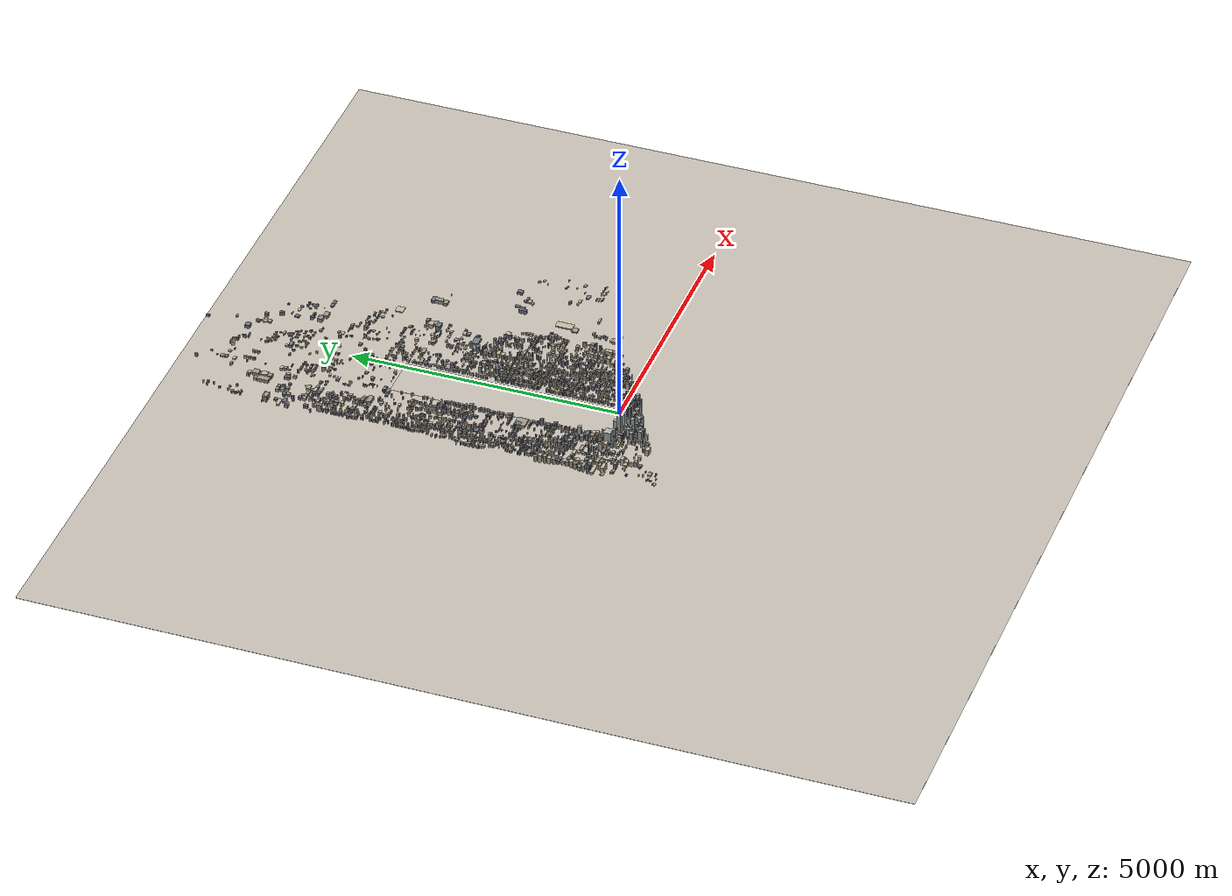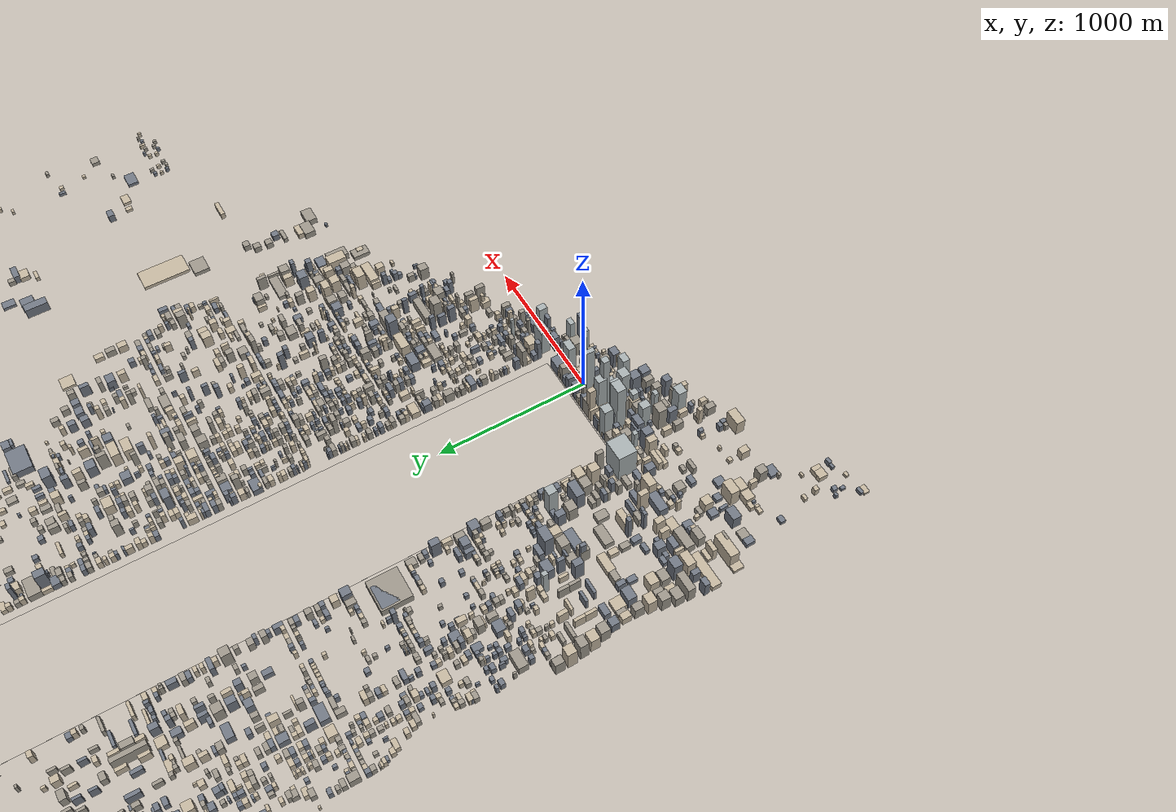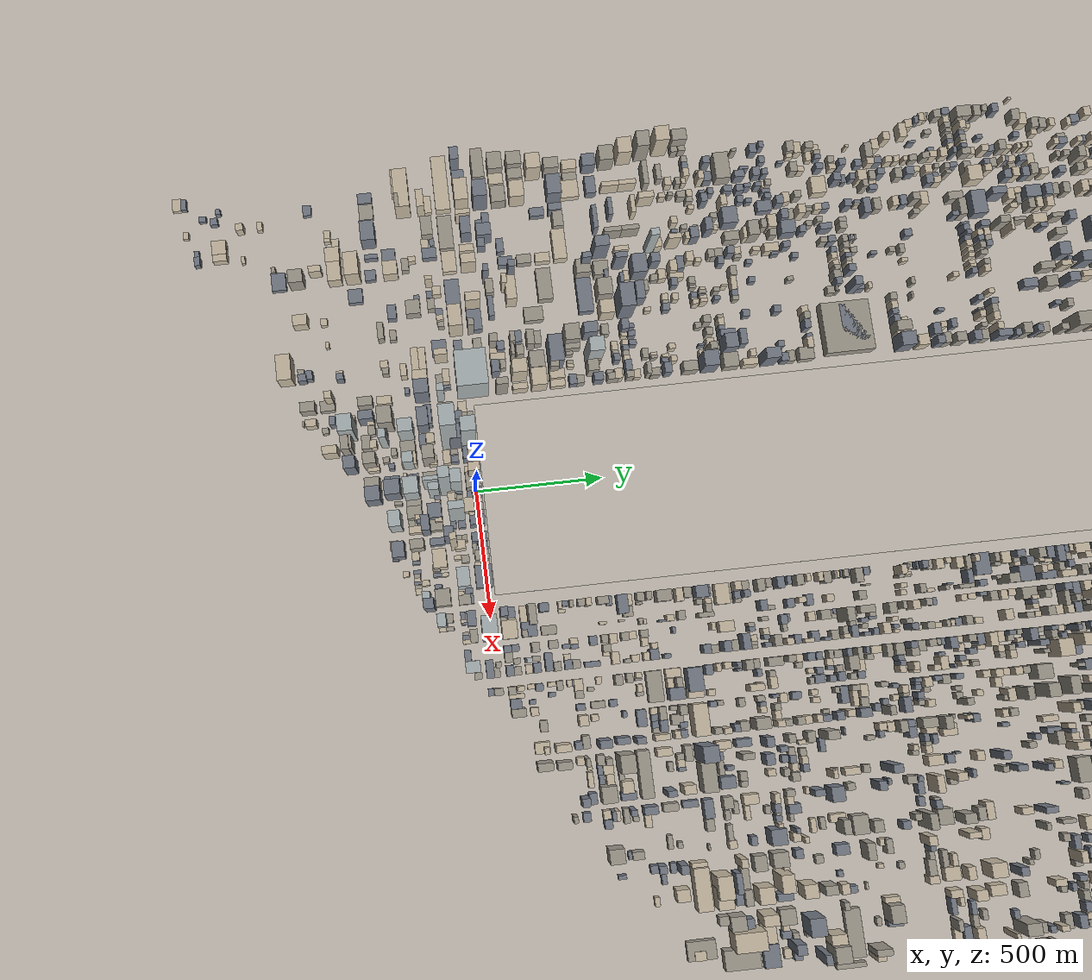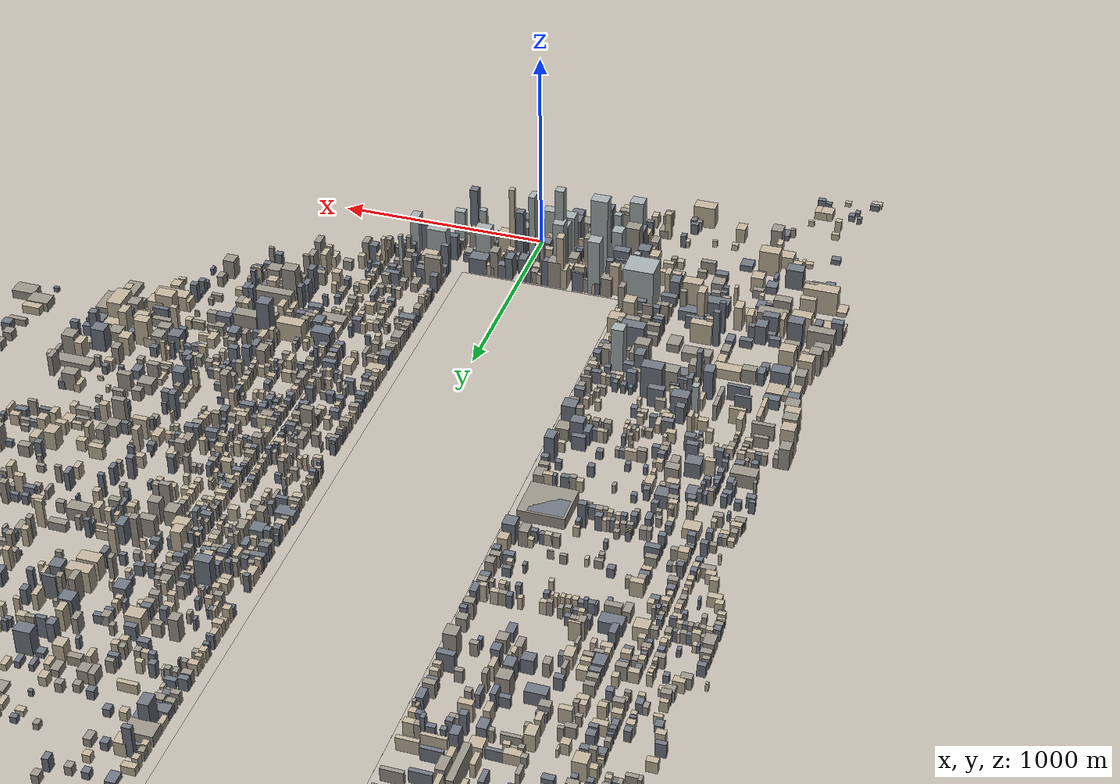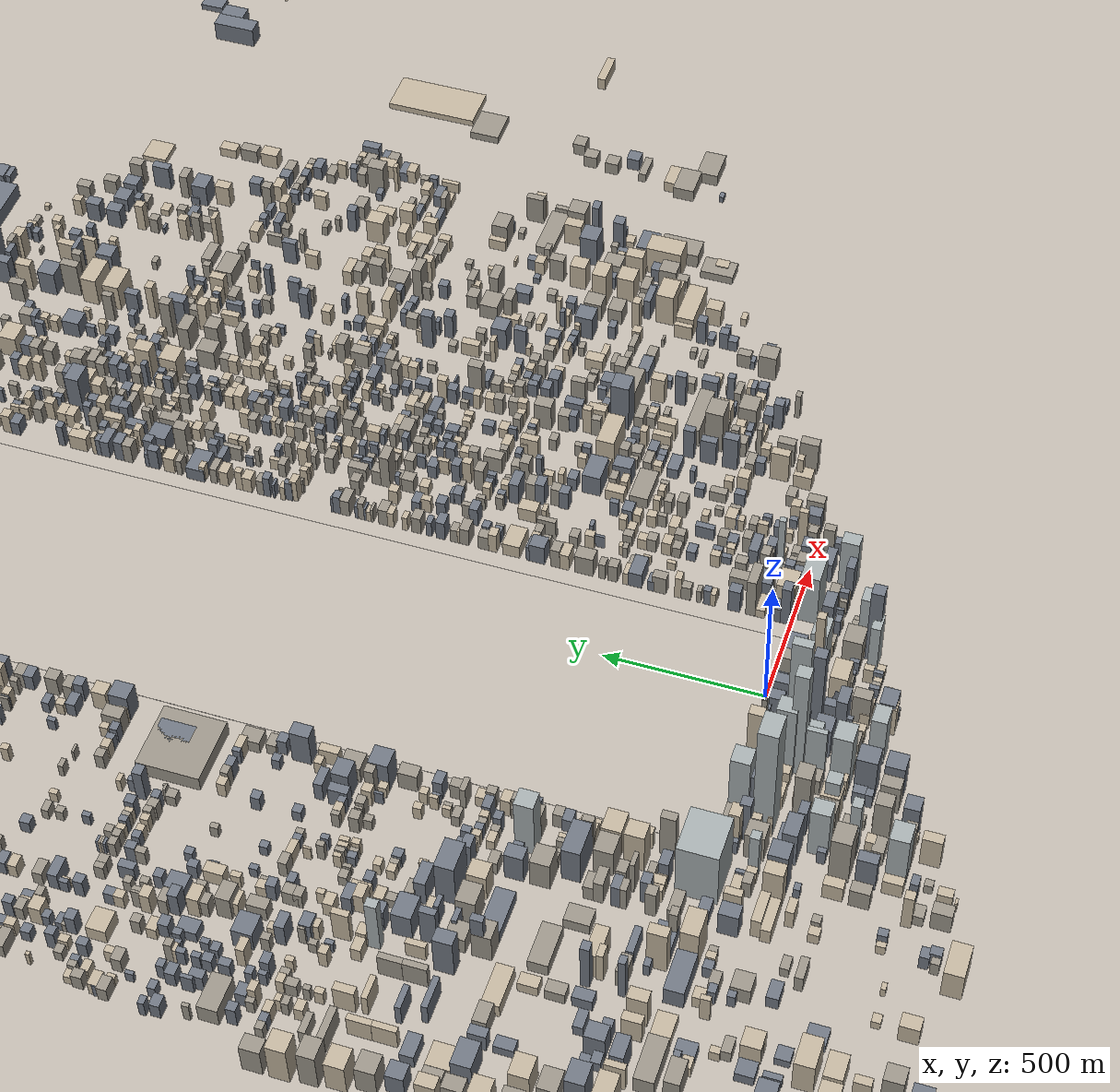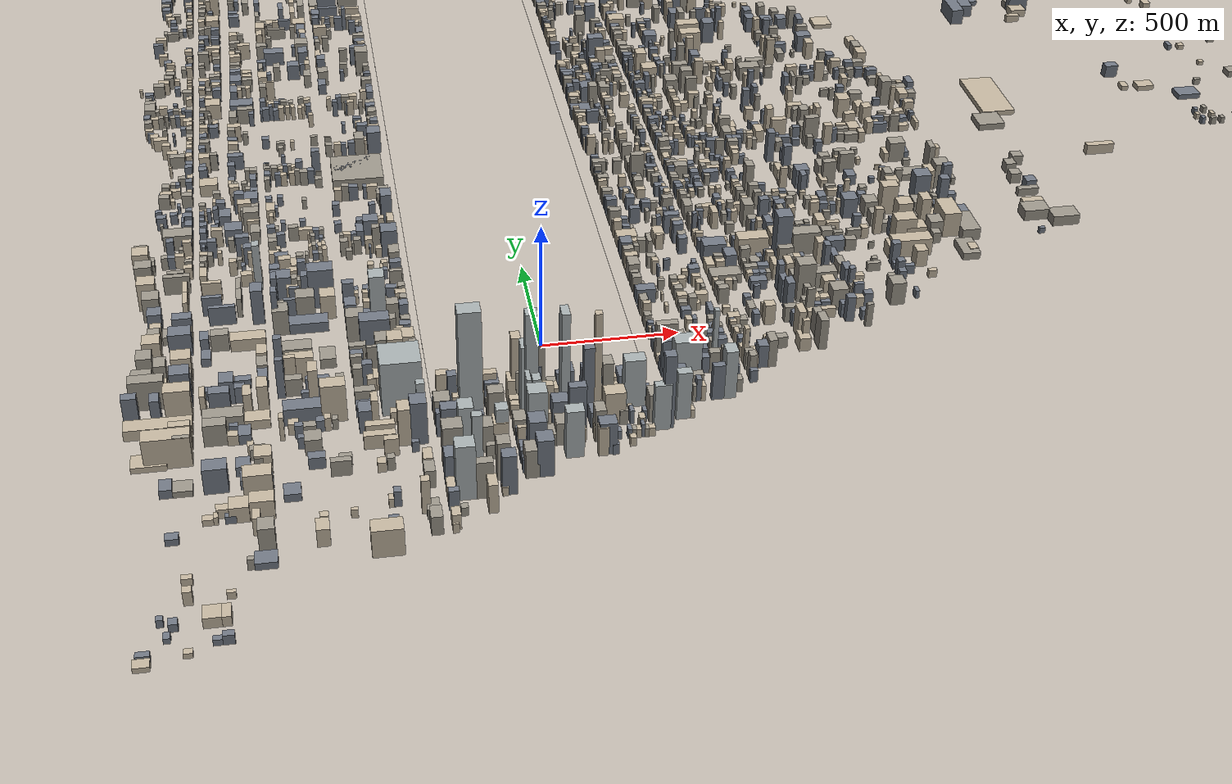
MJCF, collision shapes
<mujoco model="sim_house_nav_go2">
  <!-- 本文件由 make_house.py 从 layout.py 生成，请勿手改；改屋子改 layout.py 后重跑生成器。 -->
  <!-- 机器人：四足机器狗（宇树 Go2）（清单见 ../robots/manifest.py） -->
  <include file="robots/go2/go2.xml"/>

  <statistic center="0 0 1.4" extent="6"/>

  <visual>
    <map znear="0.02" zfar="1600" shadowclip="2.5"/>
    <headlight diffuse="0.56 0.57 0.60" ambient="0.44 0.45 0.48" specular="0.08 0.08 0.08"/>
    <quality shadowsize="4096"/>
    <global azimuth="120" elevation="-20" offwidth="1920" offheight="1080"/>
  </visual>

  <asset>
    <texture type="skybox" fileright="textures/house3/sky_fileright.png" fileleft="textures/house3/sky_fileleft.png" fileup="textures/house3/sky_fileup.png" filedown="textures/house3/sky_filedown.png" filefront="textures/house3/sky_filefront.png" fileback="textures/house3/sky_fileback.png"/>
    <texture type="2d" name="tex_wood_floor" file="textures/wood_floor.png"/>
    <texture type="2d" name="tex_wood_floor_light" file="textures/wood_floor_light.png"/>
    <texture type="2d" name="tex_tile_white" file="textures/tile_white.png"/>
    <texture type="2d" name="tex_tile_grey" file="textures/tile_grey.png"/>
    <texture type="2d" name="tex_marble" file="textures/marble.png"/>
    <texture type="2d" name="tex_marble_dark" file="textures/marble_dark.png"/>
    <texture type="2d" name="tex_marble_warm" file="textures/marble_warm.png"/>
    <texture type="2d" name="tex_marble_grey" file="textures/marble_grey.png"/>
    <texture type="2d" name="tex_marble_greige" file="textures/marble_greige.png"/>
    <texture type="2d" name="tex_carpet" file="textures/carpet.png"/>
    <texture type="2d" name="tex_fabric" file="textures/fabric.png"/>
    <texture type="2d" name="tex_fabric_blue" file="textures/fabric_blue.png"/>
    <texture type="2d" name="tex_wall_paint" file="textures/wall_paint.png"/>
    <texture type="2d" name="tex_city_skyline" file="textures/city_skyline.png"/>
    <texture type="2d" name="tex_art0" file="textures/art0.png"/>
    <texture type="2d" name="tex_art1" file="textures/art1.png"/>
    <texture type="2d" name="tex_art2" file="textures/art2.png"/>
    <texture type="2d" name="tex_art3" file="textures/art3.png"/>
    <texture type="2d" name="tex_oven_glass" file="textures/oven_glass.png"/>
    <texture type="2d" name="tex_appliance_panel" file="textures/appliance_panel.png"/>
    <texture type="2d" name="tex_h3_park" file="textures/house3/park_aerial.png" colorspace="sRGB"/>
    <texture type="2d" name="tex_h3_city" file="textures/house3/city_ground.png" colorspace="sRGB"/>
    <texture type="2d" name="tex_h3_oak" file="textures/house3/h3_oak.png" colorspace="sRGB"/>
    <texture type="2d" name="tex_h3_oak_dark" file="textures/house3/h3_oak_dark.png" colorspace="sRGB"/>
    <texture type="2d" name="tex_h3_marble" file="textures/house3/h3_marble.png" colorspace="sRGB"/>
    <texture type="2d" name="tex_h3_marble_blk" file="textures/house3/h3_marble_blk.png" colorspace="sRGB"/>
    <texture type="2d" name="tex_h3_travertine" file="textures/house3/h3_travertine.png" colorspace="sRGB"/>
    <texture type="2d" name="tex_h3_linen" file="textures/house3/h3_linen.png" colorspace="sRGB"/>
    <texture type="2d" name="tex_h3_rug" file="textures/house3/h3_rug.png" colorspace="sRGB"/>
    <texture type="2d" name="tex_h3_plaster" file="textures/house3/h3_plaster.png" colorspace="sRGB"/>
    <texture type="2d" name="tex_h3_onyx" file="textures/house3/h3_onyx.png" colorspace="sRGB"/>
    <texture type="cube" name="tex_h3_fac_glass" gridsize="3 4" gridlayout=".U..LFRB.D.." file="textures/house3/facade_glass.png" colorspace="sRGB"/>
    <texture type="cube" name="tex_h3_fac_stone" gridsize="3 4" gridlayout=".U..LFRB.D.." file="textures/house3/facade_limestone.png" colorspace="sRGB"/>
    <material name="mat_wood" texture="tex_wood_floor" texrepeat="3 3" specular="0.15" shininess="0.25" reflectance="0.02"/>
    <material name="mat_wood_light" texture="tex_wood_floor_light" texrepeat="3 3" specular="0.15" shininess="0.25" reflectance="0.02"/>
    <material name="mat_tile" texture="tex_tile_white" texrepeat="4 4" specular="0.35" shininess="0.55" reflectance="0.12"/>
    <material name="mat_tile_grey" texture="tex_tile_grey" texrepeat="4 4" specular="0.35" shininess="0.55" reflectance="0.12"/>
    <material name="mat_marble" texture="tex_marble" texrepeat="2 2" specular="0.45" shininess="0.7" reflectance="0.15"/>
    <material name="mat_marble_dark" texture="tex_marble_dark" texrepeat="2 2" specular="0.45" shininess="0.7" reflectance="0.15"/>
    <material name="mat_marble_warm" texture="tex_marble_warm" texrepeat="2 2" specular="0.45" shininess="0.7" reflectance="0.15"/>
    <material name="mat_marble_grey" texture="tex_marble_grey" texrepeat="2 2" specular="0.45" shininess="0.7" reflectance="0.15"/>
    <material name="mat_marble_greige" texture="tex_marble_greige" texrepeat="2 2" specular="0.2" shininess="0.35" reflectance="0.04"/>
    <material name="mat_carpet" texture="tex_carpet" texrepeat="4 4" specular="0.02" shininess="0.05" reflectance="0.0"/>
    <material name="mat_fabric" texture="tex_fabric" texrepeat="6 6" specular="0.05" shininess="0.1" reflectance="0.0"/>
    <material name="mat_fabric_blue" texture="tex_fabric_blue" texrepeat="6 6" specular="0.05" shininess="0.1" reflectance="0.0"/>
    <material name="mat_wall" texture="tex_wall_paint" texrepeat="2 2" specular="0.05" shininess="0.1" reflectance="0.0"/>
    <material name="mat_oven_glass" texture="tex_oven_glass" texrepeat="1 1" specular="0.85" shininess="0.9" reflectance="0.3"/>
    <material name="mat_appliance_panel" texture="tex_appliance_panel" texrepeat="1 1" specular="0.7" shininess="0.8" reflectance="0.25"/>
    <material name="mat_steel" rgba="0.82 0.84 0.87 1" specular="0.9" shininess="0.85" reflectance="0.35"/>
    <material name="mat_chrome" rgba="0.90 0.92 0.94 1" specular="1.0" shininess="0.95" reflectance="0.5"/>
    <material name="mat_glass" rgba="0.72 0.85 0.90 0.32" specular="0.8" shininess="0.9" reflectance="0.25"/>
    <material name="mat_porcelain" rgba="0.98 0.98 0.97 1" specular="0.55" shininess="0.75" reflectance="0.12"/>
    <material name="mat_screen" rgba="0.04 0.04 0.06 1" specular="0.6" shininess="0.9" reflectance="0.2"/>
    <material name="mat_city" texture="tex_city_skyline" specular="0" shininess="0" reflectance="0" emission="0.35"/>
    <material name="mat_art0" texture="tex_art0" specular="0.1" shininess="0.2"/>
    <material name="mat_art1" texture="tex_art1" specular="0.1" shininess="0.2"/>
    <material name="mat_art2" texture="tex_art2" specular="0.1" shininess="0.2"/>
    <material name="mat_art3" texture="tex_art3" specular="0.1" shininess="0.2"/>
    <material name="mat_mirror" rgba="0.78 0.85 0.90 1" specular="1.0" shininess="0.98" reflectance="0.6"/>
    <material name="mat_h3_park" texture="tex_h3_park" texrepeat="1 1" texuniform="false" specular="0" shininess="0" reflectance="0" emission="0.45"/>
    <material name="mat_h3_city" texture="tex_h3_city" texrepeat="1 1" texuniform="false" specular="0" shininess="0" reflectance="0" emission="0.45"/>
    <material name="mat_h3_glass_cool" texture="tex_h3_fac_glass" texrepeat="0.06667 0.06667" texuniform="true" rgba="0.86 0.94 1.0 1" specular="0.55" shininess="0.80" reflectance="0.18" emission="0.10"/>
    <material name="mat_h3_glass_dark" texture="tex_h3_fac_glass" texrepeat="0.06667 0.06667" texuniform="true" rgba="0.58 0.64 0.74 1" specular="0.50" shininess="0.75" reflectance="0.15" emission="0.08"/>
    <material name="mat_h3_limestone" texture="tex_h3_fac_stone" texrepeat="0.06667 0.06667" texuniform="true" rgba="1.0 0.97 0.90 1" specular="0.10" shininess="0.20" reflectance="0.02" emission="0.12"/>
    <material name="mat_h3_facade" texture="tex_h3_fac_stone" texrepeat="0.06667 0.06667" texuniform="true" rgba="0.80 0.80 0.78 1" specular="0.25" shininess="0.40" reflectance="0.05"/>
    <material name="mat_h3_wall" texture="tex_h3_plaster" texrepeat="2 2" rgba="1.06 1.05 1.02 1" specular="0.04" shininess="0.08" reflectance="0.01"/>
    <material name="mat_h3_oak" texture="tex_h3_oak" texrepeat="3 3" specular="0.14" shininess="0.24" reflectance="0.03"/>
    <material name="mat_h3_oak_dark" texture="tex_h3_oak_dark" texrepeat="3 3" specular="0.12" shininess="0.22" reflectance="0.02"/>
    <material name="mat_h3_marble" texture="tex_h3_marble" texrepeat="2 2" specular="0.45" shininess="0.72" reflectance="0.14"/>
    <material name="mat_h3_marble_blk" texture="tex_h3_marble_blk" texrepeat="1 1" specular="0.55" shininess="0.80" reflectance="0.18"/>
    <material name="mat_h3_travertine" texture="tex_h3_travertine" texrepeat="2 2" specular="0.22" shininess="0.38" reflectance="0.05"/>
    <material name="mat_h3_onyx" texture="tex_h3_onyx" texrepeat="2 2" specular="0.40" shininess="0.66" reflectance="0.12"/>
    <material name="mat_h3_linen" texture="tex_h3_linen" texrepeat="4 4" specular="0.05" shininess="0.10" reflectance="0.01"/>
    <material name="mat_h3_rug" texture="tex_h3_rug" texrepeat="3 3" specular="0.03" shininess="0.06" reflectance="0.0"/>

    <!-- ===== 装饰网格资产（decor/manifest.py 登记，decor.lock.json 落账）===== -->
    <mesh name="dm_coffee_table_0_1_0081" file="../../../decor/assets/coffee_table/p0.obj" scale="1.00813 1.00813 1.00813"/>
    <texture type="2d" name="dt_coffee_table_0" file="decor/assets/coffee_table/p0.png" colorspace="sRGB"/>
    <material name="dmat_coffee_table_0" texture="dt_coffee_table_0" specular="0.15" shininess="0.25" reflectance="0.02"/>
    <mesh name="dm_armchair_0_1_0637" file="../../../decor/assets/armchair/p0.obj" scale="1.06369 1.06369 1.06369"/>
    <texture type="2d" name="dt_armchair_0" file="decor/assets/armchair/p0.png" colorspace="sRGB"/>
    <material name="dmat_armchair_0" texture="dt_armchair_0" specular="0.15" shininess="0.25" reflectance="0.02"/>
    <mesh name="dm_armchair_1_1_0637" file="../../../decor/assets/armchair/p1.obj" scale="1.06369 1.06369 1.06369"/>
    <texture type="2d" name="dt_armchair_1" file="decor/assets/armchair/p1.png" colorspace="sRGB"/>
    <material name="dmat_armchair_1" texture="dt_armchair_1" specular="0.15" shininess="0.25" reflectance="0.02"/>
    <mesh name="dm_pillows_0_1_0742" file="../../../decor/assets/pillows/p0.obj" scale="1.07418 1.07418 1.07418"/>
    <texture type="2d" name="dt_pillows_0" file="decor/assets/pillows/p0.png" colorspace="sRGB"/>
    <material name="dmat_pillows_0" texture="dt_pillows_0" specular="0.15" shininess="0.25" reflectance="0.02"/>
    <mesh name="dm_pillows_1_1_0742" file="../../../decor/assets/pillows/p1.obj" scale="1.07418 1.07418 1.07418"/>
    <texture type="2d" name="dt_pillows_1" file="decor/assets/pillows/p1.png" colorspace="sRGB"/>
    <material name="dmat_pillows_1" texture="dt_pillows_1" specular="0.15" shininess="0.25" reflectance="0.02"/>
    <mesh name="dm_console_0_0_9898" file="../../../decor/assets/console/p0.obj" scale="0.989793 0.989793 0.989793"/>
    <texture type="2d" name="dt_console_0" file="decor/assets/console/p0.png" colorspace="sRGB"/>
    <material name="dmat_console_0" texture="dt_console_0" specular="0.15" shininess="0.25" reflectance="0.02"/>
    <mesh name="dm_console_1_0_9898" file="../../../decor/assets/console/p1.obj" scale="0.989793 0.989793 0.989793"/>
    <texture type="2d" name="dt_console_1" file="decor/assets/console/p1.png" colorspace="sRGB"/>
    <material name="dmat_console_1" texture="dt_console_1" specular="0.15" shininess="0.25" reflectance="0.02"/>
    <mesh name="dm_console_2_0_9898" file="../../../decor/assets/console/p2.obj" scale="0.989793 0.989793 0.989793"/>
    <texture type="2d" name="dt_console_2" file="decor/assets/console/p2.png" colorspace="sRGB"/>
    <material name="dmat_console_2" texture="dt_console_2" specular="0.15" shininess="0.25" reflectance="0.02"/>
    <mesh name="dm_plant_a_0_1_0119" file="../../../decor/assets/plant_a/p0.obj" scale="1.01188 1.01188 1.01188"/>
    <texture type="2d" name="dt_plant_a_0" file="decor/assets/plant_a/p0.png" colorspace="sRGB"/>
    <material name="dmat_plant_a_0" texture="dt_plant_a_0" specular="0.15" shininess="0.25" reflectance="0.02"/>
    <mesh name="dm_plant_a_1_1_0119" file="../../../decor/assets/plant_a/p1.obj" scale="1.01188 1.01188 1.01188"/>
    <texture type="2d" name="dt_plant_a_1" file="decor/assets/plant_a/p1.png" colorspace="sRGB"/>
    <material name="dmat_plant_a_1" texture="dt_plant_a_1" specular="0.15" shininess="0.25" reflectance="0.02"/>
    <mesh name="dm_plant_a_2_1_0119" file="../../../decor/assets/plant_a/p2.obj" scale="1.01188 1.01188 1.01188"/>
    <texture type="2d" name="dt_plant_a_2" file="decor/assets/plant_a/p2.png" colorspace="sRGB"/>
    <material name="dmat_plant_a_2" texture="dt_plant_a_2" specular="0.15" shininess="0.25" reflectance="0.02"/>
    <mesh name="dm_plant_a_3_1_0119" file="../../../decor/assets/plant_a/p3.obj" scale="1.01188 1.01188 1.01188"/>
    <texture type="2d" name="dt_plant_a_3" file="decor/assets/plant_a/p3.png" colorspace="sRGB"/>
    <material name="dmat_plant_a_3" texture="dt_plant_a_3" specular="0.15" shininess="0.25" reflectance="0.02"/>
    <mesh name="dm_floor_lamp_0_1_0196" file="../../../decor/assets/floor_lamp/p0.obj" scale="1.0196 1.0196 1.0196"/>
    <texture type="2d" name="dt_floor_lamp_0" file="decor/assets/floor_lamp/p0.png" colorspace="sRGB"/>
    <material name="dmat_floor_lamp_0" texture="dt_floor_lamp_0" specular="0.15" shininess="0.25" reflectance="0.02"/>
    <mesh name="dm_floor_lamp_1_1_0196" file="../../../decor/assets/floor_lamp/p1.obj" scale="1.0196 1.0196 1.0196"/>
    <texture type="2d" name="dt_floor_lamp_1" file="decor/assets/floor_lamp/p1.png" colorspace="sRGB"/>
    <material name="dmat_floor_lamp_1" texture="dt_floor_lamp_1" specular="0.15" shininess="0.25" reflectance="0.02"/>
    <mesh name="dm_floor_lamp_2_1_0196" file="../../../decor/assets/floor_lamp/p2.obj" scale="1.0196 1.0196 1.0196"/>
    <texture type="2d" name="dt_floor_lamp_2" file="decor/assets/floor_lamp/p2.png" colorspace="sRGB"/>
    <material name="dmat_floor_lamp_2" texture="dt_floor_lamp_2" specular="0.15" shininess="0.25" reflectance="0.02"/>
    <mesh name="dm_dining_chair_0_1_0156" file="../../../decor/assets/dining_chair/p0.obj" scale="1.01558 1.01558 1.01558"/>
    <texture type="2d" name="dt_dining_chair_0" file="decor/assets/dining_chair/p0.png" colorspace="sRGB"/>
    <material name="dmat_dining_chair_0" texture="dt_dining_chair_0" specular="0.15" shininess="0.25" reflectance="0.02"/>
    <mesh name="dm_chandelier_0_1_0206" file="../../../decor/assets/chandelier/p0.obj" scale="1.02061 1.02061 1.02061"/>
    <texture type="2d" name="dt_chandelier_0" file="decor/assets/chandelier/p0.png" colorspace="sRGB"/>
    <material name="dmat_chandelier_0" texture="dt_chandelier_0" specular="0.15" shininess="0.25" reflectance="0.02"/>
    <mesh name="dm_chandelier_1_1_0206" file="../../../decor/assets/chandelier/p1.obj" scale="1.02061 1.02061 1.02061"/>
    <mesh name="dm_vase_a_0_1_0386" file="../../../decor/assets/vase_a/p0.obj" scale="1.03861 1.03861 1.03861"/>
    <texture type="2d" name="dt_vase_a_0" file="decor/assets/vase_a/p0.png" colorspace="sRGB"/>
    <material name="dmat_vase_a_0" texture="dt_vase_a_0" specular="0.15" shininess="0.25" reflectance="0.02"/>
    <mesh name="dm_rc_fridge_0_0_9943" file="../../../decor/assets/rc_fridge/p0.obj" scale="0.994315 0.994315 0.994315"/>
    <texture type="2d" name="dt_rc_fridge_0" file="decor/assets/rc_fridge/p0.png" colorspace="sRGB"/>
    <material name="dmat_rc_fridge_0" texture="dt_rc_fridge_0" specular="0.15" shininess="0.25" reflectance="0.02"/>
    <mesh name="dm_rc_fridge_1_0_9943" file="../../../decor/assets/rc_fridge/p1.obj" scale="0.994315 0.994315 0.994315"/>
    <texture type="2d" name="dt_rc_fridge_1" file="decor/assets/rc_fridge/p1.png" colorspace="sRGB"/>
    <material name="dmat_rc_fridge_1" texture="dt_rc_fridge_1" specular="0.15" shininess="0.25" reflectance="0.02"/>
    <mesh name="dm_rc_fridge_2_0_9943" file="../../../decor/assets/rc_fridge/p2.obj" scale="0.994315 0.994315 0.994315"/>
    <texture type="2d" name="dt_rc_fridge_2" file="decor/assets/rc_fridge/p2.png" colorspace="sRGB"/>
    <material name="dmat_rc_fridge_2" texture="dt_rc_fridge_2" specular="0.15" shininess="0.25" reflectance="0.02"/>
    <mesh name="dm_rc_fridge_3_0_9943" file="../../../decor/assets/rc_fridge/p3.obj" scale="0.994315 0.994315 0.994315"/>
    <texture type="2d" name="dt_rc_fridge_3" file="decor/assets/rc_fridge/p3.png" colorspace="sRGB"/>
    <material name="dmat_rc_fridge_3" texture="dt_rc_fridge_3" specular="0.15" shininess="0.25" reflectance="0.02"/>
    <mesh name="dm_rc_fridge_4_0_9943" file="../../../decor/assets/rc_fridge/p4.obj" scale="0.994315 0.994315 0.994315"/>
    <texture type="2d" name="dt_rc_fridge_4" file="decor/assets/rc_fridge/p4.png" colorspace="sRGB"/>
    <material name="dmat_rc_fridge_4" texture="dt_rc_fridge_4" specular="0.15" shininess="0.25" reflectance="0.02"/>
    <mesh name="dm_rc_fridge_5_0_9943" file="../../../decor/assets/rc_fridge/p5.obj" scale="0.994315 0.994315 0.994315"/>
    <texture type="2d" name="dt_rc_fridge_5" file="decor/assets/rc_fridge/p5.png" colorspace="sRGB"/>
    <material name="dmat_rc_fridge_5" texture="dt_rc_fridge_5" specular="0.15" shininess="0.25" reflectance="0.02"/>
    <mesh name="dm_rc_fridge_6_0_9943" file="../../../decor/assets/rc_fridge/p6.obj" scale="0.994315 0.994315 0.994315"/>
    <texture type="2d" name="dt_rc_fridge_6" file="decor/assets/rc_fridge/p6.png" colorspace="sRGB"/>
    <material name="dmat_rc_fridge_6" texture="dt_rc_fridge_6" specular="0.15" shininess="0.25" reflectance="0.02"/>
    <mesh name="dm_rc_fridge_7_0_9943" file="../../../decor/assets/rc_fridge/p7.obj" scale="0.994315 0.994315 0.994315"/>
    <texture type="2d" name="dt_rc_fridge_7" file="decor/assets/rc_fridge/p7.png" colorspace="sRGB"/>
    <material name="dmat_rc_fridge_7" texture="dt_rc_fridge_7" specular="0.15" shininess="0.25" reflectance="0.02"/>
    <mesh name="dm_rc_fridge_8_0_9943" file="../../../decor/assets/rc_fridge/p8.obj" scale="0.994315 0.994315 0.994315"/>
    <texture type="2d" name="dt_rc_fridge_8" file="decor/assets/rc_fridge/p8.png" colorspace="sRGB"/>
    <material name="dmat_rc_fridge_8" texture="dt_rc_fridge_8" specular="0.15" shininess="0.25" reflectance="0.02"/>
    <mesh name="dm_rc_stove_0_0_9963" file="../../../decor/assets/rc_stove/p0.obj" scale="0.996266 0.996266 0.996266"/>
    <texture type="2d" name="dt_rc_stove_0" file="decor/assets/rc_stove/p0.png" colorspace="sRGB"/>
    <material name="dmat_rc_stove_0" texture="dt_rc_stove_0" specular="0.15" shininess="0.25" reflectance="0.02"/>
    <mesh name="dm_rc_stove_1_0_9963" file="../../../decor/assets/rc_stove/p1.obj" scale="0.996266 0.996266 0.996266"/>
    <texture type="2d" name="dt_rc_stove_1" file="decor/assets/rc_stove/p1.png" colorspace="sRGB"/>
    <material name="dmat_rc_stove_1" texture="dt_rc_stove_1" specular="0.15" shininess="0.25" reflectance="0.02"/>
    <mesh name="dm_rc_stove_2_0_9963" file="../../../decor/assets/rc_stove/p2.obj" scale="0.996266 0.996266 0.996266"/>
    <texture type="2d" name="dt_rc_stove_2" file="decor/assets/rc_stove/p2.png" colorspace="sRGB"/>
    <material name="dmat_rc_stove_2" texture="dt_rc_stove_2" specular="0.15" shininess="0.25" reflectance="0.02"/>
    <mesh name="dm_rc_stove_3_0_9963" file="../../../decor/assets/rc_stove/p3.obj" scale="0.996266 0.996266 0.996266"/>
    <texture type="2d" name="dt_rc_stove_3" file="decor/assets/rc_stove/p3.png" colorspace="sRGB"/>
    <material name="dmat_rc_stove_3" texture="dt_rc_stove_3" specular="0.15" shininess="0.25" reflectance="0.02"/>
    <mesh name="dm_rc_stove_4_0_9963" file="../../../decor/assets/rc_stove/p4.obj" scale="0.996266 0.996266 0.996266"/>
    <texture type="2d" name="dt_rc_stove_4" file="decor/assets/rc_stove/p4.png" colorspace="sRGB"/>
    <material name="dmat_rc_stove_4" texture="dt_rc_stove_4" specular="0.15" shininess="0.25" reflectance="0.02"/>
    <mesh name="dm_rc_stove_5_0_9963" file="../../../decor/assets/rc_stove/p5.obj" scale="0.996266 0.996266 0.996266"/>
    <texture type="2d" name="dt_rc_stove_5" file="decor/assets/rc_stove/p5.png" colorspace="sRGB"/>
    <material name="dmat_rc_stove_5" texture="dt_rc_stove_5" specular="0.15" shininess="0.25" reflectance="0.02"/>
    <mesh name="dm_rc_stove_6_0_9963" file="../../../decor/assets/rc_stove/p6.obj" scale="0.996266 0.996266 0.996266"/>
    <texture type="2d" name="dt_rc_stove_6" file="decor/assets/rc_stove/p6.png" colorspace="sRGB"/>
    <material name="dmat_rc_stove_6" texture="dt_rc_stove_6" specular="0.15" shininess="0.25" reflectance="0.02"/>
    <mesh name="dm_rc_stove_7_0_9963" file="../../../decor/assets/rc_stove/p7.obj" scale="0.996266 0.996266 0.996266"/>
    <texture type="2d" name="dt_rc_stove_7" file="decor/assets/rc_stove/p7.png" colorspace="sRGB"/>
    <material name="dmat_rc_stove_7" texture="dt_rc_stove_7" specular="0.15" shininess="0.25" reflectance="0.02"/>
    <mesh name="dm_rc_stove_8_0_9963" file="../../../decor/assets/rc_stove/p8.obj" scale="0.996266 0.996266 0.996266"/>
    <texture type="2d" name="dt_rc_stove_8" file="decor/assets/rc_stove/p8.png" colorspace="sRGB"/>
    <material name="dmat_rc_stove_8" texture="dt_rc_stove_8" specular="0.15" shininess="0.25" reflectance="0.02"/>
    <mesh name="dm_rc_stove_9_0_9963" file="../../../decor/assets/rc_stove/p9.obj" scale="0.996266 0.996266 0.996266"/>
    <texture type="2d" name="dt_rc_stove_9" file="decor/assets/rc_stove/p9.png" colorspace="sRGB"/>
    <material name="dmat_rc_stove_9" texture="dt_rc_stove_9" specular="0.15" shininess="0.25" reflectance="0.02"/>
    <mesh name="dm_rc_sink_0_1_0179" file="../../../decor/assets/rc_sink/p0.obj" scale="1.01789 1.01789 1.01789"/>
    <texture type="2d" name="dt_rc_sink_0" file="decor/assets/rc_sink/p0.png" colorspace="sRGB"/>
    <material name="dmat_rc_sink_0" texture="dt_rc_sink_0" specular="0.15" shininess="0.25" reflectance="0.02"/>
    <mesh name="dm_rc_sink_1_1_0179" file="../../../decor/assets/rc_sink/p1.obj" scale="1.01789 1.01789 1.01789"/>
    <texture type="2d" name="dt_rc_sink_1" file="decor/assets/rc_sink/p1.png" colorspace="sRGB"/>
    <material name="dmat_rc_sink_1" texture="dt_rc_sink_1" specular="0.15" shininess="0.25" reflectance="0.02"/>
    <mesh name="dm_rc_sink_2_1_0179" file="../../../decor/assets/rc_sink/p2.obj" scale="1.01789 1.01789 1.01789"/>
    <texture type="2d" name="dt_rc_sink_2" file="decor/assets/rc_sink/p2.png" colorspace="sRGB"/>
    <material name="dmat_rc_sink_2" texture="dt_rc_sink_2" specular="0.15" shininess="0.25" reflectance="0.02"/>
    <mesh name="dm_rc_hood_0_1_0062" file="../../../decor/assets/rc_hood/p0.obj" scale="1.00618 1.00618 1.00618"/>
    <texture type="2d" name="dt_rc_hood_0" file="decor/assets/rc_hood/p0.png" colorspace="sRGB"/>
    <material name="dmat_rc_hood_0" texture="dt_rc_hood_0" specular="0.15" shininess="0.25" reflectance="0.02"/>
    <mesh name="dm_rc_hood_1_1_0062" file="../../../decor/assets/rc_hood/p1.obj" scale="1.00618 1.00618 1.00618"/>
    <texture type="2d" name="dt_rc_hood_1" file="decor/assets/rc_hood/p1.png" colorspace="sRGB"/>
    <material name="dmat_rc_hood_1" texture="dt_rc_hood_1" specular="0.15" shininess="0.25" reflectance="0.02"/>
    <mesh name="dm_rc_hood_2_1_0062" file="../../../decor/assets/rc_hood/p2.obj" scale="1.00618 1.00618 1.00618"/>
    <texture type="2d" name="dt_rc_hood_2" file="decor/assets/rc_hood/p2.png" colorspace="sRGB"/>
    <material name="dmat_rc_hood_2" texture="dt_rc_hood_2" specular="0.15" shininess="0.25" reflectance="0.02"/>
    <mesh name="dm_rc_hood_3_1_0062" file="../../../decor/assets/rc_hood/p3.obj" scale="1.00618 1.00618 1.00618"/>
    <texture type="2d" name="dt_rc_hood_3" file="decor/assets/rc_hood/p3.png" colorspace="sRGB"/>
    <material name="dmat_rc_hood_3" texture="dt_rc_hood_3" specular="0.15" shininess="0.25" reflectance="0.02"/>
    <mesh name="dm_rc_hood_4_1_0062" file="../../../decor/assets/rc_hood/p4.obj" scale="1.00618 1.00618 1.00618"/>
    <texture type="2d" name="dt_rc_hood_4" file="decor/assets/rc_hood/p4.png" colorspace="sRGB"/>
    <material name="dmat_rc_hood_4" texture="dt_rc_hood_4" specular="0.15" shininess="0.25" reflectance="0.02"/>
    <mesh name="dm_rc_hood_5_1_0062" file="../../../decor/assets/rc_hood/p5.obj" scale="1.00618 1.00618 1.00618"/>
    <texture type="2d" name="dt_rc_hood_5" file="decor/assets/rc_hood/p5.png" colorspace="sRGB"/>
    <material name="dmat_rc_hood_5" texture="dt_rc_hood_5" specular="0.15" shininess="0.25" reflectance="0.02"/>
    <mesh name="dm_bed_0_1_0092" file="../../../decor/assets/bed/p0.obj" scale="1.00922 1.00922 1.00922"/>
    <texture type="2d" name="dt_bed_0" file="decor/assets/bed/p0.png" colorspace="sRGB"/>
    <material name="dmat_bed_0" texture="dt_bed_0" specular="0.15" shininess="0.25" reflectance="0.02"/>
    <mesh name="dm_bed_1_1_0092" file="../../../decor/assets/bed/p1.obj" scale="1.00922 1.00922 1.00922"/>
    <texture type="2d" name="dt_bed_1" file="decor/assets/bed/p1.png" colorspace="sRGB"/>
    <material name="dmat_bed_1" texture="dt_bed_1" specular="0.15" shininess="0.25" reflectance="0.02"/>
    <mesh name="dm_bed_2_1_0092" file="../../../decor/assets/bed/p2.obj" scale="1.00922 1.00922 1.00922"/>
    <texture type="2d" name="dt_bed_2" file="decor/assets/bed/p2.png" colorspace="sRGB"/>
    <material name="dmat_bed_2" texture="dt_bed_2" specular="0.15" shininess="0.25" reflectance="0.02"/>
    <mesh name="dm_bed_3_1_0092" file="../../../decor/assets/bed/p3.obj" scale="1.00922 1.00922 1.00922"/>
    <texture type="2d" name="dt_bed_3" file="decor/assets/bed/p3.png" colorspace="sRGB"/>
    <material name="dmat_bed_3" texture="dt_bed_3" specular="0.15" shininess="0.25" reflectance="0.02"/>
    <mesh name="dm_bed_4_1_0092" file="../../../decor/assets/bed/p4.obj" scale="1.00922 1.00922 1.00922"/>
    <texture type="2d" name="dt_bed_4" file="decor/assets/bed/p4.png" colorspace="sRGB"/>
    <material name="dmat_bed_4" texture="dt_bed_4" specular="0.15" shininess="0.25" reflectance="0.02"/>
    <mesh name="dm_bed_5_1_0092" file="../../../decor/assets/bed/p5.obj" scale="1.00922 1.00922 1.00922"/>
    <texture type="2d" name="dt_bed_5" file="decor/assets/bed/p5.png" colorspace="sRGB"/>
    <material name="dmat_bed_5" texture="dt_bed_5" specular="0.15" shininess="0.25" reflectance="0.02"/>
    <mesh name="dm_bed_6_1_0092" file="../../../decor/assets/bed/p6.obj" scale="1.00922 1.00922 1.00922"/>
    <texture type="2d" name="dt_bed_6" file="decor/assets/bed/p6.png" colorspace="sRGB"/>
    <material name="dmat_bed_6" texture="dt_bed_6" specular="0.15" shininess="0.25" reflectance="0.02"/>
    <mesh name="dm_bed_7_1_0092" file="../../../decor/assets/bed/p7.obj" scale="1.00922 1.00922 1.00922"/>
    <texture type="2d" name="dt_bed_7" file="decor/assets/bed/p7.png" colorspace="sRGB"/>
    <material name="dmat_bed_7" texture="dt_bed_7" specular="0.15" shininess="0.25" reflectance="0.02"/>
    <mesh name="dm_bed_8_1_0092" file="../../../decor/assets/bed/p8.obj" scale="1.00922 1.00922 1.00922"/>
    <texture type="2d" name="dt_bed_8" file="decor/assets/bed/p8.png" colorspace="sRGB"/>
    <material name="dmat_bed_8" texture="dt_bed_8" specular="0.15" shininess="0.25" reflectance="0.02"/>
    <mesh name="dm_nightstand_0_0_9882" file="../../../decor/assets/nightstand/p0.obj" scale="0.988195 0.988195 0.988195"/>
    <mesh name="dm_nightstand_1_0_9882" file="../../../decor/assets/nightstand/p1.obj" scale="0.988195 0.988195 0.988195"/>
    <texture type="2d" name="dt_nightstand_1" file="decor/assets/nightstand/p1.png" colorspace="sRGB"/>
    <material name="dmat_nightstand_1" texture="dt_nightstand_1" specular="0.15" shininess="0.25" reflectance="0.02"/>
    <mesh name="dm_nightstand_2_0_9882" file="../../../decor/assets/nightstand/p2.obj" scale="0.988195 0.988195 0.988195"/>
    <texture type="2d" name="dt_nightstand_2" file="decor/assets/nightstand/p2.png" colorspace="sRGB"/>
    <material name="dmat_nightstand_2" texture="dt_nightstand_2" specular="0.15" shininess="0.25" reflectance="0.02"/>
    <mesh name="dm_nightstand_3_0_9882" file="../../../decor/assets/nightstand/p3.obj" scale="0.988195 0.988195 0.988195"/>
    <texture type="2d" name="dt_nightstand_3" file="decor/assets/nightstand/p3.png" colorspace="sRGB"/>
    <material name="dmat_nightstand_3" texture="dt_nightstand_3" specular="0.15" shininess="0.25" reflectance="0.02"/>
    <mesh name="dm_nightstand_4_0_9882" file="../../../decor/assets/nightstand/p4.obj" scale="0.988195 0.988195 0.988195"/>
    <texture type="2d" name="dt_nightstand_4" file="decor/assets/nightstand/p4.png" colorspace="sRGB"/>
    <material name="dmat_nightstand_4" texture="dt_nightstand_4" specular="0.15" shininess="0.25" reflectance="0.02"/>
    <mesh name="dm_plant_b_3_0_9953" file="../../../decor/assets/plant_b/p3.obj" scale="0.995331 0.995331 0.995331"/>
    <texture type="2d" name="dt_plant_b_3" file="decor/assets/plant_b/p3.png" colorspace="sRGB"/>
    <material name="dmat_plant_b_3" texture="dt_plant_b_3" specular="0.15" shininess="0.25" reflectance="0.02"/>
    <mesh name="dm_plant_b_7_0_9953" file="../../../decor/assets/plant_b/p7.obj" scale="0.995331 0.995331 0.995331"/>
    <texture type="2d" name="dt_plant_b_7" file="decor/assets/plant_b/p7.png" colorspace="sRGB"/>
    <material name="dmat_plant_b_7" texture="dt_plant_b_7" specular="0.15" shininess="0.25" reflectance="0.02"/>
    <mesh name="dm_bust_0_1_0566" file="../../../decor/assets/bust/p0.obj" scale="1.05658 1.05658 1.05658"/>
    <texture type="2d" name="dt_bust_0" file="decor/assets/bust/p0.png" colorspace="sRGB"/>
    <material name="dmat_bust_0" texture="dt_bust_0" specular="0.15" shininess="0.25" reflectance="0.02"/>
    <mesh name="dm_vase_b_0_1_0563" file="../../../decor/assets/vase_b/p0.obj" scale="1.05634 1.05634 1.05634"/>
    <texture type="2d" name="dt_vase_b_0" file="decor/assets/vase_b/p0.png" colorspace="sRGB"/>
    <material name="dmat_vase_b_0" texture="dt_vase_b_0" specular="0.15" shininess="0.25" reflectance="0.02"/>
    <mesh name="dm_vase_c_0_1_0423" file="../../../decor/assets/vase_c/p0.obj" scale="1.04228 1.04228 1.04228"/>
    <texture type="2d" name="dt_vase_c_0" file="decor/assets/vase_c/p0.png" colorspace="sRGB"/>
    <material name="dmat_vase_c_0" texture="dt_vase_c_0" specular="0.15" shininess="0.25" reflectance="0.02"/>
    <mesh name="dm_bowl_0_1_0119" file="../../../decor/assets/bowl/p0.obj" scale="1.01191 1.01191 1.01191"/>
    <texture type="2d" name="dt_bowl_0" file="decor/assets/bowl/p0.png" colorspace="sRGB"/>
    <material name="dmat_bowl_0" texture="dt_bowl_0" specular="0.15" shininess="0.25" reflectance="0.02"/>
  </asset>

  <worldbody>
    <!-- ===== 灯光（场景自排）===== -->
    <light name="sun_sse" pos="14 -34 26" dir="-0.30 0.62 -0.72" directional="true" diffuse="0.50 0.48 0.44" specular="0.10 0.10 0.10" castshadow="true"/>
    <light name="sky_park_w" pos="-8.0 6.9 2.9" dir="0.10 -0.80 -0.59" diffuse="0.78 0.82 0.88" specular="0.03 0.03 0.03" castshadow="false" cutoff="88" attenuation="0.40 0.03 0.004"/>
    <light name="sky_park_c" pos="2.3 6.9 2.9" dir="0 -0.80 -0.59" diffuse="0.78 0.82 0.88" specular="0.03 0.03 0.03" castshadow="false" cutoff="88" attenuation="0.34 0.02 0.003"/>
    <light name="sky_park_e" pos="9.0 6.9 2.9" dir="-0.10 -0.80 -0.59" diffuse="0.78 0.82 0.88" specular="0.03 0.03 0.03" castshadow="false" cutoff="88" attenuation="0.40 0.03 0.004"/>
    <light name="sky_west" pos="-11.0 4.5 2.9" dir="0.80 -0.20 -0.56" diffuse="0.78 0.82 0.88" specular="0.03 0.03 0.03" castshadow="false" cutoff="88" attenuation="0.45 0.04 0.006"/>
    <light name="amb_gallery_w" pos="-3.0 0.5 3.1" dir="0 0 -1" diffuse="0.86 0.80 0.71" specular="0.04 0.04 0.04" castshadow="false" cutoff="88" attenuation="0.50 0.05 0.008"/>
    <light name="amb_gallery_e" pos="3.6 0.5 3.1" dir="0 0 -1" diffuse="0.86 0.80 0.71" specular="0.04 0.04 0.04" castshadow="false" cutoff="88" attenuation="0.50 0.05 0.008"/>
    <light name="amb_foyer" pos="2.3000000000000003 -4.4 3.1" dir="0 0 -1" diffuse="0.86 0.80 0.71" specular="0.04 0.04 0.04" castshadow="false" cutoff="88" attenuation="0.50 0.05 0.008"/>
    <light name="amb_core" pos="-0.6 -4.4 3.1" dir="0 0 -1" diffuse="0.86 0.80 0.71" specular="0.03 0.03 0.03" castshadow="false" cutoff="88" attenuation="0.60 0.07 0.012"/>
    <light name="amb_dressing" pos="-9.0 0.5 3.1" dir="0 0 -1" diffuse="0.86 0.80 0.71" specular="0.03 0.03 0.03" castshadow="false" cutoff="88" attenuation="0.60 0.07 0.012"/>

    <!-- ===== 主卧 ===== -->
    <geom name="primary_bed_floor" type="box" size="2.55 2.65 0.025" pos="-8.95 4.85 -0.025" material="mat_h3_oak"/>
    <geom name="primary_bed_ceiling" type="box" size="2.55 2.65 0.05" pos="-8.95 4.85 3.35" rgba="0.96 0.96 0.94 1" group="1"/>
    <geom name="primary_bed_ws0" type="box" size="0.95 1.65 0.07" pos="-10.55 2.27 1.65" quat="0.707107 0.707107 0 0" material="mat_h3_wall"/>
    <geom name="primary_bed_ws1" type="box" size="1 1.65 0.07" pos="-7.4 2.27 1.65" quat="0.707107 0.707107 0 0" material="mat_h3_wall"/>
    <geom name="primary_bed_ws2" type="box" size="0.6 0.45 0.07" pos="-9 2.27 2.85" quat="0.707107 0.707107 0 0" material="mat_h3_wall"/>
    <geom name="primary_bed_dfs0_l" type="box" size="0.025 0.085 1.2" pos="-9.6 2.27 1.2" rgba="0.2 0.19 0.18 1"/>
    <geom name="primary_bed_dfs0_r" type="box" size="0.025 0.085 1.2" pos="-8.4 2.27 1.2" rgba="0.2 0.19 0.18 1"/>
    <geom name="primary_bed_dfs0_top" type="box" size="0.625 0.085 0.025" pos="-9 2.27 2.4" rgba="0.2 0.19 0.18 1"/>
    <geom name="primary_bed_wn0" type="box" size="0.21 1.65 0.07" pos="-11.29 7.43 1.65" quat="0.707107 0.707107 0 0" material="mat_h3_wall"/>
    <geom name="primary_bed_wn1" type="box" size="0.17 1.65 0.07" pos="-8.95 7.43 1.65" quat="0.707107 0.707107 0 0" material="mat_h3_wall"/>
    <geom name="primary_bed_wn2" type="box" size="0.21 1.65 0.07" pos="-6.61 7.43 1.65" quat="0.707107 0.707107 0 0" material="mat_h3_wall"/>
    <geom name="primary_bed_wn3" type="box" size="0.98 0.025 0.07" pos="-10.1 7.43 0.025" quat="0.707107 0.707107 0 0" material="mat_h3_wall"/>
    <geom name="primary_bed_wn4" type="box" size="0.98 0.06 0.07" pos="-10.1 7.43 3.24" quat="0.707107 0.707107 0 0" material="mat_h3_wall"/>
    <geom name="primary_bed_wn5" type="box" size="0.98 0.025 0.07" pos="-7.8 7.43 0.025" quat="0.707107 0.707107 0 0" material="mat_h3_wall"/>
    <geom name="primary_bed_wn6" type="box" size="0.98 0.06 0.07" pos="-7.8 7.43 3.24" quat="0.707107 0.707107 0 0" material="mat_h3_wall"/>
    <geom name="primary_bed_wfn0_l" type="box" size="0.025 0.085 1.565" pos="-11.08 7.43 1.615" rgba="0.16 0.16 0.17 1"/>
    <geom name="primary_bed_wfn0_r" type="box" size="0.025 0.085 1.565" pos="-9.12 7.43 1.615" rgba="0.16 0.16 0.17 1"/>
    <geom name="primary_bed_wfn0_top" type="box" size="1.005 0.085 0.025" pos="-10.1 7.43 3.18" rgba="0.16 0.16 0.17 1"/>
    <geom name="primary_bed_wfn0_bot" type="box" size="1.005 0.085 0.025" pos="-10.1 7.43 0.05" rgba="0.16 0.16 0.17 1"/>
    <geom name="primary_bed_wfn1_l" type="box" size="0.025 0.085 1.565" pos="-8.78 7.43 1.615" rgba="0.16 0.16 0.17 1"/>
    <geom name="primary_bed_wfn1_r" type="box" size="0.025 0.085 1.565" pos="-6.82 7.43 1.615" rgba="0.16 0.16 0.17 1"/>
    <geom name="primary_bed_wfn1_top" type="box" size="1.005 0.085 0.025" pos="-7.8 7.43 3.18" rgba="0.16 0.16 0.17 1"/>
    <geom name="primary_bed_wfn1_bot" type="box" size="1.005 0.085 0.025" pos="-7.8 7.43 0.05" rgba="0.16 0.16 0.17 1"/>
    <geom name="primary_bed_ww0" type="box" size="0.21 1.65 0.07" pos="-11.43 2.41 1.65" quat="0.5 0.5 0.5 0.5" material="mat_h3_wall"/>
    <geom name="primary_bed_ww1" type="box" size="0.21 1.65 0.07" pos="-11.43 7.29 1.65" quat="0.5 0.5 0.5 0.5" material="mat_h3_wall"/>
    <geom name="primary_bed_ww2" type="box" size="2.23 0.025 0.07" pos="-11.43 4.85 0.025" quat="0.5 0.5 0.5 0.5" material="mat_h3_wall"/>
    <geom name="primary_bed_ww3" type="box" size="2.23 0.06 0.07" pos="-11.43 4.85 3.24" quat="0.5 0.5 0.5 0.5" material="mat_h3_wall"/>
    <geom name="primary_bed_wfw0_l" type="box" size="0.085 0.025 1.565" pos="-11.43 2.62 1.615" rgba="0.16 0.16 0.17 1"/>
    <geom name="primary_bed_wfw0_r" type="box" size="0.085 0.025 1.565" pos="-11.43 7.08 1.615" rgba="0.16 0.16 0.17 1"/>
    <geom name="primary_bed_wfw0_top" type="box" size="0.085 2.255 0.025" pos="-11.43 4.85 3.18" rgba="0.16 0.16 0.17 1"/>
    <geom name="primary_bed_wfw0_bot" type="box" size="0.085 2.255 0.025" pos="-11.43 4.85 0.05" rgba="0.16 0.16 0.17 1"/>
    <geom name="primary_bed_we0" type="box" size="2.65 1.65 0.07" pos="-6.47 4.85 1.65" quat="0.5 0.5 0.5 0.5" material="mat_h3_wall"/>
    <geom name="furn_pb_bench" type="box" size="0.75 0.21 0.23" pos="-8.95 5.9 0.23" rgba="0.52 0.4 0.28 1"/>
    <geom name="furn_pb_bed" type="box" size="0.87 1.05 0.41" pos="-8.95 4.4 0.41" rgba="0.62 0.6 0.58 1" group="3"/>
    <geom name="furn_pb_nsL" type="box" size="0.25 0.26 0.36" pos="-10.4 3.55 0.36" rgba="0.62 0.6 0.58 1" group="3"/>
    <geom name="furn_pb_nsR" type="box" size="0.25 0.26 0.36" pos="-7.5 3.55 0.36" rgba="0.62 0.6 0.58 1" group="3"/>
    <geom name="furn_pb_lampL_base" type="cylinder" size="0.09 0.025" pos="-10.4 3.55 0.745" rgba="0.28 0.28 0.3 1"/>
    <geom name="furn_pb_lampL_pole" type="cylinder" size="0.015 0.13" pos="-10.4 3.55 0.88" rgba="0.42 0.43 0.46 1"/>
    <geom name="furn_pb_lampL_shade" type="cylinder" size="0.15 0.12" pos="-10.4 3.55 1.08" rgba="0.96 0.9 0.62 1"/>
    <geom name="furn_pb_lampR_base" type="cylinder" size="0.09 0.025" pos="-7.5 3.55 0.745" rgba="0.28 0.28 0.3 1"/>
    <geom name="furn_pb_lampR_pole" type="cylinder" size="0.015 0.13" pos="-7.5 3.55 0.88" rgba="0.42 0.43 0.46 1"/>
    <geom name="furn_pb_lampR_shade" type="cylinder" size="0.15 0.12" pos="-7.5 3.55 1.08" rgba="0.96 0.9 0.62 1"/>

    <!-- ===== 餐厅 ===== -->
    <geom name="dining_floor" type="box" size="2.4 2.65 0.025" pos="-4 4.85 -0.025" material="mat_h3_oak"/>
    <geom name="dining_ceiling" type="box" size="2.4 2.65 0.05" pos="-4 4.85 3.35" rgba="0.96 0.96 0.94 1" group="1"/>
    <geom name="dining_ws0" type="box" size="0.55 1.65 0.07" pos="-5.85 2.27 1.65" quat="0.707107 0.707107 0 0" material="mat_h3_wall"/>
    <geom name="dining_ws1" type="box" size="0.55 1.65 0.07" pos="-2.15 2.27 1.65" quat="0.707107 0.707107 0 0" material="mat_h3_wall"/>
    <geom name="dining_wn0" type="box" size="0.21 1.65 0.07" pos="-6.19 7.43 1.65" quat="0.707107 0.707107 0 0" material="mat_h3_wall"/>
    <geom name="dining_wn1" type="box" size="0.17 1.65 0.07" pos="-4 7.43 1.65" quat="0.707107 0.707107 0 0" material="mat_h3_wall"/>
    <geom name="dining_wn2" type="box" size="0.21 1.65 0.07" pos="-1.81 7.43 1.65" quat="0.707107 0.707107 0 0" material="mat_h3_wall"/>
    <geom name="dining_wn3" type="box" size="0.905 0.025 0.07" pos="-5.075 7.43 0.025" quat="0.707107 0.707107 0 0" material="mat_h3_wall"/>
    <geom name="dining_wn4" type="box" size="0.905 0.06 0.07" pos="-5.075 7.43 3.24" quat="0.707107 0.707107 0 0" material="mat_h3_wall"/>
    <geom name="dining_wn5" type="box" size="0.905 0.025 0.07" pos="-2.925 7.43 0.025" quat="0.707107 0.707107 0 0" material="mat_h3_wall"/>
    <geom name="dining_wn6" type="box" size="0.905 0.06 0.07" pos="-2.925 7.43 3.24" quat="0.707107 0.707107 0 0" material="mat_h3_wall"/>
    <geom name="dining_wfn0_l" type="box" size="0.025 0.085 1.565" pos="-5.98 7.43 1.615" rgba="0.16 0.16 0.17 1"/>
    <geom name="dining_wfn0_r" type="box" size="0.025 0.085 1.565" pos="-4.17 7.43 1.615" rgba="0.16 0.16 0.17 1"/>
    <geom name="dining_wfn0_top" type="box" size="0.93 0.085 0.025" pos="-5.075 7.43 3.18" rgba="0.16 0.16 0.17 1"/>
    <geom name="dining_wfn0_bot" type="box" size="0.93 0.085 0.025" pos="-5.075 7.43 0.05" rgba="0.16 0.16 0.17 1"/>
    <geom name="dining_wfn1_l" type="box" size="0.025 0.085 1.565" pos="-3.83 7.43 1.615" rgba="0.16 0.16 0.17 1"/>
    <geom name="dining_wfn1_r" type="box" size="0.025 0.085 1.565" pos="-2.02 7.43 1.615" rgba="0.16 0.16 0.17 1"/>
    <geom name="dining_wfn1_top" type="box" size="0.93 0.085 0.025" pos="-2.925 7.43 3.18" rgba="0.16 0.16 0.17 1"/>
    <geom name="dining_wfn1_bot" type="box" size="0.93 0.085 0.025" pos="-2.925 7.43 0.05" rgba="0.16 0.16 0.17 1"/>
    <geom name="dining_ww0" type="box" size="2.65 1.65 0.07" pos="-6.33 4.85 1.65" quat="0.5 0.5 0.5 0.5" material="mat_h3_wall"/>
    <geom name="dining_we0" type="box" size="2.65 1.65 0.07" pos="-1.67 4.85 1.65" quat="0.5 0.5 0.5 0.5" material="mat_h3_wall"/>
    <geom name="furn_dn_table_top" type="box" size="1.2 0.55 0.03" pos="-4 5 0.75" rgba="0.46 0.33 0.22 1"/>
    <geom name="furn_dn_table_apron_n" type="box" size="1.12 0.02 0.05" pos="-4 5.49 0.66" rgba="0.34 0.24 0.16 1"/>
    <geom name="furn_dn_table_apron_s" type="box" size="1.12 0.02 0.05" pos="-4 4.51 0.66" rgba="0.34 0.24 0.16 1"/>
    <geom name="furn_dn_table_apron_e" type="box" size="0.02 0.47 0.05" pos="-2.86 5 0.66" rgba="0.34 0.24 0.16 1"/>
    <geom name="furn_dn_table_apron_w" type="box" size="0.02 0.47 0.05" pos="-5.14 5 0.66" rgba="0.34 0.24 0.16 1"/>
    <geom name="furn_dn_table_lega" type="box" size="0.04 0.04 0.36" pos="-2.9 5.45 0.36" rgba="0.34 0.24 0.16 1"/>
    <geom name="furn_dn_table_legb" type="box" size="0.04 0.04 0.36" pos="-2.9 4.55 0.36" rgba="0.34 0.24 0.16 1"/>
    <geom name="furn_dn_table_legc" type="box" size="0.04 0.04 0.36" pos="-5.1 5.45 0.36" rgba="0.34 0.24 0.16 1"/>
    <geom name="furn_dn_table_legd" type="box" size="0.04 0.04 0.36" pos="-5.1 4.55 0.36" rgba="0.34 0.24 0.16 1"/>
    <geom name="furn_dn_n0" type="box" size="0.23 0.3 0.5" pos="-4.8 5.85 0.5" quat="0.707107 0 0 -0.707107" rgba="0.62 0.6 0.58 1" group="3"/>
    <geom name="furn_dn_s0" type="box" size="0.23 0.3 0.5" pos="-4.8 4.15 0.5" quat="0.707107 0 0 0.707107" rgba="0.62 0.6 0.58 1" group="3"/>
    <geom name="furn_dn_n1" type="box" size="0.23 0.3 0.5" pos="-4 5.85 0.5" quat="0.707107 0 0 -0.707107" rgba="0.62 0.6 0.58 1" group="3"/>
    <geom name="furn_dn_s1" type="box" size="0.23 0.3 0.5" pos="-4 4.15 0.5" quat="0.707107 0 0 0.707107" rgba="0.62 0.6 0.58 1" group="3"/>
    <geom name="furn_dn_n2" type="box" size="0.23 0.3 0.5" pos="-3.2 5.85 0.5" quat="0.707107 0 0 -0.707107" rgba="0.62 0.6 0.58 1" group="3"/>
    <geom name="furn_dn_s2" type="box" size="0.23 0.3 0.5" pos="-3.2 4.15 0.5" quat="0.707107 0 0 0.707107" rgba="0.62 0.6 0.58 1" group="3"/>
    <geom name="furn_dn_e" type="box" size="0.23 0.3 0.5" pos="-2.75 5 0.5" quat="0 0 0 1" rgba="0.62 0.6 0.58 1" group="3"/>
    <geom name="furn_dn_w" type="box" size="0.23 0.3 0.5" pos="-5.25 5 0.5" rgba="0.62 0.6 0.58 1" group="3"/>
    <geom name="furn_dn_chand" type="box" size="0.35 0.33 0.44" pos="-4 5 2.72" rgba="0.62 0.6 0.58 1" group="3"/>
    <geom name="furn_dn_sideboard" type="box" size="1.22 0.26 0.34" pos="-6 5 0.34" quat="0.707107 0 0 0.707107" rgba="0.52 0.4 0.28 1" group="3"/>
    <geom name="furn_dn_vase" type="box" size="0.11 0.11 0.21" pos="-6 5 0.89" rgba="0.62 0.6 0.58 1" group="3"/>

    <!-- ===== 大客厅 ===== -->
    <geom name="great_room_floor" type="box" size="3.9 2.65 0.025" pos="2.3 4.85 -0.025" material="mat_h3_oak"/>
    <geom name="great_room_ceiling" type="box" size="3.9 2.65 0.05" pos="2.3 4.85 3.35" rgba="0.96 0.96 0.94 1" group="1"/>
    <geom name="great_room_ws0" type="box" size="0.95 1.65 0.07" pos="-0.65 2.27 1.65" quat="0.707107 0.707107 0 0" material="mat_h3_wall"/>
    <geom name="great_room_ws1" type="box" size="0.95 1.65 0.07" pos="5.25 2.27 1.65" quat="0.707107 0.707107 0 0" material="mat_h3_wall"/>
    <geom name="great_room_wn0" type="box" size="0.210025 1.65 0.07" pos="-1.38998 7.43 1.65" quat="0.707107 0.707107 0 0" material="mat_h3_wall"/>
    <geom name="great_room_wn1" type="box" size="0.17 1.65 0.07" pos="1.08335 7.43 1.65" quat="0.707107 0.707107 0 0" material="mat_h3_wall"/>
    <geom name="great_room_wn2" type="box" size="0.17 1.65 0.07" pos="3.51665 7.43 1.65" quat="0.707107 0.707107 0 0" material="mat_h3_wall"/>
    <geom name="great_room_wn3" type="box" size="0.210025 1.65 0.07" pos="5.98997 7.43 1.65" quat="0.707107 0.707107 0 0" material="mat_h3_wall"/>
    <geom name="great_room_wn4" type="box" size="1.04665 0.025 0.07" pos="-0.1333 7.43 0.025" quat="0.707107 0.707107 0 0" material="mat_h3_wall"/>
    <geom name="great_room_wn5" type="box" size="1.04665 0.06 0.07" pos="-0.1333 7.43 3.24" quat="0.707107 0.707107 0 0" material="mat_h3_wall"/>
    <geom name="great_room_wn6" type="box" size="1.04665 0.025 0.07" pos="2.3 7.43 0.025" quat="0.707107 0.707107 0 0" material="mat_h3_wall"/>
    <geom name="great_room_wn7" type="box" size="1.04665 0.06 0.07" pos="2.3 7.43 3.24" quat="0.707107 0.707107 0 0" material="mat_h3_wall"/>
    <geom name="great_room_wn8" type="box" size="1.04665 0.025 0.07" pos="4.7333 7.43 0.025" quat="0.707107 0.707107 0 0" material="mat_h3_wall"/>
    <geom name="great_room_wn9" type="box" size="1.04665 0.06 0.07" pos="4.7333 7.43 3.24" quat="0.707107 0.707107 0 0" material="mat_h3_wall"/>
    <geom name="great_room_wfn0_l" type="box" size="0.025 0.085 1.565" pos="-1.17995 7.43 1.615" rgba="0.16 0.16 0.17 1"/>
    <geom name="great_room_wfn0_r" type="box" size="0.025 0.085 1.565" pos="0.91335 7.43 1.615" rgba="0.16 0.16 0.17 1"/>
    <geom name="great_room_wfn0_top" type="box" size="1.07165 0.085 0.025" pos="-0.1333 7.43 3.18" rgba="0.16 0.16 0.17 1"/>
    <geom name="great_room_wfn0_bot" type="box" size="1.07165 0.085 0.025" pos="-0.1333 7.43 0.05" rgba="0.16 0.16 0.17 1"/>
    <geom name="great_room_wfn1_l" type="box" size="0.025 0.085 1.565" pos="1.25335 7.43 1.615" rgba="0.16 0.16 0.17 1"/>
    <geom name="great_room_wfn1_r" type="box" size="0.025 0.085 1.565" pos="3.34665 7.43 1.615" rgba="0.16 0.16 0.17 1"/>
    <geom name="great_room_wfn1_top" type="box" size="1.07165 0.085 0.025" pos="2.3 7.43 3.18" rgba="0.16 0.16 0.17 1"/>
    <geom name="great_room_wfn1_bot" type="box" size="1.07165 0.085 0.025" pos="2.3 7.43 0.05" rgba="0.16 0.16 0.17 1"/>
    <geom name="great_room_wfn2_l" type="box" size="0.025 0.085 1.565" pos="3.68665 7.43 1.615" rgba="0.16 0.16 0.17 1"/>
    <geom name="great_room_wfn2_r" type="box" size="0.025 0.085 1.565" pos="5.77995 7.43 1.615" rgba="0.16 0.16 0.17 1"/>
    <geom name="great_room_wfn2_top" type="box" size="1.07165 0.085 0.025" pos="4.7333 7.43 3.18" rgba="0.16 0.16 0.17 1"/>
    <geom name="great_room_wfn2_bot" type="box" size="1.07165 0.085 0.025" pos="4.7333 7.43 0.05" rgba="0.16 0.16 0.17 1"/>
    <geom name="great_room_ww0" type="box" size="2.65 1.65 0.07" pos="-1.53 4.85 1.65" quat="0.5 0.5 0.5 0.5" material="mat_h3_wall"/>
    <geom name="great_room_we0" type="box" size="2.65 1.65 0.07" pos="6.13 4.85 1.65" quat="0.5 0.5 0.5 0.5" material="mat_h3_wall"/>
    <geom name="furn_gr_rug" type="box" size="2.6 1.8 0.012" pos="2.3 4.6 0.012" material="mat_h3_rug"/>
    <geom name="furn_gr_sofa_base" type="box" size="1.8 0.5 0.21" pos="2.3 3.3 0.21" material="mat_h3_linen"/>
    <geom name="furn_gr_sofa_back" type="box" size="1.8 0.12 0.34" pos="2.3 2.9 0.55" material="mat_h3_linen"/>
    <geom name="furn_gr_sofa_armL" type="box" size="0.13 0.5 0.34" pos="0.55 3.3 0.34" material="mat_h3_linen"/>
    <geom name="furn_gr_sofa_armR" type="box" size="0.13 0.5 0.34" pos="4.05 3.3 0.34" material="mat_h3_linen"/>
    <geom name="furn_gr_chaise" type="box" size="0.475 0.95 0.21" pos="0.1 4.6 0.21" material="mat_h3_linen"/>
    <geom name="furn_gr_coffee" type="box" size="0.675 0.675 0.25" pos="2.3 4.9 0.25" rgba="0.62 0.6 0.58 1" group="3"/>
    <geom name="furn_gr_ch1" type="box" size="0.45 0.53 0.55" pos="4.9 6.2 0.55" quat="-0.173648 0 0 0.984808" rgba="0.62 0.6 0.58 1" group="3"/>
    <geom name="furn_gr_ch2" type="box" size="0.45 0.53 0.55" pos="-0.4 6.2 0.55" quat="0.984808 0 0 -0.173648" rgba="0.62 0.6 0.58 1" group="3"/>
    <geom name="furn_gr_pillows" type="box" size="0.51 0.26 0.25" pos="1.2 3.05 0.72" quat="0.997564 0 0 0.0697565" rgba="0.62 0.6 0.58 1" group="3"/>
    <geom name="furn_gr_console" type="box" size="1.22 0.26 0.34" pos="5.8 4.6 0.34" quat="0.707107 0 0 0.707107" material="mat_h3_oak_dark" group="3"/>
    <geom name="furn_gr_plant" type="box" size="0.33 0.35 0.69" pos="5.7 6.6 0.69" rgba="0.62 0.6 0.58 1" group="3"/>
    <geom name="furn_gr_lamp" type="box" size="0.23 0.23 0.49" pos="-0.9 3 0.49" rgba="0.62 0.6 0.58 1" group="3"/>
    <geom name="furn_gr_vase" type="box" size="0.1 0.1 0.18" pos="5.8 4.6 0.86" quat="0.976296 0 0 0.21644" rgba="0.62 0.6 0.58 1" group="3"/>
    <geom name="furn_gr_bowl" type="box" size="0.16 0.16 0.05" pos="2.3 4.9 0.55" rgba="0.62 0.6 0.58 1" group="3"/>

    <!-- ===== 厨房 ===== -->
    <geom name="kitchen_floor" type="box" size="2.65 2.65 0.025" pos="8.85 4.85 -0.025" material="mat_h3_travertine"/>
    <geom name="kitchen_ceiling" type="box" size="2.65 2.65 0.05" pos="8.85 4.85 3.35" rgba="0.96 0.96 0.94 1" group="1"/>
    <geom name="kitchen_ws0" type="box" size="0.975 1.65 0.07" pos="7.175 2.27 1.65" quat="0.707107 0.707107 0 0" material="mat_h3_wall"/>
    <geom name="kitchen_ws1" type="box" size="0.975 1.65 0.07" pos="10.525 2.27 1.65" quat="0.707107 0.707107 0 0" material="mat_h3_wall"/>
    <geom name="kitchen_wn0" type="box" size="0.21 1.65 0.07" pos="6.41 7.43 1.65" quat="0.707107 0.707107 0 0" material="mat_h3_wall"/>
    <geom name="kitchen_wn1" type="box" size="0.17 1.65 0.07" pos="8.85 7.43 1.65" quat="0.707107 0.707107 0 0" material="mat_h3_wall"/>
    <geom name="kitchen_wn2" type="box" size="0.21 1.65 0.07" pos="11.29 7.43 1.65" quat="0.707107 0.707107 0 0" material="mat_h3_wall"/>
    <geom name="kitchen_wn3" type="box" size="1.03 0.025 0.07" pos="7.65 7.43 0.025" quat="0.707107 0.707107 0 0" material="mat_h3_wall"/>
    <geom name="kitchen_wn4" type="box" size="1.03 0.06 0.07" pos="7.65 7.43 3.24" quat="0.707107 0.707107 0 0" material="mat_h3_wall"/>
    <geom name="kitchen_wn5" type="box" size="1.03 0.025 0.07" pos="10.05 7.43 0.025" quat="0.707107 0.707107 0 0" material="mat_h3_wall"/>
    <geom name="kitchen_wn6" type="box" size="1.03 0.06 0.07" pos="10.05 7.43 3.24" quat="0.707107 0.707107 0 0" material="mat_h3_wall"/>
    <geom name="kitchen_wfn0_l" type="box" size="0.025 0.085 1.565" pos="6.62 7.43 1.615" rgba="0.16 0.16 0.17 1"/>
    <geom name="kitchen_wfn0_r" type="box" size="0.025 0.085 1.565" pos="8.68 7.43 1.615" rgba="0.16 0.16 0.17 1"/>
    <geom name="kitchen_wfn0_top" type="box" size="1.055 0.085 0.025" pos="7.65 7.43 3.18" rgba="0.16 0.16 0.17 1"/>
    <geom name="kitchen_wfn0_bot" type="box" size="1.055 0.085 0.025" pos="7.65 7.43 0.05" rgba="0.16 0.16 0.17 1"/>
    <geom name="kitchen_wfn1_l" type="box" size="0.025 0.085 1.565" pos="9.02 7.43 1.615" rgba="0.16 0.16 0.17 1"/>
    <geom name="kitchen_wfn1_r" type="box" size="0.025 0.085 1.565" pos="11.08 7.43 1.615" rgba="0.16 0.16 0.17 1"/>
    <geom name="kitchen_wfn1_top" type="box" size="1.055 0.085 0.025" pos="10.05 7.43 3.18" rgba="0.16 0.16 0.17 1"/>
    <geom name="kitchen_wfn1_bot" type="box" size="1.055 0.085 0.025" pos="10.05 7.43 0.05" rgba="0.16 0.16 0.17 1"/>
    <geom name="kitchen_ww0" type="box" size="2.65 1.65 0.07" pos="6.27 4.85 1.65" quat="0.5 0.5 0.5 0.5" material="mat_h3_wall"/>
    <geom name="kitchen_we0" type="box" size="0.21 1.65 0.07" pos="11.43 2.41 1.65" quat="0.5 0.5 0.5 0.5" material="mat_h3_wall"/>
    <geom name="kitchen_we1" type="box" size="0.21 1.65 0.07" pos="11.43 7.29 1.65" quat="0.5 0.5 0.5 0.5" material="mat_h3_wall"/>
    <geom name="kitchen_we2" type="box" size="2.23 0.025 0.07" pos="11.43 4.85 0.025" quat="0.5 0.5 0.5 0.5" material="mat_h3_wall"/>
    <geom name="kitchen_we3" type="box" size="2.23 0.06 0.07" pos="11.43 4.85 3.24" quat="0.5 0.5 0.5 0.5" material="mat_h3_wall"/>
    <geom name="kitchen_wfe0_l" type="box" size="0.085 0.025 1.565" pos="11.43 2.62 1.615" rgba="0.16 0.16 0.17 1"/>
    <geom name="kitchen_wfe0_r" type="box" size="0.085 0.025 1.565" pos="11.43 7.08 1.615" rgba="0.16 0.16 0.17 1"/>
    <geom name="kitchen_wfe0_top" type="box" size="0.085 2.255 0.025" pos="11.43 4.85 3.18" rgba="0.16 0.16 0.17 1"/>
    <geom name="kitchen_wfe0_bot" type="box" size="0.085 2.255 0.025" pos="11.43 4.85 0.05" rgba="0.16 0.16 0.17 1"/>
    <geom name="furn_kt_island" type="box" size="1.3 0.55 0.46" pos="8.85 4.6 0.46" material="mat_h3_marble"/>
    <geom name="furn_kt_island_top" type="box" size="1.38 0.63 0.025" pos="8.85 4.6 0.945" material="mat_h3_marble_blk"/>
    <geom name="furn_kt_counter" type="box" size="2.5 0.34 0.46" pos="8.85 7.1 0.46" material="mat_h3_travertine"/>
    <geom name="furn_kt_counter_top" type="box" size="2.55 0.37 0.025" pos="8.85 7.1 0.945" material="mat_h3_marble_blk"/>
    <geom name="furn_kt_upper" type="box" size="2.5 0.17 0.4" pos="8.85 7.28 2.05" rgba="0.9 0.89 0.87 1"/>
    <geom name="furn_kt_fridge" type="box" size="0.47 0.44 0.95" pos="11.05 3.1 0.95" quat="0.707107 0 0 -0.707107" rgba="0.62 0.6 0.58 1" group="3"/>
    <geom name="furn_kt_range" type="box" size="0.39 0.36 0.57" pos="7.2 7.1 0.57" quat="0 0 0 1" rgba="0.62 0.6 0.58 1" group="3"/>
    <geom name="furn_kt_sink" type="box" size="0.4 0.23 0.21" pos="10.1 7.1 1.06" quat="0 0 0 1" rgba="0.62 0.6 0.58 1" group="3"/>
    <geom name="furn_kt_hood" type="box" size="0.49 0.16 0.45" pos="7.2 7.28 1.95" quat="0 0 0 1" rgba="0.62 0.6 0.58 1" group="3"/>
    <geom name="furn_kt_st0_top" type="cylinder" size="0.18 0.03" pos="8.05 3.8 0.68" rgba="0.34 0.24 0.16 1"/>
    <geom name="furn_kt_st0_post" type="cylinder" size="0.035 0.34" pos="8.05 3.8 0.34" rgba="0.42 0.43 0.46 1"/>
    <geom name="furn_kt_st0_base" type="cylinder" size="0.171 0.02" pos="8.05 3.8 0.02" rgba="0.42 0.43 0.46 1"/>
    <geom name="furn_kt_st0_ring" type="cylinder" size="0.1296 0.015" pos="8.05 3.8 0.22" rgba="0.42 0.43 0.46 1"/>
    <geom name="furn_kt_st1_top" type="cylinder" size="0.18 0.03" pos="8.85 3.8 0.68" rgba="0.34 0.24 0.16 1"/>
    <geom name="furn_kt_st1_post" type="cylinder" size="0.035 0.34" pos="8.85 3.8 0.34" rgba="0.42 0.43 0.46 1"/>
    <geom name="furn_kt_st1_base" type="cylinder" size="0.171 0.02" pos="8.85 3.8 0.02" rgba="0.42 0.43 0.46 1"/>
    <geom name="furn_kt_st1_ring" type="cylinder" size="0.1296 0.015" pos="8.85 3.8 0.22" rgba="0.42 0.43 0.46 1"/>
    <geom name="furn_kt_st2_top" type="cylinder" size="0.18 0.03" pos="9.65 3.8 0.68" rgba="0.34 0.24 0.16 1"/>
    <geom name="furn_kt_st2_post" type="cylinder" size="0.035 0.34" pos="9.65 3.8 0.34" rgba="0.42 0.43 0.46 1"/>
    <geom name="furn_kt_st2_base" type="cylinder" size="0.171 0.02" pos="9.65 3.8 0.02" rgba="0.42 0.43 0.46 1"/>
    <geom name="furn_kt_st2_ring" type="cylinder" size="0.1296 0.015" pos="9.65 3.8 0.22" rgba="0.42 0.43 0.46 1"/>

    <!-- ===== 衣帽间 ===== -->
    <geom name="dressing_floor" type="box" size="2.55 1.7 0.025" pos="-8.95 0.5 -0.025" material="mat_h3_oak_dark"/>
    <geom name="dressing_ceiling" type="box" size="2.55 1.7 0.05" pos="-8.95 0.5 3.35" rgba="0.96 0.96 0.94 1" group="1"/>
    <geom name="dressing_ws0" type="box" size="0.975 0.07 1.65" pos="-10.525 -1.13 1.65" rgba="0.32 0.31 0.3 1"/>
    <geom name="dressing_ws1" type="box" size="1.025 0.07 1.65" pos="-7.425 -1.13 1.65" rgba="0.32 0.31 0.3 1"/>
    <geom name="dressing_ws2" type="box" size="0.55 0.07 0.45" pos="-9 -1.13 2.85" rgba="0.32 0.31 0.3 1"/>
    <geom name="dressing_dfs0_l" type="box" size="0.025 0.085 1.2" pos="-9.55 -1.13 1.2" rgba="0.2 0.19 0.18 1"/>
    <geom name="dressing_dfs0_r" type="box" size="0.025 0.085 1.2" pos="-8.45 -1.13 1.2" rgba="0.2 0.19 0.18 1"/>
    <geom name="dressing_dfs0_top" type="box" size="0.575 0.085 0.025" pos="-9 -1.13 2.4" rgba="0.2 0.19 0.18 1"/>
    <geom name="dressing_wn0" type="box" size="0.95 0.07 1.65" pos="-10.55 2.13 1.65" rgba="0.32 0.31 0.3 1"/>
    <geom name="dressing_wn1" type="box" size="1 0.07 1.65" pos="-7.4 2.13 1.65" rgba="0.32 0.31 0.3 1"/>
    <geom name="dressing_wn2" type="box" size="0.6 0.07 0.45" pos="-9 2.13 2.85" rgba="0.32 0.31 0.3 1"/>
    <geom name="dressing_dfn0_l" type="box" size="0.025 0.085 1.2" pos="-9.6 2.13 1.2" rgba="0.2 0.19 0.18 1"/>
    <geom name="dressing_dfn0_r" type="box" size="0.025 0.085 1.2" pos="-8.4 2.13 1.2" rgba="0.2 0.19 0.18 1"/>
    <geom name="dressing_dfn0_top" type="box" size="0.625 0.085 0.025" pos="-9 2.13 2.4" rgba="0.2 0.19 0.18 1"/>
    <geom name="dressing_ww0" type="box" size="0.07 1.7 1.65" pos="-11.43 0.5 1.65" rgba="0.32 0.31 0.3 1"/>
    <geom name="dressing_we0" type="box" size="0.07 0.55 1.65" pos="-6.47 -0.65 1.65" rgba="0.32 0.31 0.3 1"/>
    <geom name="dressing_we1" type="box" size="0.07 0.55 1.65" pos="-6.47 1.65 1.65" rgba="0.32 0.31 0.3 1"/>
    <geom name="dressing_we2" type="box" size="0.07 0.6 0.45" pos="-6.47 0.5 2.85" rgba="0.32 0.31 0.3 1"/>
    <geom name="dressing_dfe0_l" type="box" size="0.085 0.025 1.2" pos="-6.47 -0.1 1.2" rgba="0.2 0.19 0.18 1"/>
    <geom name="dressing_dfe0_r" type="box" size="0.085 0.025 1.2" pos="-6.47 1.1 1.2" rgba="0.2 0.19 0.18 1"/>
    <geom name="dressing_dfe0_top" type="box" size="0.085 0.625 0.025" pos="-6.47 0.5 2.4" rgba="0.2 0.19 0.18 1"/>
    <geom name="furn_dr_closet_w" type="box" size="0.3 1.55 1.1" pos="-11.05 0.5 1.1" rgba="0.4 0.37 0.34 1"/>
    <geom name="furn_dr_closet_en" type="box" size="0.29 0.38 1.1" pos="-6.84 1.66 1.1" rgba="0.4 0.37 0.34 1"/>
    <geom name="furn_dr_closet_es" type="box" size="0.29 0.38 1.1" pos="-6.84 -0.66 1.1" rgba="0.4 0.37 0.34 1"/>
    <geom name="furn_dr_closet_n" type="box" size="0.5 0.29 1.1" pos="-7.75 1.75 1.1" rgba="0.4 0.37 0.34 1"/>
    <geom name="furn_dr_island" type="box" size="0.6 0.35 0.44" pos="-9 0.5 0.44" rgba="0.52 0.4 0.28 1"/>

    <!-- ===== 画廊 ===== -->
    <geom name="gallery_floor" type="box" size="6.3 1.7 0.025" pos="-0.1 0.5 -0.025" material="mat_h3_marble"/>
    <geom name="gallery_ceiling" type="box" size="6.3 1.7 0.05" pos="-0.1 0.5 3.35" rgba="0.96 0.96 0.94 1" group="1"/>
    <geom name="gallery_ws0" type="box" size="0.925 1.65 0.07" pos="-5.475 -1.13 1.65" quat="0.707107 0.707107 0 0" material="mat_h3_wall"/>
    <geom name="gallery_ws1" type="box" size="1.1875 1.65 0.07" pos="-2.2625 -1.13 1.65" quat="0.707107 0.707107 0 0" material="mat_h3_wall"/>
    <geom name="gallery_ws2" type="box" size="0.5625 1.65 0.07" pos="0.4375 -1.13 1.65" quat="0.707107 0.707107 0 0" material="mat_h3_wall"/>
    <geom name="gallery_ws3" type="box" size="0.5625 1.65 0.07" pos="4.1625 -1.13 1.65" quat="0.707107 0.707107 0 0" material="mat_h3_wall"/>
    <geom name="gallery_ws4" type="box" size="0.2625 1.65 0.07" pos="5.9375 -1.13 1.65" quat="0.707107 0.707107 0 0" material="mat_h3_wall"/>
    <geom name="gallery_ws5" type="box" size="0.55 0.45 0.07" pos="-4 -1.13 2.85" quat="0.707107 0.707107 0 0" material="mat_h3_wall"/>
    <geom name="gallery_ws6" type="box" size="0.475 0.45 0.07" pos="-0.6 -1.13 2.85" quat="0.707107 0.707107 0 0" material="mat_h3_wall"/>
    <geom name="gallery_ws7" type="box" size="0.475 0.45 0.07" pos="5.2 -1.13 2.85" quat="0.707107 0.707107 0 0" material="mat_h3_wall"/>
    <geom name="gallery_dfs1_l" type="box" size="0.025 0.085 1.2" pos="-4.55 -1.13 1.2" rgba="0.2 0.19 0.18 1"/>
    <geom name="gallery_dfs1_r" type="box" size="0.025 0.085 1.2" pos="-3.45 -1.13 1.2" rgba="0.2 0.19 0.18 1"/>
    <geom name="gallery_dfs1_top" type="box" size="0.575 0.085 0.025" pos="-4 -1.13 2.4" rgba="0.2 0.19 0.18 1"/>
    <geom name="gallery_dfs2_l" type="box" size="0.025 0.085 1.2" pos="-1.075 -1.13 1.2" rgba="0.2 0.19 0.18 1"/>
    <geom name="gallery_dfs2_r" type="box" size="0.025 0.085 1.2" pos="-0.125 -1.13 1.2" rgba="0.2 0.19 0.18 1"/>
    <geom name="gallery_dfs2_top" type="box" size="0.5 0.085 0.025" pos="-0.6 -1.13 2.4" rgba="0.2 0.19 0.18 1"/>
    <geom name="gallery_dfs3_l" type="box" size="0.025 0.085 1.2" pos="4.725 -1.13 1.2" rgba="0.2 0.19 0.18 1"/>
    <geom name="gallery_dfs3_r" type="box" size="0.025 0.085 1.2" pos="5.675 -1.13 1.2" rgba="0.2 0.19 0.18 1"/>
    <geom name="gallery_dfs3_top" type="box" size="0.5 0.085 0.025" pos="5.2 -1.13 2.4" rgba="0.2 0.19 0.18 1"/>
    <geom name="gallery_wn0" type="box" size="0.55 1.65 0.07" pos="-5.85 2.13 1.65" quat="0.707107 0.707107 0 0" material="mat_h3_wall"/>
    <geom name="gallery_wn1" type="box" size="1.5 1.65 0.07" pos="-1.2 2.13 1.65" quat="0.707107 0.707107 0 0" material="mat_h3_wall"/>
    <geom name="gallery_wn2" type="box" size="0.95 1.65 0.07" pos="5.25 2.13 1.65" quat="0.707107 0.707107 0 0" material="mat_h3_wall"/>
    <geom name="gallery_ww0" type="box" size="0.55 1.65 0.07" pos="-6.33 -0.65 1.65" quat="0.5 0.5 0.5 0.5" material="mat_h3_wall"/>
    <geom name="gallery_ww1" type="box" size="0.55 1.65 0.07" pos="-6.33 1.65 1.65" quat="0.5 0.5 0.5 0.5" material="mat_h3_wall"/>
    <geom name="gallery_ww2" type="box" size="0.6 0.45 0.07" pos="-6.33 0.5 2.85" quat="0.5 0.5 0.5 0.5" material="mat_h3_wall"/>
    <geom name="gallery_dfw0_l" type="box" size="0.085 0.025 1.2" pos="-6.33 -0.1 1.2" rgba="0.2 0.19 0.18 1"/>
    <geom name="gallery_dfw0_r" type="box" size="0.085 0.025 1.2" pos="-6.33 1.1 1.2" rgba="0.2 0.19 0.18 1"/>
    <geom name="gallery_dfw0_top" type="box" size="0.085 0.625 0.025" pos="-6.33 0.5 2.4" rgba="0.2 0.19 0.18 1"/>
    <geom name="gallery_we0" type="box" size="0.525 1.65 0.07" pos="6.13 -0.675 1.65" quat="0.5 0.5 0.5 0.5" material="mat_h3_wall"/>
    <geom name="gallery_we1" type="box" size="0.525 1.65 0.07" pos="6.13 1.675 1.65" quat="0.5 0.5 0.5 0.5" material="mat_h3_wall"/>
    <geom name="furn_gl_plant1" type="box" size="0.375 0.325 0.655" pos="-5.72 1.62 0.655" rgba="0.62 0.6 0.58 1" group="3"/>
    <geom name="furn_gl_bench" type="box" size="0.8 0.21 0.22" pos="0 0.1 0.22" rgba="0.52 0.4 0.28 1"/>
    <geom name="furn_gl_pedestal" type="box" size="0.18 0.18 0.5" pos="5.4 1.5 0.5" rgba="0.92 0.91 0.89 1"/>
    <geom name="furn_gl_bust" type="box" size="0.15 0.16 0.275" pos="5.4 1.5 1.28" rgba="0.62 0.6 0.58 1" group="3"/>

    <!-- ===== 东过厅 ===== -->
    <geom name="east_hall_floor" type="box" size="2.65 1.7 0.025" pos="8.85 0.5 -0.025" material="mat_h3_travertine"/>
    <geom name="east_hall_ceiling" type="box" size="2.65 1.7 0.05" pos="8.85 0.5 3.35" rgba="0.96 0.96 0.94 1" group="1"/>
    <geom name="east_hall_ws0" type="box" size="1.025 0.07 1.65" pos="7.225 -1.13 1.65" rgba="0.86 0.85 0.83 1"/>
    <geom name="east_hall_ws1" type="box" size="1.025 0.07 1.65" pos="10.475 -1.13 1.65" rgba="0.86 0.85 0.83 1"/>
    <geom name="east_hall_ws2" type="box" size="0.6 0.07 0.45" pos="8.85 -1.13 2.85" rgba="0.86 0.85 0.83 1"/>
    <geom name="east_hall_dfs0_l" type="box" size="0.025 0.085 1.2" pos="8.25 -1.13 1.2" rgba="0.2 0.19 0.18 1"/>
    <geom name="east_hall_dfs0_r" type="box" size="0.025 0.085 1.2" pos="9.45 -1.13 1.2" rgba="0.2 0.19 0.18 1"/>
    <geom name="east_hall_dfs0_top" type="box" size="0.625 0.085 0.025" pos="8.85 -1.13 2.4" rgba="0.2 0.19 0.18 1"/>
    <geom name="east_hall_wn0" type="box" size="0.975 0.07 1.65" pos="7.175 2.13 1.65" rgba="0.86 0.85 0.83 1"/>
    <geom name="east_hall_wn1" type="box" size="0.975 0.07 1.65" pos="10.525 2.13 1.65" rgba="0.86 0.85 0.83 1"/>
    <geom name="east_hall_ww0" type="box" size="0.07 0.525 1.65" pos="6.27 -0.675 1.65" rgba="0.86 0.85 0.83 1"/>
    <geom name="east_hall_ww1" type="box" size="0.07 0.525 1.65" pos="6.27 1.675 1.65" rgba="0.86 0.85 0.83 1"/>
    <geom name="east_hall_we0" type="box" size="0.07 1.7 1.65" pos="11.43 0.5 1.65" rgba="0.86 0.85 0.83 1"/>
    <geom name="furn_eh_bench" type="box" size="0.7 0.2 0.23" pos="8.85 0.5 0.23" rgba="0.52 0.4 0.28 1"/>

    <!-- ===== 主卫（独立浴缸） ===== -->
    <geom name="suite_bath_floor" type="box" size="2.55 3.15 0.025" pos="-8.95 -4.35 -0.025" material="mat_h3_marble"/>
    <geom name="suite_bath_ceiling" type="box" size="2.55 3.15 0.05" pos="-8.95 -4.35 3.35" rgba="0.96 0.96 0.94 1" group="1"/>
    <geom name="suite_bath_ws0" type="box" size="2.55 1.65 0.07" pos="-8.95 -7.43 1.65" quat="0.707107 0.707107 0 0" material="mat_h3_onyx"/>
    <geom name="suite_bath_wn0" type="box" size="0.975 1.65 0.07" pos="-10.525 -1.27 1.65" quat="0.707107 0.707107 0 0" material="mat_h3_onyx"/>
    <geom name="suite_bath_wn1" type="box" size="1.025 1.65 0.07" pos="-7.425 -1.27 1.65" quat="0.707107 0.707107 0 0" material="mat_h3_onyx"/>
    <geom name="suite_bath_wn2" type="box" size="0.55 0.45 0.07" pos="-9 -1.27 2.85" quat="0.707107 0.707107 0 0" material="mat_h3_onyx"/>
    <geom name="suite_bath_dfn0_l" type="box" size="0.025 0.085 1.2" pos="-9.55 -1.27 1.2" rgba="0.2 0.19 0.18 1"/>
    <geom name="suite_bath_dfn0_r" type="box" size="0.025 0.085 1.2" pos="-8.45 -1.27 1.2" rgba="0.2 0.19 0.18 1"/>
    <geom name="suite_bath_dfn0_top" type="box" size="0.575 0.085 0.025" pos="-9 -1.27 2.4" rgba="0.2 0.19 0.18 1"/>
    <geom name="suite_bath_ww0" type="box" size="0.21 1.65 0.07" pos="-11.43 -7.29 1.65" quat="0.5 0.5 0.5 0.5" material="mat_h3_onyx"/>
    <geom name="suite_bath_ww1" type="box" size="0.21 1.65 0.07" pos="-11.43 -1.41 1.65" quat="0.5 0.5 0.5 0.5" material="mat_h3_onyx"/>
    <geom name="suite_bath_ww2" type="box" size="2.73 0.025 0.07" pos="-11.43 -4.35 0.025" quat="0.5 0.5 0.5 0.5" material="mat_h3_onyx"/>
    <geom name="suite_bath_ww3" type="box" size="2.73 0.06 0.07" pos="-11.43 -4.35 3.24" quat="0.5 0.5 0.5 0.5" material="mat_h3_onyx"/>
    <geom name="suite_bath_wfw0_l" type="box" size="0.085 0.025 1.565" pos="-11.43 -7.08 1.615" rgba="0.16 0.16 0.17 1"/>
    <geom name="suite_bath_wfw0_r" type="box" size="0.085 0.025 1.565" pos="-11.43 -1.62 1.615" rgba="0.16 0.16 0.17 1"/>
    <geom name="suite_bath_wfw0_top" type="box" size="0.085 2.755 0.025" pos="-11.43 -4.35 3.18" rgba="0.16 0.16 0.17 1"/>
    <geom name="suite_bath_wfw0_bot" type="box" size="0.085 2.755 0.025" pos="-11.43 -4.35 0.05" rgba="0.16 0.16 0.17 1"/>
    <geom name="suite_bath_we0" type="box" size="3.15 1.65 0.07" pos="-6.47 -4.35 1.65" quat="0.5 0.5 0.5 0.5" material="mat_h3_onyx"/>
    <geom name="furn_sb_tub" type="box" size="0.425 0.9 0.3" pos="-10.3 -3.2 0.3" rgba="0.96 0.96 0.95 1"/>
    <geom name="furn_sb_tub_inner" type="box" size="0.325 0.79 0.16" pos="-10.3 -3.2 0.46" rgba="0.88 0.91 0.92 1"/>
    <geom name="furn_sb_vanity" type="box" size="1.3 0.29 0.42" pos="-8.2 -7 0.42" material="mat_marble"/>
    <geom name="furn_sb_vanity_top" type="box" size="1.36 0.32 0.025" pos="-8.2 -7 0.865" material="mat_h3_marble_blk"/>
    <geom name="furn_sb_mirror" type="box" size="1.2 0.015 0.65" pos="-8.2 -7.33 1.75" material="mat_mirror"/>
    <geom name="furn_sb_shower_glass" type="box" size="0.015 0.8 1.05" pos="-6.9 -4.6 1.05" rgba="0.82 0.9 0.94 0.14"/>
    <geom name="furn_sb_wc" type="box" size="0.2 0.31 0.21" pos="-7.05 -6.9 0.21" rgba="0.97 0.97 0.96 1"/>

    <!-- ===== 客卧 ===== -->
    <geom name="guest_bed_floor" type="box" size="2.4 3.15 0.025" pos="-4 -4.35 -0.025" material="mat_h3_oak"/>
    <geom name="guest_bed_ceiling" type="box" size="2.4 3.15 0.05" pos="-4 -4.35 3.35" rgba="0.96 0.96 0.94 1" group="1"/>
    <geom name="guest_bed_ws0" type="box" size="0.21 1.65 0.07" pos="-6.19 -7.43 1.65" quat="0.707107 0.707107 0 0" material="mat_h3_wall"/>
    <geom name="guest_bed_ws1" type="box" size="0.17 1.65 0.07" pos="-4 -7.43 1.65" quat="0.707107 0.707107 0 0" material="mat_h3_wall"/>
    <geom name="guest_bed_ws2" type="box" size="0.21 1.65 0.07" pos="-1.81 -7.43 1.65" quat="0.707107 0.707107 0 0" material="mat_h3_wall"/>
    <geom name="guest_bed_ws3" type="box" size="0.905 0.025 0.07" pos="-5.075 -7.43 0.025" quat="0.707107 0.707107 0 0" material="mat_h3_wall"/>
    <geom name="guest_bed_ws4" type="box" size="0.905 0.06 0.07" pos="-5.075 -7.43 3.24" quat="0.707107 0.707107 0 0" material="mat_h3_wall"/>
    <geom name="guest_bed_ws5" type="box" size="0.905 0.025 0.07" pos="-2.925 -7.43 0.025" quat="0.707107 0.707107 0 0" material="mat_h3_wall"/>
    <geom name="guest_bed_ws6" type="box" size="0.905 0.06 0.07" pos="-2.925 -7.43 3.24" quat="0.707107 0.707107 0 0" material="mat_h3_wall"/>
    <geom name="guest_bed_wfs0_l" type="box" size="0.025 0.085 1.565" pos="-5.98 -7.43 1.615" rgba="0.16 0.16 0.17 1"/>
    <geom name="guest_bed_wfs0_r" type="box" size="0.025 0.085 1.565" pos="-4.17 -7.43 1.615" rgba="0.16 0.16 0.17 1"/>
    <geom name="guest_bed_wfs0_top" type="box" size="0.93 0.085 0.025" pos="-5.075 -7.43 3.18" rgba="0.16 0.16 0.17 1"/>
    <geom name="guest_bed_wfs0_bot" type="box" size="0.93 0.085 0.025" pos="-5.075 -7.43 0.05" rgba="0.16 0.16 0.17 1"/>
    <geom name="guest_bed_wfs1_l" type="box" size="0.025 0.085 1.565" pos="-3.83 -7.43 1.615" rgba="0.16 0.16 0.17 1"/>
    <geom name="guest_bed_wfs1_r" type="box" size="0.025 0.085 1.565" pos="-2.02 -7.43 1.615" rgba="0.16 0.16 0.17 1"/>
    <geom name="guest_bed_wfs1_top" type="box" size="0.93 0.085 0.025" pos="-2.925 -7.43 3.18" rgba="0.16 0.16 0.17 1"/>
    <geom name="guest_bed_wfs1_bot" type="box" size="0.93 0.085 0.025" pos="-2.925 -7.43 0.05" rgba="0.16 0.16 0.17 1"/>
    <geom name="guest_bed_wn0" type="box" size="0.925 1.65 0.07" pos="-5.475 -1.27 1.65" quat="0.707107 0.707107 0 0" material="mat_h3_wall"/>
    <geom name="guest_bed_wn1" type="box" size="0.925 1.65 0.07" pos="-2.525 -1.27 1.65" quat="0.707107 0.707107 0 0" material="mat_h3_wall"/>
    <geom name="guest_bed_wn2" type="box" size="0.55 0.45 0.07" pos="-4 -1.27 2.85" quat="0.707107 0.707107 0 0" material="mat_h3_wall"/>
    <geom name="guest_bed_dfn0_l" type="box" size="0.025 0.085 1.2" pos="-4.55 -1.27 1.2" rgba="0.2 0.19 0.18 1"/>
    <geom name="guest_bed_dfn0_r" type="box" size="0.025 0.085 1.2" pos="-3.45 -1.27 1.2" rgba="0.2 0.19 0.18 1"/>
    <geom name="guest_bed_dfn0_top" type="box" size="0.575 0.085 0.025" pos="-4 -1.27 2.4" rgba="0.2 0.19 0.18 1"/>
    <geom name="guest_bed_ww0" type="box" size="3.15 1.65 0.07" pos="-6.33 -4.35 1.65" quat="0.5 0.5 0.5 0.5" material="mat_h3_wall"/>
    <geom name="guest_bed_we0" type="box" size="3.15 1.65 0.07" pos="-1.67 -4.35 1.65" quat="0.5 0.5 0.5 0.5" material="mat_h3_wall"/>
    <geom name="furn_gb_bed" type="box" size="0.8 1.025 0.26" pos="-4 -5.3 0.26" rgba="0.5 0.48 0.46 1"/>
    <geom name="furn_gb_mattress" type="box" size="0.76 0.98 0.11" pos="-4 -5.3 0.63" rgba="0.9 0.89 0.86 1"/>
    <geom name="furn_gb_headboard" type="box" size="0.875 0.06 0.5" pos="-4 -6.35 0.78" rgba="0.44 0.4 0.36 1"/>
    <geom name="furn_gb_ns" type="box" size="0.22 0.2 0.26" pos="-5.15 -6.1 0.26" rgba="0.52 0.4 0.28 1"/>
    <geom name="furn_gb_wardrobe" type="box" size="0.3 1.1 1.1" pos="-1.95 -3.6 1.1" rgba="0.86 0.84 0.8 1"/>
    <geom name="furn_gb_lamp_base" type="cylinder" size="0.09 0.025" pos="-5.15 -6.1 0.545" rgba="0.28 0.28 0.3 1"/>
    <geom name="furn_gb_lamp_pole" type="cylinder" size="0.015 0.13" pos="-5.15 -6.1 0.68" rgba="0.42 0.43 0.46 1"/>
    <geom name="furn_gb_lamp_shade" type="cylinder" size="0.13 0.12" pos="-5.15 -6.1 0.88" rgba="0.96 0.9 0.62 1"/>

    <!-- ===== 客卫 ===== -->
    <geom name="guest_bath_floor" type="box" size="1 3.15 0.025" pos="-0.6 -4.35 -0.025" material="mat_tile_grey"/>
    <geom name="guest_bath_ceiling" type="box" size="1 3.15 0.05" pos="-0.6 -4.35 3.35" rgba="0.96 0.96 0.94 1" group="1"/>
    <geom name="guest_bath_ws0" type="box" size="1 0.07 1.65" pos="-0.6 -7.43 1.65" rgba="0.88 0.88 0.87 1"/>
    <geom name="guest_bath_wn0" type="box" size="0.2625 0.07 1.65" pos="-1.3375 -1.27 1.65" rgba="0.88 0.88 0.87 1"/>
    <geom name="guest_bath_wn1" type="box" size="0.2625 0.07 1.65" pos="0.1375 -1.27 1.65" rgba="0.88 0.88 0.87 1"/>
    <geom name="guest_bath_wn2" type="box" size="0.475 0.07 0.45" pos="-0.6 -1.27 2.85" rgba="0.88 0.88 0.87 1"/>
    <geom name="guest_bath_dfn0_l" type="box" size="0.025 0.085 1.2" pos="-1.075 -1.27 1.2" rgba="0.2 0.19 0.18 1"/>
    <geom name="guest_bath_dfn0_r" type="box" size="0.025 0.085 1.2" pos="-0.125 -1.27 1.2" rgba="0.2 0.19 0.18 1"/>
    <geom name="guest_bath_dfn0_top" type="box" size="0.5 0.085 0.025" pos="-0.6 -1.27 2.4" rgba="0.2 0.19 0.18 1"/>
    <geom name="guest_bath_ww0" type="box" size="0.07 3.15 1.65" pos="-1.53 -4.35 1.65" rgba="0.88 0.88 0.87 1"/>
    <geom name="guest_bath_we0" type="box" size="0.07 3.15 1.65" pos="0.33 -4.35 1.65" rgba="0.88 0.88 0.87 1"/>
    <geom name="furn_gt_vanity" type="box" size="0.8 0.26 0.42" pos="-0.6 -7.1 0.42" material="mat_marble_grey"/>
    <geom name="furn_gt_mirror" type="box" size="0.7 0.015 0.55" pos="-0.6 -7.36 1.7" material="mat_mirror"/>
    <geom name="furn_gt_wc" type="box" size="0.2 0.31 0.21" pos="-1.3 -2.2 0.21" rgba="0.97 0.97 0.96 1"/>

    <!-- ===== 入户玄关 ===== -->
    <geom name="foyer_floor" type="box" size="1.9 3.15 0.025" pos="2.3 -4.35 -0.025" material="mat_h3_travertine"/>
    <geom name="foyer_ceiling" type="box" size="1.9 3.15 0.05" pos="2.3 -4.35 3.35" rgba="0.96 0.96 0.94 1" group="1"/>
    <geom name="foyer_ws0" type="box" size="1.9 1.65 0.07" pos="2.3 -7.43 1.65" quat="0.707107 0.707107 0 0" material="mat_h3_wall"/>
    <geom name="foyer_wn0" type="box" size="0.3 1.65 0.07" pos="0.7 -1.27 1.65" quat="0.707107 0.707107 0 0" material="mat_h3_wall"/>
    <geom name="foyer_wn1" type="box" size="0.3 1.65 0.07" pos="3.9 -1.27 1.65" quat="0.707107 0.707107 0 0" material="mat_h3_wall"/>
    <geom name="foyer_ww0" type="box" size="3.15 1.65 0.07" pos="0.47 -4.35 1.65" quat="0.5 0.5 0.5 0.5" material="mat_h3_wall"/>
    <geom name="foyer_we0" type="box" size="3.15 1.65 0.07" pos="4.13 -4.35 1.65" quat="0.5 0.5 0.5 0.5" material="mat_h3_wall"/>
    <geom name="furn_fy_console" type="box" size="1.22 0.26 0.34" pos="0.8 -4.2 0.34" quat="0.707107 0 0 0.707107" rgba="0.52 0.4 0.28 1" group="3"/>
    <geom name="furn_fy_lift_l" type="box" size="0.45 0.025 1.15" pos="1.15 -7.45 1.15" material="mat_steel"/>
    <geom name="furn_fy_lift_r" type="box" size="0.45 0.025 1.15" pos="3.45 -7.45 1.15" material="mat_steel"/>
    <geom name="furn_fy_runner" type="box" size="0.55 2.3 0.008" pos="2.3 -4.4 0.008" rgba="0.44 0.4 0.36 1"/>
    <geom name="furn_fy_vase" type="box" size="0.12 0.12 0.165" pos="0.8 -4.2 0.845" rgba="0.62 0.6 0.58 1" group="3"/>

    <!-- ===== 洗衣房 ===== -->
    <geom name="laundry_floor" type="box" size="1 3.15 0.025" pos="5.2 -4.35 -0.025" material="mat_tile"/>
    <geom name="laundry_ceiling" type="box" size="1 3.15 0.05" pos="5.2 -4.35 3.35" rgba="0.96 0.96 0.94 1" group="1"/>
    <geom name="laundry_ws0" type="box" size="1 0.07 1.65" pos="5.2 -7.43 1.65" rgba="0.88 0.88 0.87 1"/>
    <geom name="laundry_wn0" type="box" size="0.2625 0.07 1.65" pos="4.4625 -1.27 1.65" rgba="0.88 0.88 0.87 1"/>
    <geom name="laundry_wn1" type="box" size="0.2625 0.07 1.65" pos="5.9375 -1.27 1.65" rgba="0.88 0.88 0.87 1"/>
    <geom name="laundry_wn2" type="box" size="0.475 0.07 0.45" pos="5.2 -1.27 2.85" rgba="0.88 0.88 0.87 1"/>
    <geom name="laundry_dfn0_l" type="box" size="0.025 0.085 1.2" pos="4.725 -1.27 1.2" rgba="0.2 0.19 0.18 1"/>
    <geom name="laundry_dfn0_r" type="box" size="0.025 0.085 1.2" pos="5.675 -1.27 1.2" rgba="0.2 0.19 0.18 1"/>
    <geom name="laundry_dfn0_top" type="box" size="0.5 0.085 0.025" pos="5.2 -1.27 2.4" rgba="0.2 0.19 0.18 1"/>
    <geom name="laundry_ww0" type="box" size="0.07 3.15 1.65" pos="4.27 -4.35 1.65" rgba="0.88 0.88 0.87 1"/>
    <geom name="laundry_we0" type="box" size="0.07 3.15 1.65" pos="6.13 -4.35 1.65" rgba="0.88 0.88 0.87 1"/>
    <geom name="furn_ld_washer" type="box" size="0.31 0.32 0.44" pos="4.75 -7.05 0.44" material="mat_steel"/>
    <geom name="furn_ld_dryer" type="box" size="0.31 0.32 0.44" pos="5.5 -7.05 0.44" material="mat_steel"/>
    <geom name="furn_ld_counter" type="box" size="0.85 0.33 0.025" pos="5.15 -7.05 0.9" rgba="0.86 0.85 0.82 1"/>

    <!-- ===== 书房 ===== -->
    <geom name="study_floor" type="box" size="2.65 3.15 0.025" pos="8.85 -4.35 -0.025" material="mat_h3_oak_dark"/>
    <geom name="study_ceiling" type="box" size="2.65 3.15 0.05" pos="8.85 -4.35 3.35" rgba="0.96 0.96 0.94 1" group="1"/>
    <geom name="study_ws0" type="box" size="0.21 0.07 1.65" pos="6.41 -7.43 1.65" rgba="0.36 0.34 0.32 1"/>
    <geom name="study_ws1" type="box" size="0.17 0.07 1.65" pos="8.85 -7.43 1.65" rgba="0.36 0.34 0.32 1"/>
    <geom name="study_ws2" type="box" size="0.21 0.07 1.65" pos="11.29 -7.43 1.65" rgba="0.36 0.34 0.32 1"/>
    <geom name="study_ws3" type="box" size="1.03 0.07 0.025" pos="7.65 -7.43 0.025" rgba="0.36 0.34 0.32 1"/>
    <geom name="study_ws4" type="box" size="1.03 0.07 0.06" pos="7.65 -7.43 3.24" rgba="0.36 0.34 0.32 1"/>
    <geom name="study_ws5" type="box" size="1.03 0.07 0.025" pos="10.05 -7.43 0.025" rgba="0.36 0.34 0.32 1"/>
    <geom name="study_ws6" type="box" size="1.03 0.07 0.06" pos="10.05 -7.43 3.24" rgba="0.36 0.34 0.32 1"/>
    <geom name="study_wfs0_l" type="box" size="0.025 0.085 1.565" pos="6.62 -7.43 1.615" rgba="0.16 0.16 0.17 1"/>
    <geom name="study_wfs0_r" type="box" size="0.025 0.085 1.565" pos="8.68 -7.43 1.615" rgba="0.16 0.16 0.17 1"/>
    <geom name="study_wfs0_top" type="box" size="1.055 0.085 0.025" pos="7.65 -7.43 3.18" rgba="0.16 0.16 0.17 1"/>
    <geom name="study_wfs0_bot" type="box" size="1.055 0.085 0.025" pos="7.65 -7.43 0.05" rgba="0.16 0.16 0.17 1"/>
    <geom name="study_wfs1_l" type="box" size="0.025 0.085 1.565" pos="9.02 -7.43 1.615" rgba="0.16 0.16 0.17 1"/>
    <geom name="study_wfs1_r" type="box" size="0.025 0.085 1.565" pos="11.08 -7.43 1.615" rgba="0.16 0.16 0.17 1"/>
    <geom name="study_wfs1_top" type="box" size="1.055 0.085 0.025" pos="10.05 -7.43 3.18" rgba="0.16 0.16 0.17 1"/>
    <geom name="study_wfs1_bot" type="box" size="1.055 0.085 0.025" pos="10.05 -7.43 0.05" rgba="0.16 0.16 0.17 1"/>
    <geom name="study_wn0" type="box" size="1.025 0.07 1.65" pos="7.225 -1.27 1.65" rgba="0.36 0.34 0.32 1"/>
    <geom name="study_wn1" type="box" size="1.025 0.07 1.65" pos="10.475 -1.27 1.65" rgba="0.36 0.34 0.32 1"/>
    <geom name="study_wn2" type="box" size="0.6 0.07 0.45" pos="8.85 -1.27 2.85" rgba="0.36 0.34 0.32 1"/>
    <geom name="study_dfn0_l" type="box" size="0.025 0.085 1.2" pos="8.25 -1.27 1.2" rgba="0.2 0.19 0.18 1"/>
    <geom name="study_dfn0_r" type="box" size="0.025 0.085 1.2" pos="9.45 -1.27 1.2" rgba="0.2 0.19 0.18 1"/>
    <geom name="study_dfn0_top" type="box" size="0.625 0.085 0.025" pos="8.85 -1.27 2.4" rgba="0.2 0.19 0.18 1"/>
    <geom name="study_ww0" type="box" size="0.07 3.15 1.65" pos="6.27 -4.35 1.65" rgba="0.36 0.34 0.32 1"/>
    <geom name="study_we0" type="box" size="0.07 0.21 1.65" pos="11.43 -7.29 1.65" rgba="0.36 0.34 0.32 1"/>
    <geom name="study_we1" type="box" size="0.07 0.21 1.65" pos="11.43 -1.41 1.65" rgba="0.36 0.34 0.32 1"/>
    <geom name="study_we2" type="box" size="0.07 2.73 0.025" pos="11.43 -4.35 0.025" rgba="0.36 0.34 0.32 1"/>
    <geom name="study_we3" type="box" size="0.07 2.73 0.06" pos="11.43 -4.35 3.24" rgba="0.36 0.34 0.32 1"/>
    <geom name="study_wfe0_l" type="box" size="0.085 0.025 1.565" pos="11.43 -7.08 1.615" rgba="0.16 0.16 0.17 1"/>
    <geom name="study_wfe0_r" type="box" size="0.085 0.025 1.565" pos="11.43 -1.62 1.615" rgba="0.16 0.16 0.17 1"/>
    <geom name="study_wfe0_top" type="box" size="0.085 2.755 0.025" pos="11.43 -4.35 3.18" rgba="0.16 0.16 0.17 1"/>
    <geom name="study_wfe0_bot" type="box" size="0.085 2.755 0.025" pos="11.43 -4.35 0.05" rgba="0.16 0.16 0.17 1"/>
    <geom name="furn_st_desk_top" type="box" size="0.9 0.425 0.03" pos="8.85 -3.4 0.75" rgba="0.46 0.33 0.22 1"/>
    <geom name="furn_st_desk_apron_n" type="box" size="0.82 0.02 0.05" pos="8.85 -3.035 0.66" rgba="0.34 0.24 0.16 1"/>
    <geom name="furn_st_desk_apron_s" type="box" size="0.82 0.02 0.05" pos="8.85 -3.765 0.66" rgba="0.34 0.24 0.16 1"/>
    <geom name="furn_st_desk_apron_e" type="box" size="0.02 0.345 0.05" pos="9.69 -3.4 0.66" rgba="0.34 0.24 0.16 1"/>
    <geom name="furn_st_desk_apron_w" type="box" size="0.02 0.345 0.05" pos="8.01 -3.4 0.66" rgba="0.34 0.24 0.16 1"/>
    <geom name="furn_st_desk_lega" type="box" size="0.04 0.04 0.36" pos="9.65 -3.075 0.36" rgba="0.34 0.24 0.16 1"/>
    <geom name="furn_st_desk_legb" type="box" size="0.04 0.04 0.36" pos="9.65 -3.725 0.36" rgba="0.34 0.24 0.16 1"/>
    <geom name="furn_st_desk_legc" type="box" size="0.04 0.04 0.36" pos="8.05 -3.075 0.36" rgba="0.34 0.24 0.16 1"/>
    <geom name="furn_st_desk_legd" type="box" size="0.04 0.04 0.36" pos="8.05 -3.725 0.36" rgba="0.34 0.24 0.16 1"/>
    <geom name="furn_st_chair_seat" type="box" size="0.26 0.26 0.03" pos="8.85 -4.4 0.45" quat="0.707107 0 0 0.707107" rgba="0.46 0.33 0.22 1"/>
    <geom name="furn_st_chair_back" type="box" size="0.03 0.247 0.26" pos="8.85 -4.62 0.71" quat="0.707107 0 0 0.707107" rgba="0.46 0.33 0.22 1"/>
    <geom name="furn_st_chair_slata" type="box" size="0.035 0.025 0.2548" pos="8.9956 -4.62 0.71" quat="0.707107 0 0 0.707107" rgba="0.34 0.24 0.16 1"/>
    <geom name="furn_st_chair_slatb" type="box" size="0.035 0.025 0.2548" pos="8.7044 -4.62 0.71" quat="0.707107 0 0 0.707107" rgba="0.34 0.24 0.16 1"/>
    <geom name="furn_st_chair_legfl" type="box" size="0.025 0.025 0.21" pos="8.645 -4.195 0.21" quat="0.707107 0 0 0.707107" rgba="0.34 0.24 0.16 1"/>
    <geom name="furn_st_chair_legfr" type="box" size="0.025 0.025 0.21" pos="9.055 -4.195 0.21" quat="0.707107 0 0 0.707107" rgba="0.34 0.24 0.16 1"/>
    <geom name="furn_st_chair_legrl" type="box" size="0.025 0.025 0.21" pos="8.645 -4.605 0.21" quat="0.707107 0 0 0.707107" rgba="0.34 0.24 0.16 1"/>
    <geom name="furn_st_chair_legrr" type="box" size="0.025 0.025 0.21" pos="9.055 -4.605 0.21" quat="0.707107 0 0 0.707107" rgba="0.34 0.24 0.16 1"/>
    <geom name="furn_st_chair_railf" type="box" size="0.02 0.205 0.02" pos="8.85 -4.195 0.153" quat="0.707107 0 0 0.707107" rgba="0.34 0.24 0.16 1"/>
    <geom name="furn_st_chair_railr" type="box" size="0.02 0.205 0.02" pos="8.85 -4.605 0.153" quat="0.707107 0 0 0.707107" rgba="0.34 0.24 0.16 1"/>
    <geom name="furn_st_shelf" type="box" size="0.18 1.6 1.1" pos="6.55 -3.4 1.1" rgba="0.3 0.27 0.24 1"/>
    <geom name="furn_st_armchair" type="box" size="0.43 0.43 0.34" pos="10.3 -6.2 0.34" rgba="0.36 0.34 0.36 1"/>
    <geom name="furn_st_books_b0" type="box" size="0.15 0.11 0.0225" pos="8.85 -3.4 0.7725" rgba="0.62 0.26 0.24 1"/>
    <geom name="furn_st_books_b1" type="box" size="0.14 0.1025 0.0195" pos="8.862 -3.41 0.8145" rgba="0.24 0.36 0.55 1"/>
    <geom name="furn_st_books_b2" type="box" size="0.13 0.095 0.0165" pos="8.874 -3.42 0.8505" rgba="0.86 0.82 0.74 1"/>

    <!-- ===== 装饰网格（纯视觉外衣；碰撞仍由下面那些 box 承担）=====
         ⚠️ mj_ray 不看 contype——射线安全靠的是"包含性不变式"：
            每张网格都缩放进它的碰撞盒里，所以盒子永远先被打中。 -->
    <body name="decor_visual">
      <geom name="dg_gr_coffee_0" type="mesh" mesh="dm_coffee_table_0_1_0081" material="dmat_coffee_table_0" pos="2.3 4.9 0.25" quat="1 0 0 0" contype="0" conaffinity="0" density="0"/>
      <geom name="dg_gr_ch1_0" type="mesh" mesh="dm_armchair_0_1_0637" material="dmat_armchair_0" pos="4.9 6.2 0.55" quat="-0.173648 0 0 0.984808" contype="0" conaffinity="0" density="0"/>
      <geom name="dg_gr_ch1_1" type="mesh" mesh="dm_armchair_1_1_0637" material="dmat_armchair_1" pos="4.9 6.2 0.55" quat="-0.173648 0 0 0.984808" contype="0" conaffinity="0" density="0"/>
      <geom name="dg_gr_ch2_0" type="mesh" mesh="dm_armchair_0_1_0637" material="dmat_armchair_0" pos="-0.4 6.2 0.55" quat="0.984808 0 0 -0.173648" contype="0" conaffinity="0" density="0"/>
      <geom name="dg_gr_ch2_1" type="mesh" mesh="dm_armchair_1_1_0637" material="dmat_armchair_1" pos="-0.4 6.2 0.55" quat="0.984808 0 0 -0.173648" contype="0" conaffinity="0" density="0"/>
      <geom name="dg_gr_pillows_0" type="mesh" mesh="dm_pillows_0_1_0742" material="dmat_pillows_0" pos="1.2 3.05 0.72" quat="0.997564 0 0 0.0697565" contype="0" conaffinity="0" density="0"/>
      <geom name="dg_gr_pillows_1" type="mesh" mesh="dm_pillows_1_1_0742" material="dmat_pillows_1" pos="1.2 3.05 0.72" quat="0.997564 0 0 0.0697565" contype="0" conaffinity="0" density="0"/>
      <geom name="dg_gr_console_0" type="mesh" mesh="dm_console_0_0_9898" material="dmat_console_0" pos="5.8 4.6 0.34" quat="0.707107 0 0 0.707107" contype="0" conaffinity="0" density="0"/>
      <geom name="dg_gr_console_1" type="mesh" mesh="dm_console_1_0_9898" material="dmat_console_1" pos="5.8 4.6 0.34" quat="0.707107 0 0 0.707107" contype="0" conaffinity="0" density="0"/>
      <geom name="dg_gr_console_2" type="mesh" mesh="dm_console_2_0_9898" material="dmat_console_2" pos="5.8 4.6 0.34" quat="0.707107 0 0 0.707107" contype="0" conaffinity="0" density="0"/>
      <geom name="dg_gr_plant_0" type="mesh" mesh="dm_plant_a_0_1_0119" material="dmat_plant_a_0" pos="5.70371 6.61179 0.69" quat="1 0 0 0" contype="0" conaffinity="0" density="0"/>
      <geom name="dg_gr_plant_1" type="mesh" mesh="dm_plant_a_1_1_0119" material="dmat_plant_a_1" pos="5.70371 6.61179 0.69" quat="1 0 0 0" contype="0" conaffinity="0" density="0"/>
      <geom name="dg_gr_plant_2" type="mesh" mesh="dm_plant_a_2_1_0119" material="dmat_plant_a_2" pos="5.70371 6.61179 0.69" quat="1 0 0 0" contype="0" conaffinity="0" density="0"/>
      <geom name="dg_gr_plant_3" type="mesh" mesh="dm_plant_a_3_1_0119" material="dmat_plant_a_3" pos="5.70371 6.61179 0.69" quat="1 0 0 0" contype="0" conaffinity="0" density="0"/>
      <geom name="dg_gr_lamp_0" type="mesh" mesh="dm_floor_lamp_0_1_0196" material="dmat_floor_lamp_0" pos="-0.9 3 0.49" quat="1 0 0 0" contype="0" conaffinity="0" density="0"/>
      <geom name="dg_gr_lamp_1" type="mesh" mesh="dm_floor_lamp_1_1_0196" material="dmat_floor_lamp_1" pos="-0.9 3 0.49" quat="1 0 0 0" contype="0" conaffinity="0" density="0"/>
      <geom name="dg_gr_lamp_2" type="mesh" mesh="dm_floor_lamp_2_1_0196" material="dmat_floor_lamp_2" pos="-0.9 3 0.49" quat="1 0 0 0" contype="0" conaffinity="0" density="0"/>
      <geom name="dg_dn_n0_0" type="mesh" mesh="dm_dining_chair_0_1_0156" material="dmat_dining_chair_0" pos="-4.80133 5.84981 0.499271" quat="0.707107 0 0 -0.707107" contype="0" conaffinity="0" density="0"/>
      <geom name="dg_dn_s0_0" type="mesh" mesh="dm_dining_chair_0_1_0156" material="dmat_dining_chair_0" pos="-4.79867 4.15019 0.499271" quat="0.707107 0 0 0.707107" contype="0" conaffinity="0" density="0"/>
      <geom name="dg_dn_n1_0" type="mesh" mesh="dm_dining_chair_0_1_0156" material="dmat_dining_chair_0" pos="-4.00133 5.84981 0.499271" quat="0.707107 0 0 -0.707107" contype="0" conaffinity="0" density="0"/>
      <geom name="dg_dn_s1_0" type="mesh" mesh="dm_dining_chair_0_1_0156" material="dmat_dining_chair_0" pos="-3.99867 4.15019 0.499271" quat="0.707107 0 0 0.707107" contype="0" conaffinity="0" density="0"/>
      <geom name="dg_dn_n2_0" type="mesh" mesh="dm_dining_chair_0_1_0156" material="dmat_dining_chair_0" pos="-3.20133 5.84981 0.499271" quat="0.707107 0 0 -0.707107" contype="0" conaffinity="0" density="0"/>
      <geom name="dg_dn_s2_0" type="mesh" mesh="dm_dining_chair_0_1_0156" material="dmat_dining_chair_0" pos="-3.19867 4.15019 0.499271" quat="0.707107 0 0 0.707107" contype="0" conaffinity="0" density="0"/>
      <geom name="dg_dn_e_0" type="mesh" mesh="dm_dining_chair_0_1_0156" material="dmat_dining_chair_0" pos="-2.75019 5.00133 0.499271" quat="0 0 0 1" contype="0" conaffinity="0" density="0"/>
      <geom name="dg_dn_w_0" type="mesh" mesh="dm_dining_chair_0_1_0156" material="dmat_dining_chair_0" pos="-5.24981 4.99867 0.499271" quat="1 0 0 0" contype="0" conaffinity="0" density="0"/>
      <geom name="dg_dn_chand_0" type="mesh" mesh="dm_chandelier_0_1_0206" material="dmat_chandelier_0" pos="-3.99998 4.99993 2.72" quat="1 0 0 0" contype="0" conaffinity="0" density="0"/>
      <geom name="dg_dn_chand_1" type="mesh" mesh="dm_chandelier_1_1_0206" rgba="0.62 0.6 0.58 1" pos="-3.99998 4.99993 2.72" quat="1 0 0 0" contype="0" conaffinity="0" density="0"/>
      <geom name="dg_dn_sideboard_0" type="mesh" mesh="dm_console_0_0_9898" material="dmat_console_0" pos="-6 5 0.34" quat="0.707107 0 0 0.707107" contype="0" conaffinity="0" density="0"/>
      <geom name="dg_dn_sideboard_1" type="mesh" mesh="dm_console_1_0_9898" material="dmat_console_1" pos="-6 5 0.34" quat="0.707107 0 0 0.707107" contype="0" conaffinity="0" density="0"/>
      <geom name="dg_dn_sideboard_2" type="mesh" mesh="dm_console_2_0_9898" material="dmat_console_2" pos="-6 5 0.34" quat="0.707107 0 0 0.707107" contype="0" conaffinity="0" density="0"/>
      <geom name="dg_dn_vase_0" type="mesh" mesh="dm_vase_a_0_1_0386" material="dmat_vase_a_0" pos="-6.00065 5.00034 0.890038" quat="1 0 0 0" contype="0" conaffinity="0" density="0"/>
      <geom name="dg_kt_fridge_0" type="mesh" mesh="dm_rc_fridge_0_0_9943" material="dmat_rc_fridge_0" pos="11.05 3.1 0.95" quat="0.707107 0 0 -0.707107" contype="0" conaffinity="0" density="0"/>
      <geom name="dg_kt_fridge_1" type="mesh" mesh="dm_rc_fridge_1_0_9943" material="dmat_rc_fridge_1" pos="11.05 3.1 0.95" quat="0.707107 0 0 -0.707107" contype="0" conaffinity="0" density="0"/>
      <geom name="dg_kt_fridge_2" type="mesh" mesh="dm_rc_fridge_2_0_9943" material="dmat_rc_fridge_2" pos="11.05 3.1 0.95" quat="0.707107 0 0 -0.707107" contype="0" conaffinity="0" density="0"/>
      <geom name="dg_kt_fridge_3" type="mesh" mesh="dm_rc_fridge_3_0_9943" material="dmat_rc_fridge_3" pos="11.05 3.1 0.95" quat="0.707107 0 0 -0.707107" contype="0" conaffinity="0" density="0"/>
      <geom name="dg_kt_fridge_4" type="mesh" mesh="dm_rc_fridge_4_0_9943" material="dmat_rc_fridge_4" pos="11.05 3.1 0.95" quat="0.707107 0 0 -0.707107" contype="0" conaffinity="0" density="0"/>
      <geom name="dg_kt_fridge_5" type="mesh" mesh="dm_rc_fridge_5_0_9943" material="dmat_rc_fridge_5" pos="11.05 3.1 0.95" quat="0.707107 0 0 -0.707107" contype="0" conaffinity="0" density="0"/>
      <geom name="dg_kt_fridge_6" type="mesh" mesh="dm_rc_fridge_6_0_9943" material="dmat_rc_fridge_6" pos="11.05 3.1 0.95" quat="0.707107 0 0 -0.707107" contype="0" conaffinity="0" density="0"/>
      <geom name="dg_kt_fridge_7" type="mesh" mesh="dm_rc_fridge_7_0_9943" material="dmat_rc_fridge_7" pos="11.05 3.1 0.95" quat="0.707107 0 0 -0.707107" contype="0" conaffinity="0" density="0"/>
      <geom name="dg_kt_fridge_8" type="mesh" mesh="dm_rc_fridge_8_0_9943" material="dmat_rc_fridge_8" pos="11.05 3.1 0.95" quat="0.707107 0 0 -0.707107" contype="0" conaffinity="0" density="0"/>
      <geom name="dg_kt_range_0" type="mesh" mesh="dm_rc_stove_0_0_9963" material="dmat_rc_stove_0" pos="7.2 7.1 0.57" quat="0 0 0 1" contype="0" conaffinity="0" density="0"/>
      <geom name="dg_kt_range_1" type="mesh" mesh="dm_rc_stove_1_0_9963" material="dmat_rc_stove_1" pos="7.2 7.1 0.57" quat="0 0 0 1" contype="0" conaffinity="0" density="0"/>
      <geom name="dg_kt_range_2" type="mesh" mesh="dm_rc_stove_2_0_9963" material="dmat_rc_stove_2" pos="7.2 7.1 0.57" quat="0 0 0 1" contype="0" conaffinity="0" density="0"/>
      <geom name="dg_kt_range_3" type="mesh" mesh="dm_rc_stove_3_0_9963" material="dmat_rc_stove_3" pos="7.2 7.1 0.57" quat="0 0 0 1" contype="0" conaffinity="0" density="0"/>
      <geom name="dg_kt_range_4" type="mesh" mesh="dm_rc_stove_4_0_9963" material="dmat_rc_stove_4" pos="7.2 7.1 0.57" quat="0 0 0 1" contype="0" conaffinity="0" density="0"/>
      <geom name="dg_kt_range_5" type="mesh" mesh="dm_rc_stove_5_0_9963" material="dmat_rc_stove_5" pos="7.2 7.1 0.57" quat="0 0 0 1" contype="0" conaffinity="0" density="0"/>
      <geom name="dg_kt_range_6" type="mesh" mesh="dm_rc_stove_6_0_9963" material="dmat_rc_stove_6" pos="7.2 7.1 0.57" quat="0 0 0 1" contype="0" conaffinity="0" density="0"/>
      <geom name="dg_kt_range_7" type="mesh" mesh="dm_rc_stove_7_0_9963" material="dmat_rc_stove_7" pos="7.2 7.1 0.57" quat="0 0 0 1" contype="0" conaffinity="0" density="0"/>
      <geom name="dg_kt_range_8" type="mesh" mesh="dm_rc_stove_8_0_9963" material="dmat_rc_stove_8" pos="7.2 7.1 0.57" quat="0 0 0 1" contype="0" conaffinity="0" density="0"/>
      <geom name="dg_kt_range_9" type="mesh" mesh="dm_rc_stove_9_0_9963" material="dmat_rc_stove_9" pos="7.2 7.1 0.57" quat="0 0 0 1" contype="0" conaffinity="0" density="0"/>
      <geom name="dg_kt_sink_0" type="mesh" mesh="dm_rc_sink_0_1_0179" material="dmat_rc_sink_0" pos="10.1 7.1 1.06" quat="0 0 0 1" contype="0" conaffinity="0" density="0"/>
      <geom name="dg_kt_sink_1" type="mesh" mesh="dm_rc_sink_1_1_0179" material="dmat_rc_sink_1" pos="10.1 7.1 1.06" quat="0 0 0 1" contype="0" conaffinity="0" density="0"/>
      <geom name="dg_kt_sink_2" type="mesh" mesh="dm_rc_sink_2_1_0179" material="dmat_rc_sink_2" pos="10.1 7.1 1.06" quat="0 0 0 1" contype="0" conaffinity="0" density="0"/>
      <geom name="dg_kt_hood_0" type="mesh" mesh="dm_rc_hood_0_1_0062" material="dmat_rc_hood_0" pos="7.2 7.28 1.95" quat="0 0 0 1" contype="0" conaffinity="0" density="0"/>
      <geom name="dg_kt_hood_1" type="mesh" mesh="dm_rc_hood_1_1_0062" material="dmat_rc_hood_1" pos="7.2 7.28 1.95" quat="0 0 0 1" contype="0" conaffinity="0" density="0"/>
      <geom name="dg_kt_hood_2" type="mesh" mesh="dm_rc_hood_2_1_0062" material="dmat_rc_hood_2" pos="7.2 7.28 1.95" quat="0 0 0 1" contype="0" conaffinity="0" density="0"/>
      <geom name="dg_kt_hood_3" type="mesh" mesh="dm_rc_hood_3_1_0062" material="dmat_rc_hood_3" pos="7.2 7.28 1.95" quat="0 0 0 1" contype="0" conaffinity="0" density="0"/>
      <geom name="dg_kt_hood_4" type="mesh" mesh="dm_rc_hood_4_1_0062" material="dmat_rc_hood_4" pos="7.2 7.28 1.95" quat="0 0 0 1" contype="0" conaffinity="0" density="0"/>
      <geom name="dg_kt_hood_5" type="mesh" mesh="dm_rc_hood_5_1_0062" material="dmat_rc_hood_5" pos="7.2 7.28 1.95" quat="0 0 0 1" contype="0" conaffinity="0" density="0"/>
      <geom name="dg_pb_bed_0" type="mesh" mesh="dm_bed_0_1_0092" material="dmat_bed_0" pos="-8.95 4.4 0.41" quat="1 0 0 0" contype="0" conaffinity="0" density="0"/>
      <geom name="dg_pb_bed_1" type="mesh" mesh="dm_bed_1_1_0092" material="dmat_bed_1" pos="-8.95 4.4 0.41" quat="1 0 0 0" contype="0" conaffinity="0" density="0"/>
      <geom name="dg_pb_bed_2" type="mesh" mesh="dm_bed_2_1_0092" material="dmat_bed_2" pos="-8.95 4.4 0.41" quat="1 0 0 0" contype="0" conaffinity="0" density="0"/>
      <geom name="dg_pb_bed_3" type="mesh" mesh="dm_bed_3_1_0092" material="dmat_bed_3" pos="-8.95 4.4 0.41" quat="1 0 0 0" contype="0" conaffinity="0" density="0"/>
      <geom name="dg_pb_bed_4" type="mesh" mesh="dm_bed_4_1_0092" material="dmat_bed_4" pos="-8.95 4.4 0.41" quat="1 0 0 0" contype="0" conaffinity="0" density="0"/>
      <geom name="dg_pb_bed_5" type="mesh" mesh="dm_bed_5_1_0092" material="dmat_bed_5" pos="-8.95 4.4 0.41" quat="1 0 0 0" contype="0" conaffinity="0" density="0"/>
      <geom name="dg_pb_bed_6" type="mesh" mesh="dm_bed_6_1_0092" material="dmat_bed_6" pos="-8.95 4.4 0.41" quat="1 0 0 0" contype="0" conaffinity="0" density="0"/>
      <geom name="dg_pb_bed_7" type="mesh" mesh="dm_bed_7_1_0092" material="dmat_bed_7" pos="-8.95 4.4 0.41" quat="1 0 0 0" contype="0" conaffinity="0" density="0"/>
      <geom name="dg_pb_bed_8" type="mesh" mesh="dm_bed_8_1_0092" material="dmat_bed_8" pos="-8.95 4.4 0.41" quat="1 0 0 0" contype="0" conaffinity="0" density="0"/>
      <geom name="dg_pb_nsL_0" type="mesh" mesh="dm_nightstand_0_0_9882" rgba="0.62 0.6 0.58 1" pos="-10.4 3.55 0.36" quat="1 0 0 0" contype="0" conaffinity="0" density="0"/>
      <geom name="dg_pb_nsL_1" type="mesh" mesh="dm_nightstand_1_0_9882" material="dmat_nightstand_1" pos="-10.4 3.55 0.36" quat="1 0 0 0" contype="0" conaffinity="0" density="0"/>
      <geom name="dg_pb_nsL_2" type="mesh" mesh="dm_nightstand_2_0_9882" material="dmat_nightstand_2" pos="-10.4 3.55 0.36" quat="1 0 0 0" contype="0" conaffinity="0" density="0"/>
      <geom name="dg_pb_nsL_3" type="mesh" mesh="dm_nightstand_3_0_9882" material="dmat_nightstand_3" pos="-10.4 3.55 0.36" quat="1 0 0 0" contype="0" conaffinity="0" density="0"/>
      <geom name="dg_pb_nsL_4" type="mesh" mesh="dm_nightstand_4_0_9882" material="dmat_nightstand_4" pos="-10.4 3.55 0.36" quat="1 0 0 0" contype="0" conaffinity="0" density="0"/>
      <geom name="dg_pb_nsR_0" type="mesh" mesh="dm_nightstand_0_0_9882" rgba="0.62 0.6 0.58 1" pos="-7.5 3.55 0.36" quat="1 0 0 0" contype="0" conaffinity="0" density="0"/>
      <geom name="dg_pb_nsR_1" type="mesh" mesh="dm_nightstand_1_0_9882" material="dmat_nightstand_1" pos="-7.5 3.55 0.36" quat="1 0 0 0" contype="0" conaffinity="0" density="0"/>
      <geom name="dg_pb_nsR_2" type="mesh" mesh="dm_nightstand_2_0_9882" material="dmat_nightstand_2" pos="-7.5 3.55 0.36" quat="1 0 0 0" contype="0" conaffinity="0" density="0"/>
      <geom name="dg_pb_nsR_3" type="mesh" mesh="dm_nightstand_3_0_9882" material="dmat_nightstand_3" pos="-7.5 3.55 0.36" quat="1 0 0 0" contype="0" conaffinity="0" density="0"/>
      <geom name="dg_pb_nsR_4" type="mesh" mesh="dm_nightstand_4_0_9882" material="dmat_nightstand_4" pos="-7.5 3.55 0.36" quat="1 0 0 0" contype="0" conaffinity="0" density="0"/>
      <geom name="dg_gl_plant1_3" type="mesh" mesh="dm_plant_b_3_0_9953" material="dmat_plant_b_3" pos="-2.67174 1.75886 0.954875" quat="1 0 0 0" contype="0" conaffinity="0" density="0"/>
      <geom name="dg_gl_plant1_7" type="mesh" mesh="dm_plant_b_7_0_9953" material="dmat_plant_b_7" pos="-2.67174 1.75886 0.954875" quat="1 0 0 0" contype="0" conaffinity="0" density="0"/>
      <geom name="dg_gl_bust_0" type="mesh" mesh="dm_bust_0_1_0566" material="dmat_bust_0" pos="5.4 1.50006 1.28001" quat="1 0 0 0" contype="0" conaffinity="0" density="0"/>
      <geom name="dg_fy_console_0" type="mesh" mesh="dm_console_0_0_9898" material="dmat_console_0" pos="0.8 -4.2 0.34" quat="0.707107 0 0 0.707107" contype="0" conaffinity="0" density="0"/>
      <geom name="dg_fy_console_1" type="mesh" mesh="dm_console_1_0_9898" material="dmat_console_1" pos="0.8 -4.2 0.34" quat="0.707107 0 0 0.707107" contype="0" conaffinity="0" density="0"/>
      <geom name="dg_fy_console_2" type="mesh" mesh="dm_console_2_0_9898" material="dmat_console_2" pos="0.8 -4.2 0.34" quat="0.707107 0 0 0.707107" contype="0" conaffinity="0" density="0"/>
      <geom name="dg_fy_vase_0" type="mesh" mesh="dm_vase_b_0_1_0563" material="dmat_vase_b_0" pos="0.8 -4.20001 0.84501" quat="1 0 0 0" contype="0" conaffinity="0" density="0"/>
      <geom name="dg_gr_vase_0" type="mesh" mesh="dm_vase_c_0_1_0423" material="dmat_vase_c_0" pos="5.79991 4.6 0.86" quat="0.976296 0 0 0.21644" contype="0" conaffinity="0" density="0"/>
      <geom name="dg_gr_bowl_0" type="mesh" mesh="dm_bowl_0_1_0119" material="dmat_bowl_0" pos="2.30005 4.90005 0.550137" quat="1 0 0 0" contype="0" conaffinity="0" density="0"/>
    </body>

    <!-- ===== 墙上挂画（视觉干扰项）===== -->
    <geom name="artframe0" type="box" size="0.95 0.675 0.02" pos="-1.2 2.048 1.75" quat="0.707107 0.707107 0 0" rgba="0.16 0.14 0.12 1" contype="0" conaffinity="0"/>
    <geom name="art0" type="box" size="0.9 0.625 0.015" pos="-1.2 2.04 1.75" quat="0.707107 0.707107 0 0" material="mat_art0" contype="0" conaffinity="0"/>
    <geom name="artframe1" type="box" size="0.75 0.6 0.02" pos="5.25 2.048 1.75" quat="0.707107 0.707107 0 0" rgba="0.16 0.14 0.12 1" contype="0" conaffinity="0"/>
    <geom name="art1" type="box" size="0.7 0.55 0.015" pos="5.25 2.04 1.75" quat="0.707107 0.707107 0 0" material="mat_art2" contype="0" conaffinity="0"/>
    <geom name="artframe2" type="box" size="0.85 0.625 0.02" pos="-2.25 -1.048 1.75" quat="0.707107 0.707107 0 0" rgba="0.16 0.14 0.12 1" contype="0" conaffinity="0"/>
    <geom name="art2" type="box" size="0.8 0.575 0.015" pos="-2.25 -1.04 1.75" quat="0.707107 0.707107 0 0" material="mat_art1" contype="0" conaffinity="0"/>
    <geom name="artframe3" type="box" size="0.525 0.575 0.02" pos="4.16 -1.048 1.75" quat="0.707107 0.707107 0 0" rgba="0.16 0.14 0.12 1" contype="0" conaffinity="0"/>
    <geom name="art3" type="box" size="0.475 0.525 0.015" pos="4.16 -1.04 1.75" quat="0.707107 0.707107 0 0" material="mat_art3" contype="0" conaffinity="0"/>
    <geom name="artframe4" type="box" size="0.9 0.65 0.02" pos="6.048 4.6 1.8" quat="0.5 0.5 0.5 0.5" rgba="0.16 0.14 0.12 1" contype="0" conaffinity="0"/>
    <geom name="art4" type="box" size="0.85 0.6 0.015" pos="6.04 4.6 1.8" quat="0.5 0.5 0.5 0.5" material="mat_art2" contype="0" conaffinity="0"/>
    <geom name="artframe5" type="box" size="0.75 0.55 0.02" pos="-6.248 5 1.8" quat="0.5 0.5 0.5 0.5" rgba="0.16 0.14 0.12 1" contype="0" conaffinity="0"/>
    <geom name="art5" type="box" size="0.7 0.5 0.015" pos="-6.24 5 1.8" quat="0.5 0.5 0.5 0.5" material="mat_art1" contype="0" conaffinity="0"/>
    <geom name="artframe6" type="box" size="0.65 0.5 0.02" pos="4.048 -4.2 1.75" quat="0.5 0.5 0.5 0.5" rgba="0.16 0.14 0.12 1" contype="0" conaffinity="0"/>
    <geom name="art6" type="box" size="0.6 0.45 0.015" pos="4.04 -4.2 1.75" quat="0.5 0.5 0.5 0.5" material="mat_art3" contype="0" conaffinity="0"/>
    <geom name="artframe7" type="box" size="0.7 0.525 0.02" pos="7.2 -1.352 1.75" quat="0.707107 0.707107 0 0" rgba="0.16 0.14 0.12 1" contype="0" conaffinity="0"/>
    <geom name="art7" type="box" size="0.65 0.475 0.015" pos="7.2 -1.36 1.75" quat="0.707107 0.707107 0 0" material="mat_art0" contype="0" conaffinity="0"/>

    <!-- ===== 落地窗玻璃（⛔ 参与碰撞：没有它机器人会从 232 米走出去）===== -->
    <geom name="glass0" type="box" size="0.98 0.015 1.565" pos="-10.1 7.43 1.615" rgba="0.8 0.88 0.94 0.07"/>
    <geom name="glass1" type="box" size="0.98 0.015 1.565" pos="-7.8 7.43 1.615" rgba="0.8 0.88 0.94 0.07"/>
    <geom name="glass2" type="box" size="0.905 0.015 1.565" pos="-5.075 7.43 1.615" rgba="0.8 0.88 0.94 0.07"/>
    <geom name="glass3" type="box" size="0.905 0.015 1.565" pos="-2.925 7.43 1.615" rgba="0.8 0.88 0.94 0.07"/>
    <geom name="glass4" type="box" size="1.04665 0.015 1.565" pos="-0.1333 7.43 1.615" rgba="0.8 0.88 0.94 0.07"/>
    <geom name="glass5" type="box" size="1.04665 0.015 1.565" pos="2.3 7.43 1.615" rgba="0.8 0.88 0.94 0.07"/>
    <geom name="glass6" type="box" size="1.04665 0.015 1.565" pos="4.7333 7.43 1.615" rgba="0.8 0.88 0.94 0.07"/>
    <geom name="glass7" type="box" size="1.03 0.015 1.565" pos="7.65 7.43 1.615" rgba="0.8 0.88 0.94 0.07"/>
    <geom name="glass8" type="box" size="1.03 0.015 1.565" pos="10.05 7.43 1.615" rgba="0.8 0.88 0.94 0.07"/>
    <geom name="glass9" type="box" size="0.015 2.23 1.565" pos="-11.43 4.85 1.615" rgba="0.8 0.88 0.94 0.07"/>
    <geom name="glass10" type="box" size="0.015 2.73 1.565" pos="-11.43 -4.35 1.615" rgba="0.8 0.88 0.94 0.07"/>
    <geom name="glass11" type="box" size="0.015 2.23 1.565" pos="11.43 4.85 1.615" rgba="0.8 0.88 0.94 0.07"/>
    <geom name="glass12" type="box" size="0.015 2.73 1.565" pos="11.43 -4.35 1.615" rgba="0.8 0.88 0.94 0.07"/>
    <geom name="glass13" type="box" size="0.905 0.015 1.565" pos="-5.075 -7.43 1.615" rgba="0.8 0.88 0.94 0.07"/>
    <geom name="glass14" type="box" size="0.905 0.015 1.565" pos="-2.925 -7.43 1.615" rgba="0.8 0.88 0.94 0.07"/>
    <geom name="glass15" type="box" size="1.03 0.015 1.565" pos="7.65 -7.43 1.615" rgba="0.8 0.88 0.94 0.07"/>
    <geom name="glass16" type="box" size="1.03 0.015 1.565" pos="10.05 -7.43 1.615" rgba="0.8 0.88 0.94 0.07"/>

    <!-- 入户门（视觉件） -->
    <geom name="front_door" type="box" size="0.65 0.03 1.2" pos="2.3 -7.48 1.2" rgba="0.22 0.2 0.18 1"/>
    <geom name="front_door_handle" type="box" size="0.02 0.02 0.17" pos="2.82 -7.42 1.1" rgba="0.72 0.68 0.58 1"/>

    <!-- ===== 窗景 C 层：脚下的地面（水平板，贴图投影唯一正确的朝向）===== -->
    <geom name="park_ground" type="box" size="400 2055 2" pos="0 2089 -232.5" material="mat_h3_park" contype="0" conaffinity="0"/>
    <geom name="city_ground" type="box" size="8000 8000 2" pos="0 0 -233.1" material="mat_h3_city" contype="0" conaffinity="0"/>

    <!-- ===== 窗景 B 层：120–600 m 的实体塔楼（真视差 + 真遮挡）===== -->
    <geom name="sky_central_park_twr" type="box" size="22 22 236.2" pos="-55 -120 3.7" material="mat_h3_glass_cool" contype="0" conaffinity="0"/>
    <geom name="sky_steinway_111w57" type="box" size="13 13 217.65" pos="185 -110 -14.85" material="mat_h3_limestone" contype="0" conaffinity="0"/>
    <geom name="sky_one57" type="box" size="19 19 153.05" pos="150 -125 -79.45" material="mat_h3_glass_dark" contype="0" conaffinity="0"/>
    <geom name="sky_w53_53" type="box" size="20 20 160" pos="420 -230 -72.5" material="mat_h3_glass_dark" contype="0" conaffinity="0"/>
    <geom name="sky_cps_220" type="box" size="17 23 145" pos="-95 0 -87.5" material="mat_h3_limestone" contype="0" conaffinity="0"/>
    <geom name="sky_deutsche_bank" type="box" size="30 23 114.6" pos="-255 -60 -117.9" material="mat_h3_glass_dark" contype="0" conaffinity="0"/>
    <geom name="sky_trump_intl" type="box" size="17 17 88" pos="-330 -40 -144.5" material="mat_h3_glass_dark" contype="0" conaffinity="0"/>
    <geom name="sky_cpw_15" type="box" size="23 17 84" pos="-362 -18 -148.5" material="mat_h3_limestone" contype="0" conaffinity="0"/>
    <geom name="sky_essex_house" type="box" size="26 15 69" pos="-190 0 -163.5" material="mat_h3_limestone" contype="0" conaffinity="0"/>
    <geom name="sky_hearst_tower" type="box" size="22 22 91" pos="-180 -260 -141.5" material="mat_h3_glass_cool" contype="0" conaffinity="0"/>
    <geom name="sky_solow_9w57" type="box" size="31 17 105" pos="95 -215 -127.5" material="mat_h3_glass_dark" contype="0" conaffinity="0"/>
    <geom name="sky_plaza_hotel" type="box" size="29 23 38" pos="25 -35 -194.5" material="mat_h3_limestone" contype="0" conaffinity="0"/>
    <geom name="sky_nyc1023165" type="box" size="13.5 15.2 30" pos="-113.9 -400.2 -202.5" material="mat_h3_glass_dark" contype="0" conaffinity="0"/>
    <geom name="sky_nyc1023166" type="box" size="24.1 30.3 60.95" pos="-98.5 -415.2 -171.55" material="mat_h3_facade" contype="0" conaffinity="0"/>
    <geom name="sky_nyc1023382" type="box" size="13.75 11.4 29.8" pos="-114.1 -354.8 -202.7" material="mat_h3_glass_dark" contype="0" conaffinity="0"/>
    <geom name="sky_nyc1023383" type="box" size="7.5 15.4 29.25" pos="-13.5 -320.2 -203.25" material="mat_h3_facade" contype="0" conaffinity="0"/>
    <geom name="sky_nyc1023386" type="box" size="15.05 13.05 20.6" pos="-57.3 -317.9 -211.9" material="mat_h3_glass_dark" contype="0" conaffinity="0"/>
    <geom name="sky_nyc1023388" type="box" size="21.5 19.25 30.15" pos="-106.5 -324.2 -202.35" material="mat_h3_glass_dark" contype="0" conaffinity="0"/>
    <geom name="sky_nyc1023389" type="box" size="15.3 12.15 32.4" pos="-59.2 -274.4 -200.1" material="mat_h3_facade" contype="0" conaffinity="0"/>
    <geom name="sky_nyc1023391" type="box" size="22.85 30.75 26.95" pos="-13.2 -255.9 -205.55" material="mat_h3_facade" contype="0" conaffinity="0"/>
    <geom name="sky_nyc1023393" type="box" size="12.75 12.95 19.45" pos="72.7 -273.8 -213.05" material="mat_h3_facade" contype="0" conaffinity="0"/>
    <geom name="sky_nyc1023394" type="box" size="14.05 30.75 31.7" pos="102.4 -256.1 -200.8" material="mat_h3_limestone" contype="0" conaffinity="0"/>
    <geom name="sky_nyc1023395" type="box" size="7.75 12 64.9" pos="77.8 -237.9 -167.6" material="mat_h3_glass_dark" contype="0" conaffinity="0"/>
    <geom name="sky_nyc1023398" type="box" size="11.55 14.45 49.55" pos="58.6 -241.7 -182.95" material="mat_h3_limestone" contype="0" conaffinity="0"/>
    <geom name="sky_nyc1023449" type="box" size="23 30.8 33.55" pos="-106 -177 -198.95" material="mat_h3_facade" contype="0" conaffinity="0"/>
    <geom name="sky_nyc1023455" type="box" size="29.95 28.05 64.1" pos="39.4 -174.7 -168.4" material="mat_h3_glass_dark" contype="0" conaffinity="0"/>
    <geom name="sky_nyc1023456" type="box" size="23 30.2 32.95" pos="92.3 -177 -199.55" material="mat_h3_facade" contype="0" conaffinity="0"/>
    <geom name="sky_nyc1023459" type="box" size="11.2 14.75 22" pos="51 -161.4 -210.5" material="mat_h3_glass_dark" contype="0" conaffinity="0"/>
    <geom name="sky_nyc1023460" type="box" size="9.25 9.45 49.85" pos="24.3 -161 -182.65" material="mat_h3_facade" contype="0" conaffinity="0"/>
    <geom name="sky_nyc1023461" type="box" size="12.25 11.95 27.7" pos="2.8 -158.5 -204.8" material="mat_h3_limestone" contype="0" conaffinity="0"/>
    <geom name="sky_nyc1023462" type="box" size="12.25 11.85 27.9" pos="-21.6 -158.3 -204.6" material="mat_h3_glass_dark" contype="0" conaffinity="0"/>
    <geom name="sky_nyc1023717" type="box" size="15.7 13.7 32.3" pos="-112.3 -101.7 -200.2" material="mat_h3_limestone" contype="0" conaffinity="0"/>
    <geom name="sky_nyc1023723" type="box" size="6.8 15.15 48" pos="-29.1 -100.4 -184.5" material="mat_h3_facade" contype="0" conaffinity="0"/>
    <geom name="sky_nyc1023725" type="box" size="7.95 30.65 30.6" pos="32.4 -85 -201.9" material="mat_h3_facade" contype="0" conaffinity="0"/>
    <geom name="sky_nyc1023728" type="box" size="15.2 30.7 220.35" pos="70 -85.1 -12.15" material="mat_h3_glass_cool" contype="0" conaffinity="0"/>
    <geom name="sky_nyc1023730" type="box" size="15.1 11.5 32.7" pos="100.3 -104.4 -199.8" material="mat_h3_glass_dark" contype="0" conaffinity="0"/>
    <geom name="sky_nyc1023732" type="box" size="15.1 15.1 29.85" pos="100.3 -69.6 -202.65" material="mat_h3_glass_dark" contype="0" conaffinity="0"/>
    <geom name="sky_nyc1023735" type="box" size="8 15.5 28.7" pos="5.8 -69.8 -203.8" material="mat_h3_limestone" contype="0" conaffinity="0"/>
    <geom name="sky_nyc1023736" type="box" size="5.4 12.65 30.2" pos="-29.8 -66.9 -202.3" material="mat_h3_glass_dark" contype="0" conaffinity="0"/>
    <geom name="sky_nyc1023737" type="box" size="9.15 12.9 21" pos="-44.4 -67.1 -211.5" material="mat_h3_facade" contype="0" conaffinity="0"/>
    <geom name="sky_nyc1023738" type="box" size="6.55 13 20.9" pos="-60 -67.1 -211.6" material="mat_h3_limestone" contype="0" conaffinity="0"/>
    <geom name="sky_nyc1023740" type="box" size="17.3 15.3 32.7" pos="-110.7 -69.3 -199.8" material="mat_h3_limestone" contype="0" conaffinity="0"/>
    <geom name="sky_nyc1023743" type="box" size="11.15 12.7 20.4" pos="-13.3 -66.9 -212.1" material="mat_h3_facade" contype="0" conaffinity="0"/>
    <geom name="sky_nyc1023750" type="box" size="14.9 30.35 55.2" pos="-113.2 -5.2 -177.3" material="mat_h3_limestone" contype="0" conaffinity="0"/>
    <geom name="sky_nyc1023751" type="box" size="18.85 9.85 25.7" pos="-15.3 -25.9 -206.8" material="mat_h3_glass_dark" contype="0" conaffinity="0"/>
    <geom name="sky_nyc1023752" type="box" size="7.7 12.85 22.55" pos="11.3 -22.9 -209.95" material="mat_h3_facade" contype="0" conaffinity="0"/>
    <geom name="sky_nyc1023753" type="box" size="11.3 11.2 24.7" pos="65.8 -24.6 -207.8" material="mat_h3_limestone" contype="0" conaffinity="0"/>
    <geom name="sky_nyc1023755" type="box" size="10.85 15.65 28.05" pos="103.9 9.2 -204.45" material="mat_h3_limestone" contype="0" conaffinity="0"/>
    <geom name="sky_nyc1023756" type="box" size="11.3 13.45 49.2" pos="65.8 11.4 -183.3" material="mat_h3_glass_dark" contype="0" conaffinity="0"/>
    <geom name="sky_nyc1023757" type="box" size="11.7 13.2 33.55" pos="35.6 11.8 -198.95" material="mat_h3_facade" contype="0" conaffinity="0"/>
    <geom name="sky_nyc1023758" type="box" size="11.45 12.05 29.2" pos="12.4 12.9 -203.3" material="mat_h3_limestone" contype="0" conaffinity="0"/>
    <geom name="sky_nyc1023759" type="box" size="16.1 18.75 72.55" pos="-18 6.2 -159.95" material="mat_h3_glass_dark" contype="0" conaffinity="0"/>
    <geom name="sky_nyc1023760" type="box" size="32.15 30.35 72.55" pos="-66.2 -5.3 -159.95" material="mat_h3_facade" contype="0" conaffinity="0"/>
    <geom name="sky_nyc1024808" type="box" size="10.65 3.85 21" pos="-390.5 -680.5 -211.5" material="mat_h3_limestone" contype="0" conaffinity="0"/>
    <geom name="sky_nyc1024813" type="box" size="15.3 22.85 33.55" pos="-385.8 -646 -198.95" material="mat_h3_limestone" contype="0" conaffinity="0"/>
    <geom name="sky_nyc1024816" type="box" size="12.45 13.05 19.1" pos="-351.4 -591.7 -213.4" material="mat_h3_facade" contype="0" conaffinity="0"/>
    <geom name="sky_nyc1024817" type="box" size="16.6 30.45 62.15" pos="-254 -574.3 -170.35" material="mat_h3_limestone" contype="0" conaffinity="0"/>
    <geom name="sky_nyc1024825" type="box" size="19.5 30.5 30.5" pos="-381.7 -494.6 -202" material="mat_h3_limestone" contype="0" conaffinity="0"/>
    <geom name="sky_nyc1024826" type="box" size="19.95 15.15 21.75" pos="-334 -509.8 -210.75" material="mat_h3_glass_dark" contype="0" conaffinity="0"/>
    <geom name="sky_nyc1024828" type="box" size="25.6 24.35 84.7" pos="-187.1 -496.1 -147.8" material="mat_h3_glass_dark" contype="0" conaffinity="0"/>
    <geom name="sky_nyc1024831" type="box" size="10.85 11.65 19.8" pos="-202.7 -514.1 -212.7" material="mat_h3_limestone" contype="0" conaffinity="0"/>
    <geom name="sky_nyc1024832" type="box" size="18 30.45 66.15" pos="-381.5 -415 -166.35" material="mat_h3_glass_dark" contype="0" conaffinity="0"/>
    <geom name="sky_nyc1024836" type="box" size="23.45 25.95 81.45" pos="-196.3 -415.1 -151.05" material="mat_h3_facade" contype="0" conaffinity="0"/>
    <geom name="sky_nyc1024838" type="box" size="28.9 19 30.35" pos="-281.5 -426.7 -202.15" material="mat_h3_facade" contype="0" conaffinity="0"/>
    <geom name="sky_nyc1024839" type="box" size="16.6 14.55 31.75" pos="-270.7 -398.5 -200.75" material="mat_h3_limestone" contype="0" conaffinity="0"/>
    <geom name="sky_nyc1024842" type="box" size="19 15.15 28.3" pos="-329.3 -399.8 -204.2" material="mat_h3_facade" contype="0" conaffinity="0"/>
    <geom name="sky_nyc1024843" type="box" size="7.6 15.15 35.7" pos="-355.9 -399.8 -196.8" material="mat_h3_limestone" contype="0" conaffinity="0"/>
    <geom name="sky_nyc1024849" type="box" size="18.1 15.25 116.15" pos="-277.4 -350.9 -116.35" material="mat_h3_glass_cool" contype="0" conaffinity="0"/>
    <geom name="sky_nyc1024851" type="box" size="11.3 13.6 25.95" pos="-200 -351.8 -206.55" material="mat_h3_facade" contype="0" conaffinity="0"/>
    <geom name="sky_nyc1024854" type="box" size="12.05 11.3 28.6" pos="-170.2 -332 -203.9" material="mat_h3_glass_dark" contype="0" conaffinity="0"/>
    <geom name="sky_nyc1024858" type="box" size="15.8 11.45 32.95" pos="-227.4 -316.2 -199.55" material="mat_h3_facade" contype="0" conaffinity="0"/>
    <geom name="sky_nyc1024873" type="box" size="9.15 13.15 29.85" pos="-350.1 -273.5 -202.65" material="mat_h3_glass_dark" contype="0" conaffinity="0"/>
    <geom name="sky_nyc1024877" type="box" size="23.35 30.45 58.5" pos="-234.9 -256.1 -174" material="mat_h3_facade" contype="0" conaffinity="0"/>
    <geom name="sky_nyc1024878" type="box" size="26.7 30.5 62.35" pos="-185.1 -256.4 -170.15" material="mat_h3_limestone" contype="0" conaffinity="0"/>
    <geom name="sky_nyc1024894" type="box" size="23.05 13.9 55.35" pos="-257.6 -193.4 -177.15" material="mat_h3_glass_dark" contype="0" conaffinity="0"/>
    <geom name="sky_nyc1024895" type="box" size="27.95 24.1 96.95" pos="-190.8 -175.4 -135.55" material="mat_h3_facade" contype="0" conaffinity="0"/>
    <geom name="sky_nyc1024896" type="box" size="18.9 16.25 34.15" pos="-175 -159.7 -198.35" material="mat_h3_limestone" contype="0" conaffinity="0"/>
    <geom name="sky_nyc1024898" type="box" size="20.95 19.25 23.9" pos="-273.9 -165.1 -208.6" material="mat_h3_limestone" contype="0" conaffinity="0"/>
    <geom name="sky_nyc1024899" type="box" size="39.55 15.35 53.85" pos="-362.4 -161.4 -178.65" material="mat_h3_glass_dark" contype="0" conaffinity="0"/>
    <geom name="sky_nyc1024900" type="box" size="29.4 30.35 56.55" pos="-372.4 -84.8 -175.95" material="mat_h3_facade" contype="0" conaffinity="0"/>
    <geom name="sky_nyc1024901" type="box" size="16.85 7.4 48.6" pos="-297.2 -107.8 -183.9" material="mat_h3_limestone" contype="0" conaffinity="0"/>
    <geom name="sky_nyc1024903" type="box" size="27.95 15.3 31.6" pos="-183.8 -102.5 -200.9" material="mat_h3_limestone" contype="0" conaffinity="0"/>
    <geom name="sky_nyc1024904" type="box" size="13.7 15.3 29.8" pos="-172.3 -69.7 -202.7" material="mat_h3_glass_dark" contype="0" conaffinity="0"/>
    <geom name="sky_nyc1024905" type="box" size="11.25 15.1 32.25" pos="-200.6 -69.5 -200.25" material="mat_h3_facade" contype="0" conaffinity="0"/>
    <geom name="sky_nyc1024909" type="box" size="18.9 15.55 50.15" pos="-313.3 -69.2 -182.35" material="mat_h3_limestone" contype="0" conaffinity="0"/>
    <geom name="sky_nyc1024910" type="box" size="14.8 10.65 29.9" pos="-387.3 -25.5 -202.6" material="mat_h3_glass_dark" contype="0" conaffinity="0"/>
    <geom name="sky_nyc1024918" type="box" size="26.5 30.5 55.05" pos="-185.4 -5.2 -177.45" material="mat_h3_glass_dark" contype="0" conaffinity="0"/>
    <geom name="sky_nyc1024919" type="box" size="15.2 8.3 38.25" pos="-219.8 12.2 -194.25" material="mat_h3_facade" contype="0" conaffinity="0"/>
    <geom name="sky_nyc1024920" type="box" size="7.75 13.4 29.6" pos="-265.3 11.8 -202.9" material="mat_h3_limestone" contype="0" conaffinity="0"/>
    <geom name="sky_nyc1024921" type="box" size="11.45 12.2 33.65" pos="-284.4 13 -198.85" material="mat_h3_glass_dark" contype="0" conaffinity="0"/>
    <geom name="sky_nyc1024922" type="box" size="26.95 30.55 51.05" pos="-327.7 -5.4 -181.45" material="mat_h3_facade" contype="0" conaffinity="0"/>
    <geom name="sky_nyc1025183" type="box" size="18.3 14.5 29.45" pos="-591.6 -637.7 -203.05" material="mat_h3_glass_dark" contype="0" conaffinity="0"/>
    <geom name="sky_nyc1025211" type="box" size="22.2 30.5 22.4" pos="-455.1 -574.1 -210.1" material="mat_h3_facade" contype="0" conaffinity="0"/>
    <geom name="sky_nyc1025239" type="box" size="9.15 14.2 19.75" pos="-591.2 -511.1 -212.75" material="mat_h3_limestone" contype="0" conaffinity="0"/>
    <geom name="sky_nyc1025240" type="box" size="13.15 14.85 33.95" pos="-569 -509.2 -198.55" material="mat_h3_glass_dark" contype="0" conaffinity="0"/>
    <geom name="sky_nyc1025400" type="box" size="18.9 30.45 38.5" pos="-451.1 -415.2 -194" material="mat_h3_facade" contype="0" conaffinity="0"/>
    <geom name="sky_nyc1025416" type="box" size="16.9 30.5 33.75" pos="-449.2 -335.7 -198.75" material="mat_h3_limestone" contype="0" conaffinity="0"/>
    <geom name="sky_nyc1025419" type="box" size="13.75 13.55 28.45" pos="-574.9 -318.7 -204.05" material="mat_h3_facade" contype="0" conaffinity="0"/>
    <geom name="sky_nyc1025420" type="box" size="15.3 16.7 21.75" pos="-607.4 -321.8 -210.75" material="mat_h3_limestone" contype="0" conaffinity="0"/>
    <geom name="sky_nyc1025439" type="box" size="13 9.85 23.3" pos="-482.2 -237.3 -209.2" material="mat_h3_glass_dark" contype="0" conaffinity="0"/>
    <geom name="sky_nyc1025442" type="box" size="25.95 12.95 38.45" pos="-566.3 -242.9 -194.05" material="mat_h3_limestone" contype="0" conaffinity="0"/>
    <geom name="sky_nyc1025450" type="box" size="22.05 30.3 80.6" pos="-515.5 -176.7 -151.9" material="mat_h3_limestone" contype="0" conaffinity="0"/>
    <geom name="sky_nyc1025451" type="box" size="29.6 30.3 92.2" pos="-463.9 -176.7 -140.3" material="mat_h3_glass_dark" contype="0" conaffinity="0"/>
    <geom name="sky_nyc1026051" type="box" size="11.35 15.3 29.55" pos="-474.4 -100.1 -202.95" material="mat_h3_limestone" contype="0" conaffinity="0"/>
    <geom name="sky_nyc1026055" type="box" size="6.4 15.2 24.25" pos="-482.1 -69.6 -208.25" material="mat_h3_glass_dark" contype="0" conaffinity="0"/>
    <geom name="sky_nyc1026058" type="box" size="12.6 26.95 69.2" pos="-610.4 -82.5 -163.3" material="mat_h3_limestone" contype="0" conaffinity="0"/>
    <geom name="sky_nyc1026317" type="box" size="23.7 30.5 49.7" pos="-646.6 -85 -182.8" material="mat_h3_glass_dark" contype="0" conaffinity="0"/>
    <geom name="sky_nyc1026318" type="box" size="74.45 63.85 115.65" pos="-507.8 34.2 -116.85" material="mat_h3_glass_cool" contype="0" conaffinity="0"/>
    <geom name="sky_nyc1026676" type="box" size="22.8 30.2 38.35" pos="-827.5 -653.6 -194.15" material="mat_h3_limestone" contype="0" conaffinity="0"/>
    <geom name="sky_nyc1026726" type="box" size="12.15 7.4 18.95" pos="-717.9 -551.3 -213.55" material="mat_h3_limestone" contype="0" conaffinity="0"/>
    <geom name="sky_nyc1026728" type="box" size="15.15 13.6 16.9" pos="-820 -557.5 -215.6" material="mat_h3_limestone" contype="0" conaffinity="0"/>
    <geom name="sky_nyc1026797" type="box" size="36.5 12.9 33.5" pos="-747.2 -322.8 -199" material="mat_h3_facade" contype="0" conaffinity="0"/>
    <geom name="sky_nyc1026842" type="box" size="30.3 18.65 25.5" pos="-828.1 -267.9 -207" material="mat_h3_glass_dark" contype="0" conaffinity="0"/>
    <geom name="sky_nyc1026846" type="box" size="22.85 13.7 20.55" pos="-729.2 -272.8 -211.95" material="mat_h3_facade" contype="0" conaffinity="0"/>
    <geom name="sky_nyc1026863" type="box" size="30.45 30 33.15" pos="-835.9 -177.3 -199.35" material="mat_h3_facade" contype="0" conaffinity="0"/>
    <geom name="sky_nyc1026872" type="box" size="15.3 12.2 25.75" pos="-873.9 -158 -206.75" material="mat_h3_glass_dark" contype="0" conaffinity="0"/>
    <geom name="sky_nyc1026878" type="box" size="8.2 15.05 52.75" pos="-941.9 -100 -179.75" material="mat_h3_limestone" contype="0" conaffinity="0"/>
    <geom name="sky_nyc1026882" type="box" size="15.25 12.05 30.8" pos="-881.8 -103.1 -201.7" material="mat_h3_glass_dark" contype="0" conaffinity="0"/>
    <geom name="sky_nyc1026883" type="box" size="22.85 15.25 28.05" pos="-843.7 -100 -204.45" material="mat_h3_facade" contype="0" conaffinity="0"/>
    <geom name="sky_nyc1026891" type="box" size="10.6 12.95 24.2" pos="-752.8 -67.3 -208.3" material="mat_h3_facade" contype="0" conaffinity="0"/>
    <geom name="sky_nyc1026892" type="box" size="11.5 14.55 29.35" pos="-779.1 -68.9 -203.15" material="mat_h3_limestone" contype="0" conaffinity="0"/>
    <geom name="sky_nyc1026893" type="box" size="15.25 15.2 25.2" pos="-805.8 -69.5 -207.3" material="mat_h3_glass_dark" contype="0" conaffinity="0"/>
    <geom name="sky_nyc1026952" type="box" size="19.1 12.35 20.55" pos="-1142.4 -1069.4 -211.95" material="mat_h3_glass_dark" contype="0" conaffinity="0"/>
    <geom name="sky_nyc1027031" type="box" size="11.5 8.8 23.75" pos="-1067.1 -750.1 -208.75" material="mat_h3_facade" contype="0" conaffinity="0"/>
    <geom name="sky_nyc1027056" type="box" size="49.75 30.5 66.4" pos="-1030.3 -415.4 -166.1" material="mat_h3_limestone" contype="0" conaffinity="0"/>
    <geom name="sky_nyc1027057" type="box" size="42.45 29.9 54.05" pos="-1175.3 -335 -178.45" material="mat_h3_glass_dark" contype="0" conaffinity="0"/>
    <geom name="sky_nyc1027059" type="box" size="9.6 27.55 21.25" pos="-1083.2 -332.8 -211.25" material="mat_h3_glass_dark" contype="0" conaffinity="0"/>
    <geom name="sky_nyc1027061" type="box" size="25.95 28.55 21.15" pos="-1081.5 -258.1 -211.35" material="mat_h3_glass_dark" contype="0" conaffinity="0"/>
    <geom name="sky_nyc1027065" type="box" size="26.5 15.15 23.9" pos="-1030.2 -191.8 -208.6" material="mat_h3_facade" contype="0" conaffinity="0"/>
    <geom name="sky_nyc1027069" type="box" size="11.25 15.3 20.9" pos="-1053.5 -161.5 -211.6" material="mat_h3_limestone" contype="0" conaffinity="0"/>
    <geom name="sky_nyc1027072" type="box" size="41.45 23.7 46.55" pos="-1175 -84.6 -185.95" material="mat_h3_facade" contype="0" conaffinity="0"/>
    <geom name="sky_nyc1027073" type="box" size="19.5 15.55 22.55" pos="-1114.1 -99.5 -209.95" material="mat_h3_limestone" contype="0" conaffinity="0"/>
    <geom name="sky_nyc1027074" type="box" size="22.75 30.25 21.65" pos="-1072.1 -84.8 -210.85" material="mat_h3_glass_dark" contype="0" conaffinity="0"/>
    <geom name="sky_nyc1027084" type="box" size="72.75 30.35 34.6" pos="-1146 -7 -197.9" material="mat_h3_facade" contype="0" conaffinity="0"/>
    <geom name="sky_nyc1027085" type="box" size="45.7 30 20.1" pos="-1026.4 -5.2 -212.4" material="mat_h3_limestone" contype="0" conaffinity="0"/>
    <geom name="sky_nyc1027096" type="box" size="27.3 19.1 11.5" pos="-1409.4 -1142 -221" material="mat_h3_limestone" contype="0" conaffinity="0"/>
    <geom name="sky_nyc1027098" type="box" size="15.3 11.5 11.75" pos="-1268.2 -1111.8 -220.75" material="mat_h3_limestone" contype="0" conaffinity="0"/>
    <geom name="sky_nyc1027099" type="box" size="23.15 11.55 15.3" pos="-1405.3 -1111.3 -217.2" material="mat_h3_glass_dark" contype="0" conaffinity="0"/>
    <geom name="sky_nyc1027104" type="box" size="11.65 15.2 12" pos="-1333.4 -1036 -220.5" material="mat_h3_glass_dark" contype="0" conaffinity="0"/>
    <geom name="sky_nyc1027122" type="box" size="15.5 15.35 29.9" pos="-1268.5 -877 -202.6" material="mat_h3_limestone" contype="0" conaffinity="0"/>
    <geom name="sky_nyc1027141" type="box" size="22.8 17.8 14.4" pos="-1322.6 -587.2 -218.1" material="mat_h3_glass_dark" contype="0" conaffinity="0"/>
    <geom name="sky_nyc1027155" type="box" size="22.65 30.15 19.45" pos="-1345.8 -335.7 -213.05" material="mat_h3_glass_dark" contype="0" conaffinity="0"/>
    <geom name="sky_nyc1027156" type="box" size="34.2 30.15 13.4" pos="-1289.1 -335.7 -219.1" material="mat_h3_facade" contype="0" conaffinity="0"/>
    <geom name="sky_nyc1027178" type="box" size="121.6 31.1 23.25" pos="-1376.9 -5.2 -209.25" material="mat_h3_limestone" contype="0" conaffinity="0"/>
    <geom name="sky_nyc1027187" type="box" size="17.5 16.5 53.7" pos="-656.1 142.7 -178.8" material="mat_h3_facade" contype="0" conaffinity="0"/>
    <geom name="sky_nyc1027188" type="box" size="11.1 12.75 26.35" pos="-573.4 135.8 -206.15" material="mat_h3_limestone" contype="0" conaffinity="0"/>
    <geom name="sky_nyc1027191" type="box" size="14.05 23.8 91.6" pos="-449.5 155.4 -140.9" material="mat_h3_facade" contype="0" conaffinity="0"/>
    <geom name="sky_nyc1027193" type="box" size="19.1 11.5 28.6" pos="-551.2 172.8 -203.9" material="mat_h3_facade" contype="0" conaffinity="0"/>
    <geom name="sky_nyc1027194" type="box" size="15.15 31.25 29.5" pos="-585.3 154.3 -203" material="mat_h3_limestone" contype="0" conaffinity="0"/>
    <geom name="sky_nyc1027195" type="box" size="18.85 15.25 51.6" pos="-619.2 168.9 -180.9" material="mat_h3_glass_dark" contype="0" conaffinity="0"/>
    <geom name="sky_nyc1027365" type="box" size="24.15 13.5 48.3" pos="-652.3 246.6 -184.2" material="mat_h3_glass_dark" contype="0" conaffinity="0"/>
    <geom name="sky_nyc1027366" type="box" size="21.1 10.4 48.3" pos="-655.3 223 -184.2" material="mat_h3_facade" contype="0" conaffinity="0"/>
    <geom name="sky_nyc1027461" type="box" size="31.4 15.15 47.1" pos="-645.6 297.2 -185.4" material="mat_h3_facade" contype="0" conaffinity="0"/>
    <geom name="sky_nyc1027463" type="box" size="35 30.6 54.95" pos="-544.5 312.8 -177.55" material="mat_h3_facade" contype="0" conaffinity="0"/>
    <geom name="sky_nyc1027465" type="box" size="28.45 15.45 30.55" pos="-648.3 327.8 -201.95" material="mat_h3_facade" contype="0" conaffinity="0"/>
    <geom name="sky_nyc1027467" type="box" size="11.25 17.85 74.05" pos="-505.5 379.7 -158.45" material="mat_h3_facade" contype="0" conaffinity="0"/>
    <geom name="sky_nyc1027468" type="box" size="19.25 30.55 34.8" pos="-482.9 392.4 -197.7" material="mat_h3_limestone" contype="0" conaffinity="0"/>
    <geom name="sky_nyc1027472" type="box" size="56.75 29 72.4" pos="-574.1 393.4 -160.1" material="mat_h3_glass_dark" contype="0" conaffinity="0"/>
    <geom name="sky_nyc1028130" type="box" size="7.6 14.4 22.9" pos="-570.6 455.4 -209.6" material="mat_h3_facade" contype="0" conaffinity="0"/>
    <geom name="sky_nyc1028132" type="box" size="7.7 12.95 21.5" pos="-532.5 454.1 -211" material="mat_h3_facade" contype="0" conaffinity="0"/>
    <geom name="sky_nyc1028133" type="box" size="7.6 13 21.55" pos="-517.2 454.2 -210.95" material="mat_h3_limestone" contype="0" conaffinity="0"/>
    <geom name="sky_nyc1028137" type="box" size="21.3 15.4 29.1" pos="-454.7 456.6 -203.4" material="mat_h3_glass_dark" contype="0" conaffinity="0"/>
    <geom name="sky_nyc1028138" type="box" size="17.55 15.15 30.85" pos="-451.2 487.1 -201.65" material="mat_h3_facade" contype="0" conaffinity="0"/>
    <geom name="sky_nyc1028159" type="box" size="22.65 29.35 56.85" pos="-654.3 550.4 -175.65" material="mat_h3_glass_dark" contype="0" conaffinity="0"/>
    <geom name="sky_nyc1028163" type="box" size="23.85 22.25 51.35" pos="-495.4 542.7 -181.15" material="mat_h3_facade" contype="0" conaffinity="0"/>
    <geom name="sky_nyc1028166" type="box" size="17.25 19.7 39.8" pos="-450.8 561.9 -192.7" material="mat_h3_glass_dark" contype="0" conaffinity="0"/>
    <geom name="sky_nyc1028167" type="box" size="7.65 9.55 50.6" pos="-517.5 567.8 -181.9" material="mat_h3_facade" contype="0" conaffinity="0"/>
    <geom name="sky_nyc1028168" type="box" size="29.65 30.3 115.65" pos="-549 550.8 -116.85" material="mat_h3_glass_cool" contype="0" conaffinity="0"/>
    <geom name="sky_nyc1028172" type="box" size="26.6 15.2 24.85" pos="-605.2 566.3 -207.65" material="mat_h3_glass_dark" contype="0" conaffinity="0"/>
    <geom name="sky_nyc1028230" type="box" size="13.6 23 36.05" pos="-447.4 623.4 -196.45" material="mat_h3_facade" contype="0" conaffinity="0"/>
    <geom name="sky_nyc1028231" type="box" size="21.1 15.2 36.75" pos="-455 646.2 -195.75" material="mat_h3_limestone" contype="0" conaffinity="0"/>
    <geom name="sky_nyc1028232" type="box" size="15 12.9 36.5" pos="-525.2 648.5 -196" material="mat_h3_glass_dark" contype="0" conaffinity="0"/>
    <geom name="sky_nyc1028233" type="box" size="11.65 12.9 22.15" pos="-551.8 648.5 -210.35" material="mat_h3_facade" contype="0" conaffinity="0"/>
    <geom name="sky_nyc1028234" type="box" size="19.15 12.9 21.65" pos="-582.6 648.5 -210.85" material="mat_h3_limestone" contype="0" conaffinity="0"/>
    <geom name="sky_nyc1028236" type="box" size="7.95 13.1 26.8" pos="-624.4 692.8 -205.7" material="mat_h3_limestone" contype="0" conaffinity="0"/>
    <geom name="sky_nyc1028238" type="box" size="11.3 12.95 27" pos="-590 692.6 -205.5" material="mat_h3_limestone" contype="0" conaffinity="0"/>
    <geom name="sky_nyc1028239" type="box" size="11.5 12.95 27.7" pos="-567.2 692.6 -204.8" material="mat_h3_glass_dark" contype="0" conaffinity="0"/>
    <geom name="sky_nyc1028240" type="box" size="11.55 12 24.95" pos="-544.2 691.6 -207.55" material="mat_h3_facade" contype="0" conaffinity="0"/>
    <geom name="sky_nyc1028241" type="box" size="11.45 12.95 27.3" pos="-521.2 692.6 -205.2" material="mat_h3_limestone" contype="0" conaffinity="0"/>
    <geom name="sky_nyc1028242" type="box" size="22.65 13.65 34" pos="-487.1 693.3 -198.5" material="mat_h3_glass_dark" contype="0" conaffinity="0"/>
    <geom name="sky_nyc1028243" type="box" size="13.6 15.3 36.5" pos="-447.4 694.9 -196" material="mat_h3_facade" contype="0" conaffinity="0"/>
    <geom name="sky_nyc1028244" type="box" size="17.85 13.9 23.5" pos="-452.2 726.9 -209" material="mat_h3_limestone" contype="0" conaffinity="0"/>
    <geom name="sky_nyc1028251" type="box" size="11.6 14.8 26.7" pos="-586.2 725.4 -205.8" material="mat_h3_glass_dark" contype="0" conaffinity="0"/>
    <geom name="sky_nyc1028253" type="box" size="11.55 14.2 24.75" pos="-626.5 726.1 -207.75" material="mat_h3_glass_dark" contype="0" conaffinity="0"/>
    <geom name="sky_nyc1028255" type="box" size="9 12.8 21.85" pos="-661 728.1 -210.65" material="mat_h3_glass_dark" contype="0" conaffinity="0"/>
    <geom name="sky_nyc1028260" type="box" size="22.65 15.2 52.6" pos="-654.9 694.9 -179.9" material="mat_h3_glass_dark" contype="0" conaffinity="0"/>
    <geom name="sky_nyc1028453" type="box" size="20.05 12.6 24.1" pos="-535.7 771.9 -208.4" material="mat_h3_facade" contype="0" conaffinity="0"/>
    <geom name="sky_nyc1028458" type="box" size="24.55 9.1 44.1" pos="-462.6 773 -188.4" material="mat_h3_facade" contype="0" conaffinity="0"/>
    <geom name="sky_nyc1028463" type="box" size="6.4 13 22.8" pos="-516.6 807.3 -209.7" material="mat_h3_facade" contype="0" conaffinity="0"/>
    <geom name="sky_nyc1028464" type="box" size="6.2 13 22.8" pos="-529.1 807.3 -209.7" material="mat_h3_limestone" contype="0" conaffinity="0"/>
    <geom name="sky_nyc1028505" type="box" size="6.35 13.4 30.4" pos="-513.4 851.9 -202.1" material="mat_h3_limestone" contype="0" conaffinity="0"/>
    <geom name="sky_nyc1028506" type="box" size="9.1 13 23" pos="-498 851.6 -209.5" material="mat_h3_glass_dark" contype="0" conaffinity="0"/>
    <geom name="sky_nyc1028508" type="box" size="22.7 15.15 39.4" pos="-456.9 853.9 -193.1" material="mat_h3_glass_dark" contype="0" conaffinity="0"/>
    <geom name="sky_nyc1028511" type="box" size="12.65 12.6 28.1" pos="-499 887.4 -204.4" material="mat_h3_limestone" contype="0" conaffinity="0"/>
    <geom name="sky_nyc1028516" type="box" size="12.3 13.25 26.75" pos="-553 887 -205.75" material="mat_h3_limestone" contype="0" conaffinity="0"/>
    <geom name="sky_nyc1028564" type="box" size="21 30.45 36.75" pos="-455.3 948.8 -195.75" material="mat_h3_facade" contype="0" conaffinity="0"/>
    <geom name="sky_nyc1028605" type="box" size="12.4 13.55 22.8" pos="-631.8 1010.5 -209.7" material="mat_h3_facade" contype="0" conaffinity="0"/>
    <geom name="sky_nyc1028614" type="box" size="3.85 13.8 26.65" pos="-545 1011.6 -205.85" material="mat_h3_glass_dark" contype="0" conaffinity="0"/>
    <geom name="sky_nyc1028617" type="box" size="16.15 13.15 23.05" pos="-507.8 1010.9 -209.45" material="mat_h3_limestone" contype="0" conaffinity="0"/>
    <geom name="sky_nyc1028618" type="box" size="32.7 31.4 61.85" pos="-466.6 1029 -170.65" material="mat_h3_glass_dark" contype="0" conaffinity="0"/>
    <geom name="sky_nyc1028619" type="box" size="15.2 14.7 62.65" pos="-518.3 1044.7 -169.85" material="mat_h3_facade" contype="0" conaffinity="0"/>
    <geom name="sky_nyc1028620" type="box" size="15.25 15.9 35.7" pos="-548.6 1044.1 -196.8" material="mat_h3_limestone" contype="0" conaffinity="0"/>
    <geom name="sky_nyc1028623" type="box" size="3.75 12.6 28.05" pos="-613.3 1047.4 -204.45" material="mat_h3_facade" contype="0" conaffinity="0"/>
    <geom name="sky_nyc1028625" type="box" size="16.3 15.65 35.8" pos="-648.2 1044.5 -196.7" material="mat_h3_facade" contype="0" conaffinity="0"/>
    <geom name="sky_nyc1028630" type="box" size="15.15 13.95 35.8" pos="-594.4 1046.9 -196.7" material="mat_h3_facade" contype="0" conaffinity="0"/>
    <geom name="sky_nyc1028632" type="box" size="7.65 12.4 31.85" pos="-655.4 1102.9 -200.65" material="mat_h3_facade" contype="0" conaffinity="0"/>
    <geom name="sky_nyc1028633" type="box" size="15.35 12.4 32.45" pos="-632.5 1103 -200.05" material="mat_h3_limestone" contype="0" conaffinity="0"/>
    <geom name="sky_nyc1028634" type="box" size="11.7 12.4 32" pos="-605.8 1103.1 -200.5" material="mat_h3_glass_dark" contype="0" conaffinity="0"/>
    <geom name="sky_nyc1028636" type="box" size="30.75 27.05 58.55" pos="-533.5 1123.7 -173.95" material="mat_h3_glass_dark" contype="0" conaffinity="0"/>
    <geom name="sky_nyc1028637" type="box" size="30.8 31.7 32.75" pos="-464.8 1121.5 -199.75" material="mat_h3_facade" contype="0" conaffinity="0"/>
    <geom name="sky_nyc1028661" type="box" size="32.85 13.85 38.25" pos="-555.8 1185.1 -194.25" material="mat_h3_glass_dark" contype="0" conaffinity="0"/>
    <geom name="sky_nyc1028670" type="box" size="13.85 31.55 32.05" pos="-448.3 1202.3 -200.45" material="mat_h3_limestone" contype="0" conaffinity="0"/>
    <geom name="sky_nyc1028672" type="box" size="15.15 12.45 26.7" pos="-488 1221 -205.8" material="mat_h3_limestone" contype="0" conaffinity="0"/>
    <geom name="sky_nyc1028688" type="box" size="14.9 14.95 22.85" pos="-663.4 1218.6 -209.65" material="mat_h3_glass_dark" contype="0" conaffinity="0"/>
    <geom name="sky_nyc1028714" type="box" size="22.6 30.85 67.6" pos="-457.6 1282.8 -164.9" material="mat_h3_glass_dark" contype="0" conaffinity="0"/>
    <geom name="sky_nyc1028743" type="box" size="15.1 14.9 29.9" pos="-663.4 1347.4 -202.6" material="mat_h3_glass_dark" contype="0" conaffinity="0"/>
    <geom name="sky_nyc1028760" type="box" size="13.6 13 23.3" pos="-513.4 1345.6 -209.2" material="mat_h3_glass_dark" contype="0" conaffinity="0"/>
    <geom name="sky_nyc1028765" type="box" size="17.45 15.4 32" pos="-452.5 1348 -200.5" material="mat_h3_glass_dark" contype="0" conaffinity="0"/>
    <geom name="sky_nyc1028766" type="box" size="22.8 15.7 22.95" pos="-457.9 1379 -209.55" material="mat_h3_facade" contype="0" conaffinity="0"/>
    <geom name="sky_nyc1028816" type="box" size="26.35 31.05 24.9" pos="-461.7 1444.2 -207.6" material="mat_h3_facade" contype="0" conaffinity="0"/>
    <geom name="sky_nyc1028817" type="box" size="22.85 12.5 32.05" pos="-503.5 1462.7 -200.45" material="mat_h3_limestone" contype="0" conaffinity="0"/>
    <geom name="sky_nyc1028818" type="box" size="7.75 12.5 31.75" pos="-534.1 1462.6 -200.75" material="mat_h3_glass_dark" contype="0" conaffinity="0"/>
    <geom name="sky_nyc1028820" type="box" size="19.75 12.8 34.3" pos="-582.6 1462.3 -198.2" material="mat_h3_glass_dark" contype="0" conaffinity="0"/>
    <geom name="sky_nyc1028821" type="box" size="15.35 12.45 37.85" pos="-617.6 1462.6 -194.65" material="mat_h3_facade" contype="0" conaffinity="0"/>
    <geom name="sky_nyc1028822" type="box" size="15.35 14.15 29.9" pos="-648.2 1460.9 -202.6" material="mat_h3_limestone" contype="0" conaffinity="0"/>
    <geom name="sky_nyc1028827" type="box" size="17.8 30.4 89.3" pos="-818.7 74 -143.2" material="mat_h3_limestone" contype="0" conaffinity="0"/>
    <geom name="sky_nyc1028828" type="box" size="14.2 9.85 25.75" pos="-850.7 94.5 -206.75" material="mat_h3_glass_dark" contype="0" conaffinity="0"/>
    <geom name="sky_nyc1028830" type="box" size="44.1 11.35 35.05" pos="-803.1 149.4 -197.45" material="mat_h3_glass_dark" contype="0" conaffinity="0"/>
    <geom name="sky_nyc1028831" type="box" size="29.65 39.75 22.1" pos="-757 325.6 -210.4" material="mat_h3_facade" contype="0" conaffinity="0"/>
    <geom name="sky_nyc1028834" type="box" size="74.5 31 22.85" pos="-816.3 550.9 -209.65" material="mat_h3_glass_dark" contype="0" conaffinity="0"/>
    <geom name="sky_nyc1028836" type="box" size="11.4 19.1 94.35" pos="-939.1 562.1 -138.15" material="mat_h3_glass_dark" contype="0" conaffinity="0"/>
    <geom name="sky_nyc1028837" type="box" size="30.8 30.4 32.9" pos="-920.5 630.6 -199.6" material="mat_h3_facade" contype="0" conaffinity="0"/>
    <geom name="sky_nyc1028839" type="box" size="36.35 30.45 56.25" pos="-823.3 630.7 -176.25" material="mat_h3_facade" contype="0" conaffinity="0"/>
    <geom name="sky_nyc1028840" type="box" size="29.15 30.2 53.8" pos="-737.7 631.1 -178.7" material="mat_h3_limestone" contype="0" conaffinity="0"/>
    <geom name="sky_nyc1028847" type="box" size="23.15 8.4 39.7" pos="-882.7 648.4 -192.8" material="mat_h3_glass_dark" contype="0" conaffinity="0"/>
    <geom name="sky_nyc1028849" type="box" size="11.4 24.85 75.9" pos="-937.5 710.2 -156.6" material="mat_h3_glass_dark" contype="0" conaffinity="0"/>
    <geom name="sky_nyc1028857" type="box" size="21.6 7.65 44.05" pos="-861.4 710.3 -188.45" material="mat_h3_glass_dark" contype="0" conaffinity="0"/>
    <geom name="sky_nyc1028948" type="box" size="23.85 14.2 31.85" pos="-823.5 805.9 -200.65" material="mat_h3_facade" contype="0" conaffinity="0"/>
    <geom name="sky_nyc1028949" type="box" size="8.4 13 22.2" pos="-724.3 807.2 -210.3" material="mat_h3_limestone" contype="0" conaffinity="0"/>
    <geom name="sky_nyc1028950" type="box" size="40.35 30.7 51.35" pos="-911.7 789.4 -181.15" material="mat_h3_glass_dark" contype="0" conaffinity="0"/>
    <geom name="sky_nyc1029632" type="box" size="13.85 15.2 21.1" pos="-860.5 853.8 -211.4" material="mat_h3_facade" contype="0" conaffinity="0"/>
    <geom name="sky_nyc1029649" type="box" size="8.85 13.25 22.3" pos="-747.5 887.2 -210.2" material="mat_h3_facade" contype="0" conaffinity="0"/>
    <geom name="sky_nyc1029650" type="box" size="14.2 12.85 22.3" pos="-770.4 887 -210.2" material="mat_h3_limestone" contype="0" conaffinity="0"/>
    <geom name="sky_nyc1029658" type="box" size="21.55 15.75 28.8" pos="-867.2 884.5 -203.7" material="mat_h3_limestone" contype="0" conaffinity="0"/>
    <geom name="sky_nyc1029665" type="box" size="15.15 15 27.6" pos="-723.6 884.5 -204.9" material="mat_h3_glass_dark" contype="0" conaffinity="0"/>
    <geom name="sky_nyc1029749" type="box" size="23.55 15.4 41.3" pos="-891.6 933.4 -191.2" material="mat_h3_limestone" contype="0" conaffinity="0"/>
    <geom name="sky_nyc1029754" type="box" size="14.9 12.2 24.7" pos="-765.2 930.3 -207.8" material="mat_h3_limestone" contype="0" conaffinity="0"/>
    <geom name="sky_nyc1029777" type="box" size="12.05 29.5 25.6" pos="-856 947.5 -206.9" material="mat_h3_limestone" contype="0" conaffinity="0"/>
    <geom name="sky_nyc1029778" type="box" size="27.5 15.4 40.15" pos="-902.1 964.1 -192.35" material="mat_h3_glass_dark" contype="0" conaffinity="0"/>
    <geom name="sky_nyc1029786" type="box" size="17 13.6 32" pos="-827 932.1 -200.5" material="mat_h3_glass_dark" contype="0" conaffinity="0"/>
    <geom name="sky_nyc1029873" type="box" size="21.3 15.7 29.85" pos="-931 1013 -202.65" material="mat_h3_limestone" contype="0" conaffinity="0"/>
    <geom name="sky_nyc1029879" type="box" size="15.35 13.3 21.55" pos="-830.4 1010.7 -210.95" material="mat_h3_facade" contype="0" conaffinity="0"/>
    <geom name="sky_nyc1029881" type="box" size="6.3 13.15 21.85" pos="-802.5 1011 -210.65" material="mat_h3_facade" contype="0" conaffinity="0"/>
    <geom name="sky_nyc1029884" type="box" size="11.65 13.3 23.05" pos="-765.5 1010.6 -209.45" material="mat_h3_glass_dark" contype="0" conaffinity="0"/>
    <geom name="sky_nyc1029885" type="box" size="7.75 13.25 22.25" pos="-746.5 1010.8 -210.25" material="mat_h3_facade" contype="0" conaffinity="0"/>
    <geom name="sky_nyc1029886" type="box" size="9.85 12.65 32.15" pos="-729.2 1010.4 -200.35" material="mat_h3_limestone" contype="0" conaffinity="0"/>
    <geom name="sky_nyc1029891" type="box" size="7.65 15.35 29.9" pos="-746.9 1044.6 -202.6" material="mat_h3_limestone" contype="0" conaffinity="0"/>
    <geom name="sky_nyc1029892" type="box" size="4 15.5 27.35" pos="-758.1 1044.2 -205.15" material="mat_h3_glass_dark" contype="0" conaffinity="0"/>
    <geom name="sky_nyc1029901" type="box" size="9.1 12.35 28.15" pos="-912.9 1047 -204.35" material="mat_h3_limestone" contype="0" conaffinity="0"/>
    <geom name="sky_nyc1029916" type="box" size="17.85 13.8 30" pos="-934.4 1104.7 -202.5" material="mat_h3_facade" contype="0" conaffinity="0"/>
    <geom name="sky_nyc1029933" type="box" size="9.1 12 35.45" pos="-771.1 1102.6 -197.05" material="mat_h3_facade" contype="0" conaffinity="0"/>
    <geom name="sky_nyc1029946" type="box" size="3.6 12.35 28.7" pos="-788.5 1140.1 -203.8" material="mat_h3_limestone" contype="0" conaffinity="0"/>
    <geom name="sky_nyc1029959" type="box" size="17 12.7 32.65" pos="-899.1 1139.8 -199.85" material="mat_h3_glass_dark" contype="0" conaffinity="0"/>
    <geom name="sky_nyc1029960" type="box" size="18.05 24.5 29.8" pos="-934.2 1128.2 -202.7" material="mat_h3_facade" contype="0" conaffinity="0"/>
    <geom name="sky_nyc1029969" type="box" size="8.95 12.5 29.55" pos="-738.4 1103.1 -202.95" material="mat_h3_glass_dark" contype="0" conaffinity="0"/>
    <geom name="sky_nyc1030007" type="box" size="16.3 14.8 36.7" pos="-936.3 1185.9 -195.8" material="mat_h3_glass_dark" contype="0" conaffinity="0"/>
    <geom name="sky_nyc1030011" type="box" size="20.3 13.4 33.3" pos="-847.2 1184.8 -199.2" material="mat_h3_facade" contype="0" conaffinity="0"/>
    <geom name="sky_nyc1030012" type="box" size="29.25 11.8 25.7" pos="-797.8 1184.1 -206.8" material="mat_h3_limestone" contype="0" conaffinity="0"/>
    <geom name="sky_nyc1030013" type="box" size="12.7 12.5 22.2" pos="-755.9 1183.9 -210.3" material="mat_h3_glass_dark" contype="0" conaffinity="0"/>
    <geom name="sky_nyc1030014" type="box" size="9.55 12.5 22.45" pos="-733.7 1183.9 -210.05" material="mat_h3_facade" contype="0" conaffinity="0"/>
    <geom name="sky_nyc1030037" type="box" size="7.7 13.85 21.65" pos="-914.6 1219.1 -210.85" material="mat_h3_facade" contype="0" conaffinity="0"/>
    <geom name="sky_nyc1030038" type="box" size="15.2 16.1 25.3" pos="-937.4 1216.9 -207.2" material="mat_h3_limestone" contype="0" conaffinity="0"/>
    <geom name="sky_nyc1030054" type="box" size="9.7 12.7 21.2" pos="-886.5 1264.4 -211.3" material="mat_h3_glass_dark" contype="0" conaffinity="0"/>
    <geom name="sky_nyc1030062" type="box" size="12.15 12.9 21.75" pos="-806.5 1264.8 -210.75" material="mat_h3_glass_dark" contype="0" conaffinity="0"/>
    <geom name="sky_nyc1030095" type="box" size="9.5 15.35 28.9" pos="-934.1 1298.5 -203.6" material="mat_h3_limestone" contype="0" conaffinity="0"/>
    <geom name="sky_nyc1030112" type="box" size="18.1 30.95 29.25" pos="-934.5 1363.5 -203.25" material="mat_h3_limestone" contype="0" conaffinity="0"/>
    <geom name="sky_nyc1030158" type="box" size="6 15.4 22.5" pos="-910.4 1379 -210" material="mat_h3_glass_dark" contype="0" conaffinity="0"/>
    <geom name="sky_nyc1030169" type="box" size="13.5 15.3 31.05" pos="-939.4 1428.4 -201.45" material="mat_h3_glass_dark" contype="0" conaffinity="0"/>
    <geom name="sky_nyc1030179" type="box" size="9.45 12.95 22.85" pos="-792.3 1426.1 -209.65" material="mat_h3_facade" contype="0" conaffinity="0"/>
    <geom name="sky_nyc1030185" type="box" size="12.35 12.9 22.4" pos="-892.5 1462.1 -210.1" material="mat_h3_glass_dark" contype="0" conaffinity="0"/>
    <geom name="sky_nyc1030234" type="box" size="11.3 15.65 30.5" pos="-941.7 1589.5 -202" material="mat_h3_facade" contype="0" conaffinity="0"/>
    <geom name="sky_nyc1030257" type="box" size="15.45 15.7 22.45" pos="-724.3 1589.6 -210.05" material="mat_h3_facade" contype="0" conaffinity="0"/>
    <geom name="sky_nyc1030260" type="box" size="14.25 12.35 34.35" pos="-754.3 1623.6 -198.15" material="mat_h3_glass_dark" contype="0" conaffinity="0"/>
    <geom name="sky_nyc1030261" type="box" size="16.25 15.4 33.1" pos="-784.8 1620.7 -199.4" material="mat_h3_facade" contype="0" conaffinity="0"/>
    <geom name="sky_nyc1030262" type="box" size="11.9 12.55 31.1" pos="-834.8 1623.6 -201.4" material="mat_h3_limestone" contype="0" conaffinity="0"/>
    <geom name="sky_nyc1030264" type="box" size="12.75 12.45 28" pos="-869.7 1623.8 -204.5" material="mat_h3_limestone" contype="0" conaffinity="0"/>
    <geom name="sky_nyc1030265" type="box" size="12.55 12.45 29.75" pos="-895 1623.9 -202.75" material="mat_h3_glass_dark" contype="0" conaffinity="0"/>
    <geom name="sky_nyc1030267" type="box" size="13.65 15.65 34.6" pos="-939.3 1620.8 -197.9" material="mat_h3_glass_dark" contype="0" conaffinity="0"/>
    <geom name="sky_nyc1030280" type="box" size="12 3.8 32.3" pos="-721.7 1609.1 -200.2" material="mat_h3_facade" contype="0" conaffinity="0"/>
    <geom name="sky_nyc1030308" type="box" size="15 30.2 49.3" pos="-1057.2 74 -183.2" material="mat_h3_limestone" contype="0" conaffinity="0"/>
    <geom name="sky_nyc1030315" type="box" size="25.8 14.85 22.6" pos="-1168.8 138.2 -209.9" material="mat_h3_glass_dark" contype="0" conaffinity="0"/>
    <geom name="sky_nyc1030329" type="box" size="30.35 15.15 21.95" pos="-1073 218 -210.55" material="mat_h3_glass_dark" contype="0" conaffinity="0"/>
    <geom name="sky_nyc1030337" type="box" size="18.95 30.5 19.2" pos="-1206.4 392.1 -213.3" material="mat_h3_glass_dark" contype="0" conaffinity="0"/>
    <geom name="sky_nyc1030339" type="box" size="15.9 27.45 35.2" pos="-1209.6 468.6 -197.3" material="mat_h3_glass_dark" contype="0" conaffinity="0"/>
    <geom name="sky_nyc1030340" type="box" size="34.05 21.35 37.8" pos="-1153 474.6 -194.7" material="mat_h3_facade" contype="0" conaffinity="0"/>
    <geom name="sky_nyc1030341" type="box" size="66.3 27.55 27.05" pos="-1048.2 468.6 -205.45" material="mat_h3_limestone" contype="0" conaffinity="0"/>
    <geom name="sky_nyc1030346" type="box" size="10 30.6 32.6" pos="-996.5 728.4 -199.9" material="mat_h3_limestone" contype="0" conaffinity="0"/>
    <geom name="sky_nyc1030348" type="box" size="19.2 15.3 35.8" pos="-1001.5 884.6 -196.7" material="mat_h3_limestone" contype="0" conaffinity="0"/>
    <geom name="sky_nyc1030350" type="box" size="22.7 15.35 28.3" pos="-1043.4 884.5 -204.2" material="mat_h3_limestone" contype="0" conaffinity="0"/>
    <geom name="sky_nyc1030352" type="box" size="13.45 32.45 48.35" pos="-1209.5 857.7 -184.15" material="mat_h3_limestone" contype="0" conaffinity="0"/>
    <geom name="sky_nyc1030358" type="box" size="14.8 17.95 107.3" pos="-997.7 850.4 -125.2" material="mat_h3_glass_cool" contype="0" conaffinity="0"/>
    <geom name="sky_nyc1030359" type="box" size="10.6 13.6 28.2" pos="-1215.5 931.9 -204.3" material="mat_h3_limestone" contype="0" conaffinity="0"/>
    <geom name="sky_nyc1030373" type="box" size="10.45 26.55 64.1" pos="-1002.7 948.2 -168.4" material="mat_h3_limestone" contype="0" conaffinity="0"/>
    <geom name="sky_nyc1030378" type="box" size="15.15 13.3 34.25" pos="-1095.5 965.8 -198.25" material="mat_h3_limestone" contype="0" conaffinity="0"/>
    <geom name="sky_nyc1030390" type="box" size="8.9 10.45 28.55" pos="-1217.1 968.5 -203.95" material="mat_h3_facade" contype="0" conaffinity="0"/>
    <geom name="sky_nyc1030396" type="box" size="8 13.1 22.15" pos="-1054.9 966.5 -210.35" material="mat_h3_glass_dark" contype="0" conaffinity="0"/>
    <geom name="sky_nyc1030403" type="box" size="14.25 18.25 27.3" pos="-1212.1 1015.1 -205.2" material="mat_h3_facade" contype="0" conaffinity="0"/>
    <geom name="sky_nyc1030414" type="box" size="10.1 12.65 22.25" pos="-1069.1 1010.2 -210.25" material="mat_h3_facade" contype="0" conaffinity="0"/>
    <geom name="sky_nyc1030422" type="box" size="4 11 38.7" pos="-1054.9 1048.6 -193.8" material="mat_h3_facade" contype="0" conaffinity="0"/>
    <geom name="sky_nyc1030432" type="box" size="9.2 12.55 29.7" pos="-1147.1 1047.7 -202.8" material="mat_h3_limestone" contype="0" conaffinity="0"/>
    <geom name="sky_nyc1030435" type="box" size="10.8 14.3 27.45" pos="-1185.3 1046.2 -205.05" material="mat_h3_facade" contype="0" conaffinity="0"/>
    <geom name="sky_nyc1030436" type="box" size="15.05 12 29.1" pos="-1211.1 1048.7 -203.4" material="mat_h3_limestone" contype="0" conaffinity="0"/>
    <geom name="sky_nyc1030444" type="box" size="15.25 9.85 33.7" pos="-1020.7 1015.5 -198.8" material="mat_h3_limestone" contype="0" conaffinity="0"/>
    <geom name="sky_nyc1030505" type="box" size="7.6 12.25 29.05" pos="-1211.2 1102.5 -203.45" material="mat_h3_glass_dark" contype="0" conaffinity="0"/>
    <geom name="sky_nyc1030507" type="box" size="19.05 13.8 41.35" pos="-1176.8 1104.1 -191.15" material="mat_h3_glass_dark" contype="0" conaffinity="0"/>
    <geom name="sky_nyc1030519" type="box" size="12.5 11.8 21.1" pos="-1052.4 1140.5 -211.4" material="mat_h3_limestone" contype="0" conaffinity="0"/>
    <geom name="sky_nyc1030522" type="box" size="12.2 13.7 30.15" pos="-1100.2 1138.6 -202.35" material="mat_h3_facade" contype="0" conaffinity="0"/>
    <geom name="sky_nyc1030534" type="box" size="13.5 11.6 28.3" pos="-1212.9 1141.3 -204.2" material="mat_h3_glass_dark" contype="0" conaffinity="0"/>
    <geom name="sky_nyc1030542" type="box" size="13.25 18.15 30.9" pos="-1212.9 1215 -201.6" material="mat_h3_glass_dark" contype="0" conaffinity="0"/>
    <geom name="sky_nyc1030544" type="box" size="36.2 32.05 39.6" pos="-1088.2 1202.1 -192.9" material="mat_h3_glass_dark" contype="0" conaffinity="0"/>
    <geom name="sky_nyc1030545" type="box" size="19.45 31.2 30.1" pos="-1002.3 1202.2 -202.4" material="mat_h3_facade" contype="0" conaffinity="0"/>
    <geom name="sky_nyc1030558" type="box" size="22.9 13.05 41.75" pos="-1156.6 1184.2 -190.75" material="mat_h3_limestone" contype="0" conaffinity="0"/>
    <geom name="sky_nyc1030718" type="box" size="14.7 15.3 29.75" pos="-1211.4 1267.2 -202.75" material="mat_h3_glass_dark" contype="0" conaffinity="0"/>
    <geom name="sky_nyc1030720" type="box" size="15.1 13 22.85" pos="-1165.9 1264.9 -209.65" material="mat_h3_glass_dark" contype="0" conaffinity="0"/>
    <geom name="sky_nyc1030727" type="box" size="32.1 22.85 48.15" pos="-1015.2 1290.8 -184.35" material="mat_h3_facade" contype="0" conaffinity="0"/>
    <geom name="sky_nyc1030736" type="box" size="9.3 13.75 31.85" pos="-1216.9 1299.9 -200.65" material="mat_h3_glass_dark" contype="0" conaffinity="0"/>
    <geom name="sky_nyc1030738" type="box" size="9.25 13 21.85" pos="-1156.8 1300.7 -210.65" material="mat_h3_glass_dark" contype="0" conaffinity="0"/>
    <geom name="sky_nyc1030741" type="box" size="25.1 8.15 31.7" pos="-1008.2 1260.1 -200.8" material="mat_h3_limestone" contype="0" conaffinity="0"/>
    <geom name="sky_nyc1030835" type="box" size="9.35 13.5 32" pos="-1216.7 1346 -200.5" material="mat_h3_glass_dark" contype="0" conaffinity="0"/>
    <geom name="sky_nyc1030839" type="box" size="19.1 17.1 34" pos="-1040.2 1349.7 -198.5" material="mat_h3_facade" contype="0" conaffinity="0"/>
    <geom name="sky_nyc1030845" type="box" size="11.1 13.5 31.05" pos="-1162.1 1380.7 -201.45" material="mat_h3_glass_dark" contype="0" conaffinity="0"/>
    <geom name="sky_nyc1030847" type="box" size="8.2 17.45 27.15" pos="-1188.1 1376.8 -205.35" material="mat_h3_glass_dark" contype="0" conaffinity="0"/>
    <geom name="sky_nyc1030848" type="box" size="13.2 11.9 41.6" pos="-1212.9 1382.5 -190.9" material="mat_h3_facade" contype="0" conaffinity="0"/>
    <geom name="sky_nyc1030849" type="box" size="14.15 5.6 32" pos="-1211.9 1365 -200.5" material="mat_h3_limestone" contype="0" conaffinity="0"/>
    <geom name="sky_nyc1030859" type="box" size="18.4 15.65 31.2" pos="-1140 1428.6 -201.3" material="mat_h3_glass_dark" contype="0" conaffinity="0"/>
    <geom name="sky_nyc1030861" type="box" size="20.15 15.45 49.3" pos="-1061.5 1428.4 -183.2" material="mat_h3_glass_dark" contype="0" conaffinity="0"/>
    <geom name="sky_nyc1030865" type="box" size="23.6 14.05 35.1" pos="-1065.3 1460.5 -197.4" material="mat_h3_facade" contype="0" conaffinity="0"/>
    <geom name="sky_nyc1030866" type="box" size="22.15 15.9 24.55" pos="-1151.6 1459.8 -207.95" material="mat_h3_limestone" contype="0" conaffinity="0"/>
    <geom name="sky_nyc1030881" type="box" size="14.8 14.5 30.6" pos="-1156 1508.2 -201.9" material="mat_h3_facade" contype="0" conaffinity="0"/>
    <geom name="sky_nyc1030887" type="box" size="15.1 13.7 31.2" pos="-999 1507.3 -201.3" material="mat_h3_glass_dark" contype="0" conaffinity="0"/>
    <geom name="sky_nyc1030891" type="box" size="11.4 12.8 24.75" pos="-1025.5 1541.8 -207.75" material="mat_h3_facade" contype="0" conaffinity="0"/>
    <geom name="sky_nyc1030896" type="box" size="3.85 13.45 39" pos="-1086.3 1541 -193.5" material="mat_h3_facade" contype="0" conaffinity="0"/>
    <geom name="sky_nyc1030903" type="box" size="37.1 31 28.2" pos="-1189.3 1604.7 -204.3" material="mat_h3_limestone" contype="0" conaffinity="0"/>
    <geom name="sky_nyc1030906" type="box" size="12.4 12.25 24.85" pos="-1038.5 1588.1 -207.65" material="mat_h3_facade" contype="0" conaffinity="0"/>
    <geom name="sky_nyc1030909" type="box" size="13.55 25.4 31.55" pos="-1000.4 1606.2 -200.95" material="mat_h3_glass_dark" contype="0" conaffinity="0"/>
    <geom name="sky_nyc1030923" type="box" size="37.9 21.55 26.9" pos="-1296.9 632.7 -205.6" material="mat_h3_glass_dark" contype="0" conaffinity="0"/>
    <geom name="sky_nyc1030930" type="box" size="34.15 10.75 29.1" pos="-1321.3 930.5 -203.4" material="mat_h3_facade" contype="0" conaffinity="0"/>
    <geom name="sky_nyc1030965" type="box" size="15.25 10.75 28.85" pos="-1272 1008.1 -203.65" material="mat_h3_facade" contype="0" conaffinity="0"/>
    <geom name="sky_nyc1030966" type="box" size="12.25 9.25 27.55" pos="-1269.1 1032.7 -204.95" material="mat_h3_limestone" contype="0" conaffinity="0"/>
    <geom name="sky_nyc1030968" type="box" size="19 12.2 30.5" pos="-1306.3 1047.4 -202" material="mat_h3_limestone" contype="0" conaffinity="0"/>
    <geom name="sky_nyc1030969" type="box" size="14.3 12.15 28.3" pos="-1339.6 1047.3 -204.2" material="mat_h3_glass_dark" contype="0" conaffinity="0"/>
    <geom name="sky_nyc1030970" type="box" size="13.2 12.15 28.6" pos="-1366.8 1047.3 -203.9" material="mat_h3_facade" contype="0" conaffinity="0"/>
    <geom name="sky_nyc1030972" type="box" size="15.7 14.95 26.45" pos="-1422.4 1044.4 -206.05" material="mat_h3_facade" contype="0" conaffinity="0"/>
    <geom name="sky_nyc1030986" type="box" size="9.1 12.6 27.6" pos="-1300.8 1103.2 -204.9" material="mat_h3_facade" contype="0" conaffinity="0"/>
    <geom name="sky_nyc1030987" type="box" size="17.4 12.05 44.6" pos="-1274.3 1102.6 -187.9" material="mat_h3_limestone" contype="0" conaffinity="0"/>
    <geom name="sky_nyc1030988" type="box" size="20.45 17.2 29.95" pos="-1277.5 1135.4 -202.55" material="mat_h3_glass_dark" contype="0" conaffinity="0"/>
    <geom name="sky_nyc1030993" type="box" size="15.15 15.25 38.3" pos="-1345.3 1137.3 -194.2" material="mat_h3_glass_dark" contype="0" conaffinity="0"/>
    <geom name="sky_nyc1030994" type="box" size="58.35 31.45 35.5" pos="-1315.4 1202 -197" material="mat_h3_facade" contype="0" conaffinity="0"/>
    <geom name="sky_nyc1030996" type="box" size="6.15 10.55 36.05" pos="-1378 1262 -196.45" material="mat_h3_facade" contype="0" conaffinity="0"/>
    <geom name="sky_nyc1031008" type="box" size="15.05 21.45 33.4" pos="-1272.2 1273.1 -199.1" material="mat_h3_glass_dark" contype="0" conaffinity="0"/>
    <geom name="sky_nyc1031010" type="box" size="6.25 18.6 35.75" pos="-1293.9 1295 -196.75" material="mat_h3_glass_dark" contype="0" conaffinity="0"/>
    <geom name="sky_nyc1031018" type="box" size="20.05 15.5 30.2" pos="-1382.7 1347.9 -202.3" material="mat_h3_glass_dark" contype="0" conaffinity="0"/>
    <geom name="sky_nyc1031026" type="box" size="19.85 16.05 30.1" pos="-1277.3 1348.2 -202.4" material="mat_h3_glass_dark" contype="0" conaffinity="0"/>
    <geom name="sky_nyc1031028" type="box" size="13.35 11.6 32.05" pos="-1270.8 1382.9 -200.45" material="mat_h3_glass_dark" contype="0" conaffinity="0"/>
    <geom name="sky_nyc1031033" type="box" size="15.25 12.4 24.2" pos="-1333.5 1382.2 -208.3" material="mat_h3_glass_dark" contype="0" conaffinity="0"/>
    <geom name="sky_nyc1031038" type="box" size="13.8 9.8 31.95" pos="-1395.1 1384.9 -200.55" material="mat_h3_glass_dark" contype="0" conaffinity="0"/>
    <geom name="sky_nyc1031076" type="box" size="6.25 12.85 20.5" pos="-1314.4 1462.1 -212" material="mat_h3_glass_dark" contype="0" conaffinity="0"/>
    <geom name="sky_nyc1031092" type="box" size="23.25 15.75 29.15" pos="-1375.3 1509.1 -203.35" material="mat_h3_facade" contype="0" conaffinity="0"/>
    <geom name="sky_nyc1031093" type="box" size="8.4 13.25 20.2" pos="-1340.4 1506.6 -212.3" material="mat_h3_limestone" contype="0" conaffinity="0"/>
    <geom name="sky_nyc1031099" type="box" size="21.8 15.6 30.85" pos="-1279.6 1509 -201.65" material="mat_h3_facade" contype="0" conaffinity="0"/>
    <geom name="sky_nyc1031100" type="box" size="11.3 13.8 27" pos="-1269.2 1541.6 -205.5" material="mat_h3_limestone" contype="0" conaffinity="0"/>
    <geom name="sky_nyc1031111" type="box" size="24.35 15.35 27.65" pos="-1366.5 1540 -204.85" material="mat_h3_limestone" contype="0" conaffinity="0"/>
    <geom name="sky_nyc1031112" type="box" size="15.3 7.75 27.25" pos="-1378.1 1532.6 -205.25" material="mat_h3_glass_dark" contype="0" conaffinity="0"/>
    <geom name="sky_nyc1031113" type="box" size="14.9 16.7 30.2" pos="-1370.3 1591.3 -202.3" material="mat_h3_facade" contype="0" conaffinity="0"/>
    <geom name="sky_nyc1031114" type="box" size="19.95 12.6 19.35" pos="-1328.9 1587.1 -213.15" material="mat_h3_limestone" contype="0" conaffinity="0"/>
    <geom name="sky_nyc1031127" type="box" size="13.6 15.65 30.65" pos="-1271.6 1620.8 -201.85" material="mat_h3_glass_dark" contype="0" conaffinity="0"/>
    <geom name="sky_nyc1031129" type="box" size="9.85 12.75 23.8" pos="-1319.3 1623.8 -208.7" material="mat_h3_glass_dark" contype="0" conaffinity="0"/>
    <geom name="sky_nyc1031130" type="box" size="9.95 12.75 23.95" pos="-1339.1 1623.9 -208.55" material="mat_h3_facade" contype="0" conaffinity="0"/>
    <geom name="sky_nyc1031131" type="box" size="13.9 14.15 18.2" pos="-1366.1 1622.2 -214.3" material="mat_h3_limestone" contype="0" conaffinity="0"/>
    <geom name="sky_nyc1031134" type="box" size="14.95 14.3 30.15" pos="-664.3 1842.7 -202.35" material="mat_h3_facade" contype="0" conaffinity="0"/>
    <geom name="sky_nyc1031135" type="box" size="15.95 12.95 30.4" pos="-626.9 1840.9 -202.1" material="mat_h3_limestone" contype="0" conaffinity="0"/>
    <geom name="sky_nyc1031136" type="box" size="11.45 12.9 28.85" pos="-599.5 1840.9 -203.65" material="mat_h3_glass_dark" contype="0" conaffinity="0"/>
    <geom name="sky_nyc1031138" type="box" size="15.2 12.45 32.3" pos="-565.2 1840.5 -200.2" material="mat_h3_glass_dark" contype="0" conaffinity="0"/>
    <geom name="sky_nyc1031139" type="box" size="21.2 31 41.25" pos="-529 1859.1 -191.25" material="mat_h3_facade" contype="0" conaffinity="0"/>
    <geom name="sky_nyc1031140" type="box" size="7.25 12.65 35.25" pos="-504.5 1840.8 -197.25" material="mat_h3_limestone" contype="0" conaffinity="0"/>
    <geom name="sky_nyc1031141" type="box" size="28.95 31.05 53.4" pos="-464.7 1859.2 -179.1" material="mat_h3_glass_dark" contype="0" conaffinity="0"/>
    <geom name="sky_nyc1031144" type="box" size="11.4 13.05 23.45" pos="-561.4 1877 -209.05" material="mat_h3_limestone" contype="0" conaffinity="0"/>
    <geom name="sky_nyc1031162" type="box" size="14.3 3.8 23.4" pos="-665 1928.4 -209.1" material="mat_h3_facade" contype="0" conaffinity="0"/>
    <geom name="sky_nyc1031181" type="box" size="22.8 23.15 39.8" pos="-458.7 1931.6 -192.7" material="mat_h3_limestone" contype="0" conaffinity="0"/>
    <geom name="sky_nyc1031230" type="box" size="24.3 15.3 28" pos="-506 2004.7 -204.5" material="mat_h3_glass_dark" contype="0" conaffinity="0"/>
    <geom name="sky_nyc1031232" type="box" size="16.7 15.75 38.4" pos="-452.9 2005.1 -194.1" material="mat_h3_glass_dark" contype="0" conaffinity="0"/>
    <geom name="sky_nyc1031233" type="box" size="22.5 15.5 34.6" pos="-458.7 2035.8 -197.9" material="mat_h3_facade" contype="0" conaffinity="0"/>
    <geom name="sky_nyc1031236" type="box" size="7.7 13.05 23.65" pos="-588.1 2038.2 -208.85" material="mat_h3_glass_dark" contype="0" conaffinity="0"/>
    <geom name="sky_nyc1031254" type="box" size="12.65 13.1 24.55" pos="-522.3 2038.3 -207.95" material="mat_h3_limestone" contype="0" conaffinity="0"/>
    <geom name="sky_nyc1031306" type="box" size="19 11.95 24.35" pos="-523.7 2082.1 -208.15" material="mat_h3_glass_dark" contype="0" conaffinity="0"/>
    <geom name="sky_nyc1031310" type="box" size="19.3 20.6 39.3" pos="-455.3 2090.8 -193.2" material="mat_h3_facade" contype="0" conaffinity="0"/>
    <geom name="sky_nyc1031370" type="box" size="21.25 15.6 32.3" pos="-457.5 2166.3 -200.2" material="mat_h3_glass_dark" contype="0" conaffinity="0"/>
    <geom name="sky_nyc1031371" type="box" size="21.15 15.35 32.3" pos="-457.5 2197.2 -200.2" material="mat_h3_facade" contype="0" conaffinity="0"/>
    <geom name="sky_nyc1031373" type="box" size="9.3 12.3 33.25" pos="-498.8 2200.2 -199.25" material="mat_h3_facade" contype="0" conaffinity="0"/>
    <geom name="sky_nyc1031377" type="box" size="14.35 12.25 34.45" pos="-545.6 2200.3 -198.05" material="mat_h3_limestone" contype="0" conaffinity="0"/>
    <geom name="sky_nyc1031384" type="box" size="11.35 12.25 38.05" pos="-615.2 2200.2 -194.45" material="mat_h3_glass_dark" contype="0" conaffinity="0"/>
    <geom name="sky_nyc1031399" type="box" size="10.2 11.95 31.7" pos="-641.6 2255.6 -200.8" material="mat_h3_limestone" contype="0" conaffinity="0"/>
    <geom name="sky_nyc1031403" type="box" size="12.55 15.25 34.15" pos="-596 2258.6 -198.35" material="mat_h3_glass_dark" contype="0" conaffinity="0"/>
    <geom name="sky_nyc1031404" type="box" size="18.05 12.2 34.2" pos="-565.4 2255.5 -198.3" material="mat_h3_facade" contype="0" conaffinity="0"/>
    <geom name="sky_nyc1031405" type="box" size="17.3 13.15 34.85" pos="-530 2256.4 -197.65" material="mat_h3_limestone" contype="0" conaffinity="0"/>
    <geom name="sky_nyc1031407" type="box" size="14.45 12.25 44.4" pos="-482.5 2255.4 -188.1" material="mat_h3_limestone" contype="0" conaffinity="0"/>
    <geom name="sky_nyc1031408" type="box" size="14.65 30.55 41.45" pos="-451.2 2274.1 -191.05" material="mat_h3_glass_dark" contype="0" conaffinity="0"/>
    <geom name="sky_nyc1031464" type="box" size="13.6 13.5 34.8" pos="-450 2336.2 -197.7" material="mat_h3_glass_dark" contype="0" conaffinity="0"/>
    <geom name="sky_nyc1031465" type="box" size="22.65 18.6 45.6" pos="-459 2365.8 -186.9" material="mat_h3_facade" contype="0" conaffinity="0"/>
    <geom name="sky_nyc1031513" type="box" size="15.25 11.6 48" pos="-451.6 2414.1 -184.5" material="mat_h3_glass_dark" contype="0" conaffinity="0"/>
    <geom name="sky_nyc1031514" type="box" size="22.25 19.65 35.85" pos="-457.4 2445.7 -196.65" material="mat_h3_facade" contype="0" conaffinity="0"/>
    <geom name="sky_nyc1031543" type="box" size="22.75 24.85 37.35" pos="-653.1 2512.7 -195.15" material="mat_h3_facade" contype="0" conaffinity="0"/>
    <geom name="sky_nyc1031569" type="box" size="13.5 15.3 39.6" pos="-450.5 2528.6 -192.9" material="mat_h3_facade" contype="0" conaffinity="0"/>
    <geom name="sky_nyc1031581" type="box" size="9.1 12.9 27.45" pos="-563.1 2530.8 -205.05" material="mat_h3_glass_dark" contype="0" conaffinity="0"/>
    <geom name="sky_nyc1031595" type="box" size="19.3 22.35 48.15" pos="-656.3 2599.1 -184.35" material="mat_h3_glass_dark" contype="0" conaffinity="0"/>
    <geom name="sky_nyc1031605" type="box" size="17.9 12.25 34.45" pos="-553.6 2574.2 -198.05" material="mat_h3_facade" contype="0" conaffinity="0"/>
    <geom name="sky_nyc1031607" type="box" size="28.75 30.65 63.35" pos="-465.8 2592.8 -169.15" material="mat_h3_facade" contype="0" conaffinity="0"/>
    <geom name="sky_nyc1031623" type="box" size="12.35 29.75 41.3" pos="-667.1 2671.6 -191.2" material="mat_h3_limestone" contype="0" conaffinity="0"/>
    <geom name="sky_nyc1031625" type="box" size="16.65 15.55 34.25" pos="-453.9 2657.3 -198.25" material="mat_h3_limestone" contype="0" conaffinity="0"/>
    <geom name="sky_nyc1031626" type="box" size="38.45 15.2 47.45" pos="-475.7 2688.1 -185.05" material="mat_h3_glass_dark" contype="0" conaffinity="0"/>
    <geom name="sky_nyc1031627" type="box" size="11.15 17.65 53.3" pos="-663.8 2753.2 -179.2" material="mat_h3_facade" contype="0" conaffinity="0"/>
    <geom name="sky_nyc1031635" type="box" size="18.25 12.25 31.1" pos="-545.2 2733.7 -201.4" material="mat_h3_facade" contype="0" conaffinity="0"/>
    <geom name="sky_nyc1031636" type="box" size="17.35 11.5 36.8" pos="-454.7 2733.1 -195.7" material="mat_h3_limestone" contype="0" conaffinity="0"/>
    <geom name="sky_nyc1031638" type="box" size="17.9 11.65 36.25" pos="-454.7 2771.5 -196.25" material="mat_h3_limestone" contype="0" conaffinity="0"/>
    <geom name="sky_nyc1031645" type="box" size="24.7 19.3 31.65" pos="-461.9 2820.3 -200.85" material="mat_h3_glass_dark" contype="0" conaffinity="0"/>
    <geom name="sky_nyc1031646" type="box" size="26.4 15.6 38.6" pos="-462.7 2847 -193.9" material="mat_h3_facade" contype="0" conaffinity="0"/>
    <geom name="sky_nyc1031679" type="box" size="16.55 30.55 36.1" pos="-453.8 2911.4 -196.4" material="mat_h3_glass_dark" contype="0" conaffinity="0"/>
    <geom name="sky_nyc1031707" type="box" size="14.25 13.1 26.4" pos="-631 2973.3 -206.1" material="mat_h3_facade" contype="0" conaffinity="0"/>
    <geom name="sky_nyc1031724" type="box" size="7.5 9.35 41.75" pos="-444.9 2969.7 -190.75" material="mat_h3_facade" contype="0" conaffinity="0"/>
    <geom name="sky_nyc1031728" type="box" size="15 14.55 34.7" pos="-452.8 3006.8 -197.8" material="mat_h3_limestone" contype="0" conaffinity="0"/>
    <geom name="sky_nyc1031729" type="box" size="16.05 11.85 34.55" pos="-483.8 3009.5 -197.95" material="mat_h3_glass_dark" contype="0" conaffinity="0"/>
    <geom name="sky_nyc1031740" type="box" size="15.25 11.95 32.95" pos="-604.8 3009.5 -199.55" material="mat_h3_glass_dark" contype="0" conaffinity="0"/>
    <geom name="sky_nyc1031741" type="box" size="13.6 13 26.25" pos="-603.3 2973.5 -206.25" material="mat_h3_facade" contype="0" conaffinity="0"/>
    <geom name="sky_nyc1031752" type="box" size="14.15 11.65 31.45" pos="-938.8 1678.7 -201.05" material="mat_h3_facade" contype="0" conaffinity="0"/>
    <geom name="sky_nyc1031754" type="box" size="12.55 12.35 31.05" pos="-908.8 1679.4 -201.45" material="mat_h3_facade" contype="0" conaffinity="0"/>
    <geom name="sky_nyc1031755" type="box" size="9.65 12.5 27.05" pos="-881.2 1679.6 -205.45" material="mat_h3_limestone" contype="0" conaffinity="0"/>
    <geom name="sky_nyc1031756" type="box" size="10.3 12.35 34" pos="-861.4 1679.5 -198.5" material="mat_h3_glass_dark" contype="0" conaffinity="0"/>
    <geom name="sky_nyc1031757" type="box" size="8.05 12.3 32.85" pos="-843 1679.5 -199.65" material="mat_h3_facade" contype="0" conaffinity="0"/>
    <geom name="sky_nyc1031758" type="box" size="9.4 12.5 29.9" pos="-825.6 1679.7 -202.6" material="mat_h3_limestone" contype="0" conaffinity="0"/>
    <geom name="sky_nyc1031759" type="box" size="15.2 15.3 40.8" pos="-801.1 1682.5 -191.7" material="mat_h3_glass_dark" contype="0" conaffinity="0"/>
    <geom name="sky_nyc1031764" type="box" size="9.55 15.45 28.9" pos="-719.6 1713.4 -203.6" material="mat_h3_glass_dark" contype="0" conaffinity="0"/>
    <geom name="sky_nyc1031783" type="box" size="12.35 12.95 20.8" pos="-889.8 1715.6 -211.7" material="mat_h3_facade" contype="0" conaffinity="0"/>
    <geom name="sky_nyc1031798" type="box" size="17.95 15.3 64.3" pos="-727.9 1682.6 -168.2" material="mat_h3_glass_dark" contype="0" conaffinity="0"/>
    <geom name="sky_nyc1031975" type="box" size="13.95 7.75 26.55" pos="-723.8 1755 -205.95" material="mat_h3_limestone" contype="0" conaffinity="0"/>
    <geom name="sky_nyc1031994" type="box" size="8.45 12.95 22.35" pos="-867.1 1796.7 -210.15" material="mat_h3_glass_dark" contype="0" conaffinity="0"/>
    <geom name="sky_nyc1032037" type="box" size="11.45 12.9 21.65" pos="-873.8 1877.4 -210.85" material="mat_h3_facade" contype="0" conaffinity="0"/>
    <geom name="sky_nyc1032057" type="box" size="19 11.05 21.65" pos="-874 1919.9 -210.85" material="mat_h3_facade" contype="0" conaffinity="0"/>
    <geom name="sky_nyc1032071" type="box" size="15.15 8.15 25" pos="-725.2 1939.7 -207.5" material="mat_h3_facade" contype="0" conaffinity="0"/>
    <geom name="sky_nyc1032089" type="box" size="15.75 16.15 24.85" pos="-937.9 1954.8 -207.65" material="mat_h3_glass_dark" contype="0" conaffinity="0"/>
    <geom name="sky_nyc1032131" type="box" size="10.6 12.35 30.8" pos="-730.1 2119.6 -201.7" material="mat_h3_limestone" contype="0" conaffinity="0"/>
    <geom name="sky_nyc1032166" type="box" size="6.1 13.1 32.85" pos="-760.6 2199.4 -199.65" material="mat_h3_limestone" contype="0" conaffinity="0"/>
    <geom name="sky_nyc1032168" type="box" size="9.1 13 32.8" pos="-806.3 2199.5 -199.7" material="mat_h3_limestone" contype="0" conaffinity="0"/>
    <geom name="sky_nyc1032170" type="box" size="9.6 12.75 32.55" pos="-831.3 2199.1 -199.95" material="mat_h3_limestone" contype="0" conaffinity="0"/>
    <geom name="sky_nyc1032172" type="box" size="12.15 13.2 32.8" pos="-859.6 2199.5 -199.7" material="mat_h3_limestone" contype="0" conaffinity="0"/>
    <geom name="sky_nyc1032173" type="box" size="12.3 13.2 27.75" pos="-884 2199.6 -204.75" material="mat_h3_glass_dark" contype="0" conaffinity="0"/>
    <geom name="sky_nyc1032176" type="box" size="9.1 13.3 29.2" pos="-775.8 2199.2 -203.3" material="mat_h3_limestone" contype="0" conaffinity="0"/>
    <geom name="sky_nyc1032177" type="box" size="15.3 12.6 31.7" pos="-929.7 2200.2 -200.8" material="mat_h3_glass_dark" contype="0" conaffinity="0"/>
    <geom name="sky_nyc1032189" type="box" size="13.15 12.3 30" pos="-902.8 2255.6 -202.5" material="mat_h3_limestone" contype="0" conaffinity="0"/>
    <geom name="sky_nyc1032190" type="box" size="11.45 12.3 30.15" pos="-878.3 2255.7 -202.35" material="mat_h3_glass_dark" contype="0" conaffinity="0"/>
    <geom name="sky_nyc1032191" type="box" size="13.85 12.2 32.6" pos="-845.9 2255.6 -199.9" material="mat_h3_facade" contype="0" conaffinity="0"/>
    <geom name="sky_nyc1032193" type="box" size="10.15 14.75 28.85" pos="-814.9 2258.1 -203.65" material="mat_h3_facade" contype="0" conaffinity="0"/>
    <geom name="sky_nyc1032198" type="box" size="12.15 12.15 37.05" pos="-768.2 2255.4 -195.45" material="mat_h3_facade" contype="0" conaffinity="0"/>
    <geom name="sky_nyc1032199" type="box" size="15.2 12.3 33.45" pos="-740.9 2255.6 -199.05" material="mat_h3_limestone" contype="0" conaffinity="0"/>
    <geom name="sky_nyc1032215" type="box" size="12.45 13.05 25.55" pos="-854.3 2291.5 -206.95" material="mat_h3_glass_dark" contype="0" conaffinity="0"/>
    <geom name="sky_nyc1032216" type="box" size="12.45 13.05 23.85" pos="-879.1 2291.5 -208.65" material="mat_h3_facade" contype="0" conaffinity="0"/>
    <geom name="sky_nyc1032217" type="box" size="16.45 12.95 23.75" pos="-908 2291.6 -208.75" material="mat_h3_limestone" contype="0" conaffinity="0"/>
    <geom name="sky_nyc1032218" type="box" size="12.95 19.3 29.9" pos="-941.1 2285.2 -202.6" material="mat_h3_glass_dark" contype="0" conaffinity="0"/>
    <geom name="sky_nyc1032228" type="box" size="14.9 20.65 51.35" pos="-934.8 2349.6 -181.15" material="mat_h3_facade" contype="0" conaffinity="0"/>
    <geom name="sky_nyc1032284" type="box" size="7.45 25.2 32.85" pos="-942.3 2433.3 -199.65" material="mat_h3_facade" contype="0" conaffinity="0"/>
    <geom name="sky_nyc1032439" type="box" size="15.7 30.5 32.15" pos="-726.7 2513 -200.35" material="mat_h3_facade" contype="0" conaffinity="0"/>
    <geom name="sky_nyc1032489" type="box" size="9.5 25.6 36.8" pos="-939.2 2592.8 -195.7" material="mat_h3_facade" contype="0" conaffinity="0"/>
    <geom name="sky_nyc1032490" type="box" size="11.3 21.2 41.2" pos="-722.4 2583.5 -191.3" material="mat_h3_limestone" contype="0" conaffinity="0"/>
    <geom name="sky_nyc1032491" type="box" size="20.15 15.25 33.3" pos="-934.9 2656.9 -199.2" material="mat_h3_glass_dark" contype="0" conaffinity="0"/>
    <geom name="sky_nyc1032499" type="box" size="21.85 29.9 52.45" pos="-737.3 2671.7 -180.05" material="mat_h3_glass_dark" contype="0" conaffinity="0"/>
    <geom name="sky_nyc1032522" type="box" size="46.3 26.25 33.8" pos="-875.1 2753.2 -198.7" material="mat_h3_glass_dark" contype="0" conaffinity="0"/>
    <geom name="sky_nyc1032526" type="box" size="30.3 30.4 55" pos="-741.6 2752 -177.5" material="mat_h3_facade" contype="0" conaffinity="0"/>
    <geom name="sky_nyc1032534" type="box" size="24.15 19.4 35.15" pos="-931.1 2820.4 -197.35" material="mat_h3_facade" contype="0" conaffinity="0"/>
    <geom name="sky_nyc1032537" type="box" size="22.85 12.6 27.1" pos="-764.7 2813.9 -205.4" material="mat_h3_glass_dark" contype="0" conaffinity="0"/>
    <geom name="sky_nyc1032545" type="box" size="23.5 9.55 25.5" pos="-927.3 2853.2 -207" material="mat_h3_glass_dark" contype="0" conaffinity="0"/>
    <geom name="sky_nyc1032551" type="box" size="13.4 26 44.65" pos="-937.2 2911.5 -187.85" material="mat_h3_limestone" contype="0" conaffinity="0"/>
    <geom name="sky_nyc1032562" type="box" size="14.4 28.8 39.5" pos="-730.8 2911.5 -193" material="mat_h3_limestone" contype="0" conaffinity="0"/>
    <geom name="sky_nyc1032574" type="box" size="12.9 12.8 24.45" pos="-896.1 2929.3 -208.05" material="mat_h3_facade" contype="0" conaffinity="0"/>
    <geom name="sky_nyc1032587" type="box" size="22.8 30.65 44.1" pos="-932.3 2991.3 -188.4" material="mat_h3_limestone" contype="0" conaffinity="0"/>
    <geom name="sky_nyc1032611" type="box" size="11.55 12.25 31.95" pos="-776.4 3010 -200.55" material="mat_h3_facade" contype="0" conaffinity="0"/>
    <geom name="sky_nyc1032613" type="box" size="43.8 8.45 27.4" pos="-856.3 3009.8 -205.1" material="mat_h3_facade" contype="0" conaffinity="0"/>
    <geom name="sky_nyc1032622" type="box" size="17.4 15.6 39.05" pos="-1209.7 1682.3 -193.45" material="mat_h3_glass_dark" contype="0" conaffinity="0"/>
    <geom name="sky_nyc1032632" type="box" size="15.35 15.35 28.25" pos="-998.9 1682.5 -204.25" material="mat_h3_facade" contype="0" conaffinity="0"/>
    <geom name="sky_nyc1032647" type="box" size="18.55 9.75 20.2" pos="-1210 1720.4 -212.3" material="mat_h3_glass_dark" contype="0" conaffinity="0"/>
    <geom name="sky_nyc1032648" type="box" size="15.85 6.5 19.2" pos="-1212.8 1704.2 -213.3" material="mat_h3_facade" contype="0" conaffinity="0"/>
    <geom name="sky_nyc1032651" type="box" size="13.6 11.85 25.05" pos="-1213.6 1759.1 -207.45" material="mat_h3_glass_dark" contype="0" conaffinity="0"/>
    <geom name="sky_nyc1032653" type="box" size="7.5 13.95 24.6" pos="-1098 1761.6 -207.9" material="mat_h3_glass_dark" contype="0" conaffinity="0"/>
    <geom name="sky_nyc1032674" type="box" size="22.75 19.4 39.15" pos="-1204.5 1790.3 -193.35" material="mat_h3_limestone" contype="0" conaffinity="0"/>
    <geom name="sky_nyc1032677" type="box" size="19.5 14.05 27.8" pos="-1208.1 1842 -204.7" material="mat_h3_facade" contype="0" conaffinity="0"/>
    <geom name="sky_nyc1032678" type="box" size="7.55 15.15 20" pos="-1181.1 1843.1 -212.5" material="mat_h3_limestone" contype="0" conaffinity="0"/>
    <geom name="sky_nyc1032679" type="box" size="11.3 17.45 18.45" pos="-1160.8 1845.4 -214.05" material="mat_h3_glass_dark" contype="0" conaffinity="0"/>
    <geom name="sky_nyc1032680" type="box" size="25.85 15.5 27" pos="-1078.1 1843.6 -205.5" material="mat_h3_facade" contype="0" conaffinity="0"/>
    <geom name="sky_nyc1032698" type="box" size="13.65 15.35 36.45" pos="-1213.9 1874.8 -196.05" material="mat_h3_glass_dark" contype="0" conaffinity="0"/>
    <geom name="sky_nyc1032769" type="box" size="21.55 14.25 28.3" pos="-1082 1957.2 -204.2" material="mat_h3_glass_dark" contype="0" conaffinity="0"/>
    <geom name="sky_nyc1032770" type="box" size="22 15.5 28.45" pos="-1205.5 1955.3 -204.05" material="mat_h3_facade" contype="0" conaffinity="0"/>
    <geom name="sky_nyc1032773" type="box" size="17.35 17.35 28.4" pos="-1210.3 2006.2 -204.1" material="mat_h3_glass_dark" contype="0" conaffinity="0"/>
    <geom name="sky_nyc1032777" type="box" size="11.4 13.15 28.6" pos="-1026.1 2002.3 -203.9" material="mat_h3_facade" contype="0" conaffinity="0"/>
    <geom name="sky_nyc1032790" type="box" size="29.2 15.9 39.6" pos="-1073.2 2035.6 -192.9" material="mat_h3_limestone" contype="0" conaffinity="0"/>
    <geom name="sky_nyc1032795" type="box" size="12.2 13.95 24.9" pos="-1215.5 2037.5 -207.6" material="mat_h3_limestone" contype="0" conaffinity="0"/>
    <geom name="sky_nyc1033103" type="box" size="18.45 15.4 29.1" pos="-1209.3 2085.6 -203.4" material="mat_h3_limestone" contype="0" conaffinity="0"/>
    <geom name="sky_nyc1033104" type="box" size="19.75 15.45 27.45" pos="-1164.7 2085.6 -205.05" material="mat_h3_glass_dark" contype="0" conaffinity="0"/>
    <geom name="sky_nyc1033122" type="box" size="13.65 15.65 29.15" pos="-1156.5 2116.6 -203.35" material="mat_h3_limestone" contype="0" conaffinity="0"/>
    <geom name="sky_nyc1033123" type="box" size="12.05 13.2 19.9" pos="-1185.4 2118.9 -212.6" material="mat_h3_glass_dark" contype="0" conaffinity="0"/>
    <geom name="sky_nyc1033124" type="box" size="10.6 9.5 28.7" pos="-1217.4 2122.9 -203.8" material="mat_h3_facade" contype="0" conaffinity="0"/>
    <geom name="sky_nyc1033129" type="box" size="12.1 11.3 26.7" pos="-1216 2170.1 -205.8" material="mat_h3_facade" contype="0" conaffinity="0"/>
    <geom name="sky_nyc1033131" type="box" size="7.25 11.55 36.1" pos="-1180.7 2162.4 -196.4" material="mat_h3_facade" contype="0" conaffinity="0"/>
    <geom name="sky_nyc1033133" type="box" size="17.25 30.95 28.45" pos="-1078.1 2181.5 -204.05" material="mat_h3_facade" contype="0" conaffinity="0"/>
    <geom name="sky_nyc1033139" type="box" size="10.6 13.85 32.45" pos="-995.2 2164.4 -200.05" material="mat_h3_glass_dark" contype="0" conaffinity="0"/>
    <geom name="sky_nyc1033140" type="box" size="36.5 15.4 36.65" pos="-1021.1 2197 -195.85" material="mat_h3_facade" contype="0" conaffinity="0"/>
    <geom name="sky_nyc1033149" type="box" size="10.55 15.75 27.3" pos="-1217.5 2197.1 -205.2" material="mat_h3_glass_dark" contype="0" conaffinity="0"/>
    <geom name="sky_nyc1033195" type="box" size="23.05 15 24.7" pos="-1205.3 2257.2 -207.8" material="mat_h3_facade" contype="0" conaffinity="0"/>
    <geom name="sky_nyc1033196" type="box" size="11.5 11.9 27.7" pos="-1170.9 2255.7 -204.8" material="mat_h3_limestone" contype="0" conaffinity="0"/>
    <geom name="sky_nyc1033197" type="box" size="52.2 31.05 32" pos="-1036.8 2273.6 -200.5" material="mat_h3_glass_dark" contype="0" conaffinity="0"/>
    <geom name="sky_nyc1033202" type="box" size="12.3 12 27.55" pos="-1216.2 2341.9 -204.95" material="mat_h3_glass_dark" contype="0" conaffinity="0"/>
    <geom name="sky_nyc1033224" type="box" size="19.1 15.35 26.1" pos="-1209.6 2369.1 -206.4" material="mat_h3_facade" contype="0" conaffinity="0"/>
    <geom name="sky_nyc1033288" type="box" size="13.65 6.15 34.3" pos="-1214.7 2408.8 -198.2" material="mat_h3_limestone" contype="0" conaffinity="0"/>
    <geom name="sky_nyc1033289" type="box" size="12.15 9.2 30.45" pos="-1216.3 2424 -202.05" material="mat_h3_glass_dark" contype="0" conaffinity="0"/>
    <geom name="sky_nyc1033291" type="box" size="19.15 15.35 31.35" pos="-1148.5 2418.2 -201.15" material="mat_h3_glass_dark" contype="0" conaffinity="0"/>
    <geom name="sky_nyc1033294" type="box" size="10.5 15.25 31.25" pos="-1004.6 2418 -201.25" material="mat_h3_limestone" contype="0" conaffinity="0"/>
    <geom name="sky_nyc1033300" type="box" size="24.45 11.1 24.1" pos="-1039.8 2451.3 -208.4" material="mat_h3_facade" contype="0" conaffinity="0"/>
    <geom name="sky_nyc1033301" type="box" size="12.35 15.4 28.75" pos="-1071.9 2448.5 -203.75" material="mat_h3_limestone" contype="0" conaffinity="0"/>
    <geom name="sky_nyc1033304" type="box" size="11.85 15.45 23.65" pos="-1186 2448.9 -208.85" material="mat_h3_facade" contype="0" conaffinity="0"/>
    <geom name="sky_nyc1033305" type="box" size="13.7 15.5 29.15" pos="-1214.9 2448.7 -203.35" material="mat_h3_limestone" contype="0" conaffinity="0"/>
    <geom name="sky_nyc1033306" type="box" size="13.5 15.2 28.15" pos="-1214.9 2497.9 -204.35" material="mat_h3_glass_dark" contype="0" conaffinity="0"/>
    <geom name="sky_nyc1033308" type="box" size="25.85 32.95 31.6" pos="-1060.2 2513.1 -200.9" material="mat_h3_glass_dark" contype="0" conaffinity="0"/>
    <geom name="sky_nyc1033309" type="box" size="22.15 13.65 31.65" pos="-1006.8 2496.2 -200.85" material="mat_h3_facade" contype="0" conaffinity="0"/>
    <geom name="sky_nyc1033310" type="box" size="22.1 13.65 32.2" pos="-1006.9 2530 -200.3" material="mat_h3_limestone" contype="0" conaffinity="0"/>
    <geom name="sky_nyc1033312" type="box" size="23.15 15.2 28.9" pos="-1205.3 2528.3 -203.6" material="mat_h3_limestone" contype="0" conaffinity="0"/>
    <geom name="sky_nyc1033313" type="box" size="21.25 15.35 30.2" pos="-1150.8 2497.9 -202.3" material="mat_h3_glass_dark" contype="0" conaffinity="0"/>
    <geom name="sky_nyc1033386" type="box" size="24.55 15.2 38.1" pos="-1154.1 2528.4 -194.4" material="mat_h3_facade" contype="0" conaffinity="0"/>
    <geom name="sky_nyc1033555" type="box" size="13.95 15.8 31.2" pos="-1143.2 2577.1 -201.3" material="mat_h3_limestone" contype="0" conaffinity="0"/>
    <geom name="sky_nyc1033556" type="box" size="24.45 15.25 34.3" pos="-1059.9 2577.3 -198.2" material="mat_h3_glass_dark" contype="0" conaffinity="0"/>
    <geom name="sky_nyc1033560" type="box" size="24.85 15.2 31.1" pos="-1059.2 2607.7 -201.4" material="mat_h3_facade" contype="0" conaffinity="0"/>
    <geom name="sky_nyc1033580" type="box" size="13.55 8.85 29.55" pos="-1215.3 2650.7 -202.95" material="mat_h3_facade" contype="0" conaffinity="0"/>
    <geom name="sky_nyc1033583" type="box" size="15.25 15.1 28.8" pos="-1145 2656.9 -203.7" material="mat_h3_glass_dark" contype="0" conaffinity="0"/>
    <geom name="sky_nyc1033584" type="box" size="23.1 14.25 31.65" pos="-1060.9 2656 -200.85" material="mat_h3_facade" contype="0" conaffinity="0"/>
    <geom name="sky_nyc1033604" type="box" size="12.5 13.7 28.35" pos="-1216.4 2689.4 -204.15" material="mat_h3_facade" contype="0" conaffinity="0"/>
    <geom name="sky_nyc1033609" type="box" size="24.25 15.1 45.15" pos="-1204.6 2736.6 -187.35" material="mat_h3_facade" contype="0" conaffinity="0"/>
    <geom name="sky_nyc1033611" type="box" size="17.25 16.3 29.15" pos="-1147.6 2737.9 -203.35" material="mat_h3_facade" contype="0" conaffinity="0"/>
    <geom name="sky_nyc1033612" type="box" size="25 15.55 32.1" pos="-1059.3 2736.6 -200.4" material="mat_h3_limestone" contype="0" conaffinity="0"/>
    <geom name="sky_nyc1033615" type="box" size="11.55 11.25 34" pos="-1042.5 2771.3 -198.5" material="mat_h3_facade" contype="0" conaffinity="0"/>
    <geom name="sky_nyc1033616" type="box" size="13.75 15.35 32.65" pos="-1070.7 2767.5 -199.85" material="mat_h3_limestone" contype="0" conaffinity="0"/>
    <geom name="sky_nyc1033621" type="box" size="21.8 15.65 30.35" pos="-1207.2 2767.3 -202.15" material="mat_h3_limestone" contype="0" conaffinity="0"/>
    <geom name="sky_nyc1033640" type="box" size="13.8 19.75 26.05" pos="-1215.5 2820.8 -206.45" material="mat_h3_glass_dark" contype="0" conaffinity="0"/>
    <geom name="sky_nyc1033647" type="box" size="13.55 11.1 27.7" pos="-1070.7 2829 -204.8" material="mat_h3_facade" contype="0" conaffinity="0"/>
    <geom name="sky_nyc1033648" type="box" size="28.2 13.95 38" pos="-1016.5 2824.4 -194.5" material="mat_h3_limestone" contype="0" conaffinity="0"/>
    <geom name="sky_nyc1033653" type="box" size="32.65 15.45 30.45" pos="-1162.8 2847.2 -202.05" material="mat_h3_limestone" contype="0" conaffinity="0"/>
    <geom name="sky_nyc1033654" type="box" size="13.7 11.25 27.35" pos="-1215.7 2851.4 -205.15" material="mat_h3_glass_dark" contype="0" conaffinity="0"/>
    <geom name="sky_nyc1033657" type="box" size="5.45 13.85 21.65" pos="-1177.3 2814.8 -210.85" material="mat_h3_limestone" contype="0" conaffinity="0"/>
    <geom name="sky_nyc1033673" type="box" size="13.85 6.15 27.3" pos="-1215.5 2887.1 -205.2" material="mat_h3_glass_dark" contype="0" conaffinity="0"/>
    <geom name="sky_nyc1033687" type="box" size="18.95 23.55 37.65" pos="-1149.4 2918.7 -194.85" material="mat_h3_glass_dark" contype="0" conaffinity="0"/>
    <geom name="sky_nyc1033688" type="box" size="12.2 14.05 27.6" pos="-1217.1 2920.3 -204.9" material="mat_h3_facade" contype="0" conaffinity="0"/>
    <geom name="sky_nyc1033691" type="box" size="22.8 19.3 24.95" pos="-1206.4 2979.8 -207.55" material="mat_h3_glass_dark" contype="0" conaffinity="0"/>
    <geom name="sky_nyc1033712" type="box" size="13.15 6.5 21.6" pos="-1216.1 3015.5 -210.9" material="mat_h3_limestone" contype="0" conaffinity="0"/>
    <geom name="sky_nyc1033718" type="box" size="14.85 13 21.35" pos="-1303.4 1680.1 -211.15" material="mat_h3_facade" contype="0" conaffinity="0"/>
    <geom name="sky_nyc1033719" type="box" size="12.4 15.1 22.55" pos="-1269.6 1681.5 -209.95" material="mat_h3_limestone" contype="0" conaffinity="0"/>
    <geom name="sky_nyc1033720" type="box" size="15.15 14.15 38.15" pos="-1273.1 1715.1 -194.35" material="mat_h3_glass_dark" contype="0" conaffinity="0"/>
    <geom name="sky_nyc1033732" type="box" size="6.05 6.05 27.15" pos="-1350.6 1753.6 -205.35" material="mat_h3_limestone" contype="0" conaffinity="0"/>
    <geom name="sky_nyc1033742" type="box" size="15.3 14.95 23.9" pos="-1273 1794.2 -208.6" material="mat_h3_glass_dark" contype="0" conaffinity="0"/>
    <geom name="sky_nyc1033752" type="box" size="32.15 15.5 28.2" pos="-1323.6 1843.5 -204.3" material="mat_h3_facade" contype="0" conaffinity="0"/>
    <geom name="sky_nyc1033753" type="box" size="3.6 14.95 24.95" pos="-1292.2 1875.1 -207.55" material="mat_h3_limestone" contype="0" conaffinity="0"/>
    <geom name="sky_nyc1033758" type="box" size="22.55 15.6 28.85" pos="-1344.4 1874.6 -203.65" material="mat_h3_limestone" contype="0" conaffinity="0"/>
    <geom name="sky_nyc1033790" type="box" size="18.25 14.05 35.85" pos="-1370.9 1922.8 -196.65" material="mat_h3_limestone" contype="0" conaffinity="0"/>
    <geom name="sky_nyc1033801" type="box" size="13.55 15.35 27" pos="-1271.6 1924.1 -205.5" material="mat_h3_limestone" contype="0" conaffinity="0"/>
    <geom name="sky_nyc1033803" type="box" size="13.55 11.9 25.9" pos="-1271.7 1958.8 -206.6" material="mat_h3_limestone" contype="0" conaffinity="0"/>
    <geom name="sky_nyc1033820" type="box" size="10.4 8.95 25.6" pos="-1268.6 1998.2 -206.9" material="mat_h3_limestone" contype="0" conaffinity="0"/>
    <geom name="sky_nyc1033823" type="box" size="13.8 16.6 21.7" pos="-1272 2035.3 -210.8" material="mat_h3_facade" contype="0" conaffinity="0"/>
    <geom name="sky_nyc1033826" type="box" size="5.05 14.7 26.4" pos="-1339.5 2037 -206.1" material="mat_h3_glass_dark" contype="0" conaffinity="0"/>
    <geom name="sky_nyc1033838" type="box" size="17.05 11.55 26.75" pos="-1448.4 2097.2 -205.75" material="mat_h3_limestone" contype="0" conaffinity="0"/>
    <geom name="sky_nyc1033839" type="box" size="14.8 8.45 22.2" pos="-1442.2 2077.3 -210.3" material="mat_h3_glass_dark" contype="0" conaffinity="0"/>
    <geom name="sky_nyc1033858" type="box" size="13.5 15.4 27.9" pos="-1272.1 2085.5 -204.6" material="mat_h3_facade" contype="0" conaffinity="0"/>
    <geom name="sky_nyc1033859" type="box" size="13.55 15.6 30.25" pos="-1272.1 2116.6 -202.25" material="mat_h3_limestone" contype="0" conaffinity="0"/>
    <geom name="sky_nyc1033860" type="box" size="11.25 12.85 18.85" pos="-1300.2 2119.4 -213.65" material="mat_h3_glass_dark" contype="0" conaffinity="0"/>
    <geom name="sky_nyc1033867" type="box" size="10.55 14.1 19.5" pos="-1383.2 2118.3 -213" material="mat_h3_facade" contype="0" conaffinity="0"/>
    <geom name="sky_nyc1033869" type="box" size="13.7 4.15 21.1" pos="-1456.5 2128 -211.4" material="mat_h3_facade" contype="0" conaffinity="0"/>
    <geom name="sky_nyc1033870" type="box" size="16.2 7.55 19.9" pos="-1452.8 2116.3 -212.6" material="mat_h3_limestone" contype="0" conaffinity="0"/>
    <geom name="sky_nyc1033903" type="box" size="17.55 15.65 28.05" pos="-1454.3 2166 -204.45" material="mat_h3_facade" contype="0" conaffinity="0"/>
    <geom name="sky_nyc1033916" type="box" size="21.1 15.45 26.75" pos="-1279.6 2166 -205.75" material="mat_h3_limestone" contype="0" conaffinity="0"/>
    <geom name="sky_nyc1033921" type="box" size="12.4 12.5 27.05" pos="-1301.5 2200.1 -205.45" material="mat_h3_limestone" contype="0" conaffinity="0"/>
    <geom name="sky_nyc1033922" type="box" size="10.8 12.5 27.55" pos="-1324.7 2200 -204.95" material="mat_h3_glass_dark" contype="0" conaffinity="0"/>
    <geom name="sky_nyc1033923" type="box" size="11 12.5 27.35" pos="-1346.5 2200 -205.15" material="mat_h3_facade" contype="0" conaffinity="0"/>
    <geom name="sky_nyc1033925" type="box" size="7.4 12.4 29.4" pos="-1372.9 2200.1 -203.1" material="mat_h3_facade" contype="0" conaffinity="0"/>
    <geom name="sky_nyc1033927" type="box" size="12.2 12.35 28.3" pos="-1398.7 2200.1 -204.2" material="mat_h3_facade" contype="0" conaffinity="0"/>
    <geom name="sky_nyc1033928" type="box" size="15.1 12.35 26.5" pos="-1426 2200 -206" material="mat_h3_limestone" contype="0" conaffinity="0"/>
    <geom name="sky_nyc1033929" type="box" size="14.8 16.15 32" pos="-1458.1 2197.7 -200.5" material="mat_h3_glass_dark" contype="0" conaffinity="0"/>
    <geom name="sky_nyc1033933" type="box" size="24.4 32.7 34.65" pos="-1447.6 2276.1 -197.85" material="mat_h3_facade" contype="0" conaffinity="0"/>
    <geom name="sky_nyc1033935" type="box" size="10.6 12 29.95" pos="-1415.6 2255.8 -202.55" material="mat_h3_facade" contype="0" conaffinity="0"/>
    <geom name="sky_nyc1033936" type="box" size="17.95 13.5 37.25" pos="-1387 2257.2 -195.25" material="mat_h3_limestone" contype="0" conaffinity="0"/>
    <geom name="sky_nyc1033937" type="box" size="11.55 12.15 27.7" pos="-1357.5 2255.7 -204.8" material="mat_h3_glass_dark" contype="0" conaffinity="0"/>
    <geom name="sky_nyc1033938" type="box" size="13.35 12.15 29.3" pos="-1332.6 2255.6 -203.2" material="mat_h3_facade" contype="0" conaffinity="0"/>
    <geom name="sky_nyc1033939" type="box" size="6.2 13.65 26.9" pos="-1313.1 2257.1 -205.6" material="mat_h3_limestone" contype="0" conaffinity="0"/>
    <geom name="sky_nyc1033940" type="box" size="9.2 12.15 29.35" pos="-1297.8 2255.5 -203.15" material="mat_h3_glass_dark" contype="0" conaffinity="0"/>
    <geom name="sky_nyc1033941" type="box" size="13.75 18.7 28.7" pos="-1271.5 2261.2 -203.8" material="mat_h3_facade" contype="0" conaffinity="0"/>
    <geom name="sky_nyc1033951" type="box" size="9.2 12.6 20.8" pos="-1389.8 2291.9 -211.7" material="mat_h3_limestone" contype="0" conaffinity="0"/>
    <geom name="sky_nyc1033952" type="box" size="6.05 12.85 20.6" pos="-1405.1 2291.7 -211.9" material="mat_h3_glass_dark" contype="0" conaffinity="0"/>
    <geom name="sky_nyc1033956" type="box" size="24.05 15.4 30.35" pos="-1448.3 2337.9 -202.15" material="mat_h3_facade" contype="0" conaffinity="0"/>
    <geom name="sky_nyc1033968" type="box" size="9.05 13.05 20.65" pos="-1336.6 2335.9 -211.85" material="mat_h3_glass_dark" contype="0" conaffinity="0"/>
    <geom name="sky_nyc1033974" type="box" size="13.75 15.2 34.25" pos="-1272.5 2338.3 -198.25" material="mat_h3_limestone" contype="0" conaffinity="0"/>
    <geom name="sky_nyc1033975" type="box" size="13.8 15.4 27.15" pos="-1272.6 2368.9 -205.35" material="mat_h3_glass_dark" contype="0" conaffinity="0"/>
    <geom name="sky_nyc1033994" type="box" size="15.15 11.2 29.05" pos="-1456.9 2372.8 -203.45" material="mat_h3_facade" contype="0" conaffinity="0"/>
    <geom name="sky_nyc1034003" type="box" size="18.6 13.7 30.5" pos="-1452.3 2416.4 -202" material="mat_h3_glass_dark" contype="0" conaffinity="0"/>
    <geom name="sky_nyc1034019" type="box" size="21.9 15.25 30.95" pos="-1281 2418.1 -201.55" material="mat_h3_facade" contype="0" conaffinity="0"/>
    <geom name="sky_nyc1034021" type="box" size="10.7 3.4 26.9" pos="-1269.8 2460.4 -205.6" material="mat_h3_facade" contype="0" conaffinity="0"/>
    <geom name="sky_nyc1034035" type="box" size="24.35 17.4 30.15" pos="-1412.1 2499.5 -202.35" material="mat_h3_facade" contype="0" conaffinity="0"/>
    <geom name="sky_nyc1034048" type="box" size="12.2 7.05 28.95" pos="-1271.2 2489.1 -203.55" material="mat_h3_limestone" contype="0" conaffinity="0"/>
    <geom name="sky_nyc1034050" type="box" size="10.7 11.35 30.8" pos="-1269.7 2513.2 -201.7" material="mat_h3_limestone" contype="0" conaffinity="0"/>
    <geom name="sky_nyc1034052" type="box" size="12.15 6.8 30.8" pos="-1271.2 2536.9 -201.7" material="mat_h3_limestone" contype="0" conaffinity="0"/>
    <geom name="sky_nyc1034073" type="box" size="22.05 20.7 28.9" pos="-1368.2 2582.9 -203.6" material="mat_h3_facade" contype="0" conaffinity="0"/>
    <geom name="sky_nyc1034074" type="box" size="11.4 12.6 20.95" pos="-1331.5 2574.7 -211.55" material="mat_h3_limestone" contype="0" conaffinity="0"/>
    <geom name="sky_nyc1034092" type="box" size="21.9 15.4 30.75" pos="-1360.3 2608.2 -201.75" material="mat_h3_facade" contype="0" conaffinity="0"/>
    <geom name="sky_nyc1034093" type="box" size="17.6 11.5 27.3" pos="-1363.7 2652.9 -205.2" material="mat_h3_limestone" contype="0" conaffinity="0"/>
    <geom name="sky_nyc1034101" type="box" size="13.7 10.55 31.25" pos="-1273 2652 -201.25" material="mat_h3_limestone" contype="0" conaffinity="0"/>
    <geom name="sky_nyc1034102" type="box" size="15.35 19.25 27.8" pos="-1274.7 2684 -204.7" material="mat_h3_glass_dark" contype="0" conaffinity="0"/>
    <geom name="sky_nyc1034103" type="box" size="11.25 17.55 21.65" pos="-1301.2 2685.7 -210.85" material="mat_h3_facade" contype="0" conaffinity="0"/>
    <geom name="sky_nyc1034113" type="box" size="19.1 9.35 23.5" pos="-1362.1 2730.6 -209" material="mat_h3_limestone" contype="0" conaffinity="0"/>
    <geom name="sky_nyc1034114" type="box" size="17.55 19.9 19.95" pos="-1376.1 2762.9 -212.55" material="mat_h3_glass_dark" contype="0" conaffinity="0"/>
    <geom name="sky_nyc1034123" type="box" size="12.15 11.3 30.1" pos="-1271.6 2755.9 -202.4" material="mat_h3_limestone" contype="0" conaffinity="0"/>
    <geom name="sky_nyc1034124" type="box" size="13.65 7.9 28.3" pos="-1273.2 2775.1 -204.2" material="mat_h3_glass_dark" contype="0" conaffinity="0"/>
    <geom name="sky_nyc1034130" type="box" size="21 15.25 25.25" pos="-1397.6 2816.7 -207.25" material="mat_h3_limestone" contype="0" conaffinity="0"/>
    <geom name="sky_nyc1034135" type="box" size="17.15 15.45 34" pos="-1277 2816.3 -198.5" material="mat_h3_limestone" contype="0" conaffinity="0"/>
    <geom name="sky_nyc1034136" type="box" size="15.15 15.25 29.1" pos="-1274.9 2846.9 -203.4" material="mat_h3_glass_dark" contype="0" conaffinity="0"/>
    <geom name="sky_nyc1034187" type="box" size="24.35 15.35 28.95" pos="-1409.2 2975.6 -203.55" material="mat_h3_limestone" contype="0" conaffinity="0"/>
    <geom name="sky_nyc1034786" type="box" size="18.45 16.75 61.85" pos="165 -349.3 -170.65" material="mat_h3_limestone" contype="0" conaffinity="0"/>
    <geom name="sky_nyc1034787" type="box" size="11.4 11.95 23.05" pos="209.3 -354 -209.45" material="mat_h3_glass_dark" contype="0" conaffinity="0"/>
    <geom name="sky_nyc1034808" type="box" size="11.3 12.7 19.8" pos="278.1 -317.8 -212.7" material="mat_h3_limestone" contype="0" conaffinity="0"/>
    <geom name="sky_nyc1034815" type="box" size="31.7 25.45 68.9" pos="182.3 -335.9 -163.6" material="mat_h3_glass_dark" contype="0" conaffinity="0"/>
    <geom name="sky_nyc1034818" type="box" size="17.9 15.1 24.25" pos="210.5 -271.7 -208.25" material="mat_h3_limestone" contype="0" conaffinity="0"/>
    <geom name="sky_nyc1034819" type="box" size="7.75 15.1 19.2" pos="236.1 -271.6 -213.3" material="mat_h3_glass_dark" contype="0" conaffinity="0"/>
    <geom name="sky_nyc1034821" type="box" size="7.65 15.15 21.15" pos="274.2 -271.5 -211.35" material="mat_h3_glass_dark" contype="0" conaffinity="0"/>
    <geom name="sky_nyc1034822" type="box" size="8.25 13.45 19.5" pos="290.1 -273.1 -213" material="mat_h3_facade" contype="0" conaffinity="0"/>
    <geom name="sky_nyc1034823" type="box" size="8.35 12.9 19.45" pos="306.4 -273.7 -213.05" material="mat_h3_limestone" contype="0" conaffinity="0"/>
    <geom name="sky_nyc1034824" type="box" size="6.4 15.1 29" pos="321.1 -271.4 -203.5" material="mat_h3_glass_dark" contype="0" conaffinity="0"/>
    <geom name="sky_nyc1034825" type="box" size="7.6 13.4 19.3" pos="335.1 -273.1 -213.2" material="mat_h3_facade" contype="0" conaffinity="0"/>
    <geom name="sky_nyc1034826" type="box" size="11.6 12.75 19.3" pos="354.2 -273.7 -213.2" material="mat_h3_limestone" contype="0" conaffinity="0"/>
    <geom name="sky_nyc1034830" type="box" size="15.9 3.9 99.65" pos="410.5 -229.5 -132.85" material="mat_h3_glass_cool" contype="0" conaffinity="0"/>
    <geom name="sky_nyc1034855" type="box" size="19.15 28.25 69.5" pos="168.2 -258.5 -163" material="mat_h3_facade" contype="0" conaffinity="0"/>
    <geom name="sky_nyc1034856" type="box" size="17.75 15.2 32.75" pos="164.3 -271.4 -199.75" material="mat_h3_limestone" contype="0" conaffinity="0"/>
    <geom name="sky_nyc1035037" type="box" size="14.65 30.35 34.15" pos="160.8 -176.5 -198.35" material="mat_h3_glass_dark" contype="0" conaffinity="0"/>
    <geom name="sky_nyc1035044" type="box" size="15.2 15.4 31.85" pos="266.5 -191.8 -200.65" material="mat_h3_facade" contype="0" conaffinity="0"/>
    <geom name="sky_nyc1035051" type="box" size="18.95 7.75 27.75" pos="407.3 -199.7 -204.75" material="mat_h3_limestone" contype="0" conaffinity="0"/>
    <geom name="sky_nyc1035052" type="box" size="18.95 7.65 32.05" pos="407.3 -184.4 -200.45" material="mat_h3_glass_dark" contype="0" conaffinity="0"/>
    <geom name="sky_nyc1035053" type="box" size="34.35 30.45 60.55" pos="392 -176.9 -171.95" material="mat_h3_facade" contype="0" conaffinity="0"/>
    <geom name="sky_nyc1035057" type="box" size="38 27.75 70.25" pos="236.1 -173.7 -162.25" material="mat_h3_limestone" contype="0" conaffinity="0"/>
    <geom name="sky_nyc1035058" type="box" size="7.6 18.4 38.1" pos="205.7 -164.3 -194.4" material="mat_h3_glass_dark" contype="0" conaffinity="0"/>
    <geom name="sky_nyc1035062" type="box" size="14.2 19.75 39.05" pos="160.4 -95.6 -193.45" material="mat_h3_facade" contype="0" conaffinity="0"/>
    <geom name="sky_nyc1035066" type="box" size="8.5 15.3 29.6" pos="234.3 -100.2 -202.9" material="mat_h3_limestone" contype="0" conaffinity="0"/>
    <geom name="sky_nyc1035071" type="box" size="38.65 25.35 104.25" pos="324 -86.6 -128.25" material="mat_h3_glass_cool" contype="0" conaffinity="0"/>
    <geom name="sky_nyc1035073" type="box" size="7.65 12.05 29.55" pos="380.5 -103.4 -202.95" material="mat_h3_limestone" contype="0" conaffinity="0"/>
    <geom name="sky_nyc1035074" type="box" size="11.4 15.3 30.15" pos="373.9 -69.8 -202.35" material="mat_h3_glass_dark" contype="0" conaffinity="0"/>
    <geom name="sky_nyc1035075" type="box" size="15.45 15.95 29.8" pos="242.9 -70.9 -202.7" material="mat_h3_facade" contype="0" conaffinity="0"/>
    <geom name="sky_nyc1035077" type="box" size="14.2 10.6 33.85" pos="160.4 -65.3 -198.65" material="mat_h3_facade" contype="0" conaffinity="0"/>
    <geom name="sky_nyc1035078" type="box" size="18.35 21.45 54.25" pos="186.8 -86.2 -178.25" material="mat_h3_limestone" contype="0" conaffinity="0"/>
    <geom name="sky_nyc1035250" type="box" size="14.85 14.35 21.65" pos="161.3 -22 -210.85" material="mat_h3_glass_dark" contype="0" conaffinity="0"/>
    <geom name="sky_nyc1035251" type="box" size="20 28 71.9" pos="241.1 -3.1 -160.6" material="mat_h3_facade" contype="0" conaffinity="0"/>
    <geom name="sky_nyc1035252" type="box" size="8.85 13.35 23.8" pos="269.6 -22.4 -208.7" material="mat_h3_limestone" contype="0" conaffinity="0"/>
    <geom name="sky_nyc1035253" type="box" size="45.4 33.35 44.2" pos="323.3 -5.2 -188.3" material="mat_h3_glass_dark" contype="0" conaffinity="0"/>
    <geom name="sky_nyc1035254" type="box" size="3.85 13.9 17.95" pos="285 11.6 -214.55" material="mat_h3_facade" contype="0" conaffinity="0"/>
    <geom name="sky_nyc1035255" type="box" size="11.8 15.75 30.9" pos="269.8 9.7 -201.6" material="mat_h3_limestone" contype="0" conaffinity="0"/>
    <geom name="sky_nyc1035256" type="box" size="18.55 30.65 60.65" pos="164.5 -5.3 -171.85" material="mat_h3_glass_dark" contype="0" conaffinity="0"/>
    <geom name="sky_nyc1035257" type="box" size="7.8 11.6 27.45" pos="250.6 13.5 -205.05" material="mat_h3_facade" contype="0" conaffinity="0"/>
    <geom name="sky_nyc1035790" type="box" size="8.2 15.8 18.9" pos="517.5 -161.9 -213.6" material="mat_h3_facade" contype="0" conaffinity="0"/>
    <geom name="sky_nyc1035792" type="box" size="18.7 13 28.7" pos="475.7 -159.2 -203.8" material="mat_h3_facade" contype="0" conaffinity="0"/>
    <geom name="sky_nyc1035794" type="box" size="26.25 17.7 103.5" pos="483.3 -189.8 -129" material="mat_h3_glass_cool" contype="0" conaffinity="0"/>
    <geom name="sky_nyc1036049" type="box" size="15 9.25 36.7" pos="471.8 -106 -195.8" material="mat_h3_glass_dark" contype="0" conaffinity="0"/>
    <geom name="sky_nyc1036050" type="box" size="15 3.25 18.05" pos="471.8 -93.5 -214.45" material="mat_h3_facade" contype="0" conaffinity="0"/>
    <geom name="sky_nyc1036051" type="box" size="6.7 16.35 21.2" pos="493.5 -101.3 -211.3" material="mat_h3_limestone" contype="0" conaffinity="0"/>
    <geom name="sky_nyc1036052" type="box" size="4.5 12.95 39.45" pos="504.7 -101.9 -193.05" material="mat_h3_glass_dark" contype="0" conaffinity="0"/>
    <geom name="sky_nyc1036056" type="box" size="6.35 11.95 36.55" pos="544.5 -103 -195.95" material="mat_h3_facade" contype="0" conaffinity="0"/>
    <geom name="sky_nyc1036060" type="box" size="8.3 15.75 34.75" pos="577.5 -100.9 -197.75" material="mat_h3_limestone" contype="0" conaffinity="0"/>
    <geom name="sky_nyc1036061" type="box" size="22.9 12.9 76.3" pos="632 -102.4 -156.2" material="mat_h3_glass_dark" contype="0" conaffinity="0"/>
    <geom name="sky_nyc1036068" type="box" size="13.7 15.45 29.95" pos="717.1 -69.5 -202.55" material="mat_h3_facade" contype="0" conaffinity="0"/>
    <geom name="sky_nyc1036076" type="box" size="27.1 15.2 48.65" pos="557 -70 -183.85" material="mat_h3_facade" contype="0" conaffinity="0"/>
    <geom name="sky_nyc1036079" type="box" size="30.4 17.85 67.8" pos="487.1 -72.5 -164.7" material="mat_h3_glass_dark" contype="0" conaffinity="0"/>
    <geom name="sky_nyc1036082" type="box" size="50 30.45 106.1" pos="534.3 -5.4 -126.4" material="mat_h3_glass_cool" contype="0" conaffinity="0"/>
    <geom name="sky_nyc1036083" type="box" size="36.45 15.35 41.35" pos="694.2 -20.8 -191.15" material="mat_h3_glass_dark" contype="0" conaffinity="0"/>
    <geom name="sky_nyc1036084" type="box" size="20.45 12.1 29.1" pos="709.8 6.6 -203.4" material="mat_h3_facade" contype="0" conaffinity="0"/>
    <geom name="sky_nyc1036086" type="box" size="11.4 10.7 71.65" pos="680.8 14.1 -160.85" material="mat_h3_facade" contype="0" conaffinity="0"/>
    <geom name="sky_nyc1037163" type="box" size="14.15 10.8 27.5" pos="786.4 -26.1 -205" material="mat_h3_glass_dark" contype="0" conaffinity="0"/>
    <geom name="sky_nyc1037164" type="box" size="13.5 17.8 53.75" pos="787 4.8 -178.75" material="mat_h3_facade" contype="0" conaffinity="0"/>
    <geom name="sky_nyc1040750" type="box" size="74.4 159.95 12.75" pos="2385.7 1897.2 -219.75" material="mat_h3_limestone" contype="0" conaffinity="0"/>
    <geom name="sky_nyc1040751" type="box" size="18.6 14.7 82.3" pos="475.1 58.7 -150.2" material="mat_h3_glass_dark" contype="0" conaffinity="0"/>
    <geom name="sky_nyc1040752" type="box" size="8.15 11.85 19.45" pos="501.8 55.8 -213.05" material="mat_h3_facade" contype="0" conaffinity="0"/>
    <geom name="sky_nyc1040753" type="box" size="37.2 30.25 56.1" pos="547.1 74.2 -176.4" material="mat_h3_limestone" contype="0" conaffinity="0"/>
    <geom name="sky_nyc1040754" type="box" size="13.8 15.45 37.35" pos="622.6 58.6 -195.15" material="mat_h3_glass_dark" contype="0" conaffinity="0"/>
    <geom name="sky_nyc1040756" type="box" size="21.3 15.15 53.05" pos="709.3 58.4 -179.45" material="mat_h3_glass_dark" contype="0" conaffinity="0"/>
    <geom name="sky_nyc1040757" type="box" size="16.85 15.6 26.25" pos="713.7 89.1 -206.25" material="mat_h3_facade" contype="0" conaffinity="0"/>
    <geom name="sky_nyc1040759" type="box" size="12.25 13.45 24.3" pos="675.5 91.4 -208.2" material="mat_h3_facade" contype="0" conaffinity="0"/>
    <geom name="sky_nyc1040762" type="box" size="13.8 15.05 46.8" pos="622.6 89.1 -185.7" material="mat_h3_glass_dark" contype="0" conaffinity="0"/>
    <geom name="sky_nyc1040763" type="box" size="17.1 13.15 26.5" pos="534.6 91.3 -206" material="mat_h3_facade" contype="0" conaffinity="0"/>
    <geom name="sky_nyc1040764" type="box" size="11.3 15 20.3" pos="506.2 89.4 -212.2" material="mat_h3_limestone" contype="0" conaffinity="0"/>
    <geom name="sky_nyc1040765" type="box" size="22.4 15.5 30.65" pos="478.9 88.9 -201.85" material="mat_h3_glass_dark" contype="0" conaffinity="0"/>
    <geom name="sky_nyc1040766" type="box" size="20.3 15.45 46.8" pos="656.7 58.6 -185.7" material="mat_h3_facade" contype="0" conaffinity="0"/>
    <geom name="sky_nyc1040801" type="box" size="14.25 11 46.45" pos="569.5 134.2 -186.05" material="mat_h3_facade" contype="0" conaffinity="0"/>
    <geom name="sky_nyc1040805" type="box" size="18 13.55 16.3" pos="711.9 136.6 -216.2" material="mat_h3_limestone" contype="0" conaffinity="0"/>
    <geom name="sky_nyc1040806" type="box" size="20.1 14.8 34.3" pos="709.6 169 -198.2" material="mat_h3_glass_dark" contype="0" conaffinity="0"/>
    <geom name="sky_nyc1040808" type="box" size="29.5 30.4 43.45" pos="554.3 153.6 -189.05" material="mat_h3_glass_dark" contype="0" conaffinity="0"/>
    <geom name="sky_nyc1040809" type="box" size="41.15 15.2 79.95" pos="497.4 168.9 -152.55" material="mat_h3_facade" contype="0" conaffinity="0"/>
    <geom name="sky_nyc1040811" type="box" size="10.2 14.95 33.05" pos="673 168.7 -199.45" material="mat_h3_facade" contype="0" conaffinity="0"/>
    <geom name="sky_nyc1040849" type="box" size="18.4 30.6 25" pos="565.7 233.3 -207.5" material="mat_h3_facade" contype="0" conaffinity="0"/>
    <geom name="sky_nyc1040855" type="box" size="36.85 15.15 33.3" pos="691.7 217.7 -199.2" material="mat_h3_glass_dark" contype="0" conaffinity="0"/>
    <geom name="sky_nyc1040856" type="box" size="18.25 13.95 35.3" pos="713 249.7 -197.2" material="mat_h3_facade" contype="0" conaffinity="0"/>
    <geom name="sky_nyc1040861" type="box" size="16.35 18.6 25" pos="624.7 244.7 -207.5" material="mat_h3_facade" contype="0" conaffinity="0"/>
    <geom name="sky_nyc1040883" type="box" size="14.75 7.8 27.8" pos="470.7 289.6 -204.7" material="mat_h3_limestone" contype="0" conaffinity="0"/>
    <geom name="sky_nyc1040884" type="box" size="11.6 11.4 33.4" pos="467.5 308.8 -199.1" material="mat_h3_glass_dark" contype="0" conaffinity="0"/>
    <geom name="sky_nyc1040895" type="box" size="8.8 15.45 16.95" pos="637.8 297 -215.55" material="mat_h3_glass_dark" contype="0" conaffinity="0"/>
    <geom name="sky_nyc1040898" type="box" size="11.65 12.9 17.05" pos="680.7 294.7 -215.45" material="mat_h3_limestone" contype="0" conaffinity="0"/>
    <geom name="sky_nyc1040899" type="box" size="18.95 15.65 17.95" pos="711.2 297.1 -214.55" material="mat_h3_glass_dark" contype="0" conaffinity="0"/>
    <geom name="sky_nyc1040900" type="box" size="17.85 15.4 24.85" pos="712 328.1 -207.65" material="mat_h3_facade" contype="0" conaffinity="0"/>
    <geom name="sky_nyc1040906" type="box" size="9.15 15.55 27.85" pos="642.5 327.8 -204.65" material="mat_h3_glass_dark" contype="0" conaffinity="0"/>
    <geom name="sky_nyc1040922" type="box" size="13.65 7.5 27.15" pos="469.5 335.8 -205.35" material="mat_h3_facade" contype="0" conaffinity="0"/>
    <geom name="sky_nyc1040935" type="box" size="12.05 15.45 28.05" pos="620 327.7 -204.45" material="mat_h3_limestone" contype="0" conaffinity="0"/>
    <geom name="sky_nyc1041003" type="box" size="6.35 14.25 17.35" pos="495.3 296 -215.15" material="mat_h3_limestone" contype="0" conaffinity="0"/>
    <geom name="sky_nyc1041015" type="box" size="14.15 15.25 28.7" pos="469.5 377 -203.8" material="mat_h3_facade" contype="0" conaffinity="0"/>
    <geom name="sky_nyc1041036" type="box" size="10.5 30.8 26.55" pos="719.9 391.7 -205.95" material="mat_h3_glass_dark" contype="0" conaffinity="0"/>
    <geom name="sky_nyc1041044" type="box" size="19.1 15.1 21.7" pos="627.3 407.2 -210.8" material="mat_h3_glass_dark" contype="0" conaffinity="0"/>
    <geom name="sky_nyc1041056" type="box" size="15.7 10.6 46.45" pos="471.2 402.7 -186.05" material="mat_h3_limestone" contype="0" conaffinity="0"/>
    <geom name="sky_nyc1041068" type="box" size="15.35 22.8 37.15" pos="470.8 463.7 -195.35" material="mat_h3_facade" contype="0" conaffinity="0"/>
    <geom name="sky_nyc1041075" type="box" size="6.55 14.35 17.6" pos="561.1 454.8 -214.9" material="mat_h3_limestone" contype="0" conaffinity="0"/>
    <geom name="sky_nyc1041078" type="box" size="16.6 13.6 22.4" pos="624.7 454.6 -210.1" material="mat_h3_facade" contype="0" conaffinity="0"/>
    <geom name="sky_nyc1041080" type="box" size="15.25 15.75 32.1" pos="663 456.4 -200.4" material="mat_h3_facade" contype="0" conaffinity="0"/>
    <geom name="sky_nyc1041081" type="box" size="7.8 12.7 18.25" pos="686.1 453.9 -214.25" material="mat_h3_limestone" contype="0" conaffinity="0"/>
    <geom name="sky_nyc1041086" type="box" size="24.35 15.2 27.3" pos="705.4 486.8 -205.2" material="mat_h3_limestone" contype="0" conaffinity="0"/>
    <geom name="sky_nyc1041091" type="box" size="19.75 15.15 28.4" pos="627.6 486.8 -204.1" material="mat_h3_limestone" contype="0" conaffinity="0"/>
    <geom name="sky_nyc1041101" type="box" size="19.35 11.25 22.7" pos="474.7 490.4 -209.8" material="mat_h3_glass_dark" contype="0" conaffinity="0"/>
    <geom name="sky_nyc1041125" type="box" size="3.85 12.55 18.05" pos="560 533.2 -214.45" material="mat_h3_limestone" contype="0" conaffinity="0"/>
    <geom name="sky_nyc1041128" type="box" size="16.5 15.4 28.35" pos="624.2 535.8 -204.15" material="mat_h3_facade" contype="0" conaffinity="0"/>
    <geom name="sky_nyc1041136" type="box" size="7.6 13.9 26.95" pos="722.3 534 -205.55" material="mat_h3_facade" contype="0" conaffinity="0"/>
    <geom name="sky_nyc1041137" type="box" size="13.7 15.25 27.1" pos="716.1 566 -205.4" material="mat_h3_limestone" contype="0" conaffinity="0"/>
    <geom name="sky_nyc1041152" type="box" size="21.15 19.9 20" pos="525.6 561.3 -212.5" material="mat_h3_facade" contype="0" conaffinity="0"/>
    <geom name="sky_nyc1041153" type="box" size="22.75 15.2 27.15" pos="478.3 566.3 -205.35" material="mat_h3_limestone" contype="0" conaffinity="0"/>
    <geom name="sky_nyc1041159" type="box" size="17.25 15.5 35.85" pos="472.9 615.6 -196.65" material="mat_h3_facade" contype="0" conaffinity="0"/>
    <geom name="sky_nyc1041167" type="box" size="12.3 8 23.5" pos="571.2 607.8 -209" material="mat_h3_facade" contype="0" conaffinity="0"/>
    <geom name="sky_nyc1041168" type="box" size="9.75 6.1 21.8" pos="573.7 624.2 -210.7" material="mat_h3_limestone" contype="0" conaffinity="0"/>
    <geom name="sky_nyc1041170" type="box" size="16.55 13 23.55" pos="655 612.7 -208.95" material="mat_h3_limestone" contype="0" conaffinity="0"/>
    <geom name="sky_nyc1041175" type="box" size="16.5 12.1 25.8" pos="712.8 611.8 -206.7" material="mat_h3_limestone" contype="0" conaffinity="0"/>
    <geom name="sky_nyc1041176" type="box" size="21.2 17.55 36.35" pos="708.1 641.7 -196.15" material="mat_h3_glass_dark" contype="0" conaffinity="0"/>
    <geom name="sky_nyc1041195" type="box" size="16.5 10.7 34.25" pos="472.1 650.4 -198.25" material="mat_h3_facade" contype="0" conaffinity="0"/>
    <geom name="sky_nyc1041199" type="box" size="14.8 6.75 35.95" pos="470.7 686.3 -196.55" material="mat_h3_limestone" contype="0" conaffinity="0"/>
    <geom name="sky_nyc1041209" type="box" size="4.2 15.4 26.6" pos="578.7 694.7 -205.9" material="mat_h3_glass_dark" contype="0" conaffinity="0"/>
    <geom name="sky_nyc1041223" type="box" size="9.1 13.9 32.8" pos="720.6 693 -199.7" material="mat_h3_glass_dark" contype="0" conaffinity="0"/>
    <geom name="sky_nyc1041234" type="box" size="13.2 6.2 27.6" pos="620.6 734.5 -204.9" material="mat_h3_glass_dark" contype="0" conaffinity="0"/>
    <geom name="sky_nyc1041237" type="box" size="12.65 15.1 33.05" pos="570.3 725.2 -199.45" material="mat_h3_limestone" contype="0" conaffinity="0"/>
    <geom name="sky_nyc1041243" type="box" size="22.8 30.5 39.6" pos="478.3 710 -192.9" material="mat_h3_facade" contype="0" conaffinity="0"/>
    <geom name="sky_nyc1041250" type="box" size="26.6 15.2 34.05" pos="482.2 774.2 -198.45" material="mat_h3_limestone" contype="0" conaffinity="0"/>
    <geom name="sky_nyc1041253" type="box" size="18.3 14.45 27.75" pos="564.8 773.5 -204.75" material="mat_h3_facade" contype="0" conaffinity="0"/>
    <geom name="sky_nyc1041288" type="box" size="21.2 15.35 40.2" pos="476.7 804.6 -192.3" material="mat_h3_facade" contype="0" conaffinity="0"/>
    <geom name="sky_nyc1041291" type="box" size="24 25.5 39.35" pos="478.9 864 -193.15" material="mat_h3_glass_dark" contype="0" conaffinity="0"/>
    <geom name="sky_nyc1041292" type="box" size="10.65 12.35 29.25" pos="519.2 850.7 -203.25" material="mat_h3_facade" contype="0" conaffinity="0"/>
    <geom name="sky_nyc1041297" type="box" size="9.4 30.65 39.15" pos="573.6 868.9 -193.35" material="mat_h3_facade" contype="0" conaffinity="0"/>
    <geom name="sky_nyc1041309" type="box" size="17.9 15.3 38.15" pos="709.5 853.8 -194.35" material="mat_h3_glass_dark" contype="0" conaffinity="0"/>
    <geom name="sky_nyc1041310" type="box" size="16.45 15.15 38.2" pos="712.6 884.3 -194.3" material="mat_h3_facade" contype="0" conaffinity="0"/>
    <geom name="sky_nyc1041317" type="box" size="15 7.5 35.8" pos="622.9 891.9 -196.7" material="mat_h3_limestone" contype="0" conaffinity="0"/>
    <geom name="sky_nyc1041320" type="box" size="18.75 12.6 30.7" pos="548.1 885.3 -201.8" material="mat_h3_facade" contype="0" conaffinity="0"/>
    <geom name="sky_nyc1041321" type="box" size="10.4 12.25 29.95" pos="519 887.4 -202.55" material="mat_h3_limestone" contype="0" conaffinity="0"/>
    <geom name="sky_nyc1041322" type="box" size="24.05 5.1 31.9" pos="479 894.6 -200.6" material="mat_h3_glass_dark" contype="0" conaffinity="0"/>
    <geom name="sky_nyc1041328" type="box" size="21.4 30.5 27.75" pos="628.9 948.6 -204.75" material="mat_h3_limestone" contype="0" conaffinity="0"/>
    <geom name="sky_nyc1041332" type="box" size="21.25 15.4 46.6" pos="707.7 933 -185.9" material="mat_h3_glass_dark" contype="0" conaffinity="0"/>
    <geom name="sky_nyc1041333" type="box" size="21.3 15.4 43.7" pos="707.6 963.8 -188.8" material="mat_h3_facade" contype="0" conaffinity="0"/>
    <geom name="sky_nyc1041352" type="box" size="17.25 13.65 40.55" pos="472 1011.1 -191.95" material="mat_h3_limestone" contype="0" conaffinity="0"/>
    <geom name="sky_nyc1041353" type="box" size="15.45 12.6 25.95" pos="508.2 1010.1 -206.55" material="mat_h3_glass_dark" contype="0" conaffinity="0"/>
    <geom name="sky_nyc1041354" type="box" size="7.55 14 21.9" pos="530.9 1011.7 -210.6" material="mat_h3_facade" contype="0" conaffinity="0"/>
    <geom name="sky_nyc1041363" type="box" size="32.05 15.7 45.05" pos="697.1 1012.7 -187.45" material="mat_h3_glass_dark" contype="0" conaffinity="0"/>
    <geom name="sky_nyc1041364" type="box" size="7.4 14.1 28.9" pos="722.1 1046 -203.6" material="mat_h3_facade" contype="0" conaffinity="0"/>
    <geom name="sky_nyc1041367" type="box" size="10 12.55 30.5" pos="650.9 1047.3 -202" material="mat_h3_glass_dark" contype="0" conaffinity="0"/>
    <geom name="sky_nyc1041368" type="box" size="8.15 12.55 28.85" pos="632.9 1047.3 -203.65" material="mat_h3_facade" contype="0" conaffinity="0"/>
    <geom name="sky_nyc1041377" type="box" size="14.25 12.5 32.9" pos="507.2 1047.2 -199.6" material="mat_h3_glass_dark" contype="0" conaffinity="0"/>
    <geom name="sky_nyc1041378" type="box" size="17.5 17.45 29.95" pos="472.5 1042.1 -202.55" material="mat_h3_facade" contype="0" conaffinity="0"/>
    <geom name="sky_nyc1041379" type="box" size="12.45 12.55 33.85" pos="687.4 1047.5 -198.65" material="mat_h3_limestone" contype="0" conaffinity="0"/>
    <geom name="sky_nyc1041430" type="box" size="7.55 12.5 30.35" pos="707.3 1047.2 -202.15" material="mat_h3_facade" contype="0" conaffinity="0"/>
    <geom name="sky_nyc1041450" type="box" size="24.45 15.45 36.65" pos="479.5 1105.9 -195.85" material="mat_h3_facade" contype="0" conaffinity="0"/>
    <geom name="sky_nyc1041451" type="box" size="17.65 10.1 29.35" pos="472.7 1119.1 -203.15" material="mat_h3_limestone" contype="0" conaffinity="0"/>
    <geom name="sky_nyc1041455" type="box" size="21.25 14.25 37.9" pos="561.4 1104.7 -194.6" material="mat_h3_glass_dark" contype="0" conaffinity="0"/>
    <geom name="sky_nyc1041456" type="box" size="8.55 14.05 28.85" pos="615.4 1104.2 -203.65" material="mat_h3_facade" contype="0" conaffinity="0"/>
    <geom name="sky_nyc1041460" type="box" size="13.05 12.15 28.95" pos="666.4 1102.2 -203.55" material="mat_h3_limestone" contype="0" conaffinity="0"/>
    <geom name="sky_nyc1041461" type="box" size="9.4 12.6 28.65" pos="688.9 1102.6 -203.85" material="mat_h3_glass_dark" contype="0" conaffinity="0"/>
    <geom name="sky_nyc1041463" type="box" size="9.1 14.2 28.3" pos="719.6 1104.2 -204.2" material="mat_h3_glass_dark" contype="0" conaffinity="0"/>
    <geom name="sky_nyc1041464" type="box" size="22.35 15.55 46.9" pos="706.4 1137.2 -185.6" material="mat_h3_facade" contype="0" conaffinity="0"/>
    <geom name="sky_nyc1041475" type="box" size="8.75 16.8 28.7" pos="573.8 1135.8 -203.8" material="mat_h3_facade" contype="0" conaffinity="0"/>
    <geom name="sky_nyc1041486" type="box" size="18 11.7 28.95" pos="473 1140.9 -203.55" material="mat_h3_facade" contype="0" conaffinity="0"/>
    <geom name="sky_nyc1041498" type="box" size="18.95 14 24.25" pos="626 1184.8 -208.25" material="mat_h3_glass_dark" contype="0" conaffinity="0"/>
    <geom name="sky_nyc1041499" type="box" size="15.15 8.8 22.25" pos="660 1184.1 -210.25" material="mat_h3_facade" contype="0" conaffinity="0"/>
    <geom name="sky_nyc1041503" type="box" size="13.25 14.45 47.4" pos="715.4 1184.7 -185.1" material="mat_h3_limestone" contype="0" conaffinity="0"/>
    <geom name="sky_nyc1041504" type="box" size="18.05 13.9 41.55" pos="710.7 1219.2 -190.95" material="mat_h3_glass_dark" contype="0" conaffinity="0"/>
    <geom name="sky_nyc1041515" type="box" size="17.9 15.6 30.05" pos="564.6 1217.7 -202.45" material="mat_h3_glass_dark" contype="0" conaffinity="0"/>
    <geom name="sky_nyc1041523" type="box" size="17.05 9.2 32.35" pos="472 1224.1 -200.15" material="mat_h3_glass_dark" contype="0" conaffinity="0"/>
    <geom name="sky_nyc1041534" type="box" size="22.85 15 38.7" pos="477.6 1185.8 -193.8" material="mat_h3_glass_dark" contype="0" conaffinity="0"/>
    <geom name="sky_nyc1041637" type="box" size="21.25 15.55 35.6" pos="475.7 1266.9 -196.9" material="mat_h3_facade" contype="0" conaffinity="0"/>
    <geom name="sky_nyc1041659" type="box" size="7.45 18.75 32.15" pos="721 1269.6 -200.35" material="mat_h3_limestone" contype="0" conaffinity="0"/>
    <geom name="sky_nyc1041660" type="box" size="21.15 15.5 28.45" pos="707.3 1298.1 -204.05" material="mat_h3_glass_dark" contype="0" conaffinity="0"/>
    <geom name="sky_nyc1041666" type="box" size="18.35 14.8 22.15" pos="626.3 1297.3 -210.35" material="mat_h3_limestone" contype="0" conaffinity="0"/>
    <geom name="sky_nyc1041667" type="box" size="22.7 14.05 23.5" pos="559.7 1299.7 -209" material="mat_h3_glass_dark" contype="0" conaffinity="0"/>
    <geom name="sky_nyc1041673" type="box" size="15.15 8.75 30.2" pos="469.6 1305 -202.3" material="mat_h3_limestone" contype="0" conaffinity="0"/>
    <geom name="sky_nyc1041681" type="box" size="10.85 15.65 30.2" pos="556.5 1267 -202.3" material="mat_h3_limestone" contype="0" conaffinity="0"/>
    <geom name="sky_nyc1041683" type="box" size="17.9 10.35 32.9" pos="471.4 1353 -199.6" material="mat_h3_limestone" contype="0" conaffinity="0"/>
    <geom name="sky_nyc1041695" type="box" size="18.8 20.7 29.65" pos="625.8 1352.8 -202.85" material="mat_h3_facade" contype="0" conaffinity="0"/>
    <geom name="sky_nyc1041701" type="box" size="6.65 14 28.85" pos="722.3 1346.2 -203.65" material="mat_h3_glass_dark" contype="0" conaffinity="0"/>
    <geom name="sky_nyc1041702" type="box" size="18.7 15.6 26.85" pos="710 1378.7 -205.65" material="mat_h3_facade" contype="0" conaffinity="0"/>
    <geom name="sky_nyc1041706" type="box" size="14.85 15.5 31.4" pos="561.1 1378.9 -201.1" material="mat_h3_limestone" contype="0" conaffinity="0"/>
    <geom name="sky_nyc1041712" type="box" size="22.8 15.55 35.1" pos="477.1 1378.9 -197.4" material="mat_h3_facade" contype="0" conaffinity="0"/>
    <geom name="sky_nyc1041721" type="box" size="9.7 7.1 33.05" pos="616.5 1386.5 -199.45" material="mat_h3_glass_dark" contype="0" conaffinity="0"/>
    <geom name="sky_nyc1041785" type="box" size="16.2 4.05 29.95" pos="470.6 1416.7 -202.55" material="mat_h3_facade" contype="0" conaffinity="0"/>
    <geom name="sky_nyc1041786" type="box" size="14.95 7.8 22.85" pos="469.3 1428.5 -209.65" material="mat_h3_limestone" contype="0" conaffinity="0"/>
    <geom name="sky_nyc1041787" type="box" size="15.25 3.7 28.15" pos="469.6 1440 -204.35" material="mat_h3_glass_dark" contype="0" conaffinity="0"/>
    <geom name="sky_nyc1041797" type="box" size="28.15 15.65 68.9" pos="634.8 1428.4 -163.6" material="mat_h3_facade" contype="0" conaffinity="0"/>
    <geom name="sky_nyc1041799" type="box" size="15.4 10.8 24.6" pos="696.4 1424.7 -207.9" material="mat_h3_facade" contype="0" conaffinity="0"/>
    <geom name="sky_nyc1041800" type="box" size="8.25 14.15 27.05" pos="720.1 1426.8 -205.45" material="mat_h3_limestone" contype="0" conaffinity="0"/>
    <geom name="sky_nyc1041801" type="box" size="23.6 13.85 27.15" pos="704.8 1460.9 -205.35" material="mat_h3_glass_dark" contype="0" conaffinity="0"/>
    <geom name="sky_nyc1041802" type="box" size="15.2 13.15 19.3" pos="666 1461.6 -213.2" material="mat_h3_facade" contype="0" conaffinity="0"/>
    <geom name="sky_nyc1041804" type="box" size="20.3 15.5 31.85" pos="627 1459.4 -200.65" material="mat_h3_facade" contype="0" conaffinity="0"/>
    <geom name="sky_nyc1041813" type="box" size="16.65 5.65 29.6" pos="470.9 1468.9 -202.9" material="mat_h3_glass_dark" contype="0" conaffinity="0"/>
    <geom name="sky_nyc1041814" type="box" size="15 9.85 38.75" pos="469.3 1453.4 -193.75" material="mat_h3_facade" contype="0" conaffinity="0"/>
    <geom name="sky_nyc1041816" type="box" size="28.75 15.4 34.8" pos="483.1 1508.8 -197.7" material="mat_h3_facade" contype="0" conaffinity="0"/>
    <geom name="sky_nyc1041821" type="box" size="18.1 15.5 33.8" pos="563.8 1508.8 -198.7" material="mat_h3_facade" contype="0" conaffinity="0"/>
    <geom name="sky_nyc1041824" type="box" size="8.5 15.55 22" pos="664.5 1508.9 -210.5" material="mat_h3_glass_dark" contype="0" conaffinity="0"/>
    <geom name="sky_nyc1041825" type="box" size="9.45 12.85 19.6" pos="688.2 1507.2 -212.9" material="mat_h3_facade" contype="0" conaffinity="0"/>
    <geom name="sky_nyc1041828" type="box" size="7.3 14.2 31.05" pos="720.4 1507.5 -201.45" material="mat_h3_glass_dark" contype="0" conaffinity="0"/>
    <geom name="sky_nyc1041830" type="box" size="13.4 11.05 29.15" pos="714.3 1544.1 -203.35" material="mat_h3_glass_dark" contype="0" conaffinity="0"/>
    <geom name="sky_nyc1041832" type="box" size="6.05 15.35 27.35" pos="659.5 1539.8 -205.15" material="mat_h3_glass_dark" contype="0" conaffinity="0"/>
    <geom name="sky_nyc1041833" type="box" size="8.2 12.15 25.05" pos="645.2 1543.1 -207.45" material="mat_h3_facade" contype="0" conaffinity="0"/>
    <geom name="sky_nyc1041848" type="box" size="13.45 3.7 33.3" pos="467.8 1551.9 -199.2" material="mat_h3_glass_dark" contype="0" conaffinity="0"/>
    <geom name="sky_nyc1041855" type="box" size="3 13.8 21.2" pos="524.4 1541.6 -211.3" material="mat_h3_facade" contype="0" conaffinity="0"/>
    <geom name="sky_nyc1041874" type="box" size="22.35 15.75 29.85" pos="706 1589.4 -202.65" material="mat_h3_limestone" contype="0" conaffinity="0"/>
    <geom name="sky_nyc1041876" type="box" size="6.45 9.75 31.25" pos="721.9 1626.1 -201.25" material="mat_h3_limestone" contype="0" conaffinity="0"/>
    <geom name="sky_nyc1041877" type="box" size="8.05 10.75 33.7" pos="702.2 1625.1 -198.8" material="mat_h3_glass_dark" contype="0" conaffinity="0"/>
    <geom name="sky_nyc1041880" type="box" size="8.8 12.4 34.15" pos="673.3 1623.6 -198.35" material="mat_h3_limestone" contype="0" conaffinity="0"/>
    <geom name="sky_nyc1041883" type="box" size="22 15.2 36.6" pos="628.3 1620.9 -195.9" material="mat_h3_facade" contype="0" conaffinity="0"/>
    <geom name="sky_nyc1041900" type="box" size="15.95 15.15 39.2" pos="789.2 58.8 -193.3" material="mat_h3_facade" contype="0" conaffinity="0"/>
    <geom name="sky_nyc1041901" type="box" size="9.75 30.45 30.5" pos="813.4 74.1 -202" material="mat_h3_limestone" contype="0" conaffinity="0"/>
    <geom name="sky_nyc1041902" type="box" size="19.45 21.75 50.7" pos="841 67.5 -181.8" material="mat_h3_glass_dark" contype="0" conaffinity="0"/>
    <geom name="sky_nyc1041908" type="box" size="8.95 14.1 81.55" pos="782.2 90.7 -150.95" material="mat_h3_limestone" contype="0" conaffinity="0"/>
    <geom name="sky_nyc1041910" type="box" size="9.65 14.35 24.25" pos="781.5 136 -208.25" material="mat_h3_limestone" contype="0" conaffinity="0"/>
    <geom name="sky_nyc1041917" type="box" size="9.1 12.45 20.55" pos="843 135.4 -211.95" material="mat_h3_glass_dark" contype="0" conaffinity="0"/>
    <geom name="sky_nyc1041920" type="box" size="15.9 15.3 37.5" pos="880.3 138.1 -195" material="mat_h3_limestone" contype="0" conaffinity="0"/>
    <geom name="sky_nyc1041938" type="box" size="22.4 15.3 25.6" pos="941.6 168.6 -206.9" material="mat_h3_facade" contype="0" conaffinity="0"/>
    <geom name="sky_nyc1041950" type="box" size="14.65 15 31.85" pos="788 168.6 -200.65" material="mat_h3_glass_dark" contype="0" conaffinity="0"/>
    <geom name="sky_nyc1041959" type="box" size="22 29.75 29.4" pos="1025 152.7 -203.1" material="mat_h3_limestone" contype="0" conaffinity="0"/>
    <geom name="sky_nyc1041961" type="box" size="8.7 16.7 30" pos="781.5 219.2 -202.5" material="mat_h3_limestone" contype="0" conaffinity="0"/>
    <geom name="sky_nyc1041965" type="box" size="8.6 13.85 24.35" pos="822.5 216 -208.15" material="mat_h3_glass_dark" contype="0" conaffinity="0"/>
    <geom name="sky_nyc1041986" type="box" size="14.4 30.35 61.85" pos="1030.7 232.9 -170.65" material="mat_h3_limestone" contype="0" conaffinity="0"/>
    <geom name="sky_nyc1042010" type="box" size="18.65 12.25 25.1" pos="789.8 251.1 -207.4" material="mat_h3_facade" contype="0" conaffinity="0"/>
    <geom name="sky_nyc1042023" type="box" size="12.7 9.9 25.25" pos="785.8 291.2 -207.25" material="mat_h3_limestone" contype="0" conaffinity="0"/>
    <geom name="sky_nyc1042024" type="box" size="12.15 9.8 25.2" pos="785.2 310.8 -207.3" material="mat_h3_glass_dark" contype="0" conaffinity="0"/>
    <geom name="sky_nyc1042050" type="box" size="15.2 15.55 31.65" pos="1031.4 298.2 -200.85" material="mat_h3_glass_dark" contype="0" conaffinity="0"/>
    <geom name="sky_nyc1042051" type="box" size="25.3 15 35.35" pos="1020.5 327.4 -197.15" material="mat_h3_facade" contype="0" conaffinity="0"/>
    <geom name="sky_nyc1042055" type="box" size="20.15 18.5 45.4" pos="935.5 326.6 -187.1" material="mat_h3_limestone" contype="0" conaffinity="0"/>
    <geom name="sky_nyc1042058" type="box" size="15.3 17.05 17.15" pos="833.5 326.1 -215.35" material="mat_h3_facade" contype="0" conaffinity="0"/>
    <geom name="sky_nyc1042059" type="box" size="22.7 17.55 26.6" pos="795.6 325.5 -205.9" material="mat_h3_limestone" contype="0" conaffinity="0"/>
    <geom name="sky_nyc1042069" type="box" size="12.2 17.2 28.95" pos="883.9 323.9 -203.55" material="mat_h3_glass_dark" contype="0" conaffinity="0"/>
    <geom name="sky_nyc1042088" type="box" size="7.85 12.95 17.7" pos="818.1 374.3 -214.8" material="mat_h3_facade" contype="0" conaffinity="0"/>
    <geom name="sky_nyc1042117" type="box" size="13.55 27.65 21.8" pos="882.2 394.8 -210.7" material="mat_h3_facade" contype="0" conaffinity="0"/>
    <geom name="sky_nyc1042124" type="box" size="14.2 11.35 17.15" pos="787.8 409.5 -215.35" material="mat_h3_limestone" contype="0" conaffinity="0"/>
    <geom name="sky_nyc1042137" type="box" size="15.2 24.55 70.1" pos="1031.4 397.8 -162.4" material="mat_h3_glass_dark" contype="0" conaffinity="0"/>
    <geom name="sky_nyc1042355" type="box" size="13.6 15.2 21.8" pos="882.1 456.1 -210.7" material="mat_h3_glass_dark" contype="0" conaffinity="0"/>
    <geom name="sky_nyc1042369" type="box" size="13.2 26.35 52.4" pos="1029.1 471.3 -180.1" material="mat_h3_glass_dark" contype="0" conaffinity="0"/>
    <geom name="sky_nyc1042391" type="box" size="20.45 15.2 36.75" pos="792.8 486.7 -195.75" material="mat_h3_facade" contype="0" conaffinity="0"/>
    <geom name="sky_nyc1042414" type="box" size="18.3 12.55 30.2" pos="790.5 532.3 -202.3" material="mat_h3_facade" contype="0" conaffinity="0"/>
    <geom name="sky_nyc1042429" type="box" size="12.35 18 63.85" pos="1033.7 538.4 -168.65" material="mat_h3_glass_dark" contype="0" conaffinity="0"/>
    <geom name="sky_nyc1042444" type="box" size="15.2 10.45 23.6" pos="834.9 569.4 -208.9" material="mat_h3_limestone" contype="0" conaffinity="0"/>
    <geom name="sky_nyc1042447" type="box" size="3.75 12.9 18.9" pos="800.4 568.6 -213.6" material="mat_h3_facade" contype="0" conaffinity="0"/>
    <geom name="sky_nyc1042448" type="box" size="10.5 11.3 27.15" pos="782.9 570.1 -205.35" material="mat_h3_limestone" contype="0" conaffinity="0"/>
    <geom name="sky_nyc1042460" type="box" size="61.85 30.85 22.35" pos="835.1 630.4 -210.15" material="mat_h3_facade" contype="0" conaffinity="0"/>
    <geom name="sky_nyc1042461" type="box" size="12.5 13.9 21.9" pos="931.3 613.5 -210.6" material="mat_h3_limestone" contype="0" conaffinity="0"/>
    <geom name="sky_nyc1042462" type="box" size="13.8 13.15 20.65" pos="984 612.9 -211.85" material="mat_h3_glass_dark" contype="0" conaffinity="0"/>
    <geom name="sky_nyc1042463" type="box" size="9.25 13.1 20.95" pos="1006.9 613 -211.55" material="mat_h3_facade" contype="0" conaffinity="0"/>
    <geom name="sky_nyc1042464" type="box" size="11.25 30.45 37.3" pos="1034.5 630.4 -195.2" material="mat_h3_limestone" contype="0" conaffinity="0"/>
    <geom name="sky_nyc1042465" type="box" size="22.85 15.25 26.7" pos="993 645.7 -205.8" material="mat_h3_glass_dark" contype="0" conaffinity="0"/>
    <geom name="sky_nyc1042466" type="box" size="26 13.85 25.3" pos="944.3 647.5 -207.2" material="mat_h3_facade" contype="0" conaffinity="0"/>
    <geom name="sky_nyc1042467" type="box" size="17.45 30.6 22.6" pos="789.4 709.9 -209.9" material="mat_h3_limestone" contype="0" conaffinity="0"/>
    <geom name="sky_nyc1042468" type="box" size="23.75 30.6 41.35" pos="871.6 709.7 -191.15" material="mat_h3_glass_dark" contype="0" conaffinity="0"/>
    <geom name="sky_nyc1042469" type="box" size="8.6 13.8 24.05" pos="927.7 693.4 -208.45" material="mat_h3_facade" contype="0" conaffinity="0"/>
    <geom name="sky_nyc1042473" type="box" size="15 11.5 40.15" pos="1031.2 690.7 -192.35" material="mat_h3_limestone" contype="0" conaffinity="0"/>
    <geom name="sky_nyc1042477" type="box" size="11.25 15.15 22.35" pos="997.8 725 -210.15" material="mat_h3_glass_dark" contype="0" conaffinity="0"/>
    <geom name="sky_nyc1042478" type="box" size="18.8 15.1 43.05" pos="937.5 725.2 -189.45" material="mat_h3_facade" contype="0" conaffinity="0"/>
    <geom name="sky_nyc1042479" type="box" size="62.85 29.9 49.95" pos="982 788.7 -182.55" material="mat_h3_limestone" contype="0" conaffinity="0"/>
    <geom name="sky_nyc1042480" type="box" size="19.8 14.9 28.35" pos="793.2 853.8 -204.15" material="mat_h3_glass_dark" contype="0" conaffinity="0"/>
    <geom name="sky_nyc1042486" type="box" size="11.85 13.75 25.7" pos="883.3 852.1 -206.8" material="mat_h3_limestone" contype="0" conaffinity="0"/>
    <geom name="sky_nyc1042487" type="box" size="10.9 13.55 25.65" pos="929.2 852 -206.85" material="mat_h3_glass_dark" contype="0" conaffinity="0"/>
    <geom name="sky_nyc1042497" type="box" size="12.2 15.3 38.05" pos="1033.5 853.6 -194.45" material="mat_h3_facade" contype="0" conaffinity="0"/>
    <geom name="sky_nyc1042508" type="box" size="9.45 12.05 25.45" pos="927.7 880.8 -207.05" material="mat_h3_facade" contype="0" conaffinity="0"/>
    <geom name="sky_nyc1042530" type="box" size="15.9 9 33.85" pos="787.7 890.5 -198.65" material="mat_h3_limestone" contype="0" conaffinity="0"/>
    <geom name="sky_nyc1042610" type="box" size="11.05 15.25 55.65" pos="1034.6 884.1 -176.85" material="mat_h3_limestone" contype="0" conaffinity="0"/>
    <geom name="sky_nyc1042714" type="box" size="12.65 15.35 23.65" pos="784.1 933.1 -208.85" material="mat_h3_limestone" contype="0" conaffinity="0"/>
    <geom name="sky_nyc1042739" type="box" size="15.15 11.9 37.5" pos="1030.4 929.7 -195" material="mat_h3_glass_dark" contype="0" conaffinity="0"/>
    <geom name="sky_nyc1042740" type="box" size="18.75 18.45 36.8" pos="1026.7 960 -195.7" material="mat_h3_facade" contype="0" conaffinity="0"/>
    <geom name="sky_nyc1042748" type="box" size="16.85 12.7 25.35" pos="934.7 966.3 -207.15" material="mat_h3_facade" contype="0" conaffinity="0"/>
    <geom name="sky_nyc1042760" type="box" size="9.35 9.5 57.45" pos="783.6 964 -175.05" material="mat_h3_glass_dark" contype="0" conaffinity="0"/>
    <geom name="sky_nyc1042771" type="box" size="4.75 10.6 42.65" pos="805.2 968.4 -189.85" material="mat_h3_glass_dark" contype="0" conaffinity="0"/>
    <geom name="sky_nyc1042799" type="box" size="19.7 15.6 40" pos="791.1 1013 -192.5" material="mat_h3_facade" contype="0" conaffinity="0"/>
    <geom name="sky_nyc1042806" type="box" size="13.15 29.55 40.9" pos="881.5 1030 -191.6" material="mat_h3_limestone" contype="0" conaffinity="0"/>
    <geom name="sky_nyc1042818" type="box" size="22 29.4 53.25" pos="1022 1028.4 -179.25" material="mat_h3_facade" contype="0" conaffinity="0"/>
    <geom name="sky_nyc1042822" type="box" size="13.3 12.5 29.25" pos="971.6 1047 -203.25" material="mat_h3_limestone" contype="0" conaffinity="0"/>
    <geom name="sky_nyc1042823" type="box" size="8.1 12.5 29.9" pos="950.4 1046.9 -202.6" material="mat_h3_glass_dark" contype="0" conaffinity="0"/>
    <geom name="sky_nyc1042824" type="box" size="10.7 15.85 26.8" pos="928.1 1043.7 -205.7" material="mat_h3_facade" contype="0" conaffinity="0"/>
    <geom name="sky_nyc1042825" type="box" size="5.95 12.4 28.9" pos="870.6 1047.1 -203.6" material="mat_h3_limestone" contype="0" conaffinity="0"/>
    <geom name="sky_nyc1042829" type="box" size="14.55 10 35.9" pos="825.6 1048.6 -196.6" material="mat_h3_glass_dark" contype="0" conaffinity="0"/>
    <geom name="sky_nyc1042830" type="box" size="18.35 15.4 27.15" pos="789.7 1044.1 -205.35" material="mat_h3_facade" contype="0" conaffinity="0"/>
    <geom name="sky_nyc1042841" type="box" size="17.4 30.95 34.35" pos="789 1121.3 -198.15" material="mat_h3_facade" contype="0" conaffinity="0"/>
    <geom name="sky_nyc1042843" type="box" size="12 12.45 28.75" pos="835.4 1102.7 -203.75" material="mat_h3_facade" contype="0" conaffinity="0"/>
    <geom name="sky_nyc1042844" type="box" size="23.75 14.15 28.35" pos="871.2 1104.3 -204.15" material="mat_h3_limestone" contype="0" conaffinity="0"/>
    <geom name="sky_nyc1042845" type="box" size="6.65 13.95 28.95" pos="924.8 1104 -203.55" material="mat_h3_glass_dark" contype="0" conaffinity="0"/>
    <geom name="sky_nyc1042849" type="box" size="13.6 12.45 33.95" pos="967.9 1102.6 -198.55" material="mat_h3_facade" contype="0" conaffinity="0"/>
    <geom name="sky_nyc1042850" type="box" size="12.5 15.5 38.35" pos="1032.4 1105.8 -194.15" material="mat_h3_limestone" contype="0" conaffinity="0"/>
    <geom name="sky_nyc1042858" type="box" size="18.1 15.45 22.8" pos="936.1 1136.9 -209.7" material="mat_h3_limestone" contype="0" conaffinity="0"/>
    <geom name="sky_nyc1042881" type="box" size="16.75 12.45 27.3" pos="998.2 1102.7 -205.2" material="mat_h3_limestone" contype="0" conaffinity="0"/>
    <geom name="sky_nyc1043025" type="box" size="13.15 15.75 37.65" pos="784.4 1186.6 -194.85" material="mat_h3_facade" contype="0" conaffinity="0"/>
    <geom name="sky_nyc1043037" type="box" size="14.25 19 22" pos="931.8 1190.2 -210.5" material="mat_h3_glass_dark" contype="0" conaffinity="0"/>
    <geom name="sky_nyc1043038" type="box" size="8.3 13.15 18.7" pos="941.2 1184.4 -213.8" material="mat_h3_facade" contype="0" conaffinity="0"/>
    <geom name="sky_nyc1043046" type="box" size="15.2 15.35 36.15" pos="1030.4 1186.7 -196.35" material="mat_h3_facade" contype="0" conaffinity="0"/>
    <geom name="sky_nyc1043047" type="box" size="15.25 15.6 32.2" pos="1030.2 1217.6 -200.3" material="mat_h3_limestone" contype="0" conaffinity="0"/>
    <geom name="sky_nyc1043065" type="box" size="10.85 13 17.9" pos="815.1 1220.3 -214.6" material="mat_h3_facade" contype="0" conaffinity="0"/>
    <geom name="sky_nyc1043066" type="box" size="14.85 15.45 31.4" pos="786.1 1217.7 -201.1" material="mat_h3_limestone" contype="0" conaffinity="0"/>
    <geom name="sky_nyc1043073" type="box" size="15.3 15.7 31.85" pos="786.2 1266.9 -200.65" material="mat_h3_glass_dark" contype="0" conaffinity="0"/>
    <geom name="sky_nyc1043076" type="box" size="10.3 12.95 17.9" pos="842.6 1264.3 -214.6" material="mat_h3_limestone" contype="0" conaffinity="0"/>
    <geom name="sky_nyc1043081" type="box" size="11.05 13.25 20.95" pos="928.6 1264.1 -211.55" material="mat_h3_limestone" contype="0" conaffinity="0"/>
    <geom name="sky_nyc1043089" type="box" size="14.9 11.65 33" pos="1030.3 1263 -199.5" material="mat_h3_limestone" contype="0" conaffinity="0"/>
    <geom name="sky_nyc1043090" type="box" size="12.5 19.4 31.45" pos="1032.7 1294.1 -201.05" material="mat_h3_glass_dark" contype="0" conaffinity="0"/>
    <geom name="sky_nyc1043091" type="box" size="7.5 13.1 17.45" pos="1007.2 1300.4 -215.05" material="mat_h3_facade" contype="0" conaffinity="0"/>
    <geom name="sky_nyc1043103" type="box" size="12.2 13.1 17.95" pos="844.3 1300.5 -214.55" material="mat_h3_glass_dark" contype="0" conaffinity="0"/>
    <geom name="sky_nyc1043105" type="box" size="14.9 12.45 27.85" pos="786.5 1301.1 -204.65" material="mat_h3_glass_dark" contype="0" conaffinity="0"/>
    <geom name="sky_nyc1043106" type="box" size="10.45 5.5 22.75" pos="782.1 1288 -209.75" material="mat_h3_facade" contype="0" conaffinity="0"/>
    <geom name="sky_nyc1043138" type="box" size="16.45 9.35 28.85" pos="785.2 1349.2 -203.65" material="mat_h3_facade" contype="0" conaffinity="0"/>
    <geom name="sky_nyc1043139" type="box" size="14.6 13.15 17.95" pos="816.1 1345.3 -214.55" material="mat_h3_limestone" contype="0" conaffinity="0"/>
    <geom name="sky_nyc1043140" type="box" size="8.25 13.15 17.7" pos="838.9 1345.2 -214.8" material="mat_h3_glass_dark" contype="0" conaffinity="0"/>
    <geom name="sky_nyc1043142" type="box" size="12.95 13.45 23.9" pos="881.5 1345.2 -208.6" material="mat_h3_glass_dark" contype="0" conaffinity="0"/>
    <geom name="sky_nyc1043143" type="box" size="11.85 8.95 24.85" pos="929.1 1354.1 -207.65" material="mat_h3_facade" contype="0" conaffinity="0"/>
    <geom name="sky_nyc1043149" type="box" size="16.35 15.7 33.5" pos="1028.9 1347.8 -199" material="mat_h3_glass_dark" contype="0" conaffinity="0"/>
    <geom name="sky_nyc1043154" type="box" size="33.25 15.9 26.85" pos="949.5 1379.1 -205.65" material="mat_h3_glass_dark" contype="0" conaffinity="0"/>
    <geom name="sky_nyc1043155" type="box" size="13.15 13.15 18.25" pos="845.7 1381 -214.25" material="mat_h3_facade" contype="0" conaffinity="0"/>
    <geom name="sky_nyc1043160" type="box" size="15.2 16.2 26.9" pos="786.2 1378.2 -205.6" material="mat_h3_facade" contype="0" conaffinity="0"/>
    <geom name="sky_nyc1043163" type="box" size="17.85 15.4 30.05" pos="876.6 1378.6 -202.45" material="mat_h3_glass_dark" contype="0" conaffinity="0"/>
    <geom name="sky_nyc1043173" type="box" size="10.75 15.65 28.2" pos="927.4 1428.2 -204.3" material="mat_h3_facade" contype="0" conaffinity="0"/>
    <geom name="sky_nyc1043174" type="box" size="30.5 11.3 22.8" pos="968.5 1424 -209.7" material="mat_h3_limestone" contype="0" conaffinity="0"/>
    <geom name="sky_nyc1043178" type="box" size="17.2 23.4 30.8" pos="1027.8 1451.7 -201.7" material="mat_h3_glass_dark" contype="0" conaffinity="0"/>
    <geom name="sky_nyc1043179" type="box" size="18.9 15.65 20.1" pos="988.1 1459.3 -212.4" material="mat_h3_facade" contype="0" conaffinity="0"/>
    <geom name="sky_nyc1043180" type="box" size="24 15.5 27.55" pos="941.3 1459.3 -204.95" material="mat_h3_limestone" contype="0" conaffinity="0"/>
    <geom name="sky_nyc1043184" type="box" size="13.35 7.6 25.7" pos="784.6 1500.8 -206.8" material="mat_h3_glass_dark" contype="0" conaffinity="0"/>
    <geom name="sky_nyc1043185" type="box" size="10.85 13.4 22.25" pos="812.4 1507.6 -210.25" material="mat_h3_facade" contype="0" conaffinity="0"/>
    <geom name="sky_nyc1043200" type="box" size="15.1 12.8 22.1" pos="1014.3 1506.2 -210.4" material="mat_h3_glass_dark" contype="0" conaffinity="0"/>
    <geom name="sky_nyc1043221" type="box" size="14.85 21.65 27.85" pos="786.2 1533.6 -204.65" material="mat_h3_limestone" contype="0" conaffinity="0"/>
    <geom name="sky_nyc1043230" type="box" size="25.45 15.6 29.2" pos="795.4 1589.5 -203.3" material="mat_h3_facade" contype="0" conaffinity="0"/>
    <geom name="sky_nyc1043231" type="box" size="9.7 3.85 28.2" pos="780.6 1601.2 -204.3" material="mat_h3_limestone" contype="0" conaffinity="0"/>
    <geom name="sky_nyc1043245" type="box" size="11 12.7 17.95" pos="984.4 1586.8 -214.55" material="mat_h3_limestone" contype="0" conaffinity="0"/>
    <geom name="sky_nyc1043252" type="box" size="29.75 15.55 33.35" pos="1014.9 1620.4 -199.15" material="mat_h3_glass_dark" contype="0" conaffinity="0"/>
    <geom name="sky_nyc1043253" type="box" size="6.6 12.4 27.65" pos="975.4 1623.6 -204.85" material="mat_h3_facade" contype="0" conaffinity="0"/>
    <geom name="sky_nyc1043254" type="box" size="15.25 12.4 27.3" pos="953.5 1623.6 -205.2" material="mat_h3_limestone" contype="0" conaffinity="0"/>
    <geom name="sky_nyc1043259" type="box" size="13.8 12.5 32.95" pos="874.1 1623.7 -199.55" material="mat_h3_limestone" contype="0" conaffinity="0"/>
    <geom name="sky_nyc1043260" type="box" size="10.75 12.35 32.55" pos="829.3 1623.8 -199.95" material="mat_h3_glass_dark" contype="0" conaffinity="0"/>
    <geom name="sky_nyc1043261" type="box" size="22.25 18.35 43.35" pos="793.1 1617.8 -189.15" material="mat_h3_facade" contype="0" conaffinity="0"/>
    <geom name="sky_nyc1043270" type="box" size="10.15 11.05 35.65" pos="850.2 1625.2 -196.85" material="mat_h3_glass_dark" contype="0" conaffinity="0"/>
    <geom name="sky_nyc1043547" type="box" size="15.6 30.7 67.35" pos="1093 153.4 -165.15" material="mat_h3_facade" contype="0" conaffinity="0"/>
    <geom name="sky_nyc1043780" type="box" size="15.1 29 51.55" pos="1099.6 231.4 -180.95" material="mat_h3_facade" contype="0" conaffinity="0"/>
    <geom name="sky_nyc1043826" type="box" size="15.05 15.15 32.05" pos="1092.4 297.1 -200.45" material="mat_h3_limestone" contype="0" conaffinity="0"/>
    <geom name="sky_nyc1043845" type="box" size="21.75 15.8 32.35" pos="1240.9 328.1 -200.15" material="mat_h3_glass_dark" contype="0" conaffinity="0"/>
    <geom name="sky_nyc1043848" type="box" size="30.3 10.8 22.15" pos="1170 329.1 -210.35" material="mat_h3_limestone" contype="0" conaffinity="0"/>
    <geom name="sky_nyc1043850" type="box" size="7.5 9.65 20.6" pos="1124.2 331.2 -211.9" material="mat_h3_limestone" contype="0" conaffinity="0"/>
    <geom name="sky_nyc1043853" type="box" size="16 7.75 74.05" pos="1093.2 319.8 -158.45" material="mat_h3_facade" contype="0" conaffinity="0"/>
    <geom name="sky_nyc1043861" type="box" size="19.7 15.3 32" pos="1096.8 376.9 -200.5" material="mat_h3_facade" contype="0" conaffinity="0"/>
    <geom name="sky_nyc1043862" type="box" size="18.4 20.05 28.2" pos="1136.3 402.1 -204.3" material="mat_h3_limestone" contype="0" conaffinity="0"/>
    <geom name="sky_nyc1043863" type="box" size="18.9 9.85 22.2" pos="1173.7 373.1 -210.3" material="mat_h3_glass_dark" contype="0" conaffinity="0"/>
    <geom name="sky_nyc1043864" type="box" size="32.05 30.6 48.75" pos="1228.7 391.9 -183.75" material="mat_h3_facade" contype="0" conaffinity="0"/>
    <geom name="sky_nyc1043866" type="box" size="12.75 12.75 51.25" pos="1103.7 404.9 -181.25" material="mat_h3_facade" contype="0" conaffinity="0"/>
    <geom name="sky_nyc1043868" type="box" size="19.05 9.65 20.9" pos="1166.2 453.2 -211.6" material="mat_h3_facade" contype="0" conaffinity="0"/>
    <geom name="sky_nyc1043869" type="box" size="23.6 22.9 42.05" pos="1208.9 468.4 -190.45" material="mat_h3_limestone" contype="0" conaffinity="0"/>
    <geom name="sky_nyc1043870" type="box" size="14.9 30.35 26.05" pos="1247.3 471.3 -206.45" material="mat_h3_glass_dark" contype="0" conaffinity="0"/>
    <geom name="sky_nyc1043871" type="box" size="92.75 24.6 36.85" pos="1169.7 544.5 -195.65" material="mat_h3_facade" contype="0" conaffinity="0"/>
    <geom name="sky_nyc1043872" type="box" size="15.05 30.55 37" pos="1092.1 630.4 -195.5" material="mat_h3_limestone" contype="0" conaffinity="0"/>
    <geom name="sky_nyc1043873" type="box" size="11.75 17.8 68.4" pos="1246.2 630.6 -164.1" material="mat_h3_glass_dark" contype="0" conaffinity="0"/>
    <geom name="sky_nyc1043874" type="box" size="18.05 9.5 25.95" pos="1152.8 649.5 -206.55" material="mat_h3_facade" contype="0" conaffinity="0"/>
    <geom name="sky_nyc1043884" type="box" size="16.8 23.6 53" pos="1241.7 706 -179.5" material="mat_h3_limestone" contype="0" conaffinity="0"/>
    <geom name="sky_nyc1043896" type="box" size="30.35 15.2 36.35" pos="1106.9 725 -196.15" material="mat_h3_facade" contype="0" conaffinity="0"/>
    <geom name="sky_nyc1043902" type="box" size="31.7 30.85 96" pos="1108.5 789.9 -136.5" material="mat_h3_glass_dark" contype="0" conaffinity="0"/>
    <geom name="sky_nyc1043903" type="box" size="57.85 29.2 51.1" pos="1204.4 789.1 -181.4" material="mat_h3_facade" contype="0" conaffinity="0"/>
    <geom name="sky_nyc1043904" type="box" size="15.2 30.55 30.6" pos="1091.5 868.9 -201.9" material="mat_h3_limestone" contype="0" conaffinity="0"/>
    <geom name="sky_nyc1043905" type="box" size="17.15 12.25 26.4" pos="1132.3 850.6 -206.1" material="mat_h3_glass_dark" contype="0" conaffinity="0"/>
    <geom name="sky_nyc1043906" type="box" size="28.9 10.45 22.95" pos="1178.3 850.5 -209.55" material="mat_h3_facade" contype="0" conaffinity="0"/>
    <geom name="sky_nyc1043912" type="box" size="8.4 14.4 27.75" pos="1183.6 883.5 -204.75" material="mat_h3_glass_dark" contype="0" conaffinity="0"/>
    <geom name="sky_nyc1043920" type="box" size="15.15 30.55 32.8" pos="1091.3 948.4 -199.7" material="mat_h3_glass_dark" contype="0" conaffinity="0"/>
    <geom name="sky_nyc1043921" type="box" size="11.85 24.1 58.35" pos="1140.2 948.3 -174.15" material="mat_h3_facade" contype="0" conaffinity="0"/>
    <geom name="sky_nyc1043923" type="box" size="18.05 14.35 21.8" pos="1221.9 933.8 -210.7" material="mat_h3_facade" contype="0" conaffinity="0"/>
    <geom name="sky_nyc1043948" type="box" size="12.7 15.7 27.65" pos="1218.7 1044 -204.85" material="mat_h3_limestone" contype="0" conaffinity="0"/>
    <geom name="sky_nyc1043955" type="box" size="19.45 15.55 53.7" pos="1095.5 1044.2 -178.8" material="mat_h3_glass_dark" contype="0" conaffinity="0"/>
    <geom name="sky_nyc1043966" type="box" size="11.2 15.4 28.55" pos="1133.3 1105.8 -203.95" material="mat_h3_glass_dark" contype="0" conaffinity="0"/>
    <geom name="sky_nyc1043968" type="box" size="14 13.65 20.55" pos="1173.2 1107.6 -211.95" material="mat_h3_glass_dark" contype="0" conaffinity="0"/>
    <geom name="sky_nyc1043972" type="box" size="15.05 12.25 31" pos="1223.5 1102.6 -201.5" material="mat_h3_facade" contype="0" conaffinity="0"/>
    <geom name="sky_nyc1043974" type="box" size="17 15.55 29.5" pos="1244.5 1136.9 -203" material="mat_h3_facade" contype="0" conaffinity="0"/>
    <geom name="sky_nyc1043975" type="box" size="15.15 12.35 25.25" pos="1208.4 1139.9 -207.25" material="mat_h3_limestone" contype="0" conaffinity="0"/>
    <geom name="sky_nyc1043976" type="box" size="15.35 12.35 20.2" pos="1177.9 1139.9 -212.3" material="mat_h3_glass_dark" contype="0" conaffinity="0"/>
    <geom name="sky_nyc1043977" type="box" size="15.15 12.9 18.05" pos="1147.4 1139.4 -214.45" material="mat_h3_facade" contype="0" conaffinity="0"/>
    <geom name="sky_nyc1043987" type="box" size="8.05 30.3 18.05" pos="1116.6 1201.2 -214.45" material="mat_h3_limestone" contype="0" conaffinity="0"/>
    <geom name="sky_nyc1043990" type="box" size="15 13 18.1" pos="1154.9 1184.2 -214.4" material="mat_h3_facade" contype="0" conaffinity="0"/>
    <geom name="sky_nyc1043991" type="box" size="15.25 12.2 25.6" pos="1185.2 1183.4 -206.9" material="mat_h3_limestone" contype="0" conaffinity="0"/>
    <geom name="sky_nyc1043992" type="box" size="15.15 12.3 25.55" pos="1215.6 1183.4 -206.95" material="mat_h3_glass_dark" contype="0" conaffinity="0"/>
    <geom name="sky_nyc1044011" type="box" size="20.4 15.65 35.5" pos="1096.4 1217.3 -197" material="mat_h3_facade" contype="0" conaffinity="0"/>
    <geom name="sky_nyc1044023" type="box" size="26.65 10.75 19.55" pos="1135.9 1264.2 -212.95" material="mat_h3_glass_dark" contype="0" conaffinity="0"/>
    <geom name="sky_nyc1044051" type="box" size="4.05 11.45 15.6" pos="1235.1 1301.6 -216.9" material="mat_h3_facade" contype="0" conaffinity="0"/>
    <geom name="sky_nyc1044057" type="box" size="16 3 19.85" pos="1091.6 1360.4 -212.65" material="mat_h3_glass_dark" contype="0" conaffinity="0"/>
    <geom name="sky_nyc1044060" type="box" size="13.55 31.25 27.9" pos="1247.9 1363.1 -204.6" material="mat_h3_limestone" contype="0" conaffinity="0"/>
    <geom name="sky_nyc1044075" type="box" size="15.2 13.35 16" pos="1246.2 1427.5 -216.5" material="mat_h3_facade" contype="0" conaffinity="0"/>
    <geom name="sky_nyc1044089" type="box" size="8.9 15.6 21.7" pos="1128.8 1459.3 -210.8" material="mat_h3_facade" contype="0" conaffinity="0"/>
    <geom name="sky_nyc1044096" type="box" size="14.45 15.65 29.9" pos="1089.9 1508.8 -202.6" material="mat_h3_limestone" contype="0" conaffinity="0"/>
    <geom name="sky_nyc1044097" type="box" size="14.25 10.25 22.2" pos="1118.5 1505 -210.3" material="mat_h3_glass_dark" contype="0" conaffinity="0"/>
    <geom name="sky_nyc1044112" type="box" size="4.8 11.7 29.1" pos="1244.2 1543.8 -203.4" material="mat_h3_limestone" contype="0" conaffinity="0"/>
    <geom name="sky_nyc1044129" type="box" size="18 15.5 32" pos="1093.3 1539.9 -200.5" material="mat_h3_limestone" contype="0" conaffinity="0"/>
    <geom name="sky_nyc1044177" type="box" size="9.3 12.5 25.8" pos="1204.6 1623.3 -206.7" material="mat_h3_facade" contype="0" conaffinity="0"/>
    <geom name="sky_nyc1044178" type="box" size="11.05 9.95 29.3" pos="1184.3 1625.8 -203.2" material="mat_h3_limestone" contype="0" conaffinity="0"/>
    <geom name="sky_nyc1044182" type="box" size="21.35 15.7 34.4" pos="1122.5 1620.6 -198.1" material="mat_h3_glass_dark" contype="0" conaffinity="0"/>
    <geom name="sky_nyc1044249" type="box" size="12.55 8.65 51.5" pos="1308.8 248.8 -181" material="mat_h3_facade" contype="0" conaffinity="0"/>
    <geom name="sky_nyc1044360" type="box" size="17.7 15.1 22.4" pos="1311.2 297.1 -210.1" material="mat_h3_glass_dark" contype="0" conaffinity="0"/>
    <geom name="sky_nyc1044384" type="box" size="16.65 15.2 24.9" pos="1309.7 376.8 -207.6" material="mat_h3_limestone" contype="0" conaffinity="0"/>
    <geom name="sky_nyc1044385" type="box" size="17.45 15.2 33.3" pos="1343.8 376.8 -199.2" material="mat_h3_glass_dark" contype="0" conaffinity="0"/>
    <geom name="sky_nyc1044388" type="box" size="19.15 7.3 47.5" pos="1312.1 415.1 -185" material="mat_h3_limestone" contype="0" conaffinity="0"/>
    <geom name="sky_nyc1044389" type="box" size="19.1 7.95 47.5" pos="1312.1 399.9 -185" material="mat_h3_glass_dark" contype="0" conaffinity="0"/>
    <geom name="sky_nyc1044390" type="box" size="28.45 30.15 50.6" pos="1462.8 391.5 -181.9" material="mat_h3_facade" contype="0" conaffinity="0"/>
    <geom name="sky_nyc1044689" type="box" size="28.5 11.6 26.55" pos="1321.6 452.6 -205.95" material="mat_h3_facade" contype="0" conaffinity="0"/>
    <geom name="sky_nyc1044695" type="box" size="15.15 7.3 17.65" pos="1475.8 448.3 -214.85" material="mat_h3_glass_dark" contype="0" conaffinity="0"/>
    <geom name="sky_nyc1044696" type="box" size="15.2 22.9 29.3" pos="1475.5 478.2 -203.2" material="mat_h3_facade" contype="0" conaffinity="0"/>
    <geom name="sky_nyc1044707" type="box" size="12.45 10.9 20.05" pos="1336.1 489.1 -212.45" material="mat_h3_facade" contype="0" conaffinity="0"/>
    <geom name="sky_nyc1044734" type="box" size="15 27.6 39.3" pos="1308.5 548 -193.2" material="mat_h3_glass_dark" contype="0" conaffinity="0"/>
    <geom name="sky_nyc1044738" type="box" size="15.3 30.6 25.45" pos="1308.1 630.4 -207.05" material="mat_h3_facade" contype="0" conaffinity="0"/>
    <geom name="sky_nyc1044740" type="box" size="26.6 9.7 19.45" pos="1441.6 611.5 -213.05" material="mat_h3_facade" contype="0" conaffinity="0"/>
    <geom name="sky_nyc1044745" type="box" size="11.4 9.75 18.4" pos="1456.6 649.4 -214.1" material="mat_h3_facade" contype="0" conaffinity="0"/>
    <geom name="sky_nyc1044751" type="box" size="12.9 30.95 19.7" pos="1305.1 709.8 -212.8" material="mat_h3_glass_dark" contype="0" conaffinity="0"/>
    <geom name="sky_nyc1044753" type="box" size="36.45 18.9 28.4" pos="1329.1 777.6 -204.1" material="mat_h3_glass_dark" contype="0" conaffinity="0"/>
    <geom name="sky_nyc1044754" type="box" size="22.7 15.8 27.8" pos="1391.6 774.5 -204.7" material="mat_h3_facade" contype="0" conaffinity="0"/>
    <geom name="sky_nyc1044795" type="box" size="11.75 3.85 17.7" pos="1479.3 762.1 -214.8" material="mat_h3_facade" contype="0" conaffinity="0"/>
    <geom name="sky_nyc1044818" type="box" size="18.45 10.55 20.6" pos="1364.1 850.4 -211.9" material="mat_h3_facade" contype="0" conaffinity="0"/>
    <geom name="sky_nyc1044820" type="box" size="30.5 10.3 22.75" pos="1429.7 850.4 -209.75" material="mat_h3_facade" contype="0" conaffinity="0"/>
    <geom name="sky_nyc1044821" type="box" size="15.2 15.35 26.55" pos="1475.2 853.5 -205.95" material="mat_h3_limestone" contype="0" conaffinity="0"/>
    <geom name="sky_nyc1044830" type="box" size="23.8 10.55 19.25" pos="1338.8 887 -213.25" material="mat_h3_facade" contype="0" conaffinity="0"/>
    <geom name="sky_nyc1044837" type="box" size="26.7 10.3 19.2" pos="1364.6 930.4 -213.3" material="mat_h3_limestone" contype="0" conaffinity="0"/>
    <geom name="sky_nyc1044841" type="box" size="17.1 12.25 28.9" pos="1469.2 936.8 -203.6" material="mat_h3_glass_dark" contype="0" conaffinity="0"/>
    <geom name="sky_nyc1044853" type="box" size="19.05 30.35 26.95" pos="1311.5 948.3 -205.55" material="mat_h3_limestone" contype="0" conaffinity="0"/>
    <geom name="sky_nyc1044859" type="box" size="15.15 10.4 20.3" pos="1360.8 1010.4 -212.2" material="mat_h3_facade" contype="0" conaffinity="0"/>
    <geom name="sky_nyc1044862" type="box" size="30.55 30.85 46.95" pos="1459.7 1028.2 -185.55" material="mat_h3_glass_dark" contype="0" conaffinity="0"/>
    <geom name="sky_nyc1044864" type="box" size="12.55 12.55 26.1" pos="1396.2 1047.1 -206.4" material="mat_h3_glass_dark" contype="0" conaffinity="0"/>
    <geom name="sky_nyc1044866" type="box" size="18 12.55 30.25" pos="1355.7 1047.1 -202.25" material="mat_h3_glass_dark" contype="0" conaffinity="0"/>
    <geom name="sky_nyc1044873" type="box" size="5.05 10.85 24.85" pos="1378.7 1048.8 -207.65" material="mat_h3_facade" contype="0" conaffinity="0"/>
    <geom name="sky_nyc1044877" type="box" size="17.5 12.65 26.3" pos="1335.6 1102.5 -206.2" material="mat_h3_limestone" contype="0" conaffinity="0"/>
    <geom name="sky_nyc1044878" type="box" size="18.2 23.75 30.05" pos="1365.3 1113.7 -202.45" material="mat_h3_glass_dark" contype="0" conaffinity="0"/>
    <geom name="sky_nyc1044879" type="box" size="15.25 8.05 24.35" pos="1398.6 1098.2 -208.15" material="mat_h3_facade" contype="0" conaffinity="0"/>
    <geom name="sky_nyc1044882" type="box" size="9.9 7.45 48.05" pos="1443.6 1104.7 -184.45" material="mat_h3_glass_dark" contype="0" conaffinity="0"/>
    <geom name="sky_nyc1044897" type="box" size="12.1 7.8 19.5" pos="1304.2 1178.4 -213" material="mat_h3_limestone" contype="0" conaffinity="0"/>
    <geom name="sky_nyc1044898" type="box" size="12.05 20.85 55.45" pos="1308.5 1207.9 -177.05" material="mat_h3_glass_dark" contype="0" conaffinity="0"/>
    <geom name="sky_nyc1044904" type="box" size="26.85 10.6 16.65" pos="1440.6 1183.2 -215.85" material="mat_h3_limestone" contype="0" conaffinity="0"/>
    <geom name="sky_nyc1044913" type="box" size="23.05 10.55 16.75" pos="1436.7 1220.6 -215.75" material="mat_h3_facade" contype="0" conaffinity="0"/>
    <geom name="sky_nyc1044925" type="box" size="28.65 26.3 46.55" pos="1323.8 1282.7 -185.95" material="mat_h3_glass_dark" contype="0" conaffinity="0"/>
    <geom name="sky_nyc1044935" type="box" size="27.55 14.9 54.1" pos="1448.5 1294.1 -178.4" material="mat_h3_facade" contype="0" conaffinity="0"/>
    <geom name="sky_nyc1045135" type="box" size="13.5 15.6 28.9" pos="1305.7 1347.8 -203.6" material="mat_h3_facade" contype="0" conaffinity="0"/>
    <geom name="sky_nyc1045146" type="box" size="15.8 10.55 20.1" pos="1435.9 1343.4 -212.4" material="mat_h3_facade" contype="0" conaffinity="0"/>
    <geom name="sky_nyc1045148" type="box" size="36.3 31.25 29.75" pos="1453.7 1363 -202.75" material="mat_h3_facade" contype="0" conaffinity="0"/>
    <geom name="sky_nyc1045174" type="box" size="22.15 19.35 28.85" pos="1467.7 1431.9 -203.65" material="mat_h3_facade" contype="0" conaffinity="0"/>
    <geom name="sky_nyc1045192" type="box" size="17.75 15.35 51.5" pos="1309.5 1459.3 -181" material="mat_h3_glass_dark" contype="0" conaffinity="0"/>
    <geom name="sky_nyc1045197" type="box" size="11.85 7 32.9" pos="1302.7 1499.3 -199.6" material="mat_h3_glass_dark" contype="0" conaffinity="0"/>
    <geom name="sky_nyc1045234" type="box" size="15.15 19.65 26.35" pos="1306.5 1593.2 -206.15" material="mat_h3_facade" contype="0" conaffinity="0"/>
    <geom name="sky_nyc1045251" type="box" size="13.15 16.6 30.3" pos="1449.1 1594.9 -202.2" material="mat_h3_facade" contype="0" conaffinity="0"/>
    <geom name="sky_nyc1045256" type="box" size="30.45 15.45 70.55" pos="1459.3 1620.9 -161.95" material="mat_h3_facade" contype="0" conaffinity="0"/>
    <geom name="sky_nyc1045262" type="box" size="17.6 12.6 16.65" pos="1395.6 1623.4 -215.85" material="mat_h3_glass_dark" contype="0" conaffinity="0"/>
    <geom name="sky_nyc1045264" type="box" size="25.75 12.6 25.4" pos="1339.9 1623.4 -207.1" material="mat_h3_glass_dark" contype="0" conaffinity="0"/>
    <geom name="sky_nyc1045386" type="box" size="7.6 16.05 18.6" pos="1553.6 407.7 -213.9" material="mat_h3_glass_dark" contype="0" conaffinity="0"/>
    <geom name="sky_nyc1045391" type="box" size="14.9 15.35 22.2" pos="1536.7 535.5 -210.3" material="mat_h3_glass_dark" contype="0" conaffinity="0"/>
    <geom name="sky_nyc1045397" type="box" size="17.15 9.9 17.4" pos="1660.5 531.6 -215.1" material="mat_h3_limestone" contype="0" conaffinity="0"/>
    <geom name="sky_nyc1045570" type="box" size="23.15 26.05 38.65" pos="1639.8 630.2 -193.85" material="mat_h3_limestone" contype="0" conaffinity="0"/>
    <geom name="sky_nyc1045572" type="box" size="8.75 30.5 29.75" pos="1535.1 709.7 -202.75" material="mat_h3_limestone" contype="0" conaffinity="0"/>
    <geom name="sky_nyc1045585" type="box" size="23.15 15.05 19.5" pos="1684.3 853.3 -213" material="mat_h3_glass_dark" contype="0" conaffinity="0"/>
    <geom name="sky_nyc1045586" type="box" size="30.3 15.05 34.8" pos="1677.5 884 -197.7" material="mat_h3_facade" contype="0" conaffinity="0"/>
    <geom name="sky_nyc1045588" type="box" size="49 15.1 24.25" pos="1603.1 884 -208.25" material="mat_h3_facade" contype="0" conaffinity="0"/>
    <geom name="sky_nyc1045589" type="box" size="16.35 12.7 61.55" pos="1537.7 873.9 -170.95" material="mat_h3_limestone" contype="0" conaffinity="0"/>
    <geom name="sky_nyc1045808" type="box" size="29.9 24.7 31.5" pos="1555.7 948.7 -201" material="mat_h3_facade" contype="0" conaffinity="0"/>
    <geom name="sky_nyc1045818" type="box" size="31.6 30.4 50.15" pos="1670.2 948.2 -182.35" material="mat_h3_limestone" contype="0" conaffinity="0"/>
    <geom name="sky_nyc1045832" type="box" size="34.35 25.25 69.35" pos="1627.4 1026.9 -163.15" material="mat_h3_limestone" contype="0" conaffinity="0"/>
    <geom name="sky_nyc1045836" type="box" size="14.9 31 26.75" pos="1692.1 1028.4 -205.75" material="mat_h3_glass_dark" contype="0" conaffinity="0"/>
    <geom name="sky_nyc1045839" type="box" size="30.45 10.65 25.95" pos="1585.4 1049.1 -206.55" material="mat_h3_limestone" contype="0" conaffinity="0"/>
    <geom name="sky_nyc1045843" type="box" size="17.2 15.45 27.55" pos="1537.9 1105.7 -204.95" material="mat_h3_glass_dark" contype="0" conaffinity="0"/>
    <geom name="sky_nyc1045849" type="box" size="25.85 27.3 49.95" pos="1672.4 1120.1 -182.55" material="mat_h3_limestone" contype="0" conaffinity="0"/>
    <geom name="sky_nyc1045876" type="box" size="17.3 25.1 47.25" pos="1678.4 1201.5 -185.25" material="mat_h3_facade" contype="0" conaffinity="0"/>
    <geom name="sky_nyc1045891" type="box" size="20.55 27 25" pos="1540.7 1278.5 -207.5" material="mat_h3_glass_dark" contype="0" conaffinity="0"/>
    <geom name="sky_nyc1045896" type="box" size="11.4 10.65 13.8" pos="1634.6 1262.1 -218.7" material="mat_h3_glass_dark" contype="0" conaffinity="0"/>
    <geom name="sky_nyc1045901" type="box" size="12.95 15.6 24.2" pos="1694.1 1298 -208.3" material="mat_h3_glass_dark" contype="0" conaffinity="0"/>
    <geom name="sky_nyc1045934" type="box" size="14 3.8 13.1" pos="1693 1359.1 -219.4" material="mat_h3_limestone" contype="0" conaffinity="0"/>
    <geom name="sky_nyc1045948" type="box" size="12.9 13.75 17.9" pos="1532.8 1445.1 -214.6" material="mat_h3_limestone" contype="0" conaffinity="0"/>
    <geom name="sky_nyc1045953" type="box" size="8.5 11.1 15.2" pos="1622.1 1423.3 -217.3" material="mat_h3_limestone" contype="0" conaffinity="0"/>
    <geom name="sky_nyc1045974" type="box" size="27.1 12.35 28.15" pos="1547.2 1462.1 -204.35" material="mat_h3_facade" contype="0" conaffinity="0"/>
    <geom name="sky_nyc1045988" type="box" size="12.7 11.35 14.8" pos="1628.7 1505.8 -217.7" material="mat_h3_facade" contype="0" conaffinity="0"/>
    <geom name="sky_nyc1046026" type="box" size="30.55 15.5 21.25" pos="1647.5 1620.4 -211.25" material="mat_h3_facade" contype="0" conaffinity="0"/>
    <geom name="sky_nyc1046034" type="box" size="15.3 10.3 21.35" pos="1601.7 1625.6 -211.15" material="mat_h3_facade" contype="0" conaffinity="0"/>
    <geom name="sky_nyc1046037" type="box" size="13.3 10.25 34.3" pos="1569.3 1625.5 -198.2" material="mat_h3_glass_dark" contype="0" conaffinity="0"/>
    <geom name="sky_nyc1046254" type="box" size="17.1 21.55 25.25" pos="1756.1 780.3 -207.25" material="mat_h3_facade" contype="0" conaffinity="0"/>
    <geom name="sky_nyc1046255" type="box" size="20.35 30.4 57" pos="1759.2 948.1 -175.5" material="mat_h3_limestone" contype="0" conaffinity="0"/>
    <geom name="sky_nyc1046256" type="box" size="43.35 31.8 18.55" pos="1908.4 947.1 -213.95" material="mat_h3_glass_dark" contype="0" conaffinity="0"/>
    <geom name="sky_nyc1046257" type="box" size="30.2 31.25 25.55" pos="1767.9 1028.3 -206.95" material="mat_h3_facade" contype="0" conaffinity="0"/>
    <geom name="sky_nyc1046258" type="box" size="18.35 15.35 12.85" pos="1907.7 1012.8 -219.65" material="mat_h3_limestone" contype="0" conaffinity="0"/>
    <geom name="sky_nyc1046259" type="box" size="20 15.65 28.8" pos="1909.2 1043.7 -203.7" material="mat_h3_glass_dark" contype="0" conaffinity="0"/>
    <geom name="sky_nyc1046261" type="box" size="34.15 31.05 60.4" pos="1801.7 1121.2 -172.1" material="mat_h3_glass_dark" contype="0" conaffinity="0"/>
    <geom name="sky_nyc1046262" type="box" size="7.65 31.05 19.25" pos="1843.5 1121.2 -213.25" material="mat_h3_facade" contype="0" conaffinity="0"/>
    <geom name="sky_nyc1046268" type="box" size="19.25 12.9 70.55" pos="1917.9 1138.6 -161.95" material="mat_h3_glass_dark" contype="0" conaffinity="0"/>
    <geom name="sky_nyc1046293" type="box" size="15 9.85 29.25" pos="1752.2 1260.3 -203.25" material="mat_h3_facade" contype="0" conaffinity="0"/>
    <geom name="sky_nyc1046307" type="box" size="15.15 9.8 15.55" pos="1828.1 1382.3 -216.95" material="mat_h3_facade" contype="0" conaffinity="0"/>
    <geom name="sky_nyc1046407" type="box" size="15.85 29.65 22.3" pos="1754.8 1443.5 -210.2" material="mat_h3_limestone" contype="0" conaffinity="0"/>
    <geom name="sky_nyc1046410" type="box" size="34.05 27.5 46.75" pos="1794 1441.3 -185.75" material="mat_h3_facade" contype="0" conaffinity="0"/>
    <geom name="sky_nyc1046426" type="box" size="18.5 11.45 45.4" pos="480.7 1684.9 -187.1" material="mat_h3_limestone" contype="0" conaffinity="0"/>
    <geom name="sky_nyc1046427" type="box" size="8.4 12.1 41.2" pos="467.6 1701.4 -191.3" material="mat_h3_glass_dark" contype="0" conaffinity="0"/>
    <geom name="sky_nyc1046428" type="box" size="5.9 12.55 32.3" pos="505 1679.3 -200.2" material="mat_h3_facade" contype="0" conaffinity="0"/>
    <geom name="sky_nyc1046432" type="box" size="9.35 12.55 35.95" pos="543.5 1679.1 -196.55" material="mat_h3_limestone" contype="0" conaffinity="0"/>
    <geom name="sky_nyc1046434" type="box" size="10.6 11.45 30" pos="571.1 1677.9 -202.5" material="mat_h3_limestone" contype="0" conaffinity="0"/>
    <geom name="sky_nyc1046437" type="box" size="15.1 7.95 32.5" pos="621.6 1674.5 -200" material="mat_h3_facade" contype="0" conaffinity="0"/>
    <geom name="sky_nyc1046442" type="box" size="9.75 12.5 34.15" pos="688 1679.2 -198.35" material="mat_h3_facade" contype="0" conaffinity="0"/>
    <geom name="sky_nyc1046443" type="box" size="9.15 12.6 31.15" pos="718.8 1716.3 -201.35" material="mat_h3_limestone" contype="0" conaffinity="0"/>
    <geom name="sky_nyc1046451" type="box" size="17.5 15.45 41.55" pos="626.1 1713.4 -190.95" material="mat_h3_limestone" contype="0" conaffinity="0"/>
    <geom name="sky_nyc1046463" type="box" size="3.75 15.3 22" pos="506.1 1713.6 -210.5" material="mat_h3_facade" contype="0" conaffinity="0"/>
    <geom name="sky_nyc1046464" type="box" size="5.35 11.85 20.95" pos="497 1717.1 -211.55" material="mat_h3_limestone" contype="0" conaffinity="0"/>
    <geom name="sky_nyc1046471" type="box" size="13.2 13.55 46.35" pos="710.8 1690.2 -186.15" material="mat_h3_glass_dark" contype="0" conaffinity="0"/>
    <geom name="sky_nyc1046594" type="box" size="13.55 7.85 31.1" pos="467.4 1721.3 -201.4" material="mat_h3_limestone" contype="0" conaffinity="0"/>
    <geom name="sky_nyc1046607" type="box" size="15.15 4 31.6" pos="468.6 1751.2 -200.9" material="mat_h3_glass_dark" contype="0" conaffinity="0"/>
    <geom name="sky_nyc1046609" type="box" size="15.3 11.65 43.3" pos="468.8 1774.8 -189.2" material="mat_h3_glass_dark" contype="0" conaffinity="0"/>
    <geom name="sky_nyc1046616" type="box" size="18.15 12.35 30.55" pos="563.3 1759.8 -201.95" material="mat_h3_facade" contype="0" conaffinity="0"/>
    <geom name="sky_nyc1046627" type="box" size="13.45 15.6 35.35" pos="714.2 1762.8 -197.15" material="mat_h3_facade" contype="0" conaffinity="0"/>
    <geom name="sky_nyc1046628" type="box" size="10.45 15.9 30.35" pos="717.3 1794.3 -202.15" material="mat_h3_limestone" contype="0" conaffinity="0"/>
    <geom name="sky_nyc1046638" type="box" size="15.15 8.5 24.85" pos="621.5 1800.9 -207.65" material="mat_h3_glass_dark" contype="0" conaffinity="0"/>
    <geom name="sky_nyc1046641" type="box" size="7.45 15.9 23.75" pos="574.3 1794.4 -208.75" material="mat_h3_limestone" contype="0" conaffinity="0"/>
    <geom name="sky_nyc1046650" type="box" size="18.3 11.85 33.05" pos="471.9 1798.3 -199.45" material="mat_h3_facade" contype="0" conaffinity="0"/>
    <geom name="sky_nyc1046660" type="box" size="19.65 15.9 31.7" pos="472.6 1843.4 -200.8" material="mat_h3_limestone" contype="0" conaffinity="0"/>
    <geom name="sky_nyc1046669" type="box" size="13.45 7.85 32.75" pos="714.1 1835.9 -199.75" material="mat_h3_facade" contype="0" conaffinity="0"/>
    <geom name="sky_nyc1046670" type="box" size="12.05 8.1 35.05" pos="715.5 1851.8 -197.45" material="mat_h3_limestone" contype="0" conaffinity="0"/>
    <geom name="sky_nyc1046671" type="box" size="15.2 14 32.6" pos="712.5 1876.9 -199.9" material="mat_h3_glass_dark" contype="0" conaffinity="0"/>
    <geom name="sky_nyc1046686" type="box" size="11.05 11.35 42.8" pos="463.8 1870.5 -189.7" material="mat_h3_limestone" contype="0" conaffinity="0"/>
    <geom name="sky_nyc1046689" type="box" size="9.8 7.6 38.55" pos="571.6 1851.2 -193.95" material="mat_h3_facade" contype="0" conaffinity="0"/>
    <geom name="sky_nyc1046722" type="box" size="4.45 12.5 23" pos="558 1876.8 -209.5" material="mat_h3_glass_dark" contype="0" conaffinity="0"/>
    <geom name="sky_nyc1046740" type="box" size="22.4 15.35 32.4" pos="476.4 1924.4 -200.1" material="mat_h3_limestone" contype="0" conaffinity="0"/>
    <geom name="sky_nyc1046749" type="box" size="8.05 31.25 29.6" pos="573.5 1939.7 -202.9" material="mat_h3_facade" contype="0" conaffinity="0"/>
    <geom name="sky_nyc1046750" type="box" size="12.8 12.85 26.4" pos="618.8 1921.6 -206.1" material="mat_h3_limestone" contype="0" conaffinity="0"/>
    <geom name="sky_nyc1046759" type="box" size="17.55 13.8 32.6" pos="710.3 1922.6 -199.9" material="mat_h3_facade" contype="0" conaffinity="0"/>
    <geom name="sky_nyc1046760" type="box" size="12.1 15.5 36.8" pos="715.6 1955.5 -195.7" material="mat_h3_limestone" contype="0" conaffinity="0"/>
    <geom name="sky_nyc1046768" type="box" size="11.4 16.65 26.6" pos="617.3 1954.2 -205.9" material="mat_h3_limestone" contype="0" conaffinity="0"/>
    <geom name="sky_nyc1046769" type="box" size="26.85 11 32.4" pos="536.3 1957.8 -200.1" material="mat_h3_glass_dark" contype="0" conaffinity="0"/>
    <geom name="sky_nyc1046770" type="box" size="26.05 11.55 33.05" pos="479.7 1959.1 -199.45" material="mat_h3_facade" contype="0" conaffinity="0"/>
    <geom name="sky_nyc1046777" type="box" size="13.65 9.5 32.55" pos="466.7 1998.1 -199.95" material="mat_h3_limestone" contype="0" conaffinity="0"/>
    <geom name="sky_nyc1046778" type="box" size="44.35 31.1 26.15" pos="491 2020.5 -206.35" material="mat_h3_glass_dark" contype="0" conaffinity="0"/>
    <geom name="sky_nyc1046783" type="box" size="8.1 15.15 24.5" pos="612.7 2003.5 -208" material="mat_h3_glass_dark" contype="0" conaffinity="0"/>
    <geom name="sky_nyc1046787" type="box" size="18.65 15.65 35.3" pos="624.4 2035.9 -197.2" material="mat_h3_facade" contype="0" conaffinity="0"/>
    <geom name="sky_nyc1046802" type="box" size="12.8 15.4 31.55" pos="568.4 2004.7 -200.95" material="mat_h3_glass_dark" contype="0" conaffinity="0"/>
    <geom name="sky_nyc1046809" type="box" size="17.35 9.35 32.6" pos="470.6 2079 -199.9" material="mat_h3_facade" contype="0" conaffinity="0"/>
    <geom name="sky_nyc1046811" type="box" size="7.45 13.1 23.9" pos="498.9 2082.8 -208.6" material="mat_h3_facade" contype="0" conaffinity="0"/>
    <geom name="sky_nyc1046816" type="box" size="7.5 13.2 24.05" pos="552.2 2083 -208.45" material="mat_h3_facade" contype="0" conaffinity="0"/>
    <geom name="sky_nyc1046820" type="box" size="19.05 14.05 28.1" pos="624.8 2083.7 -204.4" material="mat_h3_limestone" contype="0" conaffinity="0"/>
    <geom name="sky_nyc1046822" type="box" size="21.05 16.15 33.3" pos="706 2085.8 -199.2" material="mat_h3_limestone" contype="0" conaffinity="0"/>
    <geom name="sky_nyc1046824" type="box" size="13.55 15.55 28.7" pos="619.2 2116.4 -203.8" material="mat_h3_limestone" contype="0" conaffinity="0"/>
    <geom name="sky_nyc1046826" type="box" size="23.5 18.9 33.15" pos="476.5 2113.7 -199.35" material="mat_h3_limestone" contype="0" conaffinity="0"/>
    <geom name="sky_nyc1046827" type="box" size="13.55 17.1 43.3" pos="466.9 2167.6 -189.2" material="mat_h3_glass_dark" contype="0" conaffinity="0"/>
    <geom name="sky_nyc1046828" type="box" size="7.45 13.15 24.1" pos="491.1 2163.6 -208.4" material="mat_h3_facade" contype="0" conaffinity="0"/>
    <geom name="sky_nyc1046829" type="box" size="7.65 13.2 24.1" pos="506.3 2163.6 -208.4" material="mat_h3_limestone" contype="0" conaffinity="0"/>
    <geom name="sky_nyc1046830" type="box" size="31.95 31.25 38.55" pos="549.1 2181.6 -193.95" material="mat_h3_glass_dark" contype="0" conaffinity="0"/>
    <geom name="sky_nyc1046831" type="box" size="23.2 30.95 35.35" pos="628.7 2181.1 -197.15" material="mat_h3_facade" contype="0" conaffinity="0"/>
    <geom name="sky_nyc1046833" type="box" size="10.6 15.95 36.9" pos="716.8 2166.3 -195.6" material="mat_h3_facade" contype="0" conaffinity="0"/>
    <geom name="sky_nyc1046834" type="box" size="10.5 12.3 34.25" pos="716.7 2199.9 -198.25" material="mat_h3_limestone" contype="0" conaffinity="0"/>
    <geom name="sky_nyc1046836" type="box" size="9.75 12.55 31.15" pos="684.6 2199.7 -201.35" material="mat_h3_limestone" contype="0" conaffinity="0"/>
    <geom name="sky_nyc1046837" type="box" size="9.7 12.4 30.8" pos="665.2 2199.7 -201.7" material="mat_h3_glass_dark" contype="0" conaffinity="0"/>
    <geom name="sky_nyc1046842" type="box" size="15.1 15.3 45.55" pos="498.7 2196.9 -186.95" material="mat_h3_glass_dark" contype="0" conaffinity="0"/>
    <geom name="sky_nyc1046844" type="box" size="10.35 6.65 30.6" pos="463.6 2191.3 -201.9" material="mat_h3_glass_dark" contype="0" conaffinity="0"/>
    <geom name="sky_nyc1046845" type="box" size="20.1 16.35 38.8" pos="473.1 2259.6 -193.7" material="mat_h3_facade" contype="0" conaffinity="0"/>
    <geom name="sky_nyc1046846" type="box" size="6.6 10.8 34.5" pos="501.3 2254.1 -198" material="mat_h3_limestone" contype="0" conaffinity="0"/>
    <geom name="sky_nyc1046848" type="box" size="15.25 10.65 40.35" pos="539 2253.5 -192.15" material="mat_h3_limestone" contype="0" conaffinity="0"/>
    <geom name="sky_nyc1046849" type="box" size="15.75 30.75 34.65" pos="565.1 2273.7 -197.85" material="mat_h3_glass_dark" contype="0" conaffinity="0"/>
    <geom name="sky_nyc1046850" type="box" size="9.45 13.75 43.55" pos="615 2257 -188.95" material="mat_h3_facade" contype="0" conaffinity="0"/>
    <geom name="sky_nyc1046852" type="box" size="18.7 15.4 33.85" pos="708.5 2258.7 -198.65" material="mat_h3_facade" contype="0" conaffinity="0"/>
    <geom name="sky_nyc1046853" type="box" size="18.55 15.25 33.7" pos="708.5 2289.3 -198.8" material="mat_h3_limestone" contype="0" conaffinity="0"/>
    <geom name="sky_nyc1046858" type="box" size="11.5 13 25.7" pos="534.6 2291.4 -206.8" material="mat_h3_limestone" contype="0" conaffinity="0"/>
    <geom name="sky_nyc1046860" type="box" size="7.7 15.8 24.9" pos="507.4 2289.6 -207.6" material="mat_h3_limestone" contype="0" conaffinity="0"/>
    <geom name="sky_nyc1046861" type="box" size="23.45 15.3 41.75" pos="476.3 2289.2 -190.75" material="mat_h3_glass_dark" contype="0" conaffinity="0"/>
    <geom name="sky_nyc1046862" type="box" size="15.5 12.25 33.7" pos="639.9 2255.5 -198.8" material="mat_h3_facade" contype="0" conaffinity="0"/>
    <geom name="sky_nyc1046913" type="box" size="32.8 15.5 35.05" pos="485.3 2338.1 -197.45" material="mat_h3_glass_dark" contype="0" conaffinity="0"/>
    <geom name="sky_nyc1046914" type="box" size="15.15 11.35 31.9" pos="536.5 2333.9 -200.6" material="mat_h3_facade" contype="0" conaffinity="0"/>
    <geom name="sky_nyc1046915" type="box" size="13.05 31 37.3" pos="567.7 2353.5 -195.2" material="mat_h3_limestone" contype="0" conaffinity="0"/>
    <geom name="sky_nyc1046916" type="box" size="15.05 15.85 38.7" pos="620.3 2337.7 -193.8" material="mat_h3_glass_dark" contype="0" conaffinity="0"/>
    <geom name="sky_nyc1046917" type="box" size="29.5 10.6 31.6" pos="664.9 2333.5 -200.9" material="mat_h3_facade" contype="0" conaffinity="0"/>
    <geom name="sky_nyc1046918" type="box" size="16.3 13.5 33.35" pos="710.7 2336.4 -199.15" material="mat_h3_limestone" contype="0" conaffinity="0"/>
    <geom name="sky_nyc1046919" type="box" size="20.85 15.4 33.7" pos="706 2368.9 -198.8" material="mat_h3_glass_dark" contype="0" conaffinity="0"/>
    <geom name="sky_nyc1046921" type="box" size="23.4 15.35 38.45" pos="628.6 2368.8 -194.05" material="mat_h3_glass_dark" contype="0" conaffinity="0"/>
    <geom name="sky_nyc1046923" type="box" size="15.15 12.1 34.7" pos="528.9 2371.9 -197.8" material="mat_h3_glass_dark" contype="0" conaffinity="0"/>
    <geom name="sky_nyc1046924" type="box" size="13.85 12.95 26.4" pos="499.9 2371.1 -206.1" material="mat_h3_facade" contype="0" conaffinity="0"/>
    <geom name="sky_nyc1046925" type="box" size="13.95 7.6 40.35" pos="466.5 2376.5 -192.15" material="mat_h3_limestone" contype="0" conaffinity="0"/>
    <geom name="sky_nyc1046926" type="box" size="15.15 7.7 36" pos="467.7 2361.3 -196.5" material="mat_h3_glass_dark" contype="0" conaffinity="0"/>
    <geom name="sky_nyc1046927" type="box" size="13.25 9.75 38.7" pos="668.5 2369.4 -193.8" material="mat_h3_facade" contype="0" conaffinity="0"/>
    <geom name="sky_nyc1046946" type="box" size="19.5 30.6 30.85" pos="472.1 2433.3 -201.65" material="mat_h3_limestone" contype="0" conaffinity="0"/>
    <geom name="sky_nyc1046952" type="box" size="21.05 13.5 40.4" pos="559.4 2416.1 -192.1" material="mat_h3_facade" contype="0" conaffinity="0"/>
    <geom name="sky_nyc1046953" type="box" size="19.4 15.45 37.1" pos="624.5 2417.7 -195.4" material="mat_h3_limestone" contype="0" conaffinity="0"/>
    <geom name="sky_nyc1046956" type="box" size="23 23.1 33.75" pos="704.3 2441.2 -198.75" material="mat_h3_facade" contype="0" conaffinity="0"/>
    <geom name="sky_nyc1046957" type="box" size="20.1 16.6 58.8" pos="657.1 2442.9 -173.7" material="mat_h3_limestone" contype="0" conaffinity="0"/>
    <geom name="sky_nyc1046958" type="box" size="14.4 15.3 38.7" pos="619.7 2448.5 -193.8" material="mat_h3_glass_dark" contype="0" conaffinity="0"/>
    <geom name="sky_nyc1046964" type="box" size="12.7 12.6 30.95" pos="499.5 2452 -201.55" material="mat_h3_limestone" contype="0" conaffinity="0"/>
    <geom name="sky_nyc1046965" type="box" size="13.25 11.1 45.45" pos="466.3 2493.3 -187.05" material="mat_h3_glass_dark" contype="0" conaffinity="0"/>
    <geom name="sky_nyc1046971" type="box" size="22.75 15.2 30.2" pos="557.7 2497.7 -202.3" material="mat_h3_limestone" contype="0" conaffinity="0"/>
    <geom name="sky_nyc1046972" type="box" size="36.1 24.4 75.15" pos="644.5 2513 -157.35" material="mat_h3_glass_dark" contype="0" conaffinity="0"/>
    <geom name="sky_nyc1046973" type="box" size="11.6 15.05 25.05" pos="642.5 2497.5 -207.45" material="mat_h3_facade" contype="0" conaffinity="0"/>
    <geom name="sky_nyc1046974" type="box" size="25.8 15.2 45.45" pos="700.8 2497.5 -187.05" material="mat_h3_limestone" contype="0" conaffinity="0"/>
    <geom name="sky_nyc1046977" type="box" size="21.2 15.45 38.8" pos="705.5 2528.5 -193.7" material="mat_h3_facade" contype="0" conaffinity="0"/>
    <geom name="sky_nyc1046978" type="box" size="23.4 15.3 30.65" pos="557 2528.2 -201.85" material="mat_h3_limestone" contype="0" conaffinity="0"/>
    <geom name="sky_nyc1046983" type="box" size="15.3 15.25 38.55" pos="565.2 2577.2 -193.95" material="mat_h3_limestone" contype="0" conaffinity="0"/>
    <geom name="sky_nyc1046984" type="box" size="9.7 14.65 25.5" pos="614 2576.3 -207" material="mat_h3_glass_dark" contype="0" conaffinity="0"/>
    <geom name="sky_nyc1046985" type="box" size="11.8 12.85 25.3" pos="635.5 2575 -207.2" material="mat_h3_facade" contype="0" conaffinity="0"/>
    <geom name="sky_nyc1046991" type="box" size="21.6 13.85 43" pos="705.3 2575.5 -189.5" material="mat_h3_glass_dark" contype="0" conaffinity="0"/>
    <geom name="sky_nyc1046992" type="box" size="16.95 15.45 35.6" pos="709.8 2608 -196.9" material="mat_h3_facade" contype="0" conaffinity="0"/>
    <geom name="sky_nyc1047003" type="box" size="5.45 13.7 36.85" pos="610.4 2609.5 -195.65" material="mat_h3_facade" contype="0" conaffinity="0"/>
    <geom name="sky_nyc1047005" type="box" size="19.4 15.2 33.15" pos="542.2 2608.1 -199.35" material="mat_h3_facade" contype="0" conaffinity="0"/>
    <geom name="sky_nyc1047012" type="box" size="8.2 16.2 27.7" pos="529.9 2656.7 -204.8" material="mat_h3_limestone" contype="0" conaffinity="0"/>
    <geom name="sky_nyc1047014" type="box" size="16.65 11.55 39.8" pos="563.2 2652.6 -192.7" material="mat_h3_limestone" contype="0" conaffinity="0"/>
    <geom name="sky_nyc1047025" type="box" size="16.4 14.4 45.7" pos="710.2 2688.5 -186.8" material="mat_h3_limestone" contype="0" conaffinity="0"/>
    <geom name="sky_nyc1047045" type="box" size="16.4 15.3 39.7" pos="469.3 2687.5 -192.8" material="mat_h3_limestone" contype="0" conaffinity="0"/>
    <geom name="sky_nyc1047046" type="box" size="10.05 13.05 28.5" pos="615.1 2654.3 -204" material="mat_h3_glass_dark" contype="0" conaffinity="0"/>
    <geom name="sky_nyc1047052" type="box" size="15.65 15.25 25.75" pos="467.7 2736.3 -206.75" material="mat_h3_limestone" contype="0" conaffinity="0"/>
    <geom name="sky_nyc1047067" type="box" size="9.45 15.3 27.65" pos="614.2 2736.6 -204.85" material="mat_h3_facade" contype="0" conaffinity="0"/>
    <geom name="sky_nyc1047074" type="box" size="21.75 15.7 36.15" pos="705.5 2736.3 -196.35" material="mat_h3_limestone" contype="0" conaffinity="0"/>
    <geom name="sky_nyc1047075" type="box" size="16.25 13.9 40.25" pos="710.8 2769 -192.25" material="mat_h3_glass_dark" contype="0" conaffinity="0"/>
    <geom name="sky_nyc1047093" type="box" size="21.85 15.5 34.7" pos="474 2767 -197.8" material="mat_h3_limestone" contype="0" conaffinity="0"/>
    <geom name="sky_nyc1047101" type="box" size="13.95 22.95 33.15" pos="466.2 2824.2 -199.35" material="mat_h3_limestone" contype="0" conaffinity="0"/>
    <geom name="sky_nyc1047125" type="box" size="22.05 15.3 34.5" pos="704.6 2847.2 -198" material="mat_h3_facade" contype="0" conaffinity="0"/>
    <geom name="sky_nyc1047134" type="box" size="16.45 7.55 36.95" pos="468.6 2854.6 -195.55" material="mat_h3_glass_dark" contype="0" conaffinity="0"/>
    <geom name="sky_nyc1047171" type="box" size="22.45 24.35 57.9" pos="626.6 2838.1 -174.6" material="mat_h3_facade" contype="0" conaffinity="0"/>
    <geom name="sky_nyc1047390" type="box" size="12.85 9.4 36.2" pos="464.3 2901.9 -196.3" material="mat_h3_glass_dark" contype="0" conaffinity="0"/>
    <geom name="sky_nyc1047412" type="box" size="15.25 12.85 22.65" pos="498.7 2929.3 -209.85" material="mat_h3_facade" contype="0" conaffinity="0"/>
    <geom name="sky_nyc1047413" type="box" size="14.8 15.95 31.75" pos="466.1 2927.1 -200.75" material="mat_h3_limestone" contype="0" conaffinity="0"/>
    <geom name="sky_nyc1047418" type="box" size="13.8 10.3 34.7" pos="465.5 2970.8 -197.8" material="mat_h3_limestone" contype="0" conaffinity="0"/>
    <geom name="sky_nyc1047431" type="box" size="25.2 15.55 44.6" pos="701.2 2975.7 -187.9" material="mat_h3_glass_dark" contype="0" conaffinity="0"/>
    <geom name="sky_nyc1047432" type="box" size="13.9 15.45 33" pos="712.8 3006.6 -199.5" material="mat_h3_facade" contype="0" conaffinity="0"/>
    <geom name="sky_nyc1047433" type="box" size="15.35 12.5 32.45" pos="680.4 3009.6 -200.05" material="mat_h3_limestone" contype="0" conaffinity="0"/>
    <geom name="sky_nyc1047434" type="box" size="15.3 12.2 32.3" pos="650.3 3009.4 -200.2" material="mat_h3_glass_dark" contype="0" conaffinity="0"/>
    <geom name="sky_nyc1047438" type="box" size="11.8 12.1 31.3" pos="509.7 3009.5 -201.2" material="mat_h3_facade" contype="0" conaffinity="0"/>
    <geom name="sky_nyc1047439" type="box" size="21.35 15.5 30.65" pos="473.4 3006.7 -201.85" material="mat_h3_limestone" contype="0" conaffinity="0"/>
    <geom name="sky_nyc1047440" type="box" size="3.35 11.3 32.9" pos="532.4 3010.5 -199.6" material="mat_h3_glass_dark" contype="0" conaffinity="0"/>
    <geom name="sky_nyc1047460" type="box" size="13.4 14.25 38.25" pos="783.2 1681 -194.25" material="mat_h3_glass_dark" contype="0" conaffinity="0"/>
    <geom name="sky_nyc1047469" type="box" size="6.25 12.65 30.2" pos="887.9 1678.8 -202.3" material="mat_h3_limestone" contype="0" conaffinity="0"/>
    <geom name="sky_nyc1047470" type="box" size="7.7 14 28.4" pos="924.5 1680.7 -204.1" material="mat_h3_glass_dark" contype="0" conaffinity="0"/>
    <geom name="sky_nyc1047472" type="box" size="9.65 12.8 24.2" pos="952.3 1679.4 -208.3" material="mat_h3_glass_dark" contype="0" conaffinity="0"/>
    <geom name="sky_nyc1047474" type="box" size="12.9 12.55 30.35" pos="984.2 1679 -202.15" material="mat_h3_glass_dark" contype="0" conaffinity="0"/>
    <geom name="sky_nyc1047475" type="box" size="9.9 12.55 27.55" pos="1013.8 1679 -204.95" material="mat_h3_facade" contype="0" conaffinity="0"/>
    <geom name="sky_nyc1047479" type="box" size="13.75 14.45 40.95" pos="1017.7 1707.8 -191.55" material="mat_h3_limestone" contype="0" conaffinity="0"/>
    <geom name="sky_nyc1047485" type="box" size="11.15 13.45 19.35" pos="964.9 1715.7 -213.15" material="mat_h3_facade" contype="0" conaffinity="0"/>
    <geom name="sky_nyc1047486" type="box" size="18.45 15.8 36.45" pos="935.3 1713.5 -196.05" material="mat_h3_limestone" contype="0" conaffinity="0"/>
    <geom name="sky_nyc1047495" type="box" size="21.35 16.15 33.75" pos="791 1713.8 -198.75" material="mat_h3_facade" contype="0" conaffinity="0"/>
    <geom name="sky_nyc1047498" type="box" size="3.45 9.05 31.2" pos="1000.5 1675.5 -201.3" material="mat_h3_glass_dark" contype="0" conaffinity="0"/>
    <geom name="sky_nyc1047502" type="box" size="13.85 15.5 30.9" pos="784.1 1762.3 -201.6" material="mat_h3_facade" contype="0" conaffinity="0"/>
    <geom name="sky_nyc1047509" type="box" size="10.8 13.75 33.95" pos="883.3 1761 -198.55" material="mat_h3_limestone" contype="0" conaffinity="0"/>
    <geom name="sky_nyc1047510" type="box" size="9.5 15.2 27.8" pos="926.1 1762.3 -204.7" material="mat_h3_glass_dark" contype="0" conaffinity="0"/>
    <geom name="sky_nyc1047535" type="box" size="17 16.2 27.4" pos="933.5 1793.7 -205.1" material="mat_h3_facade" contype="0" conaffinity="0"/>
    <geom name="sky_nyc1047536" type="box" size="25.8 16 32.6" pos="868.1 1793.6 -199.9" material="mat_h3_limestone" contype="0" conaffinity="0"/>
    <geom name="sky_nyc1047537" type="box" size="6.55 13.15 22.35" pos="832.5 1796.5 -210.15" material="mat_h3_glass_dark" contype="0" conaffinity="0"/>
    <geom name="sky_nyc1047539" type="box" size="13.9 8.05 32.25" pos="784 1801.8 -200.25" material="mat_h3_glass_dark" contype="0" conaffinity="0"/>
    <geom name="sky_nyc1047540" type="box" size="12.55 8.05 32" pos="782.7 1785.7 -200.5" material="mat_h3_facade" contype="0" conaffinity="0"/>
    <geom name="sky_nyc1047549" type="box" size="22.7 15.55 35.2" pos="793.3 1843.4 -197.3" material="mat_h3_glass_dark" contype="0" conaffinity="0"/>
    <geom name="sky_nyc1047550" type="box" size="10.4 3 34.9" pos="781 1856 -197.6" material="mat_h3_facade" contype="0" conaffinity="0"/>
    <geom name="sky_nyc1047559" type="box" size="8.4 5.2 35.5" pos="885.4 1832.9 -197" material="mat_h3_glass_dark" contype="0" conaffinity="0"/>
    <geom name="sky_nyc1047561" type="box" size="10.65 15.65 32.95" pos="927.1 1843.4 -199.55" material="mat_h3_glass_dark" contype="0" conaffinity="0"/>
    <geom name="sky_nyc1047565" type="box" size="8.55 13.5 20.75" pos="975 1840.9 -211.75" material="mat_h3_facade" contype="0" conaffinity="0"/>
    <geom name="sky_nyc1047567" type="box" size="12.65 13.5 20.35" pos="1003.6 1840.7 -212.15" material="mat_h3_facade" contype="0" conaffinity="0"/>
    <geom name="sky_nyc1047569" type="box" size="13.5 13.85 50.5" pos="1026.5 1855.1 -182" material="mat_h3_facade" contype="0" conaffinity="0"/>
    <geom name="sky_nyc1047590" type="box" size="11.45 13.5 22.45" pos="857.9 1877 -210.05" material="mat_h3_glass_dark" contype="0" conaffinity="0"/>
    <geom name="sky_nyc1047593" type="box" size="14.75 13.5 23.15" pos="815.5 1877.1 -209.35" material="mat_h3_limestone" contype="0" conaffinity="0"/>
    <geom name="sky_nyc1047595" type="box" size="12.15 11.85 31.5" pos="782.8 1870.7 -201" material="mat_h3_limestone" contype="0" conaffinity="0"/>
    <geom name="sky_nyc1047601" type="box" size="13.95 21.35 30.7" pos="783.5 1929.7 -201.8" material="mat_h3_facade" contype="0" conaffinity="0"/>
    <geom name="sky_nyc1047604" type="box" size="11.7 15.8 23" pos="834.9 1923.6 -209.5" material="mat_h3_glass_dark" contype="0" conaffinity="0"/>
    <geom name="sky_nyc1047608" type="box" size="3.9 15.3 22.85" pos="873.3 1923.4 -209.65" material="mat_h3_facade" contype="0" conaffinity="0"/>
    <geom name="sky_nyc1047627" type="box" size="13.25 15.65 30.8" pos="929.6 1955 -201.7" material="mat_h3_limestone" contype="0" conaffinity="0"/>
    <geom name="sky_nyc1047635" type="box" size="7.85 15.65 26.65" pos="823.5 1955.3 -205.85" material="mat_h3_limestone" contype="0" conaffinity="0"/>
    <geom name="sky_nyc1047636" type="box" size="21.35 15.5 32.9" pos="791.4 1955.2 -199.6" material="mat_h3_glass_dark" contype="0" conaffinity="0"/>
    <geom name="sky_nyc1047642" type="box" size="26.55 15.35 35.5" pos="796.7 2004.8 -197" material="mat_h3_limestone" contype="0" conaffinity="0"/>
    <geom name="sky_nyc1047650" type="box" size="19.15 13.4 23.05" pos="968.3 2002 -209.45" material="mat_h3_limestone" contype="0" conaffinity="0"/>
    <geom name="sky_nyc1047653" type="box" size="10.55 7.75 33.55" pos="1030.4 2012.4 -198.95" material="mat_h3_facade" contype="0" conaffinity="0"/>
    <geom name="sky_nyc1047654" type="box" size="24.25 15.75 37.6" pos="1019.8 2035.7 -194.9" material="mat_h3_limestone" contype="0" conaffinity="0"/>
    <geom name="sky_nyc1047659" type="box" size="13.15 15.55 29.1" pos="929.8 2035.6 -203.4" material="mat_h3_limestone" contype="0" conaffinity="0"/>
    <geom name="sky_nyc1047662" type="box" size="11.65 12.65 22.9" pos="861.3 2038.5 -209.6" material="mat_h3_facade" contype="0" conaffinity="0"/>
    <geom name="sky_nyc1047663" type="box" size="13.55 13.3 23.1" pos="836.3 2038.1 -209.4" material="mat_h3_limestone" contype="0" conaffinity="0"/>
    <geom name="sky_nyc1047665" type="box" size="21.05 14.75 30.65" pos="789.7 2037.9 -201.85" material="mat_h3_limestone" contype="0" conaffinity="0"/>
    <geom name="sky_nyc1047667" type="box" size="14.55 15.3 32.4" pos="931.4 2004.9 -200.1" material="mat_h3_limestone" contype="0" conaffinity="0"/>
    <geom name="sky_nyc1047668" type="box" size="8.5 13.95 34.8" pos="778.7 2083.7 -197.7" material="mat_h3_glass_dark" contype="0" conaffinity="0"/>
    <geom name="sky_nyc1047669" type="box" size="11.85 13.25 23.1" pos="799 2082.9 -209.4" material="mat_h3_facade" contype="0" conaffinity="0"/>
    <geom name="sky_nyc1047671" type="box" size="10.9 12.95 23.05" pos="837.3 2082.4 -209.45" material="mat_h3_facade" contype="0" conaffinity="0"/>
    <geom name="sky_nyc1047672" type="box" size="16.3 13.25 23.2" pos="864.5 2082.7 -209.3" material="mat_h3_limestone" contype="0" conaffinity="0"/>
    <geom name="sky_nyc1047674" type="box" size="14.9 15.75 31.55" pos="931.5 2085.4 -200.95" material="mat_h3_limestone" contype="0" conaffinity="0"/>
    <geom name="sky_nyc1047689" type="box" size="13.75 15.05 32.75" pos="930.5 2116 -199.75" material="mat_h3_facade" contype="0" conaffinity="0"/>
    <geom name="sky_nyc1047696" type="box" size="8.1 13.35 23.5" pos="811.1 2118.7 -209" material="mat_h3_limestone" contype="0" conaffinity="0"/>
    <geom name="sky_nyc1047699" type="box" size="9.25 11.65 34.75" pos="779.5 2112.4 -197.75" material="mat_h3_facade" contype="0" conaffinity="0"/>
    <geom name="sky_nyc1047704" type="box" size="25.15 13 62.5" pos="1018.8 2088.1 -170" material="mat_h3_facade" contype="0" conaffinity="0"/>
    <geom name="sky_nyc1047926" type="box" size="24.2 15.6 38.7" pos="794.3 2165.6 -193.8" material="mat_h3_glass_dark" contype="0" conaffinity="0"/>
    <geom name="sky_nyc1047928" type="box" size="11.7 19.25 53.15" pos="830.1 2186.7 -179.35" material="mat_h3_glass_dark" contype="0" conaffinity="0"/>
    <geom name="sky_nyc1047938" type="box" size="26.35 24.1 58.35" pos="1017.3 2188.2 -174.15" material="mat_h3_facade" contype="0" conaffinity="0"/>
    <geom name="sky_nyc1047946" type="box" size="7.2 12.4 34.8" pos="809.8 2200.1 -197.7" material="mat_h3_facade" contype="0" conaffinity="0"/>
    <geom name="sky_nyc1047948" type="box" size="8.95 14.1 33.15" pos="779.1 2198.5 -199.35" material="mat_h3_facade" contype="0" conaffinity="0"/>
    <geom name="sky_nyc1047951" type="box" size="8.45 13.95 34.95" pos="778.1 2256.8 -197.55" material="mat_h3_glass_dark" contype="0" conaffinity="0"/>
    <geom name="sky_nyc1047952" type="box" size="15.35 12.5 30.05" pos="801.9 2255.3 -202.45" material="mat_h3_facade" contype="0" conaffinity="0"/>
    <geom name="sky_nyc1047953" type="box" size="15.05 12.05 33.1" pos="832.3 2255.6 -199.4" material="mat_h3_limestone" contype="0" conaffinity="0"/>
    <geom name="sky_nyc1047955" type="box" size="34.2 30.3 51.35" pos="858.2 2273.8 -181.15" material="mat_h3_limestone" contype="0" conaffinity="0"/>
    <geom name="sky_nyc1047961" type="box" size="34.9 19.9 48.6" pos="1008.9 2284.7 -183.9" material="mat_h3_facade" contype="0" conaffinity="0"/>
    <geom name="sky_nyc1047971" type="box" size="12.7 12.4 30.35" pos="782.4 2286.2 -202.15" material="mat_h3_limestone" contype="0" conaffinity="0"/>
    <geom name="sky_nyc1047972" type="box" size="10.9 12.1 31.25" pos="812 2292.1 -201.25" material="mat_h3_glass_dark" contype="0" conaffinity="0"/>
    <geom name="sky_nyc1048040" type="box" size="11.25 9 54.95" pos="784.3 2336.4 -177.55" material="mat_h3_glass_dark" contype="0" conaffinity="0"/>
    <geom name="sky_nyc1048043" type="box" size="23.3 27.8 67.95" pos="833.6 2356.6 -164.55" material="mat_h3_limestone" contype="0" conaffinity="0"/>
    <geom name="sky_nyc1048044" type="box" size="18.1 15.35 30.2" pos="874.9 2338 -202.3" material="mat_h3_glass_dark" contype="0" conaffinity="0"/>
    <geom name="sky_nyc1048059" type="box" size="13.2 10 23.3" pos="994.6 2374.5 -209.2" material="mat_h3_limestone" contype="0" conaffinity="0"/>
    <geom name="sky_nyc1048063" type="box" size="20.65 15.3 30.9" pos="937.1 2368.6 -201.6" material="mat_h3_glass_dark" contype="0" conaffinity="0"/>
    <geom name="sky_nyc1048067" type="box" size="18.9 15.35 31.3" pos="788.2 2368.8 -201.2" material="mat_h3_facade" contype="0" conaffinity="0"/>
    <geom name="sky_nyc1048070" type="box" size="15.15 15.55 33.25" pos="783.8 2417.5 -199.25" material="mat_h3_glass_dark" contype="0" conaffinity="0"/>
    <geom name="sky_nyc1048078" type="box" size="14 15.65 29.4" pos="928.9 2417.3 -203.1" material="mat_h3_glass_dark" contype="0" conaffinity="0"/>
    <geom name="sky_nyc1048094" type="box" size="15.25 12.7 22.5" pos="984.2 2451.2 -210" material="mat_h3_facade" contype="0" conaffinity="0"/>
    <geom name="sky_nyc1048098" type="box" size="12.85 15.9 29.4" pos="927.8 2448.7 -203.1" material="mat_h3_limestone" contype="0" conaffinity="0"/>
    <geom name="sky_nyc1048100" type="box" size="15.35 13.75 32.55" pos="833.3 2447 -199.95" material="mat_h3_limestone" contype="0" conaffinity="0"/>
    <geom name="sky_nyc1048101" type="box" size="22.5 15.55 39.55" pos="792.1 2448.4 -192.95" material="mat_h3_glass_dark" contype="0" conaffinity="0"/>
    <geom name="sky_nyc1048105" type="box" size="18.65 15.3 33.15" pos="788.3 2497.6 -199.35" material="mat_h3_facade" contype="0" conaffinity="0"/>
    <geom name="sky_nyc1048108" type="box" size="12.85 12.4 23.25" pos="838.5 2494.8 -209.25" material="mat_h3_glass_dark" contype="0" conaffinity="0"/>
    <geom name="sky_nyc1048122" type="box" size="15.2 10.9 30.05" pos="1028.4 2493.1 -202.45" material="mat_h3_glass_dark" contype="0" conaffinity="0"/>
    <geom name="sky_nyc1048133" type="box" size="20.4 15.45 28.05" pos="936 2528.3 -204.45" material="mat_h3_glass_dark" contype="0" conaffinity="0"/>
    <geom name="sky_nyc1048134" type="box" size="12.6 12.45 23.8" pos="847.1 2531.1 -208.7" material="mat_h3_facade" contype="0" conaffinity="0"/>
    <geom name="sky_nyc1048136" type="box" size="26.75 15.45 36.55" pos="796.2 2528.3 -195.95" material="mat_h3_facade" contype="0" conaffinity="0"/>
    <geom name="sky_nyc1048139" type="box" size="14.8 12.4 34.25" pos="878 2531.4 -198.25" material="mat_h3_glass_dark" contype="0" conaffinity="0"/>
    <geom name="sky_nyc1048245" type="box" size="21.4 22 33.7" pos="790.6 2584.2 -198.8" material="mat_h3_facade" contype="0" conaffinity="0"/>
    <geom name="sky_nyc1048247" type="box" size="11.3 12.9 24" pos="834.1 2575.1 -208.5" material="mat_h3_facade" contype="0" conaffinity="0"/>
    <geom name="sky_nyc1048257" type="box" size="11.35 12.8 27.3" pos="963.4 2575.2 -205.2" material="mat_h3_limestone" contype="0" conaffinity="0"/>
    <geom name="sky_nyc1048263" type="box" size="10.8 17.45 59.15" pos="1032.4 2579.6 -173.35" material="mat_h3_facade" contype="0" conaffinity="0"/>
    <geom name="sky_nyc1048283" type="box" size="8 12.95 24" pos="806.9 2610.3 -208.5" material="mat_h3_facade" contype="0" conaffinity="0"/>
    <geom name="sky_nyc1048284" type="box" size="13 8.55 34" pos="782.2 2614.7 -198.5" material="mat_h3_limestone" contype="0" conaffinity="0"/>
    <geom name="sky_nyc1048290" type="box" size="21.1 17.5 35.6" pos="790.4 2685.4 -196.9" material="mat_h3_facade" contype="0" conaffinity="0"/>
    <geom name="sky_nyc1048306" type="box" size="7.85 10.6 24.7" pos="1005.4 2652.2 -207.8" material="mat_h3_limestone" contype="0" conaffinity="0"/>
    <geom name="sky_nyc1048310" type="box" size="29.5 30.6 32.35" pos="945.2 2672.2 -200.15" material="mat_h3_glass_dark" contype="0" conaffinity="0"/>
    <geom name="sky_nyc1048335" type="box" size="21.65 15.75 35.55" pos="790.5 2736.6 -196.95" material="mat_h3_facade" contype="0" conaffinity="0"/>
    <geom name="sky_nyc1048336" type="box" size="14.85 12.9 25.7" pos="830.4 2734.3 -206.8" material="mat_h3_limestone" contype="0" conaffinity="0"/>
    <geom name="sky_nyc1048344" type="box" size="14.3 13.85 26.8" pos="929.7 2734.9 -205.7" material="mat_h3_limestone" contype="0" conaffinity="0"/>
    <geom name="sky_nyc1048364" type="box" size="13.15 12.8 28.75" pos="928.5 2770 -203.75" material="mat_h3_limestone" contype="0" conaffinity="0"/>
    <geom name="sky_nyc1048365" type="box" size="8.45 15.2 35.85" pos="884.3 2767.5 -196.65" material="mat_h3_glass_dark" contype="0" conaffinity="0"/>
    <geom name="sky_nyc1048371" type="box" size="9.9 13.1 25.9" pos="825.1 2769.7 -206.6" material="mat_h3_limestone" contype="0" conaffinity="0"/>
    <geom name="sky_nyc1048372" type="box" size="21.55 15.6 36.3" pos="790.4 2767.4 -196.2" material="mat_h3_glass_dark" contype="0" conaffinity="0"/>
    <geom name="sky_nyc1048384" type="box" size="37.55 31 42.3" pos="806.3 2831.8 -190.2" material="mat_h3_limestone" contype="0" conaffinity="0"/>
    <geom name="sky_nyc1048388" type="box" size="19.55 9.45 26.05" pos="934.8 2810.6 -206.45" material="mat_h3_glass_dark" contype="0" conaffinity="0"/>
    <geom name="sky_nyc1048402" type="box" size="22.85 12.35 23.7" pos="963.9 2850.1 -208.8" material="mat_h3_glass_dark" contype="0" conaffinity="0"/>
    <geom name="sky_nyc1048403" type="box" size="18.1 21.45 25.75" pos="933.3 2841 -206.75" material="mat_h3_facade" contype="0" conaffinity="0"/>
    <geom name="sky_nyc1048412" type="box" size="25.9 13.85 37.8" pos="796.3 2897.6 -194.7" material="mat_h3_glass_dark" contype="0" conaffinity="0"/>
    <geom name="sky_nyc1048419" type="box" size="10.95 13.9 27.6" pos="881.6 2894.5 -204.9" material="mat_h3_facade" contype="0" conaffinity="0"/>
    <geom name="sky_nyc1048480" type="box" size="17.45 15.4 38.6" pos="786 2975.6 -193.9" material="mat_h3_limestone" contype="0" conaffinity="0"/>
    <geom name="sky_nyc1048493" type="box" size="8.9 12.25 29.35" pos="975.9 3009.7 -203.15" material="mat_h3_glass_dark" contype="0" conaffinity="0"/>
    <geom name="sky_nyc1048509" type="box" size="18.85 31.2 33.55" pos="1094.1 1697.4 -198.95" material="mat_h3_facade" contype="0" conaffinity="0"/>
    <geom name="sky_nyc1048510" type="box" size="11.6 22 31.6" pos="1124.4 1697.5 -200.9" material="mat_h3_limestone" contype="0" conaffinity="0"/>
    <geom name="sky_nyc1048511" type="box" size="15.3 10.3 29" pos="1151.3 1676.6 -203.5" material="mat_h3_glass_dark" contype="0" conaffinity="0"/>
    <geom name="sky_nyc1048512" type="box" size="7.75 12.65 27.7" pos="1174.2 1679 -204.8" material="mat_h3_facade" contype="0" conaffinity="0"/>
    <geom name="sky_nyc1048513" type="box" size="15.15 12.65 26.35" pos="1197.1 1679 -206.15" material="mat_h3_limestone" contype="0" conaffinity="0"/>
    <geom name="sky_nyc1048515" type="box" size="19.2 31.2 29.55" pos="1241.8 1697.7 -202.95" material="mat_h3_limestone" contype="0" conaffinity="0"/>
    <geom name="sky_nyc1048522" type="box" size="18.15 10.35 20.5" pos="1161.7 1715.8 -212" material="mat_h3_glass_dark" contype="0" conaffinity="0"/>
    <geom name="sky_nyc1048523" type="box" size="24.85 15.6 45.25" pos="1099.7 1762.6 -187.25" material="mat_h3_facade" contype="0" conaffinity="0"/>
    <geom name="sky_nyc1048532" type="box" size="17.15 15.5 22.25" pos="1243.6 1762.6 -210.25" material="mat_h3_glass_dark" contype="0" conaffinity="0"/>
    <geom name="sky_nyc1048537" type="box" size="3.4 11.2 19.3" pos="1225.4 1798.5 -213.2" material="mat_h3_glass_dark" contype="0" conaffinity="0"/>
    <geom name="sky_nyc1048547" type="box" size="9.4 4.95 18.75" pos="1084.1 1804.6 -213.75" material="mat_h3_facade" contype="0" conaffinity="0"/>
    <geom name="sky_nyc1048569" type="box" size="18.2 15.55 32.05" pos="1242.4 1874.4 -200.45" material="mat_h3_limestone" contype="0" conaffinity="0"/>
    <geom name="sky_nyc1048579" type="box" size="15.45 13.5 45.4" pos="1093.1 1872.1 -187.1" material="mat_h3_glass_dark" contype="0" conaffinity="0"/>
    <geom name="sky_nyc1048582" type="box" size="8.35 11.55 44.2" pos="1088.2 1847.3 -188.3" material="mat_h3_limestone" contype="0" conaffinity="0"/>
    <geom name="sky_nyc1048692" type="box" size="14.65 11.95 32.8" pos="1089.5 2000.7 -199.7" material="mat_h3_limestone" contype="0" conaffinity="0"/>
    <geom name="sky_nyc1048696" type="box" size="7.75 15.45 20.8" pos="1136.7 2003.9 -211.7" material="mat_h3_glass_dark" contype="0" conaffinity="0"/>
    <geom name="sky_nyc1048721" type="box" size="14.7 15.75 33.5" pos="1089.3 2035.6 -199" material="mat_h3_facade" contype="0" conaffinity="0"/>
    <geom name="sky_nyc1048745" type="box" size="11.5 11.95 32.45" pos="1194.1 2112.7 -200.05" material="mat_h3_glass_dark" contype="0" conaffinity="0"/>
    <geom name="sky_nyc1048773" type="box" size="25.4 15.5 39.35" pos="1206.4 2196.5 -193.15" material="mat_h3_facade" contype="0" conaffinity="0"/>
    <geom name="sky_nyc1048779" type="box" size="11.4 28.65 30.2" pos="1177.3 2183.4 -202.3" material="mat_h3_glass_dark" contype="0" conaffinity="0"/>
    <geom name="sky_nyc1048782" type="box" size="11.5 31.35 25.75" pos="1131.4 2181.1 -206.75" material="mat_h3_limestone" contype="0" conaffinity="0"/>
    <geom name="sky_nyc1048787" type="box" size="18.95 15.1 61.15" pos="1093.3 2258.1 -171.35" material="mat_h3_limestone" contype="0" conaffinity="0"/>
    <geom name="sky_nyc1048792" type="box" size="10.15 15.3 28.05" pos="1168.4 2258.1 -204.45" material="mat_h3_limestone" contype="0" conaffinity="0"/>
    <geom name="sky_nyc1048793" type="box" size="7.5 10.85 37.2" pos="1186 2253.6 -195.3" material="mat_h3_glass_dark" contype="0" conaffinity="0"/>
    <geom name="sky_nyc1048799" type="box" size="15.35 25.25 47.95" pos="1244.7 2271.3 -184.55" material="mat_h3_limestone" contype="0" conaffinity="0"/>
    <geom name="sky_nyc1048809" type="box" size="19.3 30.5 55" pos="1093.6 2353.3 -177.5" material="mat_h3_glass_dark" contype="0" conaffinity="0"/>
    <geom name="sky_nyc1048810" type="box" size="13.5 14.15 23.6" pos="1147.4 2336.8 -208.9" material="mat_h3_facade" contype="0" conaffinity="0"/>
    <geom name="sky_nyc1048813" type="box" size="11.6 18.4 28.4" pos="1247.4 2342.4 -204.1" material="mat_h3_glass_dark" contype="0" conaffinity="0"/>
    <geom name="sky_nyc1048819" type="box" size="30.2 6.85 22.35" pos="1183.8 2371.6 -210.15" material="mat_h3_limestone" contype="0" conaffinity="0"/>
    <geom name="sky_nyc1048824" type="box" size="26.3 9.85 22.85" pos="1202.8 2335.2 -209.65" material="mat_h3_limestone" contype="0" conaffinity="0"/>
    <geom name="sky_nyc1048876" type="box" size="13.55 23 44.1" pos="1093.5 2520.6 -188.4" material="mat_h3_glass_dark" contype="0" conaffinity="0"/>
    <geom name="sky_nyc1048914" type="box" size="27.9 28.85 54.5" pos="1231.6 2673.7 -178" material="mat_h3_glass_dark" contype="0" conaffinity="0"/>
    <geom name="sky_nyc1048916" type="box" size="31.55 30.65 47.9" pos="1107.1 2831.8 -184.6" material="mat_h3_glass_dark" contype="0" conaffinity="0"/>
    <geom name="sky_nyc1048917" type="box" size="20.75 10.75 17.75" pos="1167.2 2811.8 -214.75" material="mat_h3_facade" contype="0" conaffinity="0"/>
    <geom name="sky_nyc1048918" type="box" size="13.1 30.5 43.3" pos="1246.3 2831.5 -189.2" material="mat_h3_limestone" contype="0" conaffinity="0"/>
    <geom name="sky_nyc1049227" type="box" size="12.05 3.6 13.6" pos="1247.1 2938.4 -218.9" material="mat_h3_facade" contype="0" conaffinity="0"/>
    <geom name="sky_nyc1049245" type="box" size="17.7 22.7 50.9" pos="1094.2 2995.6 -181.6" material="mat_h3_glass_dark" contype="0" conaffinity="0"/>
    <geom name="sky_nyc1049250" type="box" size="16.6 12.35 31.35" pos="1409.3 1679.1 -201.15" material="mat_h3_glass_dark" contype="0" conaffinity="0"/>
    <geom name="sky_nyc1049251" type="box" size="30.3 29.2 31.55" pos="1459 1697.5 -200.95" material="mat_h3_facade" contype="0" conaffinity="0"/>
    <geom name="sky_nyc1049261" type="box" size="33.25 14.05 53.95" pos="1327.6 1683.4 -178.55" material="mat_h3_limestone" contype="0" conaffinity="0"/>
    <geom name="sky_nyc1049810" type="box" size="11.35 15.55 17.65" pos="1333 1762.7 -214.85" material="mat_h3_facade" contype="0" conaffinity="0"/>
    <geom name="sky_nyc1049854" type="box" size="25.55 15.65 30.6" pos="1463.3 1843.3 -201.9" material="mat_h3_facade" contype="0" conaffinity="0"/>
    <geom name="sky_nyc1049869" type="box" size="15.35 8.1 34.75" pos="1306.3 1835.3 -197.75" material="mat_h3_glass_dark" contype="0" conaffinity="0"/>
    <geom name="sky_nyc1049916" type="box" size="11.75 20.1 49.1" pos="1302.1 2015.7 -183.4" material="mat_h3_glass_dark" contype="0" conaffinity="0"/>
    <geom name="sky_nyc1049931" type="box" size="13.2 22.75 33.2" pos="1471.6 2020.1 -199.3" material="mat_h3_limestone" contype="0" conaffinity="0"/>
    <geom name="sky_nyc1049968" type="box" size="11.75 24.25 48.65" pos="1472.5 2100.7 -183.85" material="mat_h3_glass_dark" contype="0" conaffinity="0"/>
    <geom name="sky_nyc1050009" type="box" size="3.95 15.2 27" pos="1385.9 2196.8 -205.5" material="mat_h3_glass_dark" contype="0" conaffinity="0"/>
    <geom name="sky_nyc1050025" type="box" size="48.55 28.95 33.65" pos="1339.2 2273.7 -198.85" material="mat_h3_facade" contype="0" conaffinity="0"/>
    <geom name="sky_nyc1050030" type="box" size="18.8 13.1 29.9" pos="1433.1 2260.2 -202.6" material="mat_h3_facade" contype="0" conaffinity="0"/>
    <geom name="sky_nyc1050044" type="box" size="11.55 12.7 35.85" pos="1308.9 2340.4 -196.65" material="mat_h3_facade" contype="0" conaffinity="0"/>
    <geom name="sky_nyc1050054" type="box" size="18.85 8.5 71.15" pos="1469.3 2371.2 -161.35" material="mat_h3_limestone" contype="0" conaffinity="0"/>
    <geom name="sky_nyc1050057" type="box" size="42.05 17.55 22.05" pos="1393.4 2366.4 -210.45" material="mat_h3_facade" contype="0" conaffinity="0"/>
    <geom name="sky_nyc1050118" type="box" size="15.15 15.4 46.9" pos="1472.9 2497.1 -185.6" material="mat_h3_limestone" contype="0" conaffinity="0"/>
    <geom name="sky_nyc1050185" type="box" size="13.85 4.25 14.05" pos="1474.5 2573.9 -218.45" material="mat_h3_glass_dark" contype="0" conaffinity="0"/>
    <geom name="sky_nyc1050233" type="box" size="11.75 12.3 46.8" pos="1302.1 2682.9 -185.7" material="mat_h3_limestone" contype="0" conaffinity="0"/>
    <geom name="sky_nyc1050288" type="box" size="18.85 24.9 39.85" pos="1469 2832.2 -192.65" material="mat_h3_glass_dark" contype="0" conaffinity="0"/>
    <geom name="sky_nyc1050324" type="box" size="13.5 8.95 42.05" pos="1306.6 2894.6 -190.45" material="mat_h3_limestone" contype="0" conaffinity="0"/>
    <geom name="sky_nyc1050339" type="box" size="26.55 9.2 16.7" pos="1361.9 3010.9 -215.8" material="mat_h3_facade" contype="0" conaffinity="0"/>
    <geom name="sky_nyc1050342" type="box" size="12.15 7.5 29.65" pos="1307.9 3006 -202.85" material="mat_h3_glass_dark" contype="0" conaffinity="0"/>
    <geom name="sky_nyc1050349" type="box" size="31.85 10.9 19.5" pos="1620 1677.1 -213" material="mat_h3_facade" contype="0" conaffinity="0"/>
    <geom name="sky_nyc1050350" type="box" size="25.55 31.2 18.9" pos="1680.6 1697.4 -213.6" material="mat_h3_limestone" contype="0" conaffinity="0"/>
    <geom name="sky_nyc1050352" type="box" size="23.15 10.25 18.1" pos="1629.7 1715.8 -214.4" material="mat_h3_limestone" contype="0" conaffinity="0"/>
    <geom name="sky_nyc1050360" type="box" size="11 24.4 50.7" pos="1533.2 1784.9 -181.8" material="mat_h3_limestone" contype="0" conaffinity="0"/>
    <geom name="sky_nyc1050368" type="box" size="24.6 15.25 32.55" pos="1681.2 1762.8 -199.95" material="mat_h3_limestone" contype="0" conaffinity="0"/>
    <geom name="sky_nyc1050385" type="box" size="21.7 15.7 29.25" pos="1541.1 1843.3 -203.25" material="mat_h3_limestone" contype="0" conaffinity="0"/>
    <geom name="sky_nyc1050396" type="box" size="27.95 30.75 48.05" pos="1674.4 1858.3 -184.45" material="mat_h3_limestone" contype="0" conaffinity="0"/>
    <geom name="sky_nyc1050459" type="box" size="9.85 8.45 29.65" pos="1666.5 2001.8 -202.85" material="mat_h3_facade" contype="0" conaffinity="0"/>
    <geom name="sky_nyc1050470" type="box" size="18.25 10.65 19.7" pos="1643.9 2038.4 -212.8" material="mat_h3_facade" contype="0" conaffinity="0"/>
    <geom name="sky_nyc1050529" type="box" size="8.1 26.85 25.75" pos="1530.4 2182.6 -206.75" material="mat_h3_facade" contype="0" conaffinity="0"/>
    <geom name="sky_nyc1050534" type="box" size="15.25 13.8 19.8" pos="1593.4 2167 -212.7" material="mat_h3_facade" contype="0" conaffinity="0"/>
    <geom name="sky_nyc1050542" type="box" size="11.55 15.7 19.55" pos="1694.2 2196.7 -212.95" material="mat_h3_facade" contype="0" conaffinity="0"/>
    <geom name="sky_nyc1050543" type="box" size="21.8 13.15 50.15" pos="1660.9 2193.6 -182.35" material="mat_h3_limestone" contype="0" conaffinity="0"/>
    <geom name="sky_nyc1050544" type="box" size="26.6 12.45 25.5" pos="1612.5 2199.9 -207" material="mat_h3_glass_dark" contype="0" conaffinity="0"/>
    <geom name="sky_nyc1050547" type="box" size="25.8 15.3 26.85" pos="1545 2258.4 -205.65" material="mat_h3_limestone" contype="0" conaffinity="0"/>
    <geom name="sky_nyc1050548" type="box" size="15.2 12.2 25.3" pos="1604.6 2255.2 -207.2" material="mat_h3_glass_dark" contype="0" conaffinity="0"/>
    <geom name="sky_nyc1050550" type="box" size="22.55 10.85 21.85" pos="1660.8 2253.6 -210.65" material="mat_h3_glass_dark" contype="0" conaffinity="0"/>
    <geom name="sky_nyc1050614" type="box" size="15.9 30.45 21.3" pos="1534.8 2433 -211.2" material="mat_h3_facade" contype="0" conaffinity="0"/>
    <geom name="sky_nyc1050621" type="box" size="17.5 25.9 43.1" pos="1675.3 2432.8 -189.4" material="mat_h3_limestone" contype="0" conaffinity="0"/>
    <geom name="sky_nyc1050634" type="box" size="33 27.35 43.3" pos="1668.9 2511 -189.2" material="mat_h3_glass_dark" contype="0" conaffinity="0"/>
    <geom name="sky_nyc1050638" type="box" size="18.85 10.9 16.15" pos="1566.2 2532.3 -216.35" material="mat_h3_facade" contype="0" conaffinity="0"/>
    <geom name="sky_nyc1050733" type="box" size="25.35 14.45 49" pos="1678.8 2576.5 -183.5" material="mat_h3_facade" contype="0" conaffinity="0"/>
    <geom name="sky_nyc1050740" type="box" size="18.85 15.3 13.7" pos="1566 2607.8 -218.8" material="mat_h3_limestone" contype="0" conaffinity="0"/>
    <geom name="sky_nyc1050756" type="box" size="14.55 30.75 48.15" pos="1690.8 2671.9 -184.35" material="mat_h3_glass_dark" contype="0" conaffinity="0"/>
    <geom name="sky_nyc1050763" type="box" size="17.25 23.1 50.7" pos="1678 2759.3 -181.8" material="mat_h3_facade" contype="0" conaffinity="0"/>
    <geom name="sky_nyc1050764" type="box" size="14.85 23.4 30.3" pos="1751.8 1691.1 -202.2" material="mat_h3_limestone" contype="0" conaffinity="0"/>
    <geom name="sky_nyc1050765" type="box" size="32.75 10.45 24.25" pos="1799.4 1677 -208.25" material="mat_h3_glass_dark" contype="0" conaffinity="0"/>
    <geom name="sky_nyc1050766" type="box" size="20.9 9.3 40.75" pos="1865.4 1678.8 -191.75" material="mat_h3_facade" contype="0" conaffinity="0"/>
    <geom name="sky_nyc1050767" type="box" size="22.2 15.25 15.2" pos="1911.2 1682.3 -217.3" material="mat_h3_limestone" contype="0" conaffinity="0"/>
    <geom name="sky_nyc1050768" type="box" size="28.05 15.5 26" pos="1905.5 1713 -206.5" material="mat_h3_glass_dark" contype="0" conaffinity="0"/>
    <geom name="sky_nyc1050774" type="box" size="19.05 8.6 19.5" pos="1785.7 1715.6 -213" material="mat_h3_limestone" contype="0" conaffinity="0"/>
    <geom name="sky_nyc1050869" type="box" size="20.05 23.15 43.7" pos="1761.8 1778.6 -188.8" material="mat_h3_limestone" contype="0" conaffinity="0"/>
    <geom name="sky_nyc1050870" type="box" size="26.75 10.1 16.9" pos="1816.1 1758.9 -215.6" material="mat_h3_glass_dark" contype="0" conaffinity="0"/>
    <geom name="sky_nyc1050880" type="box" size="18.95 10.15 17.35" pos="1846.5 1797.4 -215.15" material="mat_h3_facade" contype="0" conaffinity="0"/>
    <geom name="sky_nyc1051044" type="box" size="22.85 11 17.85" pos="1865.7 1757.9 -214.65" material="mat_h3_facade" contype="0" conaffinity="0"/>
    <geom name="sky_nyc1051129" type="box" size="20.2 31.05 26.15" pos="1757.4 1859 -206.35" material="mat_h3_limestone" contype="0" conaffinity="0"/>
    <geom name="sky_nyc1051163" type="box" size="16.65 10.85 17.85" pos="1859.2 1920.5 -214.65" material="mat_h3_glass_dark" contype="0" conaffinity="0"/>
    <geom name="sky_nyc1051164" type="box" size="23.1 28.9 61.3" pos="1898.9 1941.5 -171.2" material="mat_h3_facade" contype="0" conaffinity="0"/>
    <geom name="sky_nyc1051175" type="box" size="27.55 18.75 30.45" pos="1764.1 1951.6 -202.05" material="mat_h3_facade" contype="0" conaffinity="0"/>
    <geom name="sky_nyc1051198" type="box" size="19.65 15.4 30.1" pos="1913.2 2004.2 -202.4" material="mat_h3_facade" contype="0" conaffinity="0"/>
    <geom name="sky_nyc1051221" type="box" size="27.3 15.8 20.2" pos="1905.6 2116.3 -212.3" material="mat_h3_facade" contype="0" conaffinity="0"/>
    <geom name="sky_nyc1051229" type="box" size="15.15 11.65 19.5" pos="1781.4 2119 -213" material="mat_h3_facade" contype="0" conaffinity="0"/>
    <geom name="sky_nyc1051230" type="box" size="13 22.75 33.45" pos="1753.2 2099.9 -199.05" material="mat_h3_limestone" contype="0" conaffinity="0"/>
    <geom name="sky_nyc1051237" type="box" size="15.35 9.95 18.9" pos="1781.3 2163.3 -213.6" material="mat_h3_glass_dark" contype="0" conaffinity="0"/>
    <geom name="sky_nyc1051245" type="box" size="25.3 15.6 28.4" pos="1907.6 2165.8 -204.1" material="mat_h3_glass_dark" contype="0" conaffinity="0"/>
    <geom name="sky_nyc1051246" type="box" size="13.55 11.55 23.05" pos="1919.4 2200.4 -209.45" material="mat_h3_facade" contype="0" conaffinity="0"/>
    <geom name="sky_nyc1051247" type="box" size="11.5 12.3 23.55" pos="1891.5 2199.7 -208.95" material="mat_h3_limestone" contype="0" conaffinity="0"/>
    <geom name="sky_nyc1051248" type="box" size="18.1 12.45 23.9" pos="1858.2 2199.6 -208.6" material="mat_h3_glass_dark" contype="0" conaffinity="0"/>
    <geom name="sky_nyc1051249" type="box" size="18.55 12.45 24.25" pos="1815 2199.7 -208.25" material="mat_h3_facade" contype="0" conaffinity="0"/>
    <geom name="sky_nyc1051251" type="box" size="14.8 10.35 27.85" pos="1773.8 2201.5 -204.65" material="mat_h3_facade" contype="0" conaffinity="0"/>
    <geom name="sky_nyc1051254" type="box" size="11 15.4 26.5" pos="1748 2196.5 -206" material="mat_h3_glass_dark" contype="0" conaffinity="0"/>
    <geom name="sky_nyc1051260" type="box" size="22.8 15.3 34.9" pos="1758.7 2258.3 -197.6" material="mat_h3_limestone" contype="0" conaffinity="0"/>
    <geom name="sky_nyc1051264" type="box" size="19.9 17.45 27.65" pos="1824.5 2260.7 -204.85" material="mat_h3_glass_dark" contype="0" conaffinity="0"/>
    <geom name="sky_nyc1051265" type="box" size="24.75 16.8 27.55" pos="1869.1 2259.7 -204.95" material="mat_h3_facade" contype="0" conaffinity="0"/>
    <geom name="sky_nyc1051311" type="box" size="15.25 15.3 21.6" pos="1751.2 2288.7 -210.9" material="mat_h3_limestone" contype="0" conaffinity="0"/>
    <geom name="sky_nyc1051312" type="box" size="17.95 20.35 29.7" pos="1755.7 2344.5 -202.8" material="mat_h3_glass_dark" contype="0" conaffinity="0"/>
    <geom name="sky_nyc1051349" type="box" size="18.6 31.1 26.6" pos="1913.2 2432.8 -205.9" material="mat_h3_facade" contype="0" conaffinity="0"/>
    <geom name="sky_nyc1051371" type="box" size="19.65 30.6 18.95" pos="1912.6 2512.6 -213.55" material="mat_h3_limestone" contype="0" conaffinity="0"/>
    <geom name="sky_nyc1051376" type="box" size="7.4 31.05 21.1" pos="1971.5 1697.3 -211.4" material="mat_h3_limestone" contype="0" conaffinity="0"/>
    <geom name="sky_nyc1051377" type="box" size="10.05 13.9 22.65" pos="1974.1 1760.8 -209.85" material="mat_h3_glass_dark" contype="0" conaffinity="0"/>
    <geom name="sky_nyc1051378" type="box" size="11.75 13.9 15.95" pos="1975.8 1795 -216.55" material="mat_h3_facade" contype="0" conaffinity="0"/>
    <geom name="sky_nyc1051379" type="box" size="22.1 15.65 27.85" pos="1986.2 1843 -204.65" material="mat_h3_limestone" contype="0" conaffinity="0"/>
    <geom name="sky_nyc1051380" type="box" size="29.1 15.65 20.65" pos="1992.9 1874.1 -211.85" material="mat_h3_glass_dark" contype="0" conaffinity="0"/>
    <geom name="sky_nyc1051381" type="box" size="22.35 18.5 28" pos="2020.2 1926.6 -204.5" material="mat_h3_facade" contype="0" conaffinity="0"/>
    <geom name="sky_nyc1051382" type="box" size="20.4 31.25 28.35" pos="1985.1 1939.2 -204.15" material="mat_h3_limestone" contype="0" conaffinity="0"/>
    <geom name="sky_nyc1051383" type="box" size="19.8 14.35 25.7" pos="2028.5 1955.8 -206.8" material="mat_h3_glass_dark" contype="0" conaffinity="0"/>
    <geom name="sky_nyc1051385" type="box" size="15.6 31.15 33.4" pos="2042.6 2019.7 -199.1" material="mat_h3_glass_dark" contype="0" conaffinity="0"/>
    <geom name="sky_nyc1051386" type="box" size="30.1 19.5 22.3" pos="1993.7 2008 -210.2" material="mat_h3_facade" contype="0" conaffinity="0"/>
    <geom name="sky_nyc1051388" type="box" size="12 7.8 25.55" pos="1975.5 2043.1 -206.95" material="mat_h3_facade" contype="0" conaffinity="0"/>
    <geom name="sky_nyc1051389" type="box" size="12.6 12.35 25.35" pos="2003.4 2038.5 -207.15" material="mat_h3_limestone" contype="0" conaffinity="0"/>
    <geom name="sky_nyc1051394" type="box" size="15.1 15.1 15.85" pos="284.5 4206.3 -216.65" material="mat_h3_limestone" contype="0" conaffinity="0"/>
    <geom name="sky_nyc1051432" type="box" size="9.2 14.95 15.7" pos="366.1 4688.4 -216.8" material="mat_h3_limestone" contype="0" conaffinity="0"/>
    <geom name="sky_nyc1051436" type="box" size="22.75 30.65 27.35" pos="396.4 4783.7 -205.15" material="mat_h3_glass_dark" contype="0" conaffinity="0"/>
    <geom name="sky_nyc1051437" type="box" size="21.75 15.7 32.25" pos="473.2 3067.5 -200.25" material="mat_h3_facade" contype="0" conaffinity="0"/>
    <geom name="sky_nyc1051439" type="box" size="11.1 15.25 30.75" pos="520.8 3067.5 -201.75" material="mat_h3_facade" contype="0" conaffinity="0"/>
    <geom name="sky_nyc1051441" type="box" size="12.9 12.4 31" pos="556.6 3064.7 -201.5" material="mat_h3_facade" contype="0" conaffinity="0"/>
    <geom name="sky_nyc1051442" type="box" size="5.45 15.35 29.85" pos="574.8 3067.8 -202.65" material="mat_h3_limestone" contype="0" conaffinity="0"/>
    <geom name="sky_nyc1051443" type="box" size="15.15 15.7 37.35" pos="619.5 3067.8 -195.15" material="mat_h3_glass_dark" contype="0" conaffinity="0"/>
    <geom name="sky_nyc1051446" type="box" size="15.25 12.5 31.55" pos="680.6 3064.2 -200.95" material="mat_h3_limestone" contype="0" conaffinity="0"/>
    <geom name="sky_nyc1051456" type="box" size="25.15 13.25 20.5" pos="530 3100.9 -212" material="mat_h3_glass_dark" contype="0" conaffinity="0"/>
    <geom name="sky_nyc1051458" type="box" size="21.15 13.8 31.7" pos="472.8 3100.3 -200.8" material="mat_h3_glass_dark" contype="0" conaffinity="0"/>
    <geom name="sky_nyc1051470" type="box" size="44.7 10.6 24.6" pos="678.1 3178.2 -207.9" material="mat_h3_limestone" contype="0" conaffinity="0"/>
    <geom name="sky_nyc1051478" type="box" size="11.6 13 18.75" pos="539.4 3180.5 -213.75" material="mat_h3_limestone" contype="0" conaffinity="0"/>
    <geom name="sky_nyc1051479" type="box" size="18.95 15.2 23.1" pos="508.8 3178.4 -209.4" material="mat_h3_glass_dark" contype="0" conaffinity="0"/>
    <geom name="sky_nyc1051480" type="box" size="19.15 13.9 29.6" pos="470.7 3180.1 -202.9" material="mat_h3_facade" contype="0" conaffinity="0"/>
    <geom name="sky_nyc1051482" type="box" size="19 14.1 28.85" pos="470.4 3225.8 -203.65" material="mat_h3_facade" contype="0" conaffinity="0"/>
    <geom name="sky_nyc1051486" type="box" size="13.65 15.35 29.55" pos="465 3466.8 -202.95" material="mat_h3_limestone" contype="0" conaffinity="0"/>
    <geom name="sky_nyc1051487" type="box" size="14.8 8.65 19.1" pos="496.6 3463.6 -213.4" material="mat_h3_glass_dark" contype="0" conaffinity="0"/>
    <geom name="sky_nyc1051489" type="box" size="19.65 12.15 78.35" pos="516.5 3496.5 -154.15" material="mat_h3_glass_dark" contype="0" conaffinity="0"/>
    <geom name="sky_nyc1051490" type="box" size="13.45 15.4 25.75" pos="464.9 3497.5 -206.75" material="mat_h3_facade" contype="0" conaffinity="0"/>
    <geom name="sky_nyc1051491" type="box" size="13.6 15.4 30.85" pos="464.9 3546.8 -201.65" material="mat_h3_limestone" contype="0" conaffinity="0"/>
    <geom name="sky_nyc1051496" type="box" size="30.45 15.4 20.4" pos="481.7 3577.5 -212.1" material="mat_h3_limestone" contype="0" conaffinity="0"/>
    <geom name="sky_nyc1051497" type="box" size="22.7 30.85 13.75" pos="520 3641.8 -218.75" material="mat_h3_glass_dark" contype="0" conaffinity="0"/>
    <geom name="sky_nyc1051499" type="box" size="30.5 30.9 16.85" pos="481.5 3721.6 -215.65" material="mat_h3_glass_dark" contype="0" conaffinity="0"/>
    <geom name="sky_nyc1051513" type="box" size="23.3 31.05 25.45" pos="474.1 3801.4 -207.05" material="mat_h3_glass_dark" contype="0" conaffinity="0"/>
    <geom name="sky_nyc1051514" type="box" size="63.75 30.9 33.4" pos="514.8 3893.9 -199.1" material="mat_h3_facade" contype="0" conaffinity="0"/>
    <geom name="sky_nyc1051516" type="box" size="16.7 15.55 14.95" pos="467.3 3958 -217.55" material="mat_h3_facade" contype="0" conaffinity="0"/>
    <geom name="sky_nyc1051578" type="box" size="38.8 13.95 18.25" pos="489.5 4039.3 -214.25" material="mat_h3_facade" contype="0" conaffinity="0"/>
    <geom name="sky_nyc1051695" type="box" size="22.65 12.3 33.55" pos="791.6 3064.7 -198.95" material="mat_h3_glass_dark" contype="0" conaffinity="0"/>
    <geom name="sky_nyc1051717" type="box" size="18.9 11 32.75" pos="792.1 3097 -199.75" material="mat_h3_facade" contype="0" conaffinity="0"/>
    <geom name="sky_nyc1051737" type="box" size="19 30.6 18.8" pos="993.3 3162.9 -213.7" material="mat_h3_facade" contype="0" conaffinity="0"/>
    <geom name="sky_nyc1051738" type="box" size="13.4 25.95 28" pos="1025.6 3162.8 -204.5" material="mat_h3_limestone" contype="0" conaffinity="0"/>
    <geom name="sky_nyc1051954" type="box" size="15.7 19.3 22.85" pos="796.5 3721.5 -209.65" material="mat_h3_facade" contype="0" conaffinity="0"/>
    <geom name="sky_nyc1051990" type="box" size="17.35 6.85 11.1" pos="798 3782 -221.4" material="mat_h3_glass_dark" contype="0" conaffinity="0"/>
    <geom name="sky_nyc1052015" type="box" size="15.15 15.45 22.25" pos="799.6 3878.2 -210.25" material="mat_h3_facade" contype="0" conaffinity="0"/>
    <geom name="sky_nyc1052383" type="box" size="22.9 30.9 12.3" pos="1158.3 3322.4 -220.2" material="mat_h3_facade" contype="0" conaffinity="0"/>
    <geom name="sky_nyc1052468" type="box" size="15.2 3.95 11.3" pos="1242.5 4208.6 -221.2" material="mat_h3_limestone" contype="0" conaffinity="0"/>
    <geom name="sky_nyc1052513" type="box" size="14 20.55 17.4" pos="1240.4 4375.9 -215.1" material="mat_h3_facade" contype="0" conaffinity="0"/>
    <geom name="sky_nyc1052651" type="box" size="8 25.95 12.6" pos="1303.7 3402.1 -219.9" material="mat_h3_glass_dark" contype="0" conaffinity="0"/>
    <geom name="sky_nyc1052654" type="box" size="13.1 15.3 12.5" pos="1404.3 3466.7 -220" material="mat_h3_limestone" contype="0" conaffinity="0"/>
    <geom name="sky_nyc1052673" type="box" size="14.5 26.05 14.35" pos="1303.6 3566.1 -218.15" material="mat_h3_glass_dark" contype="0" conaffinity="0"/>
    <geom name="sky_nyc1052712" type="box" size="22.85 30.95 11.65" pos="1387.9 3721.6 -220.85" material="mat_h3_limestone" contype="0" conaffinity="0"/>
    <geom name="sky_nyc1052875" type="box" size="7.5 9.4 11.8" pos="1371.8 4271.2 -220.7" material="mat_h3_glass_dark" contype="0" conaffinity="0"/>
    <geom name="sky_nyc1052997" type="box" size="30 24.75 21.75" pos="1547.8 3235.7 -210.75" material="mat_h3_glass_dark" contype="0" conaffinity="0"/>
    <geom name="sky_nyc1053377" type="box" size="20 15.2 18.2" pos="166.5 5118.7 -214.3" material="mat_h3_glass_dark" contype="0" conaffinity="0"/>
    <geom name="sky_nyc1053478" type="box" size="19.05 15.3 25.15" pos="236.7 5358 -207.35" material="mat_h3_glass_dark" contype="0" conaffinity="0"/>
    <geom name="sky_nyc1053499" type="box" size="26.45 14.85 27.9" pos="236.7 5419.4 -204.6" material="mat_h3_limestone" contype="0" conaffinity="0"/>
    <geom name="sky_nyc1053887" type="box" size="35.05 11.85 19.1" pos="260.8 5985.7 -213.4" material="mat_h3_glass_dark" contype="0" conaffinity="0"/>
    <geom name="sky_nyc1053888" type="box" size="11.65 35.1 18.85" pos="350 6003.1 -213.65" material="mat_h3_facade" contype="0" conaffinity="0"/>
    <geom name="sky_nyc1053890" type="box" size="11.7 35.25 18.35" pos="396.8 6070.8 -214.15" material="mat_h3_facade" contype="0" conaffinity="0"/>
    <geom name="sky_nyc1053892" type="box" size="11.7 35.05 18.35" pos="353.7 6141 -214.15" material="mat_h3_facade" contype="0" conaffinity="0"/>
    <geom name="sky_nyc1053895" type="box" size="11.6 35 18.6" pos="220.4 6141 -213.9" material="mat_h3_glass_dark" contype="0" conaffinity="0"/>
    <geom name="sky_nyc1053898" type="box" size="11.7 35.25 19.3" pos="201.1 6049 -213.2" material="mat_h3_limestone" contype="0" conaffinity="0"/>
    <geom name="sky_nyc1053899" type="box" size="54.25 31.45 32.15" pos="203 6240 -200.35" material="mat_h3_glass_dark" contype="0" conaffinity="0"/>
    <geom name="sky_nyc1053936" type="box" size="11.75 36.3 18.4" pos="204.5 6643.1 -214.1" material="mat_h3_facade" contype="0" conaffinity="0"/>
    <geom name="sky_nyc1053938" type="box" size="11.7 35.95 18.4" pos="260.4 6573.3 -214.1" material="mat_h3_facade" contype="0" conaffinity="0"/>
    <geom name="sky_nyc1053939" type="box" size="11.6 36.1 18.8" pos="256.1 6697.5 -213.7" material="mat_h3_limestone" contype="0" conaffinity="0"/>
    <geom name="sky_nyc1053940" type="box" size="11.9 36.15 18.25" pos="159.5 6697.6 -214.25" material="mat_h3_glass_dark" contype="0" conaffinity="0"/>
    <geom name="sky_nyc1053943" type="box" size="24.9 8 16.45" pos="176 6809.3 -216.05" material="mat_h3_limestone" contype="0" conaffinity="0"/>
    <geom name="sky_nyc1054233" type="box" size="20.35 10.95 11.3" pos="621.6 5770.5 -221.2" material="mat_h3_limestone" contype="0" conaffinity="0"/>
    <geom name="sky_nyc1054344" type="box" size="47.3 20.1 17.35" pos="497.7 6486.4 -215.15" material="mat_h3_facade" contype="0" conaffinity="0"/>
    <geom name="sky_nyc1054347" type="box" size="12.3 30.65 21.85" pos="876.5 4863.5 -210.65" material="mat_h3_glass_dark" contype="0" conaffinity="0"/>
    <geom name="sky_nyc1054368" type="box" size="10.45 26.05 13.85" pos="873 4943.3 -218.65" material="mat_h3_limestone" contype="0" conaffinity="0"/>
    <geom name="sky_nyc1054370" type="box" size="15.2 9.25 17.25" pos="1025.5 4929.9 -215.25" material="mat_h3_limestone" contype="0" conaffinity="0"/>
    <geom name="sky_nyc1054371" type="box" size="16.35 6.15 14.65" pos="1024.3 4945.2 -217.85" material="mat_h3_glass_dark" contype="0" conaffinity="0"/>
    <geom name="sky_nyc1054377" type="box" size="24.95 24.8 12.55" pos="858.8 5023.4 -219.95" material="mat_h3_limestone" contype="0" conaffinity="0"/>
    <geom name="sky_nyc1054407" type="box" size="11.55 29.65 39.7" pos="876.5 5103.1 -192.8" material="mat_h3_facade" contype="0" conaffinity="0"/>
    <geom name="sky_nyc1054408" type="box" size="23.9 6.35 13.8" pos="833 5122.6 -218.7" material="mat_h3_limestone" contype="0" conaffinity="0"/>
    <geom name="sky_nyc1054472" type="box" size="13.95 15.1 18.85" pos="779.8 5419.1 -213.65" material="mat_h3_glass_dark" contype="0" conaffinity="0"/>
    <geom name="sky_nyc1054496" type="box" size="36.4 22.45 12.3" pos="848 5514.6 -220.2" material="mat_h3_limestone" contype="0" conaffinity="0"/>
    <geom name="sky_nyc1054499" type="box" size="29.8 22 12.65" pos="854.8 5593.5 -219.85" material="mat_h3_facade" contype="0" conaffinity="0"/>
    <geom name="sky_nyc1054513" type="box" size="31.65 27.15 15.15" pos="796.9 5912.8 -217.35" material="mat_h3_facade" contype="0" conaffinity="0"/>
    <geom name="sky_nyc1054626" type="box" size="20.4 30.05 45.4" pos="1091.7 5183.1 -187.1" material="mat_h3_facade" contype="0" conaffinity="0"/>
    <geom name="sky_nyc1054627" type="box" size="25.55 13.3 45.4" pos="1137.6 5165.7 -187.1" material="mat_h3_limestone" contype="0" conaffinity="0"/>
    <geom name="sky_nyc1054628" type="box" size="13.95 17.1 45.3" pos="1238.3 5169.3 -187.2" material="mat_h3_glass_dark" contype="0" conaffinity="0"/>
    <geom name="sky_nyc1054629" type="box" size="42.75 13.1 45.45" pos="1213.8 5199.5 -187.05" material="mat_h3_facade" contype="0" conaffinity="0"/>
    <geom name="sky_nyc1054682" type="box" size="26.2 26.4 28.2" pos="1099.9 5433.6 -204.3" material="mat_h3_facade" contype="0" conaffinity="0"/>
    <geom name="sky_nyc1054832" type="box" size="17.3 14.8 12.95" pos="1628.4 4878.7 -219.55" material="mat_h3_glass_dark" contype="0" conaffinity="0"/>
    <geom name="sky_nyc1054922" type="box" size="7.45 8.5 18.3" pos="40.8 4199.8 -214.2" material="mat_h3_limestone" contype="0" conaffinity="0"/>
    <geom name="sky_nyc1055119" type="box" size="15.15 11.6 13.35" pos="-187.9 4391.8 -219.15" material="mat_h3_limestone" contype="0" conaffinity="0"/>
    <geom name="sky_nyc1055204" type="box" size="34.05 30.65 25.75" pos="-237.6 4532.4 -206.75" material="mat_h3_glass_dark" contype="0" conaffinity="0"/>
    <geom name="sky_nyc1055254" type="box" size="19 27.25 47.65" pos="-657.5 3084.8 -184.85" material="mat_h3_glass_dark" contype="0" conaffinity="0"/>
    <geom name="sky_nyc1055256" type="box" size="12.25 12.15 34.5" pos="-600.3 3064.9 -198" material="mat_h3_glass_dark" contype="0" conaffinity="0"/>
    <geom name="sky_nyc1055258" type="box" size="19.4 12.2 34.5" pos="-548.5 3064.5 -198" material="mat_h3_glass_dark" contype="0" conaffinity="0"/>
    <geom name="sky_nyc1055262" type="box" size="13.5 15.4 35.5" pos="-497 3067.8 -197" material="mat_h3_facade" contype="0" conaffinity="0"/>
    <geom name="sky_nyc1055263" type="box" size="23.05 15.2 35.45" pos="-459.7 3067.1 -197.05" material="mat_h3_limestone" contype="0" conaffinity="0"/>
    <geom name="sky_nyc1055265" type="box" size="54.8 8.85 27.2" pos="-574.2 3101 -205.3" material="mat_h3_limestone" contype="0" conaffinity="0"/>
    <geom name="sky_nyc1055287" type="box" size="48.5 9.55 33.05" pos="-595.2 3304.4 -199.45" material="mat_h3_glass_dark" contype="0" conaffinity="0"/>
    <geom name="sky_nyc1055288" type="box" size="48.65 9.4 32.9" pos="-488.3 3327 -199.6" material="mat_h3_facade" contype="0" conaffinity="0"/>
    <geom name="sky_nyc1055302" type="box" size="13.6 11.6 31.6" pos="-451.8 3421.6 -200.9" material="mat_h3_facade" contype="0" conaffinity="0"/>
    <geom name="sky_nyc1055309" type="box" size="15.4 15.35 31.75" pos="-453.1 3466.9 -200.75" material="mat_h3_limestone" contype="0" conaffinity="0"/>
    <geom name="sky_nyc1055310" type="box" size="18.6 17 24.85" pos="-453.2 3499.2 -207.65" material="mat_h3_glass_dark" contype="0" conaffinity="0"/>
    <geom name="sky_nyc1055487" type="box" size="7.55 13 26.95" pos="-659.2 3704.3 -205.55" material="mat_h3_limestone" contype="0" conaffinity="0"/>
    <geom name="sky_nyc1055495" type="box" size="20.95 15.25 40.45" pos="-459.4 3706.5 -192.05" material="mat_h3_limestone" contype="0" conaffinity="0"/>
    <geom name="sky_nyc1055621" type="box" size="9.9 7.5 31.05" pos="-585.7 3824.7 -201.45" material="mat_h3_facade" contype="0" conaffinity="0"/>
    <geom name="sky_nyc1055659" type="box" size="12.95 7.7 24.8" pos="-451.1 3893.9 -207.7" material="mat_h3_facade" contype="0" conaffinity="0"/>
    <geom name="sky_nyc1055718" type="box" size="15.25 15.6 35.8" pos="-591 4037.6 -196.7" material="mat_h3_facade" contype="0" conaffinity="0"/>
    <geom name="sky_nyc1055748" type="box" size="26.65 21.9 20.55" pos="-602.8 4124.6 -211.95" material="mat_h3_glass_dark" contype="0" conaffinity="0"/>
    <geom name="sky_nyc1055840" type="box" size="17.4 10.4 16.75" pos="-457.3 4552.3 -215.75" material="mat_h3_glass_dark" contype="0" conaffinity="0"/>
    <geom name="sky_nyc1055892" type="box" size="12.85 12.4 32.65" pos="-914.9 3064.6 -199.85" material="mat_h3_facade" contype="0" conaffinity="0"/>
    <geom name="sky_nyc1055893" type="box" size="14.95 11.9 33.55" pos="-856.3 3064.9 -198.95" material="mat_h3_limestone" contype="0" conaffinity="0"/>
    <geom name="sky_nyc1055899" type="box" size="10.1 29 29.6" pos="-944.2 3175.2 -202.9" material="mat_h3_facade" contype="0" conaffinity="0"/>
    <geom name="sky_nyc1055902" type="box" size="12.05 35 29.85" pos="-826 3249.2 -202.65" material="mat_h3_glass_dark" contype="0" conaffinity="0"/>
    <geom name="sky_nyc1055905" type="box" size="11.7 34.6 29.4" pos="-769.1 3315.7 -203.1" material="mat_h3_limestone" contype="0" conaffinity="0"/>
    <geom name="sky_nyc1055986" type="box" size="8.35 15.25 32.45" pos="-917.8 3958.3 -200.05" material="mat_h3_facade" contype="0" conaffinity="0"/>
    <geom name="sky_nyc1056034" type="box" size="15.2 12.5 25.9" pos="-773.9 4142.4 -206.6" material="mat_h3_glass_dark" contype="0" conaffinity="0"/>
    <geom name="sky_nyc1056035" type="box" size="13.8 30.5 34.35" pos="-941 4532.3 -198.15" material="mat_h3_facade" contype="0" conaffinity="0"/>
    <geom name="sky_nyc1056036" type="box" size="15.45 30.55 34.35" pos="-912.1 4532.4 -198.15" material="mat_h3_limestone" contype="0" conaffinity="0"/>
    <geom name="sky_nyc1056055" type="box" size="7.65 14.1 33.55" pos="-881.4 4628.9 -198.95" material="mat_h3_glass_dark" contype="0" conaffinity="0"/>
    <geom name="sky_nyc1056059" type="box" size="17.5 15.5 26.9" pos="-1212.2 3067.5 -205.6" material="mat_h3_facade" contype="0" conaffinity="0"/>
    <geom name="sky_nyc1056066" type="box" size="15.2 15.55 41.2" pos="-1214.4 3098.5 -191.3" material="mat_h3_limestone" contype="0" conaffinity="0"/>
    <geom name="sky_nyc1056068" type="box" size="30.25 30.65 48.9" pos="-1160.5 3083 -183.6" material="mat_h3_limestone" contype="0" conaffinity="0"/>
    <geom name="sky_nyc1056372" type="box" size="13.65 13.95 28.9" pos="-1216.1 3146.4 -203.6" material="mat_h3_glass_dark" contype="0" conaffinity="0"/>
    <geom name="sky_nyc1056383" type="box" size="25.5 15.4 28.45" pos="-1059 3178.6 -204.05" material="mat_h3_glass_dark" contype="0" conaffinity="0"/>
    <geom name="sky_nyc1056384" type="box" size="25.3 15.45 29.4" pos="-1155.5 3178.5 -203.1" material="mat_h3_facade" contype="0" conaffinity="0"/>
    <geom name="sky_nyc1056386" type="box" size="15.3 12.75 28.5" pos="-1214.7 3181.6 -204" material="mat_h3_facade" contype="0" conaffinity="0"/>
    <geom name="sky_nyc1056391" type="box" size="13.4 8.1 26.2" pos="-1216 3219.4 -206.3" material="mat_h3_facade" contype="0" conaffinity="0"/>
    <geom name="sky_nyc1056393" type="box" size="15.3 19.2 30.05" pos="-1214.4 3255 -202.45" material="mat_h3_facade" contype="0" conaffinity="0"/>
    <geom name="sky_nyc1056394" type="box" size="9.65 12.9 21.25" pos="-1189.4 3225 -211.25" material="mat_h3_limestone" contype="0" conaffinity="0"/>
    <geom name="sky_nyc1056395" type="box" size="9.35 12.85 21.35" pos="-1170.6 3225 -211.15" material="mat_h3_glass_dark" contype="0" conaffinity="0"/>
    <geom name="sky_nyc1056409" type="box" size="16.65 7.05 22.3" pos="-1068.6 3249.7 -210.2" material="mat_h3_glass_dark" contype="0" conaffinity="0"/>
    <geom name="sky_nyc1056411" type="box" size="12.6 13 22.6" pos="-1173.8 3260.7 -209.9" material="mat_h3_glass_dark" contype="0" conaffinity="0"/>
    <geom name="sky_nyc1056451" type="box" size="18.7 14.6 28.9" pos="-1213.2 3304.9 -203.6" material="mat_h3_facade" contype="0" conaffinity="0"/>
    <geom name="sky_nyc1056459" type="box" size="13.65 7.45 36" pos="-1071.6 3299.5 -196.5" material="mat_h3_facade" contype="0" conaffinity="0"/>
    <geom name="sky_nyc1056462" type="box" size="15.55 7.7 31.4" pos="-1002 3345.6 -201.1" material="mat_h3_glass_dark" contype="0" conaffinity="0"/>
    <geom name="sky_nyc1056464" type="box" size="25.7 7.9 28.9" pos="-1059.4 3345.6 -203.6" material="mat_h3_glass_dark" contype="0" conaffinity="0"/>
    <geom name="sky_nyc1056465" type="box" size="15.3 8.6 70.65" pos="-1070.3 3330.5 -161.85" material="mat_h3_facade" contype="0" conaffinity="0"/>
    <geom name="sky_nyc1056466" type="box" size="33.2 5.85 31.4" pos="-1163.9 3347.6 -201.1" material="mat_h3_limestone" contype="0" conaffinity="0"/>
    <geom name="sky_nyc1056468" type="box" size="12.4 15.3 31.4" pos="-1217.2 3338.1 -201.1" material="mat_h3_limestone" contype="0" conaffinity="0"/>
    <geom name="sky_nyc1056483" type="box" size="6.4 26.45 35.25" pos="-998.9 3402.8 -197.25" material="mat_h3_facade" contype="0" conaffinity="0"/>
    <geom name="sky_nyc1056485" type="box" size="21.35 22.65 33.25" pos="-1063.9 3410.4 -199.25" material="mat_h3_facade" contype="0" conaffinity="0"/>
    <geom name="sky_nyc1056493" type="box" size="15.1 16.15 32.25" pos="-1214.7 3417.2 -200.25" material="mat_h3_facade" contype="0" conaffinity="0"/>
    <geom name="sky_nyc1056505" type="box" size="13.6 19.1 28.05" pos="-1071.7 3470.9 -204.45" material="mat_h3_glass_dark" contype="0" conaffinity="0"/>
    <geom name="sky_nyc1056510" type="box" size="11.45 11.2 39.9" pos="-997.4 3478.5 -192.6" material="mat_h3_glass_dark" contype="0" conaffinity="0"/>
    <geom name="sky_nyc1056548" type="box" size="18.15 15.3 29.1" pos="-1149.7 3577.3 -203.4" material="mat_h3_glass_dark" contype="0" conaffinity="0"/>
    <geom name="sky_nyc1056550" type="box" size="10.85 15.3 32.9" pos="-1188.7 3577.8 -199.6" material="mat_h3_glass_dark" contype="0" conaffinity="0"/>
    <geom name="sky_nyc1056551" type="box" size="10.55 9.3 33.85" pos="-1219.6 3583.8 -198.65" material="mat_h3_facade" contype="0" conaffinity="0"/>
    <geom name="sky_nyc1056558" type="box" size="23.05 15.15 37.95" pos="-1154.5 3547 -194.55" material="mat_h3_limestone" contype="0" conaffinity="0"/>
    <geom name="sky_nyc1056560" type="box" size="13.45 15.45 32.45" pos="-1217 3626.7 -200.05" material="mat_h3_limestone" contype="0" conaffinity="0"/>
    <geom name="sky_nyc1056563" type="box" size="24.7 15.35 33.7" pos="-1066.7 3626.8 -198.8" material="mat_h3_facade" contype="0" conaffinity="0"/>
    <geom name="sky_nyc1056579" type="box" size="13.75 15.8 35.6" pos="-1216.9 3657.9 -196.9" material="mat_h3_limestone" contype="0" conaffinity="0"/>
    <geom name="sky_nyc1056582" type="box" size="21.2 15.3 33.45" pos="-1209.1 3706.4 -199.05" material="mat_h3_facade" contype="0" conaffinity="0"/>
    <geom name="sky_nyc1056583" type="box" size="19.35 13.8 34.7" pos="-1165.3 3705.2 -197.8" material="mat_h3_limestone" contype="0" conaffinity="0"/>
    <geom name="sky_nyc1056586" type="box" size="16.7 10.65 41.3" pos="-1087.3 3702.1 -191.2" material="mat_h3_facade" contype="0" conaffinity="0"/>
    <geom name="sky_nyc1056600" type="box" size="20.6 10.55 32.95" pos="-1094.3 3742.3 -199.55" material="mat_h3_facade" contype="0" conaffinity="0"/>
    <geom name="sky_nyc1056604" type="box" size="12.15 18.3 33.6" pos="-1218.5 3734.3 -198.9" material="mat_h3_limestone" contype="0" conaffinity="0"/>
    <geom name="sky_nyc1056607" type="box" size="28.55 14.05 32.2" pos="-1202 3785.1 -200.3" material="mat_h3_facade" contype="0" conaffinity="0"/>
    <geom name="sky_nyc1056631" type="box" size="33.05 15.5 39.15" pos="-1145 3878.6 -193.35" material="mat_h3_glass_dark" contype="0" conaffinity="0"/>
    <geom name="sky_nyc1056635" type="box" size="15.25 12.2 35" pos="-1063.1 3875.6 -197.5" material="mat_h3_facade" contype="0" conaffinity="0"/>
    <geom name="sky_nyc1056636" type="box" size="15.05 12.2 35" pos="-1032.8 3875.5 -197.5" material="mat_h3_limestone" contype="0" conaffinity="0"/>
    <geom name="sky_nyc1056645" type="box" size="11.4 12.8 25.65" pos="-1143.4 3911.7 -206.85" material="mat_h3_facade" contype="0" conaffinity="0"/>
    <geom name="sky_nyc1056646" type="box" size="18.75 15.25 41.15" pos="-1173.6 3909.3 -191.35" material="mat_h3_limestone" contype="0" conaffinity="0"/>
    <geom name="sky_nyc1056647" type="box" size="26.5 15.25 34.75" pos="-1185.2 3958.2 -197.75" material="mat_h3_glass_dark" contype="0" conaffinity="0"/>
    <geom name="sky_nyc1056659" type="box" size="15.2 15.4 35.1" pos="-1002.5 3989 -197.4" material="mat_h3_limestone" contype="0" conaffinity="0"/>
    <geom name="sky_nyc1056673" type="box" size="17.4 15.25 31.05" pos="-1205.7 4038 -201.45" material="mat_h3_limestone" contype="0" conaffinity="0"/>
    <geom name="sky_nyc1056676" type="box" size="30.4 30.75 26.5" pos="-1109.1 4053.2 -206" material="mat_h3_facade" contype="0" conaffinity="0"/>
    <geom name="sky_nyc1056715" type="box" size="15.4 7.85 30.5" pos="-1093.7 4146.4 -202" material="mat_h3_glass_dark" contype="0" conaffinity="0"/>
    <geom name="sky_nyc1056866" type="box" size="15.35 7.9 30.65" pos="-1124.5 4146.5 -201.85" material="mat_h3_facade" contype="0" conaffinity="0"/>
    <geom name="sky_nyc1056904" type="box" size="26.55 10.95 34.7" pos="-1151 4195.9 -197.8" material="mat_h3_facade" contype="0" conaffinity="0"/>
    <geom name="sky_nyc1056906" type="box" size="16.5 12.35 30.75" pos="-1074.9 4197.6 -201.75" material="mat_h3_facade" contype="0" conaffinity="0"/>
    <geom name="sky_nyc1056907" type="box" size="16.45 12.35 30.7" pos="-1042 4197.7 -201.8" material="mat_h3_limestone" contype="0" conaffinity="0"/>
    <geom name="sky_nyc1056908" type="box" size="17.55 14.55 27.55" pos="-1004.9 4200 -204.95" material="mat_h3_glass_dark" contype="0" conaffinity="0"/>
    <geom name="sky_nyc1056918" type="box" size="16.6 12.8 27.3" pos="-1108 4197.9 -205.2" material="mat_h3_facade" contype="0" conaffinity="0"/>
    <geom name="sky_nyc1056980" type="box" size="7.65 12.95 26.8" pos="-1048.6 4310.3 -205.7" material="mat_h3_facade" contype="0" conaffinity="0"/>
    <geom name="sky_nyc1056982" type="box" size="14 12 45.7" pos="-1085.3 4306.8 -186.8" material="mat_h3_facade" contype="0" conaffinity="0"/>
    <geom name="sky_nyc1056988" type="box" size="17.35 19.2 29.5" pos="-1206 4304.3 -203" material="mat_h3_glass_dark" contype="0" conaffinity="0"/>
    <geom name="sky_nyc1056997" type="box" size="28.35 19.05 34.45" pos="-1020 4365.7 -198.05" material="mat_h3_limestone" contype="0" conaffinity="0"/>
    <geom name="sky_nyc1057018" type="box" size="18.9 30.3 36.25" pos="-1204.6 4452.8 -196.25" material="mat_h3_facade" contype="0" conaffinity="0"/>
    <geom name="sky_nyc1057031" type="box" size="15.1 7.45 47.3" pos="-1002.9 4429.5 -185.2" material="mat_h3_limestone" contype="0" conaffinity="0"/>
    <geom name="sky_nyc1057032" type="box" size="15.1 22.9 40.15" pos="-1002.9 4459.8 -192.35" material="mat_h3_glass_dark" contype="0" conaffinity="0"/>
    <geom name="sky_nyc1057054" type="box" size="7.65 15.25 21.65" pos="-1389.2 3067.9 -210.85" material="mat_h3_facade" contype="0" conaffinity="0"/>
    <geom name="sky_nyc1057059" type="box" size="12.2 7.65 22.5" pos="-1272 3083.4 -210" material="mat_h3_facade" contype="0" conaffinity="0"/>
    <geom name="sky_nyc1057060" type="box" size="13.55 11.4 25.75" pos="-1273.7 3102.5 -206.75" material="mat_h3_limestone" contype="0" conaffinity="0"/>
    <geom name="sky_nyc1057061" type="box" size="9 15.25 17.6" pos="-1299.6 3098.7 -214.9" material="mat_h3_glass_dark" contype="0" conaffinity="0"/>
    <geom name="sky_nyc1057062" type="box" size="10.05 15.25 17.6" pos="-1318.6 3098.8 -214.9" material="mat_h3_facade" contype="0" conaffinity="0"/>
    <geom name="sky_nyc1057065" type="box" size="17.45 15.7 15.25" pos="-1352.2 3147.3 -217.25" material="mat_h3_glass_dark" contype="0" conaffinity="0"/>
    <geom name="sky_nyc1057069" type="box" size="15.25 17.75 24.5" pos="-1275.3 3150 -208" material="mat_h3_facade" contype="0" conaffinity="0"/>
    <geom name="sky_nyc1057070" type="box" size="13.65 11.25 25.95" pos="-1273.8 3182.2 -206.55" material="mat_h3_limestone" contype="0" conaffinity="0"/>
    <geom name="sky_nyc1057077" type="box" size="14.9 15.25 24.1" pos="-1354.2 3178.2 -208.4" material="mat_h3_glass_dark" contype="0" conaffinity="0"/>
    <geom name="sky_nyc1057080" type="box" size="18.8 15.55 20.15" pos="-1365.7 3227.3 -212.35" material="mat_h3_limestone" contype="0" conaffinity="0"/>
    <geom name="sky_nyc1057082" type="box" size="12.15 12.35 30.9" pos="-1272.2 3224.2 -201.6" material="mat_h3_limestone" contype="0" conaffinity="0"/>
    <geom name="sky_nyc1057083" type="box" size="13.7 16.85 31.3" pos="-1273.8 3256.6 -201.2" material="mat_h3_glass_dark" contype="0" conaffinity="0"/>
    <geom name="sky_nyc1057084" type="box" size="18.35 13.8 20.15" pos="-1340.9 3259.6 -212.35" material="mat_h3_facade" contype="0" conaffinity="0"/>
    <geom name="sky_nyc1057085" type="box" size="15.6 15.45 23.1" pos="-1378 3258.2 -209.4" material="mat_h3_limestone" contype="0" conaffinity="0"/>
    <geom name="sky_nyc1057086" type="box" size="19.9 15.65 27.7" pos="-1389.8 3307.1 -204.8" material="mat_h3_glass_dark" contype="0" conaffinity="0"/>
    <geom name="sky_nyc1057090" type="box" size="17.45 15.25 31.15" pos="-1277.5 3307.2 -201.35" material="mat_h3_facade" contype="0" conaffinity="0"/>
    <geom name="sky_nyc1057091" type="box" size="17.65 15.65 31.4" pos="-1277.9 3338.1 -201.1" material="mat_h3_limestone" contype="0" conaffinity="0"/>
    <geom name="sky_nyc1057094" type="box" size="21.4 15.55 30.2" pos="-1391.6 3338.2 -202.3" material="mat_h3_facade" contype="0" conaffinity="0"/>
    <geom name="sky_nyc1057127" type="box" size="24.55 15.45 31.65" pos="-1387.1 3387.1 -200.85" material="mat_h3_glass_dark" contype="0" conaffinity="0"/>
    <geom name="sky_nyc1057135" type="box" size="21.8 16 34" pos="-1282.2 3387.6 -198.5" material="mat_h3_glass_dark" contype="0" conaffinity="0"/>
    <geom name="sky_nyc1057146" type="box" size="21.6 15.5 32.4" pos="-1384.1 3417.8 -200.1" material="mat_h3_glass_dark" contype="0" conaffinity="0"/>
    <geom name="sky_nyc1057147" type="box" size="19.9 7.8 31.3" pos="-1375.1 3459.2 -201.2" material="mat_h3_facade" contype="0" conaffinity="0"/>
    <geom name="sky_nyc1057155" type="box" size="21.5 19.6 34.45" pos="-1281.5 3470.3 -198.05" material="mat_h3_facade" contype="0" conaffinity="0"/>
    <geom name="sky_nyc1057167" type="box" size="19.05 12.05 29.5" pos="-1369.5 3502.2 -203" material="mat_h3_glass_dark" contype="0" conaffinity="0"/>
    <geom name="sky_nyc1057175" type="box" size="21.35 15.95 31.65" pos="-1362.1 3546.6 -200.85" material="mat_h3_glass_dark" contype="0" conaffinity="0"/>
    <geom name="sky_nyc1057181" type="box" size="18.7 14.05 35" pos="-1278.4 3545 -197.5" material="mat_h3_limestone" contype="0" conaffinity="0"/>
    <geom name="sky_nyc1057182" type="box" size="20.5 15.5 33.35" pos="-1280.3 3578 -199.15" material="mat_h3_glass_dark" contype="0" conaffinity="0"/>
    <geom name="sky_nyc1057183" type="box" size="11.45 14.05 27.45" pos="-1314.4 3576.3 -205.05" material="mat_h3_facade" contype="0" conaffinity="0"/>
    <geom name="sky_nyc1057187" type="box" size="17.5 15.25 29.75" pos="-1365 3577.7 -202.75" material="mat_h3_limestone" contype="0" conaffinity="0"/>
    <geom name="sky_nyc1057188" type="box" size="19.7 17.15 53.65" pos="-1362.7 3628.2 -178.85" material="mat_h3_glass_dark" contype="0" conaffinity="0"/>
    <geom name="sky_nyc1057197" type="box" size="15.6 14 33.85" pos="-1275.6 3624.9 -198.65" material="mat_h3_limestone" contype="0" conaffinity="0"/>
    <geom name="sky_nyc1057198" type="box" size="15.3 16.15 33.25" pos="-1274.4 3658.1 -199.25" material="mat_h3_glass_dark" contype="0" conaffinity="0"/>
    <geom name="sky_nyc1057200" type="box" size="9.25 12.9 25.65" pos="-1306.5 3660 -206.85" material="mat_h3_glass_dark" contype="0" conaffinity="0"/>
    <geom name="sky_nyc1057207" type="box" size="13.65 13.2 42.05" pos="-1368.9 3659.4 -190.45" material="mat_h3_facade" contype="0" conaffinity="0"/>
    <geom name="sky_nyc1057209" type="box" size="17.25 18.75 33.3" pos="-1366 3709.2 -199.2" material="mat_h3_facade" contype="0" conaffinity="0"/>
    <geom name="sky_nyc1057215" type="box" size="17.2 13.6 32.3" pos="-1278.5 3705 -200.2" material="mat_h3_glass_dark" contype="0" conaffinity="0"/>
    <geom name="sky_nyc1057216" type="box" size="15.15 13.9 34.15" pos="-1276.2 3738.9 -198.35" material="mat_h3_facade" contype="0" conaffinity="0"/>
    <geom name="sky_nyc1057225" type="box" size="15.15 10.4 31.55" pos="-1367.6 3742.2 -200.95" material="mat_h3_glass_dark" contype="0" conaffinity="0"/>
    <geom name="sky_nyc1057245" type="box" size="12.8 12.4 35.7" pos="-1325.7 3820.3 -196.8" material="mat_h3_glass_dark" contype="0" conaffinity="0"/>
    <geom name="sky_nyc1057257" type="box" size="14.6 15.3 35.05" pos="-1368.3 3878.4 -197.45" material="mat_h3_limestone" contype="0" conaffinity="0"/>
    <geom name="sky_nyc1057259" type="box" size="13.95 12.45 33.8" pos="-1330.9 3875.1 -198.7" material="mat_h3_limestone" contype="0" conaffinity="0"/>
    <geom name="sky_nyc1057263" type="box" size="13.55 11.2 31.8" pos="-1275 3874.5 -200.7" material="mat_h3_glass_dark" contype="0" conaffinity="0"/>
    <geom name="sky_nyc1057264" type="box" size="12.1 11.75 31.85" pos="-1273.9 3897.3 -200.65" material="mat_h3_facade" contype="0" conaffinity="0"/>
    <geom name="sky_nyc1057285" type="box" size="13.75 15.35 32.95" pos="-1282.6 3989.2 -199.55" material="mat_h3_glass_dark" contype="0" conaffinity="0"/>
    <geom name="sky_nyc1057291" type="box" size="13.35 6.8 33.45" pos="-1369.9 3997.7 -199.05" material="mat_h3_limestone" contype="0" conaffinity="0"/>
    <geom name="sky_nyc1057298" type="box" size="12.9 7.6 30.5" pos="-1370.4 4030 -202" material="mat_h3_glass_dark" contype="0" conaffinity="0"/>
    <geom name="sky_nyc1057299" type="box" size="13.75 23.25 27.6" pos="-1369.6 4060.9 -204.9" material="mat_h3_facade" contype="0" conaffinity="0"/>
    <geom name="sky_nyc1057300" type="box" size="11.25 10.95 24.75" pos="-1341.2 4033.4 -207.75" material="mat_h3_limestone" contype="0" conaffinity="0"/>
    <geom name="sky_nyc1057305" type="box" size="13.65 15.15 29.55" pos="-1283.5 4038.3 -202.95" material="mat_h3_limestone" contype="0" conaffinity="0"/>
    <geom name="sky_nyc1057312" type="box" size="22.85 10.75 34.25" pos="-1357.3 4113.5 -198.25" material="mat_h3_glass_dark" contype="0" conaffinity="0"/>
    <geom name="sky_nyc1057313" type="box" size="22.55 13.35 33.15" pos="-1352.5 4141.3 -199.35" material="mat_h3_facade" contype="0" conaffinity="0"/>
    <geom name="sky_nyc1057317" type="box" size="15.35 11.15 35.05" pos="-1314.6 4143.3 -197.45" material="mat_h3_limestone" contype="0" conaffinity="0"/>
    <geom name="sky_nyc1057320" type="box" size="24.9 13.85 32.9" pos="-1294.2 4199.2 -199.6" material="mat_h3_facade" contype="0" conaffinity="0"/>
    <geom name="sky_nyc1057323" type="box" size="18.45 15.1 33.4" pos="-1367.2 4277.5 -199.1" material="mat_h3_glass_dark" contype="0" conaffinity="0"/>
    <geom name="sky_nyc1057331" type="box" size="26.7 15.15 32.3" pos="-1318.8 4307.8 -200.2" material="mat_h3_glass_dark" contype="0" conaffinity="0"/>
    <geom name="sky_nyc1057332" type="box" size="21 15.4 33.35" pos="-1369.7 4307.9 -199.15" material="mat_h3_facade" contype="0" conaffinity="0"/>
    <geom name="sky_nyc1057337" type="box" size="14.65 15.3 35.25" pos="-1284.2 4388 -197.25" material="mat_h3_facade" contype="0" conaffinity="0"/>
    <geom name="sky_nyc1057343" type="box" size="11.65 15.35 27.3" pos="-1364.9 4387.9 -205.2" material="mat_h3_glass_dark" contype="0" conaffinity="0"/>
    <geom name="sky_nyc1057344" type="box" size="15.95 15.7 32.7" pos="-1395.6 4388.2 -199.8" material="mat_h3_facade" contype="0" conaffinity="0"/>
    <geom name="sky_nyc1057345" type="box" size="14.45 14.95 32.8" pos="-1408.9 4437.3 -199.7" material="mat_h3_limestone" contype="0" conaffinity="0"/>
    <geom name="sky_nyc1057350" type="box" size="15.15 25.15 35.3" pos="-1284.8 4447 -197.2" material="mat_h3_limestone" contype="0" conaffinity="0"/>
    <geom name="sky_nyc1057358" type="box" size="18.7 7.7 32.7" pos="-1413.3 4475.4 -199.8" material="mat_h3_limestone" contype="0" conaffinity="0"/>
    <geom name="sky_nyc1057365" type="box" size="28.75 15.4 30.45" pos="-1408.2 4517 -202.05" material="mat_h3_glass_dark" contype="0" conaffinity="0"/>
    <geom name="sky_nyc1057367" type="box" size="18.7 15.35 27.3" pos="-1289.2 4516.9 -205.2" material="mat_h3_glass_dark" contype="0" conaffinity="0"/>
    <geom name="sky_nyc1057372" type="box" size="28.75 19.45 32.55" pos="-1408.3 4544.2 -199.95" material="mat_h3_glass_dark" contype="0" conaffinity="0"/>
    <geom name="sky_nyc1057379" type="box" size="17.55 15.35 33.25" pos="-1287.2 4596.8 -199.25" material="mat_h3_facade" contype="0" conaffinity="0"/>
    <geom name="sky_nyc1057380" type="box" size="13.7 15.25 33.85" pos="-1283.5 4627.4 -198.65" material="mat_h3_limestone" contype="0" conaffinity="0"/>
    <geom name="sky_nyc1057381" type="box" size="11.55 12.55 32.3" pos="-1311.5 4629.9 -200.2" material="mat_h3_glass_dark" contype="0" conaffinity="0"/>
    <geom name="sky_nyc1057382" type="box" size="7.65 12.65 28.1" pos="-1330.7 4629.7 -204.4" material="mat_h3_facade" contype="0" conaffinity="0"/>
    <geom name="sky_nyc1057384" type="box" size="11.45 12.5 28.1" pos="-1357.4 4629.8 -204.4" material="mat_h3_facade" contype="0" conaffinity="0"/>
    <geom name="sky_nyc1057385" type="box" size="11.5 12.5 27.05" pos="-1380.2 4629.7 -205.45" material="mat_h3_limestone" contype="0" conaffinity="0"/>
    <geom name="sky_nyc1057386" type="box" size="14 10.35 30.4" pos="-1408.6 4632.9 -202.1" material="mat_h3_glass_dark" contype="0" conaffinity="0"/>
    <geom name="sky_nyc1057388" type="box" size="11.45 15.8 33.55" pos="-1281 4547.8 -198.95" material="mat_h3_glass_dark" contype="0" conaffinity="0"/>
    <geom name="sky_nyc1057391" type="box" size="15.15 15.15 37.2" pos="-1478.1 5221.2 -195.3" material="mat_h3_limestone" contype="0" conaffinity="0"/>
    <geom name="sky_nyc1057392" type="box" size="25.65 30.85 14.2" pos="-101.4 4703.9 -218.3" material="mat_h3_glass_dark" contype="0" conaffinity="0"/>
    <geom name="sky_nyc1057740" type="box" size="9.05 12.85 13.35" pos="18.1 5200.8 -219.15" material="mat_h3_limestone" contype="0" conaffinity="0"/>
    <geom name="sky_nyc1057786" type="box" size="23.85 15 16.75" pos="75.5 5247.3 -215.75" material="mat_h3_glass_dark" contype="0" conaffinity="0"/>
    <geom name="sky_nyc1057818" type="box" size="8.3 14.35 17.4" pos="-83 5326 -215.1" material="mat_h3_glass_dark" contype="0" conaffinity="0"/>
    <geom name="sky_nyc1058249" type="box" size="11.6 27.75 19.35" pos="84 6147.2 -213.15" material="mat_h3_glass_dark" contype="0" conaffinity="0"/>
    <geom name="sky_nyc1058250" type="box" size="22 15.8 24.4" pos="-64.6 6167 -208.1" material="mat_h3_facade" contype="0" conaffinity="0"/>
    <geom name="sky_nyc1058378" type="box" size="17.65 10.15 26.75" pos="-244.9 4717 -205.75" material="mat_h3_facade" contype="0" conaffinity="0"/>
    <geom name="sky_nyc1058640" type="box" size="9.35 30.2 23.65" pos="-183.5 5342.7 -208.85" material="mat_h3_limestone" contype="0" conaffinity="0"/>
    <geom name="sky_nyc1058644" type="box" size="24.65 30.5 17.7" pos="-278.5 5342.4 -214.8" material="mat_h3_glass_dark" contype="0" conaffinity="0"/>
    <geom name="sky_nyc1058657" type="box" size="22.8 30.3 48.75" pos="-280.6 5434.3 -183.75" material="mat_h3_facade" contype="0" conaffinity="0"/>
    <geom name="sky_nyc1058795" type="box" size="29.7 8.35 18.1" pos="-341.3 6006.6 -214.4" material="mat_h3_glass_dark" contype="0" conaffinity="0"/>
    <geom name="sky_nyc1059273" type="box" size="13.6 24.85 22.55" pos="-591 5256.7 -209.95" material="mat_h3_facade" contype="0" conaffinity="0"/>
    <geom name="sky_nyc1059296" type="box" size="15.85 26.3 17.55" pos="-622.6 5346.9 -214.95" material="mat_h3_facade" contype="0" conaffinity="0"/>
    <geom name="sky_nyc1059409" type="box" size="43.85 38.1 33.3" pos="-784.6 6247 -199.2" material="mat_h3_facade" contype="0" conaffinity="0"/>
    <geom name="sky_nyc1059410" type="box" size="49.6 56.45 39" pos="-779.8 6352.7 -193.5" material="mat_h3_limestone" contype="0" conaffinity="0"/>
    <geom name="sky_nyc1059446" type="box" size="30.2 25 27" pos="-476 6073.8 -205.5" material="mat_h3_facade" contype="0" conaffinity="0"/>
    <geom name="sky_nyc1059496" type="box" size="6.65 15.05 30.4" pos="-951.7 4767.9 -202.1" material="mat_h3_facade" contype="0" conaffinity="0"/>
    <geom name="sky_nyc1059497" type="box" size="49.65 37 42.7" pos="-908.4 4777.6 -189.8" material="mat_h3_limestone" contype="0" conaffinity="0"/>
    <geom name="sky_nyc1059498" type="box" size="16.95 35.6 48.6" pos="-842.7 4779.1 -183.9" material="mat_h3_glass_dark" contype="0" conaffinity="0"/>
    <geom name="sky_nyc1059506" type="box" size="24.75 15.15 40.1" pos="-849.1 4879.4 -192.4" material="mat_h3_glass_dark" contype="0" conaffinity="0"/>
    <geom name="sky_nyc1059510" type="box" size="21.15 12.35 29.2" pos="-936.8 4925.4 -203.3" material="mat_h3_facade" contype="0" conaffinity="0"/>
    <geom name="sky_nyc1059514" type="box" size="21.25 12.15 27.6" pos="-936.7 4949.9 -204.9" material="mat_h3_limestone" contype="0" conaffinity="0"/>
    <geom name="sky_nyc1059515" type="box" size="17.55 15.2 28.55" pos="-940.6 5008 -203.95" material="mat_h3_glass_dark" contype="0" conaffinity="0"/>
    <geom name="sky_nyc1059519" type="box" size="24.4 15.95 25.8" pos="-863.8 5039.6 -206.7" material="mat_h3_facade" contype="0" conaffinity="0"/>
    <geom name="sky_nyc1059521" type="box" size="12.15 8.35 29.75" pos="-942.6 5041.1 -202.75" material="mat_h3_facade" contype="0" conaffinity="0"/>
    <geom name="sky_nyc1059526" type="box" size="50.45 15.1 17.65" pos="-824 5247.6 -214.85" material="mat_h3_facade" contype="0" conaffinity="0"/>
    <geom name="sky_nyc1059646" type="box" size="16.55 30.5 27.55" pos="-1208.1 5023.1 -204.95" material="mat_h3_glass_dark" contype="0" conaffinity="0"/>
    <geom name="sky_nyc1059647" type="box" size="15.45 30.75 31.05" pos="-1003.7 5023.5 -201.45" material="mat_h3_facade" contype="0" conaffinity="0"/>
    <geom name="sky_nyc1059649" type="box" size="11.1 13.35 29.3" pos="-1181.7 5086.3 -203.2" material="mat_h3_facade" contype="0" conaffinity="0"/>
    <geom name="sky_nyc1059654" type="box" size="11.35 28.85 39.7" pos="-1091.7 5102 -192.8" material="mat_h3_facade" contype="0" conaffinity="0"/>
    <geom name="sky_nyc1059655" type="box" size="22.8 13.05 26.35" pos="-1064.8 5085.4 -206.15" material="mat_h3_limestone" contype="0" conaffinity="0"/>
    <geom name="sky_nyc1059669" type="box" size="28.05 28.75 33.7" pos="-1196.3 5184.6 -198.8" material="mat_h3_limestone" contype="0" conaffinity="0"/>
    <geom name="sky_nyc1059817" type="box" size="26.95 14.8 38.05" pos="-1389.3 4688.4 -194.45" material="mat_h3_glass_dark" contype="0" conaffinity="0"/>
    <geom name="sky_nyc1059818" type="box" size="10.3 17.85 28.65" pos="-1365.6 4724.1 -203.85" material="mat_h3_facade" contype="0" conaffinity="0"/>
    <geom name="sky_nyc1059819" type="box" size="12.4 12.85 28.9" pos="-1367.8 4754.8 -203.6" material="mat_h3_limestone" contype="0" conaffinity="0"/>
    <geom name="sky_nyc1059820" type="box" size="12.4 12 30.75" pos="-1367.9 4779.6 -201.75" material="mat_h3_glass_dark" contype="0" conaffinity="0"/>
    <geom name="sky_nyc1059821" type="box" size="12.25 8.55 30.85" pos="-1367.9 4800.1 -201.65" material="mat_h3_facade" contype="0" conaffinity="0"/>
    <geom name="sky_nyc1059822" type="box" size="12.25 8.6 30.85" pos="-1367.9 4817.3 -201.65" material="mat_h3_limestone" contype="0" conaffinity="0"/>
    <geom name="sky_nyc1059823" type="box" size="12.3 15.15 30.65" pos="-1368.1 4841 -201.85" material="mat_h3_glass_dark" contype="0" conaffinity="0"/>
    <geom name="sky_nyc1059827" type="box" size="12.4 9.4 30.95" pos="-1404.2 4854.6 -201.55" material="mat_h3_facade" contype="0" conaffinity="0"/>
    <geom name="sky_nyc1059828" type="box" size="12.4 9.65 30.95" pos="-1404.1 4835.6 -201.55" material="mat_h3_limestone" contype="0" conaffinity="0"/>
    <geom name="sky_nyc1059829" type="box" size="12.6 8.75 32.2" pos="-1403.8 4817.2 -200.3" material="mat_h3_glass_dark" contype="0" conaffinity="0"/>
    <geom name="sky_nyc1059830" type="box" size="12.6 8.55 32.2" pos="-1403.8 4799.9 -200.3" material="mat_h3_facade" contype="0" conaffinity="0"/>
    <geom name="sky_nyc1059831" type="box" size="12.8 12 25.3" pos="-1403.5 4779.5 -207.2" material="mat_h3_limestone" contype="0" conaffinity="0"/>
    <geom name="sky_nyc1059832" type="box" size="12.45 12.85 26.95" pos="-1403.7 4754.7 -205.55" material="mat_h3_glass_dark" contype="0" conaffinity="0"/>
    <geom name="sky_nyc1059833" type="box" size="17.25 8.95 29.35" pos="-1398.8 4732.9 -203.15" material="mat_h3_facade" contype="0" conaffinity="0"/>
    <geom name="sky_nyc1059834" type="box" size="15.5 8.85 29.4" pos="-1400.5 4715.2 -203.1" material="mat_h3_limestone" contype="0" conaffinity="0"/>
    <geom name="sky_nyc1059835" type="box" size="29.3 24.45 49" pos="-1385.6 4937.4 -183.5" material="mat_h3_glass_dark" contype="0" conaffinity="0"/>
    <geom name="sky_nyc1059870" type="box" size="27.2 21 34.55" pos="-1384.1 5316 -197.95" material="mat_h3_glass_dark" contype="0" conaffinity="0"/>
    <geom name="sky_nyc1059890" type="box" size="38.6 22.75 34.05" pos="-1437.4 5679.7 -198.45" material="mat_h3_glass_dark" contype="0" conaffinity="0"/>
    <geom name="sky_nyc1059891" type="box" size="43.05 36.65 30.85" pos="-1464.1 5666 -201.65" material="mat_h3_facade" contype="0" conaffinity="0"/>
    <geom name="sky_nyc1059927" type="box" size="26.5 30.45 20.1" pos="-1358.8 5909.7 -212.4" material="mat_h3_glass_dark" contype="0" conaffinity="0"/>
    <geom name="sky_nyc1059941" type="box" size="18.95 7.65 18.45" pos="-1487.1 6124.6 -214.05" material="mat_h3_glass_dark" contype="0" conaffinity="0"/>
    <geom name="sky_nyc1059942" type="box" size="56.9 42.4 53.8" pos="-1378.8 6080.9 -178.7" material="mat_h3_facade" contype="0" conaffinity="0"/>
    <geom name="sky_nyc1060430" type="box" size="16 30.5 26.45" pos="-191.1 6793.3 -206.05" material="mat_h3_facade" contype="0" conaffinity="0"/>
    <geom name="sky_nyc1060431" type="box" size="15.65 28.55 28.15" pos="-394.7 6872.4 -204.35" material="mat_h3_limestone" contype="0" conaffinity="0"/>
    <geom name="sky_nyc1060526" type="box" size="22.65 30.35 13.4" pos="-305.4 7202.2 -219.1" material="mat_h3_limestone" contype="0" conaffinity="0"/>
    <geom name="sky_nyc1060604" type="box" size="8.85 23.45 16.75" pos="-400.4 7519.1 -215.75" material="mat_h3_facade" contype="0" conaffinity="0"/>
    <geom name="sky_nyc1060762" type="box" size="28.3 8.25 27.3" pos="-475.3 6805.9 -205.2" material="mat_h3_facade" contype="0" conaffinity="0"/>
    <geom name="sky_nyc1061124" type="box" size="30.25 19.6 25.9" pos="-655.5 7033 -206.6" material="mat_h3_facade" contype="0" conaffinity="0"/>
    <geom name="sky_nyc1061186" type="box" size="12.45 26.65 32.5" pos="-637.9 7710.4 -200" material="mat_h3_facade" contype="0" conaffinity="0"/>
    <geom name="sky_nyc1061203" type="box" size="12.85 15.15 30.65" pos="-866.3 6620 -201.85" material="mat_h3_facade" contype="0" conaffinity="0"/>
    <geom name="sky_nyc1061204" type="box" size="12.9 15.45 29.25" pos="-866.3 6650.6 -203.25" material="mat_h3_limestone" contype="0" conaffinity="0"/>
    <geom name="sky_nyc1061777" type="box" size="13.7 15.25 26.4" pos="-1213.1 6699.1 -206.1" material="mat_h3_facade" contype="0" conaffinity="0"/>
    <geom name="sky_nyc1062307" type="box" size="44.85 9 37.5" pos="-1392.7 6556.8 -195" material="mat_h3_facade" contype="0" conaffinity="0"/>
    <geom name="sky_nyc1062325" type="box" size="17.3 15 23.5" pos="-1422.3 6650.3 -209" material="mat_h3_glass_dark" contype="0" conaffinity="0"/>
    <geom name="sky_nyc1062326" type="box" size="26.8 15.05 25.7" pos="-1409 6699.5 -206.8" material="mat_h3_facade" contype="0" conaffinity="0"/>
    <geom name="sky_nyc1062334" type="box" size="23.4 15.15 23.55" pos="-1405.6 6729.7 -208.95" material="mat_h3_facade" contype="0" conaffinity="0"/>
    <geom name="sky_nyc1062347" type="box" size="17.4 15.1 27.25" pos="-1289.9 6808.9 -205.25" material="mat_h3_limestone" contype="0" conaffinity="0"/>
    <geom name="sky_nyc1062372" type="box" size="17.4 15.15 23.95" pos="-1369.2 6967.5 -208.55" material="mat_h3_glass_dark" contype="0" conaffinity="0"/>
    <geom name="sky_nyc1062398" type="box" size="13.65 15.05 27.35" pos="-1286.5 7107.7 -205.15" material="mat_h3_glass_dark" contype="0" conaffinity="0"/>
    <geom name="sky_nyc1062427" type="box" size="14.45 14.7 23.15" pos="-1351.3 7217.3 -209.35" material="mat_h3_glass_dark" contype="0" conaffinity="0"/>
    <geom name="sky_nyc1069590" type="box" size="30.4 32.15 89.45" pos="-66.7 -334 -143.05" material="mat_h3_glass_dark" contype="0" conaffinity="0"/>
    <geom name="sky_nyc1069595" type="box" size="18.85 30.35 64.45" pos="96 -5.5 -168.05" material="mat_h3_glass_dark" contype="0" conaffinity="0"/>
    <geom name="sky_nyc1070014" type="box" size="39.85 22.95 73.45" pos="-347.1 -184.2 -159.05" material="mat_h3_glass_dark" contype="0" conaffinity="0"/>
    <geom name="sky_nyc1070131" type="box" size="20.85 10.45 63.25" pos="-898.1 214.1 -169.25" material="mat_h3_limestone" contype="0" conaffinity="0"/>
    <geom name="sky_nyc1070358" type="box" size="21.55 11.45 40.7" pos="-869.3 729.4 -191.8" material="mat_h3_limestone" contype="0" conaffinity="0"/>
    <geom name="sky_nyc1070362" type="box" size="38.55 18.15 51.8" pos="-795.5 777.6 -180.7" material="mat_h3_glass_dark" contype="0" conaffinity="0"/>
    <geom name="sky_nyc1070591" type="box" size="10.95 12.25 35.95" pos="-812 1623.8 -196.55" material="mat_h3_facade" contype="0" conaffinity="0"/>
    <geom name="sky_nyc1070689" type="box" size="9.9 37.05 43.75" pos="-1075.8 700.1 -188.75" material="mat_h3_facade" contype="0" conaffinity="0"/>
    <geom name="sky_nyc1070696" type="box" size="38.45 9.2 43.15" pos="-1179.8 798.4 -189.35" material="mat_h3_limestone" contype="0" conaffinity="0"/>
    <geom name="sky_nyc1070703" type="box" size="38.35 9.2 42.5" pos="-1179.5 700.2 -190" material="mat_h3_glass_dark" contype="0" conaffinity="0"/>
    <geom name="sky_nyc1070711" type="box" size="51.55 9.55 41.75" pos="-1142 631.2 -190.75" material="mat_h3_glass_dark" contype="0" conaffinity="0"/>
    <geom name="sky_nyc1070721" type="box" size="9.9 37.05 43.75" pos="-1076.3 774.1 -188.75" material="mat_h3_facade" contype="0" conaffinity="0"/>
    <geom name="sky_nyc1070746" type="box" size="9.85 37.15 40.85" pos="-1280.9 713.5 -191.65" material="mat_h3_limestone" contype="0" conaffinity="0"/>
    <geom name="sky_nyc1070754" type="box" size="9.85 37 40.85" pos="-1281.3 787.6 -191.65" material="mat_h3_limestone" contype="0" conaffinity="0"/>
    <geom name="sky_nyc1070766" type="box" size="51.65 11.05 41.15" pos="-1315.9 868.8 -191.35" material="mat_h3_facade" contype="0" conaffinity="0"/>
    <geom name="sky_nyc1070806" type="box" size="8.7 12.8 21.8" pos="-822.4 1921.7 -210.7" material="mat_h3_limestone" contype="0" conaffinity="0"/>
    <geom name="sky_nyc1070846" type="box" size="4.6 15.55 30.5" pos="-949.6 2197.2 -202" material="mat_h3_glass_dark" contype="0" conaffinity="0"/>
    <geom name="sky_nyc1070992" type="box" size="33.65 15.55 34.3" pos="-1070.9 1794.1 -198.2" material="mat_h3_glass_dark" contype="0" conaffinity="0"/>
    <geom name="sky_nyc1071151" type="box" size="20 15.3 37.2" pos="-1149.5 2448.7 -195.3" material="mat_h3_limestone" contype="0" conaffinity="0"/>
    <geom name="sky_nyc1071159" type="box" size="19.2 19.1 28.65" pos="-1065.5 2979.7 -203.85" material="mat_h3_limestone" contype="0" conaffinity="0"/>
    <geom name="sky_nyc1071443" type="box" size="8.2 14.85 18.9" pos="517.6 -192.6 -213.6" material="mat_h3_limestone" contype="0" conaffinity="0"/>
    <geom name="sky_nyc1072007" type="box" size="19.7 14.9 59.3" pos="628.6 168.7 -173.2" material="mat_h3_facade" contype="0" conaffinity="0"/>
    <geom name="sky_nyc1072021" type="box" size="5.15 12.25 18.75" pos="498.8 612.1 -213.75" material="mat_h3_facade" contype="0" conaffinity="0"/>
    <geom name="sky_nyc1072068" type="box" size="15.15 31.1 28.35" pos="621.6 1524.7 -204.15" material="mat_h3_facade" contype="0" conaffinity="0"/>
    <geom name="sky_nyc1072190" type="box" size="20.4 23.6 21.65" pos="974 702.6 -210.85" material="mat_h3_facade" contype="0" conaffinity="0"/>
    <geom name="sky_nyc1072223" type="box" size="23.15 30.3 25.9" pos="1238.2 868.8 -206.6" material="mat_h3_glass_dark" contype="0" conaffinity="0"/>
    <geom name="sky_nyc1072227" type="box" size="10.7 13.7 25.15" pos="1251 931.5 -207.35" material="mat_h3_facade" contype="0" conaffinity="0"/>
    <geom name="sky_nyc1072488" type="box" size="11.7 11.8 59.45" pos="1305 475.9 -173.05" material="mat_h3_glass_dark" contype="0" conaffinity="0"/>
    <geom name="sky_nyc1072630" type="box" size="22.7 19.2 27.6" pos="1315.3 857.3 -204.9" material="mat_h3_facade" contype="0" conaffinity="0"/>
    <geom name="sky_nyc1072637" type="box" size="7.65 9.35 34.6" pos="1421.6 1046.9 -197.9" material="mat_h3_limestone" contype="0" conaffinity="0"/>
    <geom name="sky_nyc1072675" type="box" size="15.25 31.1 18.15" pos="1421.2 1282.5 -214.35" material="mat_h3_limestone" contype="0" conaffinity="0"/>
    <geom name="sky_nyc1072689" type="box" size="18.05 16.1 48.15" pos="1537.9 1619.7 -184.35" material="mat_h3_limestone" contype="0" conaffinity="0"/>
    <geom name="sky_nyc1072694" type="box" size="11.45 12.4 22.25" pos="1809.4 1015.8 -210.25" material="mat_h3_limestone" contype="0" conaffinity="0"/>
    <geom name="sky_nyc1072695" type="box" size="19.1 18.55 70.4" pos="1870.3 1040.8 -162.1" material="mat_h3_glass_dark" contype="0" conaffinity="0"/>
    <geom name="sky_nyc1072696" type="box" size="12.3 30.7 54.55" pos="1923.6 1362.9 -177.95" material="mat_h3_facade" contype="0" conaffinity="0"/>
    <geom name="sky_nyc1072932" type="box" size="18.4 21.5 57.15" pos="562.8 2110.4 -175.35" material="mat_h3_facade" contype="0" conaffinity="0"/>
    <geom name="sky_nyc1073031" type="box" size="22.45 15.75 27.65" pos="474.8 2656.5 -204.85" material="mat_h3_glass_dark" contype="0" conaffinity="0"/>
    <geom name="sky_nyc1073038" type="box" size="8.65 14.3 25.9" pos="885.5 1922.2 -206.6" material="mat_h3_facade" contype="0" conaffinity="0"/>
    <geom name="sky_nyc1073043" type="box" size="7.45 13.7 33.7" pos="934.9 2336.3 -198.8" material="mat_h3_facade" contype="0" conaffinity="0"/>
    <geom name="sky_nyc1073089" type="box" size="15.45 12.45 23.45" pos="841.1 2415 -209.05" material="mat_h3_limestone" contype="0" conaffinity="0"/>
    <geom name="sky_nyc1073155" type="box" size="12.35 15.35 32.75" pos="780.9 3006.3 -199.75" material="mat_h3_facade" contype="0" conaffinity="0"/>
    <geom name="sky_nyc1073220" type="box" size="12.1 14.9 33.35" pos="1223.3 2085.5 -199.15" material="mat_h3_facade" contype="0" conaffinity="0"/>
    <geom name="sky_nyc1073221" type="box" size="16.6 13.05 73.15" pos="1090.9 2446 -159.35" material="mat_h3_limestone" contype="0" conaffinity="0"/>
    <geom name="sky_nyc1073503" type="box" size="15.1 9.1 18.55" pos="1305.3 2534.3 -213.95" material="mat_h3_facade" contype="0" conaffinity="0"/>
    <geom name="sky_nyc1073539" type="box" size="13.9 12 65.05" pos="1306.4 2764 -167.45" material="mat_h3_glass_dark" contype="0" conaffinity="0"/>
    <geom name="sky_nyc1073786" type="box" size="13.7 8.35 45.1" pos="1534.6 2080 -187.4" material="mat_h3_facade" contype="0" conaffinity="0"/>
    <geom name="sky_nyc1073878" type="box" size="15 15.95 58.35" pos="1690.4 2271 -174.15" material="mat_h3_facade" contype="0" conaffinity="0"/>
    <geom name="sky_nyc1074035" type="box" size="10.65 6.8 58.05" pos="1918.2 1878.2 -174.45" material="mat_h3_limestone" contype="0" conaffinity="0"/>
    <geom name="sky_nyc1074265" type="box" size="14.9 26.4 17.45" pos="1237.2 3324.4 -215.05" material="mat_h3_limestone" contype="0" conaffinity="0"/>
    <geom name="sky_nyc1074279" type="box" size="20.35 9.75 11.6" pos="1341.7 4032.1 -220.9" material="mat_h3_limestone" contype="0" conaffinity="0"/>
    <geom name="sky_nyc1074358" type="box" size="48.75 9.5 34.3" pos="-595 3181.4 -198.2" material="mat_h3_glass_dark" contype="0" conaffinity="0"/>
    <geom name="sky_nyc1074772" type="box" size="48.8 9.65 34.3" pos="-488.1 3158.8 -198.2" material="mat_h3_limestone" contype="0" conaffinity="0"/>
    <geom name="sky_nyc1075198" type="box" size="17.75 11.4 29.85" pos="-455.8 3912.8 -202.65" material="mat_h3_facade" contype="0" conaffinity="0"/>
    <geom name="sky_nyc1075311" type="box" size="14.8 14.6 30.95" pos="-941 3787.1 -201.55" material="mat_h3_facade" contype="0" conaffinity="0"/>
    <geom name="sky_nyc1075433" type="box" size="32.65 15.35 29.1" pos="-1190.6 4277.4 -203.4" material="mat_h3_facade" contype="0" conaffinity="0"/>
    <geom name="sky_nyc1075440" type="box" size="25.15 15.3 35.35" pos="-1294.4 4228.1 -197.15" material="mat_h3_limestone" contype="0" conaffinity="0"/>
    <geom name="sky_nyc1075480" type="box" size="15.4 32.65 28.55" pos="-1370.9 5097.9 -203.95" material="mat_h3_glass_dark" contype="0" conaffinity="0"/>
    <geom name="sky_nyc1075637" type="box" size="22.85 14.9 27.8" pos="-654.4 615.7 -204.7" material="mat_h3_facade" contype="0" conaffinity="0"/>
    <geom name="sky_nyc1075639" type="box" size="16.1 28.55 61.35" pos="876.5 74.2 -171.15" material="mat_h3_facade" contype="0" conaffinity="0"/>
    <geom name="sky_nyc1075642" type="box" size="18.45 18.45 14.05" pos="1099.7 3094.4 -218.45" material="mat_h3_glass_dark" contype="0" conaffinity="0"/>
    <geom name="sky_nyc1076175" type="box" size="29.75 30.3 79.7" pos="-51 -415.2 -152.8" material="mat_h3_glass_dark" contype="0" conaffinity="0"/>
    <geom name="sky_nyc1076176" type="box" size="25.15 30.25 49.1" pos="34.8 -256.4 -183.4" material="mat_h3_facade" contype="0" conaffinity="0"/>
    <geom name="sky_nyc1076177" type="box" size="34.1 30.3 122.05" pos="-55.4 -256.3 -110.45" material="mat_h3_glass_cool" contype="0" conaffinity="0"/>
    <geom name="sky_nyc1076178" type="box" size="15.05 11.4 30.5" pos="-112.5 -237.2 -202" material="mat_h3_glass_dark" contype="0" conaffinity="0"/>
    <geom name="sky_nyc1076198" type="box" size="18.15 12.2 41.85" pos="-383 -556 -190.65" material="mat_h3_glass_dark" contype="0" conaffinity="0"/>
    <geom name="sky_nyc1076199" type="box" size="29.8 16.5 78.9" pos="-272.2 -508.4 -153.6" material="mat_h3_facade" contype="0" conaffinity="0"/>
    <geom name="sky_nyc1076200" type="box" size="14.5 23.75 28.05" pos="-171.3 -406.4 -204.45" material="mat_h3_limestone" contype="0" conaffinity="0"/>
    <geom name="sky_nyc1076205" type="box" size="15.2 14.7 98.9" pos="-447.9 -99.5 -133.6" material="mat_h3_glass_cool" contype="0" conaffinity="0"/>
    <geom name="sky_nyc1076225" type="box" size="37 31.4 58.05" pos="-469.2 312.5 -174.45" material="mat_h3_limestone" contype="0" conaffinity="0"/>
    <geom name="sky_nyc1076229" type="box" size="45.35 30.4 27.75" pos="-755.6 73.9 -204.75" material="mat_h3_glass_dark" contype="0" conaffinity="0"/>
    <geom name="sky_nyc1076231" type="box" size="19.9 18.6 46.65" pos="-932 861.2 -185.85" material="mat_h3_glass_dark" contype="0" conaffinity="0"/>
    <geom name="sky_nyc1076234" type="box" size="7.8 14.65 32.6" pos="-731.6 1045.5 -199.9" material="mat_h3_limestone" contype="0" conaffinity="0"/>
    <geom name="sky_nyc1076239" type="box" size="18.1 14 28.65" pos="-1274.6 965.3 -203.85" material="mat_h3_limestone" contype="0" conaffinity="0"/>
    <geom name="sky_nyc1076247" type="box" size="21.5 14 27.75" pos="-1082 1922.6 -204.75" material="mat_h3_limestone" contype="0" conaffinity="0"/>
    <geom name="sky_nyc1076250" type="box" size="16.35 15.3 39.6" pos="-1086 2004.4 -192.9" material="mat_h3_facade" contype="0" conaffinity="0"/>
    <geom name="sky_nyc1076251" type="box" size="33.2 30.45 37.05" pos="-1164.3 2274 -195.45" material="mat_h3_limestone" contype="0" conaffinity="0"/>
    <geom name="sky_nyc1076253" type="box" size="31.2 16.2 27.7" pos="-1396.6 2005.2 -204.8" material="mat_h3_limestone" contype="0" conaffinity="0"/>
    <geom name="sky_nyc1076254" type="box" size="22.8 11.4 35.75" pos="-1419.5 2892.1 -196.75" material="mat_h3_glass_dark" contype="0" conaffinity="0"/>
    <geom name="sky_nyc1076285" type="box" size="14.25 15.6 25" pos="621.2 614.5 -207.5" material="mat_h3_facade" contype="0" conaffinity="0"/>
    <geom name="sky_nyc1076286" type="box" size="12.1 12.2 27.15" pos="674.8 648.8 -205.35" material="mat_h3_limestone" contype="0" conaffinity="0"/>
    <geom name="sky_nyc1076290" type="box" size="15.9 12 39.15" pos="470.2 1536.2 -193.35" material="mat_h3_glass_dark" contype="0" conaffinity="0"/>
    <geom name="sky_nyc1076296" type="box" size="12.6 13.75 26.9" pos="931.3 374.9 -205.6" material="mat_h3_limestone" contype="0" conaffinity="0"/>
    <geom name="sky_nyc1076298" type="box" size="18.7 12.15 28.95" pos="829.1 691.4 -203.55" material="mat_h3_limestone" contype="0" conaffinity="0"/>
    <geom name="sky_nyc1076299" type="box" size="15.1 15.4 31.7" pos="1030.9 717.5 -200.8" material="mat_h3_glass_dark" contype="0" conaffinity="0"/>
    <geom name="sky_nyc1076301" type="box" size="16.5 20.1 21.5" pos="877.7 1293.7 -211" material="mat_h3_glass_dark" contype="0" conaffinity="0"/>
    <geom name="sky_nyc1076302" type="box" size="12.95 9.55 20.9" pos="881.4 1261.1 -211.6" material="mat_h3_facade" contype="0" conaffinity="0"/>
    <geom name="sky_nyc1076307" type="box" size="35.25 29.85 86.05" pos="1112 470.9 -146.45" material="mat_h3_facade" contype="0" conaffinity="0"/>
    <geom name="sky_nyc1076312" type="box" size="22.45 15.65 36.4" pos="1097.2 1589.2 -196.1" material="mat_h3_facade" contype="0" conaffinity="0"/>
    <geom name="sky_nyc1076314" type="box" size="12.8 17.4 25.3" pos="1305.2 1107.9 -207.2" material="mat_h3_facade" contype="0" conaffinity="0"/>
    <geom name="sky_nyc1076319" type="box" size="15.2 15.55 17.95" pos="1570 1186.2 -214.55" material="mat_h3_facade" contype="0" conaffinity="0"/>
    <geom name="sky_nyc1076320" type="box" size="14.25 19.7 26.95" pos="1692.3 1616.2 -205.55" material="mat_h3_limestone" contype="0" conaffinity="0"/>
    <geom name="sky_nyc1076323" type="box" size="14.2 12.45 49.25" pos="620.4 1760 -183.25" material="mat_h3_facade" contype="0" conaffinity="0"/>
    <geom name="sky_nyc1076327" type="box" size="14.3 15.35 34.7" pos="1207.8 2258.1 -197.8" material="mat_h3_limestone" contype="0" conaffinity="0"/>
    <geom name="sky_nyc1076331" type="box" size="30.75 14.95 25.6" pos="1550.9 2497.2 -206.9" material="mat_h3_glass_dark" contype="0" conaffinity="0"/>
    <geom name="sky_nyc1076333" type="box" size="28.15 26.1 28.9" pos="1552.6 2761.9 -203.6" material="mat_h3_glass_dark" contype="0" conaffinity="0"/>
    <geom name="sky_nyc1076519" type="box" size="13.7 10.5 15.4" pos="-185.9 4202.1 -217.1" material="mat_h3_limestone" contype="0" conaffinity="0"/>
    <geom name="sky_nyc1076522" type="box" size="53.05 21.8 32.6" pos="-497.5 4124.7 -199.9" material="mat_h3_facade" contype="0" conaffinity="0"/>
    <geom name="sky_nyc1076524" type="box" size="37.3 28.65 32.45" pos="-477.8 4214.3 -200.05" material="mat_h3_facade" contype="0" conaffinity="0"/>
    <geom name="sky_nyc1076680" type="box" size="33.7 33.55 32.75" pos="-923.8 4707.1 -199.75" material="mat_h3_glass_dark" contype="0" conaffinity="0"/>
    <geom name="sky_nyc1076684" type="box" size="29.8 26.4 24.75" pos="-1301.3 5181.4 -207.75" material="mat_h3_facade" contype="0" conaffinity="0"/>
    <geom name="sky_nyc1076779" type="box" size="18.2 10.65 29.85" pos="625.1 1383.1 -202.65" material="mat_h3_facade" contype="0" conaffinity="0"/>
    <geom name="sky_nyc1076841" type="box" size="19.1 23.85 48.65" pos="1470.2 1781.2 -183.85" material="mat_h3_facade" contype="0" conaffinity="0"/>
    <geom name="sky_nyc1076843" type="box" size="17.8 30.35 34.6" pos="36.8 -5.4 -197.9" material="mat_h3_facade" contype="0" conaffinity="0"/>
    <geom name="sky_nyc1077128" type="box" size="27.7 24.55 37.35" pos="-788.9 2593.8 -195.15" material="mat_h3_glass_dark" contype="0" conaffinity="0"/>
    <geom name="sky_nyc1077129" type="box" size="15.5 22.6 36.6" pos="-866.5 2591.5 -195.9" material="mat_h3_facade" contype="0" conaffinity="0"/>
    <geom name="sky_nyc1077231" type="box" size="16.6 9.3 30.2" pos="-740.1 2613.9 -202.3" material="mat_h3_glass_dark" contype="0" conaffinity="0"/>
    <geom name="sky_nyc1077358" type="box" size="15.4 15.15 36.6" pos="-1025.9 -271.5 -195.9" material="mat_h3_facade" contype="0" conaffinity="0"/>
    <geom name="sky_nyc1077363" type="box" size="30.45 15.25 99.65" pos="396 -240.8 -132.85" material="mat_h3_glass_cool" contype="0" conaffinity="0"/>
    <geom name="sky_nyc1077365" type="box" size="23.85 22 24" pos="2308 1324.7 -208.5" material="mat_h3_facade" contype="0" conaffinity="0"/>
    <geom name="sky_nyc1077366" type="box" size="4.35 16.95 28.95" pos="1110.9 855.3 -203.55" material="mat_h3_limestone" contype="0" conaffinity="0"/>
    <geom name="sky_nyc1077376" type="box" size="33.4 30.2 17.35" pos="642.2 5103.1 -215.15" material="mat_h3_glass_dark" contype="0" conaffinity="0"/>
    <geom name="sky_nyc1077841" type="box" size="54.45 30.45 58.5" pos="-620.6 -733 -174" material="mat_h3_limestone" contype="0" conaffinity="0"/>
    <geom name="sky_nyc1077844" type="box" size="30.3 30.25 56.1" pos="-921.1 550.9 -176.4" material="mat_h3_facade" contype="0" conaffinity="0"/>
    <geom name="sky_nyc1077845" type="box" size="19.85 30.45 64.6" pos="-1001.1 74.2 -167.9" material="mat_h3_limestone" contype="0" conaffinity="0"/>
    <geom name="sky_nyc1077846" type="box" size="27.25 15.45 46" pos="-1054.3 1105.6 -186.5" material="mat_h3_glass_dark" contype="0" conaffinity="0"/>
    <geom name="sky_nyc1077848" type="box" size="11.95 12.35 33.4" pos="-736.4 2200.1 -199.1" material="mat_h3_glass_dark" contype="0" conaffinity="0"/>
    <geom name="sky_nyc1077853" type="box" size="12.2 12 17.7" pos="996.3 1543.4 -214.8" material="mat_h3_glass_dark" contype="0" conaffinity="0"/>
    <geom name="sky_nyc1077854" type="box" size="15.05 18.85 44.45" pos="1089.5 2285.5 -188.05" material="mat_h3_facade" contype="0" conaffinity="0"/>
    <geom name="sky_nyc1077862" type="box" size="22.5 28.8 105.15" pos="677.4 -86.6 -127.35" material="mat_h3_glass_cool" contype="0" conaffinity="0"/>
    <geom name="sky_nyc1078315" type="box" size="17.7 18.85 47.8" pos="473.8 221.7 -184.7" material="mat_h3_glass_dark" contype="0" conaffinity="0"/>
    <geom name="sky_nyc1078375" type="box" size="26.3 13.1 20.45" pos="1349.9 536.3 -212.05" material="mat_h3_limestone" contype="0" conaffinity="0"/>
    <geom name="sky_nyc1078436" type="box" size="15.25 19.35 17.2" pos="1836.1 1016.7 -215.3" material="mat_h3_glass_dark" contype="0" conaffinity="0"/>
    <geom name="sky_nyc1078437" type="box" size="11.45 11.6 25.45" pos="1839.8 1047.7 -207.05" material="mat_h3_facade" contype="0" conaffinity="0"/>
    <geom name="sky_nyc1078500" type="box" size="6.6 14.5 30.7" pos="573.6 2768.1 -201.8" material="mat_h3_glass_dark" contype="0" conaffinity="0"/>
    <geom name="sky_nyc1078565" type="box" size="13.05 11.05 62.4" pos="1308.1 2111.7 -170.1" material="mat_h3_glass_dark" contype="0" conaffinity="0"/>
    <geom name="sky_nyc1078601" type="box" size="8.5 24.65 63.1" pos="1250.7 2745.9 -169.4" material="mat_h3_limestone" contype="0" conaffinity="0"/>
    <geom name="sky_nyc1078668" type="box" size="20.9 25.4 39.2" pos="1463.7 2751.5 -193.3" material="mat_h3_glass_dark" contype="0" conaffinity="0"/>
    <geom name="sky_nyc1078696" type="box" size="7.45 15.25 14.7" pos="1604 2448.4 -217.8" material="mat_h3_facade" contype="0" conaffinity="0"/>
    <geom name="sky_nyc1078840" type="box" size="17.95 20.6 19.1" pos="627.3 3808.2 -213.4" material="mat_h3_glass_dark" contype="0" conaffinity="0"/>
    <geom name="sky_nyc1078841" type="box" size="16.05 16.75 18.95" pos="694.1 3811.9 -213.55" material="mat_h3_facade" contype="0" conaffinity="0"/>
    <geom name="sky_nyc1078857" type="box" size="13.7 27.3 25.75" pos="627.5 3973.8 -206.75" material="mat_h3_limestone" contype="0" conaffinity="0"/>
    <geom name="sky_nyc1078858" type="box" size="8.9 25.5 26.45" pos="703.5 3975.7 -206.05" material="mat_h3_glass_dark" contype="0" conaffinity="0"/>
    <geom name="sky_nyc1078867" type="box" size="8.7 24.05 25.65" pos="622.4 4129.9 -206.85" material="mat_h3_limestone" contype="0" conaffinity="0"/>
    <geom name="sky_nyc1078868" type="box" size="8.6 24.7 25.6" pos="703.1 4129.9 -206.9" material="mat_h3_glass_dark" contype="0" conaffinity="0"/>
    <geom name="sky_nyc1078884" type="box" size="13.85 13.8 47.25" pos="464.5 4229.6 -185.25" material="mat_h3_facade" contype="0" conaffinity="0"/>
    <geom name="sky_nyc1078911" type="box" size="16.7 16.95 24.05" pos="799 3251.7 -208.45" material="mat_h3_glass_dark" contype="0" conaffinity="0"/>
    <geom name="sky_nyc1078912" type="box" size="16.05 16.15 21.85" pos="868.8 3232.9 -210.65" material="mat_h3_facade" contype="0" conaffinity="0"/>
    <geom name="sky_nyc1078924" type="box" size="16.8 18.95 22.9" pos="797.4 4056.6 -209.6" material="mat_h3_glass_dark" contype="0" conaffinity="0"/>
    <geom name="sky_nyc1078925" type="box" size="15.4 19 23" pos="867.6 4056.8 -209.5" material="mat_h3_facade" contype="0" conaffinity="0"/>
    <geom name="sky_nyc1078929" type="box" size="15.25 19 22.65" pos="796 4128.9 -209.85" material="mat_h3_limestone" contype="0" conaffinity="0"/>
    <geom name="sky_nyc1078930" type="box" size="15.45 19.05 23.1" pos="867.5 4128.9 -209.4" material="mat_h3_glass_dark" contype="0" conaffinity="0"/>
    <geom name="sky_nyc1079193" type="box" size="16.2 17 21.5" pos="624.5 3488.1 -211" material="mat_h3_glass_dark" contype="0" conaffinity="0"/>
    <geom name="sky_nyc1079194" type="box" size="33.45 18 21.8" pos="815.9 4365.8 -210.7" material="mat_h3_facade" contype="0" conaffinity="0"/>
    <geom name="sky_nyc1079195" type="box" size="18.6 32.8 18.2" pos="868.3 4404.9 -214.3" material="mat_h3_limestone" contype="0" conaffinity="0"/>
    <geom name="sky_nyc1079196" type="box" size="18.75 17.85 17.9" pos="796 4423.5 -214.6" material="mat_h3_glass_dark" contype="0" conaffinity="0"/>
    <geom name="sky_nyc1079199" type="box" size="18.8 17.95 18.1" pos="796 4481 -214.4" material="mat_h3_limestone" contype="0" conaffinity="0"/>
    <geom name="sky_nyc1079200" type="box" size="18.4 18.8 18.4" pos="1016.5 4462.2 -214.1" material="mat_h3_glass_dark" contype="0" conaffinity="0"/>
    <geom name="sky_nyc1079202" type="box" size="12.1 25.45 17.7" pos="1158.8 3167.7 -214.8" material="mat_h3_glass_dark" contype="0" conaffinity="0"/>
    <geom name="sky_nyc1079205" type="box" size="13 16.8 43.75" pos="-1318 4881.4 -188.75" material="mat_h3_limestone" contype="0" conaffinity="0"/>
    <geom name="sky_nyc1079280" type="box" size="15.85 19.75 31.65" pos="-448.7 801.8 -200.85" material="mat_h3_facade" contype="0" conaffinity="0"/>
    <geom name="sky_nyc1079308" type="box" size="30.45 30.5 27.1" pos="-742.3 3083.1 -205.4" material="mat_h3_limestone" contype="0" conaffinity="0"/>
    <geom name="sky_nyc1079313" type="box" size="7.3 12.15 28.95" pos="-784.9 1047 -203.55" material="mat_h3_limestone" contype="0" conaffinity="0"/>
    <geom name="sky_nyc1079336" type="box" size="8.7 25.65 26.5" pos="-942.9 3569.6 -206" material="mat_h3_limestone" contype="0" conaffinity="0"/>
    <geom name="sky_nyc1079341" type="box" size="53.65 8.4 13.3" pos="1387.3 3500 -219.2" material="mat_h3_limestone" contype="0" conaffinity="0"/>
    <geom name="sky_nyc1079347" type="box" size="25.35 18.55 34.25" pos="-769.7 3414.6 -198.25" material="mat_h3_facade" contype="0" conaffinity="0"/>
    <geom name="sky_nyc1079356" type="box" size="8.55 25.65 39.1" pos="-814.4 3477.5 -193.4" material="mat_h3_glass_dark" contype="0" conaffinity="0"/>
    <geom name="sky_nyc1079365" type="box" size="8.6 25.65 26.8" pos="-725.6 3567.1 -205.7" material="mat_h3_limestone" contype="0" conaffinity="0"/>
    <geom name="sky_nyc1079367" type="box" size="15.95 24.6 22.3" pos="1536.1 3803.8 -210.2" material="mat_h3_limestone" contype="0" conaffinity="0"/>
    <geom name="sky_nyc1079368" type="box" size="18 12.95 21.8" pos="1616.9 3808.8 -210.7" material="mat_h3_glass_dark" contype="0" conaffinity="0"/>
    <geom name="sky_nyc1079369" type="box" size="16.1 24.65 21.65" pos="1697.4 3803.5 -210.85" material="mat_h3_facade" contype="0" conaffinity="0"/>
    <geom name="sky_nyc1079375" type="box" size="8.6 25.85 41.25" pos="-814.7 3567 -191.25" material="mat_h3_glass_dark" contype="0" conaffinity="0"/>
    <geom name="sky_nyc1079377" type="box" size="23.8 31 23.05" pos="-1124.6 1363.2 -209.45" material="mat_h3_glass_dark" contype="0" conaffinity="0"/>
    <geom name="sky_nyc1079386" type="box" size="13.9 15.55 26.95" pos="-1092.5 1589.4 -205.55" material="mat_h3_limestone" contype="0" conaffinity="0"/>
    <geom name="sky_nyc1079387" type="box" size="14 15.65 26.95" pos="-1092.2 1620.5 -205.55" material="mat_h3_glass_dark" contype="0" conaffinity="0"/>
    <geom name="sky_nyc1079388" type="box" size="32.1 21.15 39.15" pos="-758.7 3631.5 -193.35" material="mat_h3_facade" contype="0" conaffinity="0"/>
    <geom name="sky_nyc1079408" type="box" size="8.5 25.75 33.1" pos="-878.9 3569.4 -199.4" material="mat_h3_facade" contype="0" conaffinity="0"/>
    <geom name="sky_nyc1079419" type="box" size="8.7 25.8 34.15" pos="-846.9 3634.7 -198.35" material="mat_h3_facade" contype="0" conaffinity="0"/>
    <geom name="sky_nyc1079429" type="box" size="8.25 27.85 30.6" pos="-997.9 3562.3 -201.9" material="mat_h3_limestone" contype="0" conaffinity="0"/>
    <geom name="sky_nyc1079453" type="box" size="12.85 13.45 27.35" pos="-937.8 3098.6 -205.15" material="mat_h3_facade" contype="0" conaffinity="0"/>
    <geom name="sky_nyc1079467" type="box" size="25.35 12.95 37.4" pos="-817.3 4142 -195.1" material="mat_h3_facade" contype="0" conaffinity="0"/>
    <geom name="sky_nyc1079468" type="box" size="33.9 26.05 25.05" pos="-852.1 4128.7 -207.45" material="mat_h3_limestone" contype="0" conaffinity="0"/>
    <geom name="sky_nyc1079511" type="box" size="18.1 30.5 26.1" pos="-662.1 2433.4 -206.4" material="mat_h3_glass_dark" contype="0" conaffinity="0"/>
    <geom name="sky_nyc1079516" type="box" size="10.7 28.5 37.5" pos="-665.4 2831.9 -195" material="mat_h3_glass_dark" contype="0" conaffinity="0"/>
    <geom name="sky_nyc1079519" type="box" size="31.05 15.75 47.25" pos="-643.5 2926.4 -185.25" material="mat_h3_limestone" contype="0" conaffinity="0"/>
    <geom name="sky_nyc1079770" type="box" size="8.8 37.7 36.1" pos="-115.3 7222.1 -196.4" material="mat_h3_limestone" contype="0" conaffinity="0"/>
    <geom name="sky_nyc1079771" type="box" size="37.65 12.5 35" pos="69.7 7196.9 -197.5" material="mat_h3_glass_dark" contype="0" conaffinity="0"/>
    <geom name="sky_nyc1079772" type="box" size="8.6 37.65 34.5" pos="22.6 7252.3 -198" material="mat_h3_facade" contype="0" conaffinity="0"/>
    <geom name="sky_nyc1079773" type="box" size="37.7 8.8 34.35" pos="-68.7 7283.3 -198.15" material="mat_h3_limestone" contype="0" conaffinity="0"/>
    <geom name="sky_nyc1080398" type="box" size="15.35 30.8 46.1" pos="-1068.5 2353.5 -186.4" material="mat_h3_glass_dark" contype="0" conaffinity="0"/>
    <geom name="sky_nyc1080437" type="box" size="13.55 15.65 29.2" pos="-1271.6 1843.7 -203.3" material="mat_h3_limestone" contype="0" conaffinity="0"/>
    <geom name="sky_nyc1080438" type="box" size="13.55 15.4 29.2" pos="-1271.7 1874.7 -203.3" material="mat_h3_glass_dark" contype="0" conaffinity="0"/>
    <geom name="sky_nyc1080443" type="box" size="19.7 20.25 37.8" pos="201.7 5.7 -194.7" material="mat_h3_glass_dark" contype="0" conaffinity="0"/>
    <geom name="sky_nyc1080444" type="box" size="19.65 8.1 22.2" pos="202.4 -28.6 -210.3" material="mat_h3_facade" contype="0" conaffinity="0"/>
    <geom name="sky_nyc1080484" type="box" size="16.9 15.7 28.8" pos="1473.5 1105.7 -203.7" material="mat_h3_limestone" contype="0" conaffinity="0"/>
    <geom name="sky_nyc1080500" type="box" size="7.2 30.9 24.8" pos="465.1 4384.3 -207.7" material="mat_h3_glass_dark" contype="0" conaffinity="0"/>
    <geom name="sky_nyc1080501" type="box" size="15.05 29.75 22.25" pos="514.3 4452.4 -210.25" material="mat_h3_facade" contype="0" conaffinity="0"/>
    <geom name="sky_nyc1080502" type="box" size="29.7 7 24.9" pos="540.2 4386.8 -207.6" material="mat_h3_limestone" contype="0" conaffinity="0"/>
    <geom name="sky_nyc1080508" type="box" size="6.95 29.75 25.05" pos="464.7 4521.8 -207.45" material="mat_h3_facade" contype="0" conaffinity="0"/>
    <geom name="sky_nyc1080509" type="box" size="30.9 8 25.75" pos="538.9 4519.7 -206.75" material="mat_h3_limestone" contype="0" conaffinity="0"/>
    <geom name="sky_nyc1080640" type="box" size="7.1 30.95 25" pos="619.5 4387.3 -207.5" material="mat_h3_limestone" contype="0" conaffinity="0"/>
    <geom name="sky_nyc1080641" type="box" size="7.05 29.65 24.5" pos="702.1 4385.7 -208" material="mat_h3_glass_dark" contype="0" conaffinity="0"/>
    <geom name="sky_nyc1080642" type="box" size="7 31.05 25.55" pos="619.3 4517.3 -206.95" material="mat_h3_facade" contype="0" conaffinity="0"/>
    <geom name="sky_nyc1080643" type="box" size="7.05 29.7 25.1" pos="702 4518.6 -207.4" material="mat_h3_limestone" contype="0" conaffinity="0"/>
    <geom name="sky_nyc1080669" type="box" size="20.8 15.3 22.45" pos="1237.6 3705.8 -210.05" material="mat_h3_limestone" contype="0" conaffinity="0"/>
    <geom name="sky_nyc1080680" type="box" size="14.15 25.45 16.85" pos="1105.5 3637.2 -215.65" material="mat_h3_limestone" contype="0" conaffinity="0"/>
    <geom name="sky_nyc1080681" type="box" size="15.65 25.05 17" pos="1161.9 3637.4 -215.5" material="mat_h3_glass_dark" contype="0" conaffinity="0"/>
    <geom name="sky_nyc1080682" type="box" size="13.3 26.6 17.15" pos="1093.1 3561.4 -215.35" material="mat_h3_facade" contype="0" conaffinity="0"/>
    <geom name="sky_nyc1080683" type="box" size="14.65 26.35 17.1" pos="1146.3 3561.5 -215.4" material="mat_h3_limestone" contype="0" conaffinity="0"/>
    <geom name="sky_nyc1080688" type="box" size="16.95 21.35 25.55" pos="1089.3 3961.1 -206.95" material="mat_h3_limestone" contype="0" conaffinity="0"/>
    <geom name="sky_nyc1080689" type="box" size="17.05 27.3 25.5" pos="1089.4 3899.7 -207" material="mat_h3_glass_dark" contype="0" conaffinity="0"/>
    <geom name="sky_nyc1080690" type="box" size="18.05 15.65 25.45" pos="1118.7 3878.3 -207.05" material="mat_h3_facade" contype="0" conaffinity="0"/>
    <geom name="sky_nyc1080691" type="box" size="13.75 14.2 25.45" pos="1179.9 3877 -207.05" material="mat_h3_limestone" contype="0" conaffinity="0"/>
    <geom name="sky_nyc1080693" type="box" size="24.95 23.6 29.7" pos="1229.7 3961 -202.8" material="mat_h3_limestone" contype="0" conaffinity="0"/>
    <geom name="sky_nyc1080704" type="box" size="14.15 20.65 18" pos="1114.3 4449.9 -214.5" material="mat_h3_limestone" contype="0" conaffinity="0"/>
    <geom name="sky_nyc1080706" type="box" size="14.2 20.8 18.1" pos="1138.8 4527 -214.4" material="mat_h3_limestone" contype="0" conaffinity="0"/>
    <geom name="sky_nyc1080707" type="box" size="13.85 20.45 18.85" pos="1189.4 4527.2 -213.65" material="mat_h3_glass_dark" contype="0" conaffinity="0"/>
    <geom name="sky_nyc1080708" type="box" size="14.15 20.5 17.5" pos="1240.2 4527.3 -215" material="mat_h3_facade" contype="0" conaffinity="0"/>
    <geom name="sky_nyc1080813" type="box" size="26.3 21.7 33.05" pos="-1382.4 5360 -199.45" material="mat_h3_glass_dark" contype="0" conaffinity="0"/>
    <geom name="sky_nyc1080865" type="box" size="28.1 5.65 73.1" pos="-273.9 -486.3 -159.4" material="mat_h3_facade" contype="0" conaffinity="0"/>
    <geom name="sky_nyc1080991" type="box" size="11.35 10.75 17.35" pos="-1355.9 -967.5 -215.15" material="mat_h3_glass_dark" contype="0" conaffinity="0"/>
    <geom name="sky_nyc1081009" type="box" size="37.95 15.45 55.95" pos="-1292.9 -100.4 -176.55" material="mat_h3_limestone" contype="0" conaffinity="0"/>
    <geom name="sky_nyc1081012" type="box" size="11.65 30.75 28.95" pos="-597.1 471.6 -203.55" material="mat_h3_facade" contype="0" conaffinity="0"/>
    <geom name="sky_nyc1081014" type="box" size="7.8 13.35 25.1" pos="-472.1 614.3 -207.4" material="mat_h3_facade" contype="0" conaffinity="0"/>
    <geom name="sky_nyc1081022" type="box" size="68.35 30.95 25.1" pos="-881.2 386.1 -207.4" material="mat_h3_facade" contype="0" conaffinity="0"/>
    <geom name="sky_nyc1081034" type="box" size="24.1 17.9 41.75" pos="-1027 1041.6 -190.75" material="mat_h3_glass_dark" contype="0" conaffinity="0"/>
    <geom name="sky_nyc1081057" type="box" size="18.9 11.65 42.2" pos="-1149.3 2892.7 -190.3" material="mat_h3_glass_dark" contype="0" conaffinity="0"/>
    <geom name="sky_nyc1081078" type="box" size="13.75 11.2 24.9" pos="1469.2 3951.9 -207.6" material="mat_h3_limestone" contype="0" conaffinity="0"/>
    <geom name="sky_nyc1081079" type="box" size="13.75 11.15 24.85" pos="1439.2 3977.1 -207.65" material="mat_h3_glass_dark" contype="0" conaffinity="0"/>
    <geom name="sky_nyc1081080" type="box" size="13.8 11.2 25.05" pos="1374.4 3977.1 -207.45" material="mat_h3_facade" contype="0" conaffinity="0"/>
    <geom name="sky_nyc1081081" type="box" size="13.85 11.1 25.2" pos="1308.7 3955.5 -207.3" material="mat_h3_limestone" contype="0" conaffinity="0"/>
    <geom name="sky_nyc1081082" type="box" size="13.8 11.15 25.25" pos="1305.8 3902.1 -207.25" material="mat_h3_glass_dark" contype="0" conaffinity="0"/>
    <geom name="sky_nyc1081083" type="box" size="13.85 11.15 25.25" pos="1336 3876.9 -207.25" material="mat_h3_facade" contype="0" conaffinity="0"/>
    <geom name="sky_nyc1081084" type="box" size="13.75 11.15 24.9" pos="1466.6 3901.7 -207.6" material="mat_h3_limestone" contype="0" conaffinity="0"/>
    <geom name="sky_nyc1081085" type="box" size="13.75 11.05 25.25" pos="1400.7 3879.9 -207.25" material="mat_h3_glass_dark" contype="0" conaffinity="0"/>
    <geom name="sky_nyc1081086" type="box" size="14.65 25.25 17.35" pos="1305.6 4526.1 -215.15" material="mat_h3_facade" contype="0" conaffinity="0"/>
    <geom name="sky_nyc1081088" type="box" size="14 20.45 19.35" pos="1361 4527 -213.15" material="mat_h3_facade" contype="0" conaffinity="0"/>
    <geom name="sky_nyc1081091" type="box" size="14.55 15.85 15.85" pos="1446.5 4433.3 -216.65" material="mat_h3_glass_dark" contype="0" conaffinity="0"/>
    <geom name="sky_nyc1081094" type="box" size="13.9 20.45 17.3" pos="1358.7 4375.9 -215.2" material="mat_h3_limestone" contype="0" conaffinity="0"/>
    <geom name="sky_nyc1081095" type="box" size="14.1 20.65 17.2" pos="1305.1 4375.8 -215.3" material="mat_h3_glass_dark" contype="0" conaffinity="0"/>
    <geom name="sky_nyc1081096" type="box" size="28.4 18.85 15.85" pos="1432.6 4467.9 -216.65" material="mat_h3_facade" contype="0" conaffinity="0"/>
    <geom name="sky_nyc1081105" type="box" size="14.1 34.45 14.2" pos="542.1 6243.2 -218.3" material="mat_h3_glass_dark" contype="0" conaffinity="0"/>
    <geom name="sky_nyc1081106" type="box" size="14.35 34.5 14.1" pos="541.9 6359.6 -218.4" material="mat_h3_facade" contype="0" conaffinity="0"/>
    <geom name="sky_nyc1081107" type="box" size="17.25 14.25 19.95" pos="502.1 6407.1 -212.55" material="mat_h3_limestone" contype="0" conaffinity="0"/>
    <geom name="sky_nyc1081108" type="box" size="14.4 34.55 14.15" pos="462.7 6359.6 -218.35" material="mat_h3_glass_dark" contype="0" conaffinity="0"/>
    <geom name="sky_nyc1081109" type="box" size="14.1 34.4 14.2" pos="462.6 6243.2 -218.3" material="mat_h3_facade" contype="0" conaffinity="0"/>
    <geom name="sky_nyc1081113" type="box" size="21.45 15 15.05" pos="512.8 6117.5 -217.45" material="mat_h3_limestone" contype="0" conaffinity="0"/>
    <geom name="sky_nyc1081114" type="box" size="15.8 20.2 14.5" pos="555.6 6066.5 -218" material="mat_h3_glass_dark" contype="0" conaffinity="0"/>
    <geom name="sky_nyc1081116" type="box" size="21.65 20.25 22.25" pos="512.4 6010.7 -210.25" material="mat_h3_glass_dark" contype="0" conaffinity="0"/>
    <geom name="sky_nyc1081117" type="box" size="15.05 21.45 15.05" pos="619.2 5990.2 -217.45" material="mat_h3_facade" contype="0" conaffinity="0"/>
    <geom name="sky_nyc1081118" type="box" size="15.25 21.6 14.85" pos="704 5989.2 -217.65" material="mat_h3_limestone" contype="0" conaffinity="0"/>
    <geom name="sky_nyc1081119" type="box" size="14.9 20.3 22.1" pos="704.3 6066.7 -210.4" material="mat_h3_glass_dark" contype="0" conaffinity="0"/>
    <geom name="sky_nyc1081120" type="box" size="15.2 20.4 14.6" pos="678.1 6149.4 -217.9" material="mat_h3_facade" contype="0" conaffinity="0"/>
    <geom name="sky_nyc1081121" type="box" size="14.9 20.25 14.6" pos="618.8 6149.6 -217.9" material="mat_h3_limestone" contype="0" conaffinity="0"/>
    <geom name="sky_nyc1081135" type="box" size="7.55 15.15 23" pos="296.9 -161.3 -209.5" material="mat_h3_limestone" contype="0" conaffinity="0"/>
    <geom name="sky_nyc1081136" type="box" size="7.55 16.75 30" pos="296.8 -190.5 -202.5" material="mat_h3_glass_dark" contype="0" conaffinity="0"/>
    <geom name="sky_nyc1081141" type="box" size="20.7 5.85 22.35" pos="406 -60.4 -210.15" material="mat_h3_glass_dark" contype="0" conaffinity="0"/>
    <geom name="sky_nyc1081142" type="box" size="20.7 24.75 25.65" pos="405.9 -90.8 -206.85" material="mat_h3_facade" contype="0" conaffinity="0"/>
    <geom name="sky_nyc1081206" type="box" size="34.2 14.45 18.2" pos="490.5 137.7 -214.3" material="mat_h3_limestone" contype="0" conaffinity="0"/>
    <geom name="sky_nyc1081210" type="box" size="38.65 21.45 32.15" pos="494.1 542.1 -200.35" material="mat_h3_glass_dark" contype="0" conaffinity="0"/>
    <geom name="sky_nyc1081213" type="box" size="41.65 28.75 26.4" pos="497 950 -206.1" material="mat_h3_limestone" contype="0" conaffinity="0"/>
    <geom name="sky_nyc1081218" type="box" size="15.1 14.2 24.35" pos="1145.2 693.9 -208.15" material="mat_h3_limestone" contype="0" conaffinity="0"/>
    <geom name="sky_nyc1081219" type="box" size="7.6 15.1 24.5" pos="1167.8 694.8 -208" material="mat_h3_glass_dark" contype="0" conaffinity="0"/>
    <geom name="sky_nyc1081220" type="box" size="11.6 14.2 24.85" pos="1118.7 693.9 -207.65" material="mat_h3_facade" contype="0" conaffinity="0"/>
    <geom name="sky_nyc1081232" type="box" size="19.25 11.65 15.95" pos="1540.7 611.5 -216.55" material="mat_h3_glass_dark" contype="0" conaffinity="0"/>
    <geom name="sky_nyc1081245" type="box" size="32.4 15.7 45.25" pos="1552.8 1378.9 -187.25" material="mat_h3_facade" contype="0" conaffinity="0"/>
    <geom name="sky_nyc1081252" type="box" size="47.1 30.55 14.8" pos="1818.3 948.2 -217.7" material="mat_h3_limestone" contype="0" conaffinity="0"/>
    <geom name="sky_nyc1081256" type="box" size="11.25 15.6 27.85" pos="830.5 2116.4 -204.65" material="mat_h3_glass_dark" contype="0" conaffinity="0"/>
    <geom name="sky_nyc1081275" type="box" size="15.6 20.1 17.25" pos="1397.5 5112.6 -215.25" material="mat_h3_facade" contype="0" conaffinity="0"/>
    <geom name="sky_nyc1081276" type="box" size="15.75 20.2 17.35" pos="1330.7 5112.7 -215.15" material="mat_h3_limestone" contype="0" conaffinity="0"/>
    <geom name="sky_nyc1081277" type="box" size="15.6 20.1 16.8" pos="1464.5 5112.6 -215.7" material="mat_h3_glass_dark" contype="0" conaffinity="0"/>
    <geom name="sky_nyc1081280" type="box" size="15.75 20.25 17.3" pos="1330.7 5181.1 -215.2" material="mat_h3_limestone" contype="0" conaffinity="0"/>
    <geom name="sky_nyc1081281" type="box" size="15.6 20.1 17.05" pos="1464.5 5253.8 -215.45" material="mat_h3_glass_dark" contype="0" conaffinity="0"/>
    <geom name="sky_nyc1081282" type="box" size="15.6 20.1 17.5" pos="1397.3 5253.8 -215" material="mat_h3_facade" contype="0" conaffinity="0"/>
    <geom name="sky_nyc1081283" type="box" size="15.75 20.3 17.4" pos="1330.3 5253.7 -215.1" material="mat_h3_limestone" contype="0" conaffinity="0"/>
    <geom name="sky_nyc1081286" type="box" size="15.85 20.55 19.75" pos="1741.7 5031.2 -212.75" material="mat_h3_facade" contype="0" conaffinity="0"/>
    <geom name="sky_nyc1081287" type="box" size="15.6 20.1 17.25" pos="1666.9 5031 -215.25" material="mat_h3_limestone" contype="0" conaffinity="0"/>
    <geom name="sky_nyc1081290" type="box" size="23.55 28.1 17.1" pos="1672 5108.9 -215.4" material="mat_h3_facade" contype="0" conaffinity="0"/>
    <geom name="sky_nyc1081291" type="box" size="15.75 20.25 16.85" pos="1598.3 5115.4 -215.65" material="mat_h3_limestone" contype="0" conaffinity="0"/>
    <geom name="sky_nyc1081292" type="box" size="18.4 23.65 16.7" pos="1539.1 5101 -215.8" material="mat_h3_glass_dark" contype="0" conaffinity="0"/>
    <geom name="sky_nyc1081295" type="box" size="15.9 20.85 17.25" pos="1594.5 5195.7 -215.25" material="mat_h3_limestone" contype="0" conaffinity="0"/>
    <geom name="sky_nyc1081296" type="box" size="15.9 20.8 17.05" pos="1535 5183.9 -215.45" material="mat_h3_glass_dark" contype="0" conaffinity="0"/>
    <geom name="sky_nyc1081297" type="box" size="8.65 25.85 24.5" pos="-588.2 3407.3 -208" material="mat_h3_facade" contype="0" conaffinity="0"/>
    <geom name="sky_nyc1081298" type="box" size="20.8 14.15 31.15" pos="-656.1 3419.1 -201.35" material="mat_h3_limestone" contype="0" conaffinity="0"/>
    <geom name="sky_nyc1081299" type="box" size="8.75 25.95 36.15" pos="-629.3 3477.3 -196.35" material="mat_h3_glass_dark" contype="0" conaffinity="0"/>
    <geom name="sky_nyc1081300" type="box" size="8.7 25.85 38" pos="-629.6 3567 -194.5" material="mat_h3_facade" contype="0" conaffinity="0"/>
    <geom name="sky_nyc1081301" type="box" size="21.1 24.45 38.3" pos="-656.9 3634.6 -194.2" material="mat_h3_limestone" contype="0" conaffinity="0"/>
    <geom name="sky_nyc1081307" type="box" size="21.95 14.05 21.65" pos="1570.5 2686 -210.85" material="mat_h3_facade" contype="0" conaffinity="0"/>
    <geom name="sky_nyc1081314" type="box" size="10.45 15.6 33.85" pos="1922.5 2085 -198.65" material="mat_h3_limestone" contype="0" conaffinity="0"/>
    <geom name="sky_nyc1081331" type="box" size="7.45 13.3 20.7" pos="543.2 3145.5 -211.8" material="mat_h3_limestone" contype="0" conaffinity="0"/>
    <geom name="sky_nyc1081375" type="box" size="15 20.25 20.55" pos="161 5741.3 -211.95" material="mat_h3_limestone" contype="0" conaffinity="0"/>
    <geom name="sky_nyc1081411" type="box" size="8.1 13.8 24.65" pos="858.1 567.7 -207.85" material="mat_h3_facade" contype="0" conaffinity="0"/>
    <geom name="sky_nyc1081418" type="box" size="19.8 32 26" pos="877.2 789.5 -206.5" material="mat_h3_limestone" contype="0" conaffinity="0"/>
    <geom name="sky_nyc1081419" type="box" size="47.45 30.45 42.3" pos="824.1 789.8 -190.2" material="mat_h3_glass_dark" contype="0" conaffinity="0"/>
    <geom name="sky_nyc1081440" type="box" size="15.9 30.3 23.3" pos="1533.1 4212.5 -209.2" material="mat_h3_limestone" contype="0" conaffinity="0"/>
    <geom name="sky_nyc1081503" type="box" size="39.15 20 24.75" pos="-299.9 5673.2 -207.75" material="mat_h3_facade" contype="0" conaffinity="0"/>
    <geom name="sky_nyc1081504" type="box" size="20.15 19.95 19.65" pos="-387 5600.1 -212.85" material="mat_h3_limestone" contype="0" conaffinity="0"/>
    <geom name="sky_nyc1081505" type="box" size="20.15 19.85 19.6" pos="-212.8 5673.2 -212.9" material="mat_h3_glass_dark" contype="0" conaffinity="0"/>
    <geom name="sky_nyc1081506" type="box" size="20.2 19.95 19.6" pos="-212.7 5600 -212.9" material="mat_h3_facade" contype="0" conaffinity="0"/>
    <geom name="sky_nyc1081507" type="box" size="18.25 19.95 19.6" pos="-270.8 5591.5 -212.9" material="mat_h3_limestone" contype="0" conaffinity="0"/>
    <geom name="sky_nyc1081508" type="box" size="20.2 25.25 19.7" pos="-387.1 5668 -212.8" material="mat_h3_glass_dark" contype="0" conaffinity="0"/>
    <geom name="sky_nyc1081509" type="box" size="18.2 19.75 19.6" pos="-328.9 5591.4 -212.9" material="mat_h3_facade" contype="0" conaffinity="0"/>
    <geom name="sky_nyc1081510" type="box" size="18.15 17.95 19.65" pos="-389.1 5748.2 -212.85" material="mat_h3_limestone" contype="0" conaffinity="0"/>
    <geom name="sky_nyc1081511" type="box" size="19.7 19.75 24.9" pos="-262.9 5760.2 -207.6" material="mat_h3_glass_dark" contype="0" conaffinity="0"/>
    <geom name="sky_nyc1081512" type="box" size="17.85 18.1 19.6" pos="-389.6 5824.2 -212.9" material="mat_h3_facade" contype="0" conaffinity="0"/>
    <geom name="sky_nyc1081513" type="box" size="17.9 18.2 19.55" pos="-331.7 5833.5 -212.95" material="mat_h3_limestone" contype="0" conaffinity="0"/>
    <geom name="sky_nyc1081514" type="box" size="18.05 18.35 19.5" pos="-253.1 5833.6 -213" material="mat_h3_glass_dark" contype="0" conaffinity="0"/>
    <geom name="sky_nyc1081515" type="box" size="18 18.2 19.65" pos="-195.5 5824.2 -212.85" material="mat_h3_facade" contype="0" conaffinity="0"/>
    <geom name="sky_nyc1081582" type="box" size="34.8 20.05 26.95" pos="-808.1 3809.7 -205.55" material="mat_h3_limestone" contype="0" conaffinity="0"/>
    <geom name="sky_nyc1081586" type="box" size="7.7 14.85 24.7" pos="-789.1 3909.8 -207.8" material="mat_h3_glass_dark" contype="0" conaffinity="0"/>
    <geom name="sky_nyc1081588" type="box" size="7.8 15.5 24.5" pos="-773.9 3909.3 -208" material="mat_h3_glass_dark" contype="0" conaffinity="0"/>
    <geom name="sky_nyc1081602" type="box" size="30.9 12.35 42.35" pos="-97.1 5449.3 -190.15" material="mat_h3_glass_dark" contype="0" conaffinity="0"/>
    <geom name="sky_nyc1081734" type="box" size="7.75 13.65 17.85" pos="-1177.9 -511.5 -214.65" material="mat_h3_limestone" contype="0" conaffinity="0"/>
    <geom name="sky_nyc1081771" type="box" size="18.85 30.6 23.65" pos="-1000.4 233 -208.85" material="mat_h3_glass_dark" contype="0" conaffinity="0"/>
    <geom name="sky_nyc1081791" type="box" size="21.8 22.55 32.7" pos="-1393.9 5016.2 -199.8" material="mat_h3_glass_dark" contype="0" conaffinity="0"/>
    <geom name="sky_nyc1081792" type="box" size="30.15 46.75 71.5" pos="-1386.5 5083.4 -161" material="mat_h3_facade" contype="0" conaffinity="0"/>
    <geom name="sky_nyc1082160" type="box" size="9.5 21.2 29.45" pos="-997.7 4546.7 -203.05" material="mat_h3_facade" contype="0" conaffinity="0"/>
    <geom name="sky_nyc1082163" type="box" size="9.7 24.9 29.55" pos="-1213.8 4600.7 -202.95" material="mat_h3_glass_dark" contype="0" conaffinity="0"/>
    <geom name="sky_nyc1082164" type="box" size="31.35 8.1 29.65" pos="-1192.1 4633.6 -202.85" material="mat_h3_facade" contype="0" conaffinity="0"/>
    <geom name="sky_nyc1082165" type="box" size="40.2 25.5 32.3" pos="-1106 4527.3 -200.2" material="mat_h3_limestone" contype="0" conaffinity="0"/>
    <geom name="sky_nyc1082166" type="box" size="31.9 22.95 30" pos="-1191.7 4543.7 -202.5" material="mat_h3_glass_dark" contype="0" conaffinity="0"/>
    <geom name="sky_nyc1082167" type="box" size="30.85 16.85 19.95" pos="376.9 6304.8 -212.55" material="mat_h3_facade" contype="0" conaffinity="0"/>
    <geom name="sky_nyc1082168" type="box" size="24.7 41.1 13.4" pos="176.3 6307.2 -219.1" material="mat_h3_limestone" contype="0" conaffinity="0"/>
    <geom name="sky_nyc1082174" type="box" size="92.15 31.05 16.2" pos="1859.5 1282.2 -216.3" material="mat_h3_facade" contype="0" conaffinity="0"/>
    <geom name="sky_nyc1082182" type="box" size="12.45 14.45 20.1" pos="882 1432.2 -212.4" material="mat_h3_facade" contype="0" conaffinity="0"/>
    <geom name="sky_nyc1082183" type="box" size="22.45 15.5 32.55" pos="841.7 1459.4 -199.95" material="mat_h3_limestone" contype="0" conaffinity="0"/>
    <geom name="sky_nyc1082184" type="box" size="16 14.8 27.15" pos="877.5 1458.7 -205.35" material="mat_h3_glass_dark" contype="0" conaffinity="0"/>
    <geom name="sky_nyc1082185" type="box" size="24.25 10.55 32.55" pos="795 1464.3 -199.95" material="mat_h3_facade" contype="0" conaffinity="0"/>
    <geom name="sky_nyc1082187" type="box" size="28.2 20.35 33.25" pos="828.4 1433.4 -199.25" material="mat_h3_facade" contype="0" conaffinity="0"/>
    <geom name="sky_nyc1082192" type="box" size="18.1 11.65 53.2" pos="1026.7 1543.8 -179.3" material="mat_h3_facade" contype="0" conaffinity="0"/>
    <geom name="sky_nyc1082303" type="box" size="12.1 11.85 33.05" pos="1920.8 2039.3 -199.45" material="mat_h3_glass_dark" contype="0" conaffinity="0"/>
    <geom name="sky_nyc1082312" type="box" size="16.25 16.9 23.75" pos="624.9 3319.8 -208.75" material="mat_h3_limestone" contype="0" conaffinity="0"/>
    <geom name="sky_nyc1082313" type="box" size="16.2 16.9 21" pos="696.3 3319.8 -211.5" material="mat_h3_glass_dark" contype="0" conaffinity="0"/>
    <geom name="sky_nyc1082314" type="box" size="17.1 25.25 21.2" pos="695.4 3479.9 -211.3" material="mat_h3_facade" contype="0" conaffinity="0"/>
    <geom name="sky_nyc1082319" type="box" size="16.2 16.2 24" pos="937.8 3252.5 -208.5" material="mat_h3_facade" contype="0" conaffinity="0"/>
    <geom name="sky_nyc1082320" type="box" size="17.75 21.6 23.9" pos="1013.9 3233.6 -208.6" material="mat_h3_limestone" contype="0" conaffinity="0"/>
    <geom name="sky_nyc1082330" type="box" size="18.7 32.85 18.15" pos="868.5 4499.5 -214.35" material="mat_h3_glass_dark" contype="0" conaffinity="0"/>
    <geom name="sky_nyc1082335" type="box" size="17.6 26.35 18" pos="964.3 4446.7 -214.5" material="mat_h3_glass_dark" contype="0" conaffinity="0"/>
    <geom name="sky_nyc1082342" type="box" size="14.4 26.45 17.55" pos="1240.6 3240.1 -214.95" material="mat_h3_facade" contype="0" conaffinity="0"/>
    <geom name="sky_nyc1082343" type="box" size="13.1 25.6 17.6" pos="1203.7 3197.4 -214.9" material="mat_h3_limestone" contype="0" conaffinity="0"/>
    <geom name="sky_nyc1082344" type="box" size="10.75 25.35 17.7" pos="1096.2 3167.3 -214.8" material="mat_h3_glass_dark" contype="0" conaffinity="0"/>
    <geom name="sky_nyc1082347" type="box" size="24.05 16.1 43.9" pos="-1294.1 4719.1 -188.6" material="mat_h3_limestone" contype="0" conaffinity="0"/>
    <geom name="sky_nyc1082349" type="box" size="6.8 30 28.5" pos="-1324.4 4703.4 -204" material="mat_h3_limestone" contype="0" conaffinity="0"/>
    <geom name="sky_nyc1082350" type="box" size="15.6 36.45 43.6" pos="-1314.7 4828.7 -188.9" material="mat_h3_glass_dark" contype="0" conaffinity="0"/>
    <geom name="sky_nyc1082366" type="box" size="17 23.85 27.35" pos="1564.1 2915.2 -205.15" material="mat_h3_facade" contype="0" conaffinity="0"/>
    <geom name="sky_nyc1082368" type="box" size="17 23.85 30.15" pos="1611 2834.1 -202.35" material="mat_h3_facade" contype="0" conaffinity="0"/>
    <geom name="sky_nyc1082493" type="box" size="19.3 14.35 35.5" pos="-512.3 -99.2 -197" material="mat_h3_facade" contype="0" conaffinity="0"/>
    <geom name="sky_nyc1082494" type="box" size="27.5 14.65 29" pos="-528.5 -70.2 -203.5" material="mat_h3_limestone" contype="0" conaffinity="0"/>
    <geom name="sky_nyc1082575" type="box" size="19.7 30.5 22.65" pos="-1001.5 312.7 -209.85" material="mat_h3_facade" contype="0" conaffinity="0"/>
    <geom name="sky_nyc1082576" type="box" size="19.7 30.5 21.4" pos="-1001.5 392.1 -211.1" material="mat_h3_limestone" contype="0" conaffinity="0"/>
    <geom name="sky_nyc1082598" type="box" size="15.8 9.85 30.85" pos="786.9 1423 -201.65" material="mat_h3_glass_dark" contype="0" conaffinity="0"/>
    <geom name="sky_nyc1082614" type="box" size="14.45 34.6 14.1" pos="620.1 6289.2 -218.4" material="mat_h3_facade" contype="0" conaffinity="0"/>
    <geom name="sky_nyc1082615" type="box" size="17.25 14.2 20.3" pos="648.5 6231.4 -212.2" material="mat_h3_limestone" contype="0" conaffinity="0"/>
    <geom name="sky_nyc1082646" type="box" size="14.55 17.65 32.95" pos="-581.3 -666.3 -199.55" material="mat_h3_glass_dark" contype="0" conaffinity="0"/>
    <geom name="sky_nyc1082647" type="box" size="11.65 13 27.45" pos="-607.5 -670.8 -205.05" material="mat_h3_facade" contype="0" conaffinity="0"/>
    <geom name="sky_nyc1082652" type="box" size="14.4 13.4 38.95" pos="-623.8 2844.6 -193.55" material="mat_h3_facade" contype="0" conaffinity="0"/>
    <geom name="sky_nyc1082659" type="box" size="16.75 16.15 21.05" pos="660.1 3567.7 -211.45" material="mat_h3_limestone" contype="0" conaffinity="0"/>
    <geom name="sky_nyc1082660" type="box" size="16 16.7 19.45" pos="624.4 3647.7 -213.05" material="mat_h3_glass_dark" contype="0" conaffinity="0"/>
    <geom name="sky_nyc1082661" type="box" size="16.05 16.7 23" pos="695.7 3647.7 -209.5" material="mat_h3_facade" contype="0" conaffinity="0"/>
    <geom name="sky_nyc1082691" type="box" size="21.7 15.2 27.3" pos="-1063.2 3227.5 -205.2" material="mat_h3_glass_dark" contype="0" conaffinity="0"/>
    <geom name="sky_nyc1082692" type="box" size="31.5 9.65 34.4" pos="-1192 4511.1 -198.1" material="mat_h3_facade" contype="0" conaffinity="0"/>
    <geom name="sky_nyc1082706" type="box" size="90.55 40.85 39.1" pos="-853.2 4340.3 -193.4" material="mat_h3_facade" contype="0" conaffinity="0"/>
    <geom name="sky_nyc1082718" type="box" size="68.15 30.6 37.35" pos="-865.6 -5.3 -195.15" material="mat_h3_glass_dark" contype="0" conaffinity="0"/>
    <geom name="sky_nyc1082720" type="box" size="12.15 3.95 26.35" pos="-940.9 1702 -206.15" material="mat_h3_glass_dark" contype="0" conaffinity="0"/>
    <geom name="sky_nyc1082721" type="box" size="12.15 3.9 27.9" pos="-940.9 1709.8 -204.6" material="mat_h3_facade" contype="0" conaffinity="0"/>
    <geom name="sky_nyc1082722" type="box" size="12.15 3.55 26.35" pos="-940.9 1717.2 -206.15" material="mat_h3_limestone" contype="0" conaffinity="0"/>
    <geom name="sky_nyc1082723" type="box" size="12.15 3.85 27.75" pos="-940.9 1724.6 -204.75" material="mat_h3_glass_dark" contype="0" conaffinity="0"/>
    <geom name="sky_nyc1082743" type="box" size="20.95 30.35 33.05" pos="-736.4 2991.3 -199.45" material="mat_h3_glass_dark" contype="0" conaffinity="0"/>
    <geom name="sky_nyc1082894" type="box" size="25.95 14.25 28.7" pos="-1058.5 2894 -203.8" material="mat_h3_facade" contype="0" conaffinity="0"/>
    <geom name="sky_nyc1082901" type="box" size="25 26.7 43.95" pos="1014.8 3082.2 -188.55" material="mat_h3_limestone" contype="0" conaffinity="0"/>
    <geom name="sky_nyc1082906" type="box" size="10.45 14.95 19.5" pos="958.6 1267.5 -213" material="mat_h3_limestone" contype="0" conaffinity="0"/>
    <geom name="sky_nyc1082934" type="box" size="38.15 17.4 27.4" pos="-636.1 -6.3 -205.1" material="mat_h3_glass_dark" contype="0" conaffinity="0"/>
    <geom name="sky_nyc1082935" type="box" size="38 17.3 27.4" pos="-636.3 75.2 -205.1" material="mat_h3_facade" contype="0" conaffinity="0"/>
    <geom name="sky_nyc1083024" type="box" size="19 30.35 18.25" pos="-1349.4 551.1 -214.25" material="mat_h3_facade" contype="0" conaffinity="0"/>
    <geom name="sky_nyc1083025" type="box" size="39 39.45 18.65" pos="-1295.3 542 -213.85" material="mat_h3_limestone" contype="0" conaffinity="0"/>
    <geom name="sky_nyc1083034" type="box" size="11.45 15.7 29.25" pos="-1284.2 7217.8 -203.25" material="mat_h3_facade" contype="0" conaffinity="0"/>
    <geom name="sky_nyc1083204" type="box" size="44.8 13.1 18.2" pos="2263.9 1068.6 -214.3" material="mat_h3_facade" contype="0" conaffinity="0"/>
    <geom name="sky_nyc1083206" type="box" size="21.9 23.95 24.1" pos="2256.5 1267.3 -208.4" material="mat_h3_facade" contype="0" conaffinity="0"/>
    <geom name="sky_nyc1083208" type="box" size="22.9 23.15 24.1" pos="2247.7 1184.2 -208.4" material="mat_h3_facade" contype="0" conaffinity="0"/>
    <geom name="sky_nyc1083217" type="box" size="23 23 24.35" pos="2291.3 1118.2 -208.15" material="mat_h3_glass_dark" contype="0" conaffinity="0"/>
    <geom name="sky_nyc1083226" type="box" size="4.6 9.25 44.05" pos="-718.9 2613.8 -188.45" material="mat_h3_limestone" contype="0" conaffinity="0"/>
    <geom name="sky_nyc1083228" type="box" size="22.45 16.35 54.05" pos="1224.4 2997.9 -178.45" material="mat_h3_limestone" contype="0" conaffinity="0"/>
    <geom name="sky_nyc1083229" type="box" size="22.5 10.15 54.05" pos="1143.8 2991.7 -178.45" material="mat_h3_glass_dark" contype="0" conaffinity="0"/>
    <geom name="sky_nyc1083230" type="box" size="20 9.85 57.45" pos="1184.1 3005.4 -175.05" material="mat_h3_facade" contype="0" conaffinity="0"/>
    <geom name="sky_nyc1083267" type="box" size="6.2 3 27.05" pos="887.9 1693.1 -205.45" material="mat_h3_limestone" contype="0" conaffinity="0"/>
    <geom name="sky_nyc1083271" type="box" size="22.85 9.55 20.75" pos="1574.8 569 -211.75" material="mat_h3_glass_dark" contype="0" conaffinity="0"/>
    <geom name="sky_nyc1083301" type="box" size="31.05 13.9 36.55" pos="-1019.3 4515.6 -195.95" material="mat_h3_limestone" contype="0" conaffinity="0"/>
    <geom name="sky_nyc1083309" type="box" size="15.4 25.3 16.7" pos="401.3 4378.6 -215.8" material="mat_h3_limestone" contype="0" conaffinity="0"/>
    <geom name="sky_nyc1083310" type="box" size="14.6 25.4 18.5" pos="328.7 4379 -214" material="mat_h3_glass_dark" contype="0" conaffinity="0"/>
    <geom name="sky_nyc1083311" type="box" size="14.6 25.5 18.25" pos="259.8 4379.2 -214.25" material="mat_h3_facade" contype="0" conaffinity="0"/>
    <geom name="sky_nyc1083312" type="box" size="25.1 14.25 17.4" pos="181.4 4367.6 -215.1" material="mat_h3_limestone" contype="0" conaffinity="0"/>
    <geom name="sky_nyc1083313" type="box" size="26.65 14.2 17.6" pos="182.9 4537 -214.9" material="mat_h3_glass_dark" contype="0" conaffinity="0"/>
    <geom name="sky_nyc1083314" type="box" size="14.6 25.5 15.6" pos="222.3 4452.4 -216.9" material="mat_h3_facade" contype="0" conaffinity="0"/>
    <geom name="sky_nyc1083315" type="box" size="14.65 25.6 15.7" pos="365.4 4452.3 -216.8" material="mat_h3_limestone" contype="0" conaffinity="0"/>
    <geom name="sky_nyc1083316" type="box" size="14.3 25.25 14.9" pos="402.1 4526.1 -217.6" material="mat_h3_glass_dark" contype="0" conaffinity="0"/>
    <geom name="sky_nyc1083317" type="box" size="14.55 25.55 15.75" pos="328.4 4525.8 -216.75" material="mat_h3_facade" contype="0" conaffinity="0"/>
    <geom name="sky_nyc1083318" type="box" size="14.6 25.5 18.35" pos="259.6 4525.8 -214.15" material="mat_h3_limestone" contype="0" conaffinity="0"/>
    <geom name="sky_nyc1083332" type="box" size="6.6 6.65 21.05" pos="-1494.9 2495.8 -211.45" material="mat_h3_limestone" contype="0" conaffinity="0"/>
    <geom name="sky_nyc1083342" type="box" size="21.75 17.3 43.45" pos="1163.9 1039.6 -189.05" material="mat_h3_glass_dark" contype="0" conaffinity="0"/>
    <geom name="sky_nyc1083456" type="box" size="17.5 29.05 22.2" pos="1229.4 3400.8 -210.3" material="mat_h3_limestone" contype="0" conaffinity="0"/>
    <geom name="sky_nyc1083457" type="box" size="16.2 26.05 17.3" pos="1233 3476.5 -215.2" material="mat_h3_glass_dark" contype="0" conaffinity="0"/>
    <geom name="sky_nyc1083461" type="box" size="13.05 26.45 17.3" pos="1104.5 3475.8 -215.2" material="mat_h3_facade" contype="0" conaffinity="0"/>
    <geom name="sky_nyc1083462" type="box" size="14.4 26.5 17.3" pos="1165.6 3470.7 -215.2" material="mat_h3_limestone" contype="0" conaffinity="0"/>
    <geom name="sky_nyc1083464" type="box" size="12.55 26.7 17.75" pos="1110.2 3399.7 -214.75" material="mat_h3_limestone" contype="0" conaffinity="0"/>
    <geom name="sky_nyc1083610" type="box" size="31.1 30.85 37.05" pos="-853.5 4704.1 -195.45" material="mat_h3_limestone" contype="0" conaffinity="0"/>
    <geom name="sky_nyc1083643" type="box" size="38.3 11.55 29.15" pos="-1062.4 5042.5 -203.35" material="mat_h3_facade" contype="0" conaffinity="0"/>
    <geom name="sky_nyc1083644" type="box" size="17.05 12.75 28.3" pos="-1177.7 5005.4 -204.2" material="mat_h3_limestone" contype="0" conaffinity="0"/>
    <geom name="sky_nyc1083664" type="box" size="30.2 19.8 41.6" pos="-1300.9 5227.5 -190.9" material="mat_h3_limestone" contype="0" conaffinity="0"/>
    <geom name="sky_nyc1083719" type="box" size="32.35 24.3 102" pos="65 -335.7 -130.5" material="mat_h3_glass_cool" contype="0" conaffinity="0"/>
    <geom name="sky_nyc1083722" type="box" size="15 7.5 49.6" pos="-112.6 -279 -182.9" material="mat_h3_limestone" contype="0" conaffinity="0"/>
    <geom name="sky_nyc1083723" type="box" size="19 18.95 29.5" pos="-108.6 -267.5 -203" material="mat_h3_glass_dark" contype="0" conaffinity="0"/>
    <geom name="sky_nyc1083724" type="box" size="7.55 15.85 28.4" pos="-82 -270.7 -204.1" material="mat_h3_facade" contype="0" conaffinity="0"/>
    <geom name="sky_nyc1083734" type="box" size="52.4 15.15 40.55" pos="-599.2 -161.3 -191.95" material="mat_h3_limestone" contype="0" conaffinity="0"/>
    <geom name="sky_nyc1083796" type="box" size="30.35 30.45 22.65" pos="-1192.3 -972.2 -209.85" material="mat_h3_limestone" contype="0" conaffinity="0"/>
    <geom name="sky_nyc1083798" type="box" size="30.5 30.5 22.1" pos="-1161.8 -972.1 -210.4" material="mat_h3_limestone" contype="0" conaffinity="0"/>
    <geom name="sky_nyc1083799" type="box" size="38.2 30.5 15.25" pos="-1017.5 -733.2 -217.25" material="mat_h3_glass_dark" contype="0" conaffinity="0"/>
    <geom name="sky_nyc1083800" type="box" size="28.25 30.55 52.1" pos="-1010.6 -653.6 -180.4" material="mat_h3_facade" contype="0" conaffinity="0"/>
    <geom name="sky_nyc1083820" type="box" size="8.55 25.8 27.15" pos="-588.6 3636.2 -205.35" material="mat_h3_facade" contype="0" conaffinity="0"/>
    <geom name="sky_nyc1083846" type="box" size="108.55 101.75 28.65" pos="-556.2 1631.2 -203.85" material="mat_h3_facade" contype="0" conaffinity="0"/>
    <geom name="sky_nyc1083851" type="box" size="3 3.75 29.85" pos="-712.5 1616.6 -202.65" material="mat_h3_facade" contype="0" conaffinity="0"/>
    <geom name="sky_nyc1083854" type="box" size="3.25 13.25 30.65" pos="-563.2 2199.2 -201.85" material="mat_h3_glass_dark" contype="0" conaffinity="0"/>
    <geom name="sky_nyc1083855" type="box" size="3.4 13.55 32.3" pos="-569.8 2198.9 -200.2" material="mat_h3_facade" contype="0" conaffinity="0"/>
    <geom name="sky_nyc1083885" type="box" size="33.4 18.95 22.1" pos="953.4 561.8 -210.4" material="mat_h3_glass_dark" contype="0" conaffinity="0"/>
    <geom name="sky_nyc1083909" type="box" size="8.95 16.75 53.15" pos="1944.8 1348.8 -179.35" material="mat_h3_limestone" contype="0" conaffinity="0"/>
    <geom name="sky_nyc1083911" type="box" size="5.7 15.2 28.25" pos="524.7 2688 -204.25" material="mat_h3_limestone" contype="0" conaffinity="0"/>
    <geom name="sky_nyc1083912" type="box" size="10 14.55 26.9" pos="540.2 2687.2 -205.6" material="mat_h3_glass_dark" contype="0" conaffinity="0"/>
    <geom name="sky_nyc1083913" type="box" size="3.45 15.15 28.2" pos="553.4 2687.7 -204.3" material="mat_h3_facade" contype="0" conaffinity="0"/>
    <geom name="sky_nyc1083919" type="box" size="31.2 24.9 25.5" pos="484.1 3267.1 -207" material="mat_h3_glass_dark" contype="0" conaffinity="0"/>
    <geom name="sky_nyc1083920" type="box" size="24.4 17.65 33.4" pos="517.8 3229.6 -199.1" material="mat_h3_facade" contype="0" conaffinity="0"/>
    <geom name="sky_nyc1083921" type="box" size="11.75 31.2 19.9" pos="464.3 3323.1 -212.6" material="mat_h3_limestone" contype="0" conaffinity="0"/>
    <geom name="sky_nyc1083922" type="box" size="12.85 39.65 24.4" pos="565.1 3323 -208.1" material="mat_h3_glass_dark" contype="0" conaffinity="0"/>
    <geom name="sky_nyc1083923" type="box" size="63.95 39.25 27.3" pos="515.5 3393.8 -205.2" material="mat_h3_facade" contype="0" conaffinity="0"/>
    <geom name="sky_nyc1083929" type="box" size="89.95 61.9 29.15" pos="1392.4 3196.4 -203.35" material="mat_h3_glass_dark" contype="0" conaffinity="0"/>
    <geom name="sky_nyc1083930" type="box" size="37.75 15.5 26.1" pos="1327.1 3255.7 -206.4" material="mat_h3_facade" contype="0" conaffinity="0"/>
    <geom name="sky_nyc1083931" type="box" size="45.85 31.3 16" pos="1563.7 3480 -216.5" material="mat_h3_limestone" contype="0" conaffinity="0"/>
    <geom name="sky_nyc1083932" type="box" size="45.75 31 16.15" pos="1563.8 3403.5 -216.35" material="mat_h3_glass_dark" contype="0" conaffinity="0"/>
    <geom name="sky_nyc1083934" type="box" size="25.9 24.6 16.3" pos="1649.9 3486.5 -216.2" material="mat_h3_glass_dark" contype="0" conaffinity="0"/>
    <geom name="sky_nyc1083946" type="box" size="27.35 27.4 10.85" pos="1546.4 3722.7 -221.65" material="mat_h3_limestone" contype="0" conaffinity="0"/>
    <geom name="sky_nyc1083953" type="box" size="63.1 40.55 38" pos="1588.4 3981.3 -194.5" material="mat_h3_glass_dark" contype="0" conaffinity="0"/>
    <geom name="sky_nyc1083954" type="box" size="49.75 29 37.85" pos="1628.6 4050.9 -194.65" material="mat_h3_facade" contype="0" conaffinity="0"/>
    <geom name="sky_nyc1083955" type="box" size="58.5 41.55 40.9" pos="1583.8 4120.1 -191.6" material="mat_h3_limestone" contype="0" conaffinity="0"/>
    <geom name="sky_nyc1083956" type="box" size="42.8 29.25 40.7" pos="1654.9 4209.2 -191.8" material="mat_h3_glass_dark" contype="0" conaffinity="0"/>
    <geom name="sky_nyc1083988" type="box" size="11.65 36.15 17.95" pos="351.6 6573.2 -214.55" material="mat_h3_glass_dark" contype="0" conaffinity="0"/>
    <geom name="sky_nyc1083989" type="box" size="11.65 36.1 18" pos="304.4 6618.4 -214.5" material="mat_h3_facade" contype="0" conaffinity="0"/>
    <geom name="sky_nyc1083990" type="box" size="11.8 36.2 17.8" pos="402.3 6618.2 -214.7" material="mat_h3_limestone" contype="0" conaffinity="0"/>
    <geom name="sky_nyc1083992" type="box" size="37.6 8.7 34.45" pos="206 7048.8 -198.05" material="mat_h3_limestone" contype="0" conaffinity="0"/>
    <geom name="sky_nyc1083993" type="box" size="8.7 37.85 34.45" pos="159.3 7115.1 -198.05" material="mat_h3_glass_dark" contype="0" conaffinity="0"/>
    <geom name="sky_nyc1084029" type="box" size="31.75 30.8 32.45" pos="-826.6 4452.3 -200.05" material="mat_h3_limestone" contype="0" conaffinity="0"/>
    <geom name="sky_nyc1084032" type="box" size="15.65 12.05 31.55" pos="-872.2 4471.4 -200.95" material="mat_h3_facade" contype="0" conaffinity="0"/>
    <geom name="sky_nyc1084034" type="box" size="14.75 23.15 33.05" pos="-1000.7 3314.7 -199.45" material="mat_h3_facade" contype="0" conaffinity="0"/>
    <geom name="sky_nyc1084036" type="box" size="30.25 7.5 30.5" pos="-1048 4146.7 -202" material="mat_h3_facade" contype="0" conaffinity="0"/>
    <geom name="sky_nyc1084077" type="box" size="57.4 57.4 34.95" pos="-768.6 6514 -197.55" material="mat_h3_facade" contype="0" conaffinity="0"/>
    <geom name="sky_nyc1084078" type="box" size="30.3 30.4 28.6" pos="-799.9 6635.2 -203.9" material="mat_h3_limestone" contype="0" conaffinity="0"/>
    <geom name="sky_nyc1084081" type="box" size="55.95 106.6 32.8" pos="-903.8 6323.4 -199.7" material="mat_h3_facade" contype="0" conaffinity="0"/>
    <geom name="sky_nyc1084082" type="box" size="19.95 29.55 32.15" pos="-932.8 6476.7 -200.35" material="mat_h3_limestone" contype="0" conaffinity="0"/>
    <geom name="sky_nyc1084089" type="box" size="8.2 13.9 39.25" pos="-499.7 5822 -193.25" material="mat_h3_glass_dark" contype="0" conaffinity="0"/>
    <geom name="sky_nyc1084090" type="box" size="8.1 13.8 37.6" pos="-490.7 5842.4 -194.9" material="mat_h3_facade" contype="0" conaffinity="0"/>
    <geom name="sky_nyc1084093" type="box" size="28.95 29 21.5" pos="-924.6 5266 -211" material="mat_h3_glass_dark" contype="0" conaffinity="0"/>
    <geom name="sky_nyc1084094" type="box" size="29 28.95 26.35" pos="-799.9 5342.3 -206.15" material="mat_h3_facade" contype="0" conaffinity="0"/>
    <geom name="sky_nyc1084095" type="box" size="47.45 28.75 30.2" pos="-904.4 5343 -202.3" material="mat_h3_limestone" contype="0" conaffinity="0"/>
    <geom name="sky_nyc1084096" type="box" size="28.95 28.8 29.25" pos="-923.6 5400.1 -203.25" material="mat_h3_glass_dark" contype="0" conaffinity="0"/>
    <geom name="sky_nyc1084105" type="box" size="10.45 9.2 14.4" pos="-818.3 5571.6 -218.1" material="mat_h3_limestone" contype="0" conaffinity="0"/>
    <geom name="sky_nyc1084106" type="box" size="23.95 23.65 20.45" pos="-873.8 5837.3 -212.05" material="mat_h3_glass_dark" contype="0" conaffinity="0"/>
    <geom name="sky_nyc1084108" type="box" size="16.05 32.05 32.3" pos="-1004.5 5266.3 -200.2" material="mat_h3_glass_dark" contype="0" conaffinity="0"/>
    <geom name="sky_nyc1084110" type="box" size="16.05 32.3 29.1" pos="-1004.7 5339.5 -203.4" material="mat_h3_glass_dark" contype="0" conaffinity="0"/>
    <geom name="sky_nyc1084112" type="box" size="8.75 24.65 29.75" pos="-1069.5 5339 -202.75" material="mat_h3_glass_dark" contype="0" conaffinity="0"/>
    <geom name="sky_nyc1084113" type="box" size="8.8 27.75 31.65" pos="-1127.3 5342.1 -200.85" material="mat_h3_facade" contype="0" conaffinity="0"/>
    <geom name="sky_nyc1084114" type="box" size="8.8 27.75 31.7" pos="-1184.9 5342.2 -200.8" material="mat_h3_limestone" contype="0" conaffinity="0"/>
    <geom name="sky_nyc1084115" type="box" size="8.8 27.75 34.45" pos="-1184.8 5267.7 -198.05" material="mat_h3_glass_dark" contype="0" conaffinity="0"/>
    <geom name="sky_nyc1084116" type="box" size="37.7 29.15 27.05" pos="-1033.2 5440.1 -205.45" material="mat_h3_facade" contype="0" conaffinity="0"/>
    <geom name="sky_nyc1084117" type="box" size="29.05 29.1 30.35" pos="-1189.4 5439.9 -202.15" material="mat_h3_limestone" contype="0" conaffinity="0"/>
    <geom name="sky_nyc1084118" type="box" size="29.15 29.2 28.7" pos="-1189.7 5522.5 -203.8" material="mat_h3_glass_dark" contype="0" conaffinity="0"/>
    <geom name="sky_nyc1084119" type="box" size="29.1 29.2 28.65" pos="-1107 5440 -203.85" material="mat_h3_facade" contype="0" conaffinity="0"/>
    <geom name="sky_nyc1084121" type="box" size="29.1 29.05 27.55" pos="-1108.2 5497.4 -204.95" material="mat_h3_facade" contype="0" conaffinity="0"/>
    <geom name="sky_nyc1084124" type="box" size="34.8 29.1 30" pos="-1187.5 5821 -202.5" material="mat_h3_glass_dark" contype="0" conaffinity="0"/>
    <geom name="sky_nyc1084125" type="box" size="31.25 29.05 28.9" pos="-1167.9 5750.1 -203.6" material="mat_h3_facade" contype="0" conaffinity="0"/>
    <geom name="sky_nyc1084127" type="box" size="29.65 29.05 31.7" pos="-1022.4 5826.9 -200.8" material="mat_h3_facade" contype="0" conaffinity="0"/>
    <geom name="sky_nyc1084128" type="box" size="30.3 29.45 32.9" pos="-1077.9 5894.9 -199.6" material="mat_h3_limestone" contype="0" conaffinity="0"/>
    <geom name="sky_nyc1084129" type="box" size="30.3 28 35.7" pos="-1023.1 5979.3 -196.8" material="mat_h3_glass_dark" contype="0" conaffinity="0"/>
    <geom name="sky_nyc1084130" type="box" size="33.35 29.55 33.95" pos="-1103 5980.4 -198.55" material="mat_h3_facade" contype="0" conaffinity="0"/>
    <geom name="sky_nyc1084142" type="box" size="20.9 7.6 17.1" pos="-220.5 7141.1 -215.4" material="mat_h3_glass_dark" contype="0" conaffinity="0"/>
    <geom name="sky_nyc1084277" type="box" size="16.45 15.35 28.5" pos="-606.8 138.3 -204" material="mat_h3_limestone" contype="0" conaffinity="0"/>
    <geom name="sky_nyc1084293" type="box" size="8 15.45 19.35" pos="46.8 -69.8 -213.15" material="mat_h3_glass_dark" contype="0" conaffinity="0"/>
    <geom name="sky_nyc1084322" type="box" size="13.95 11.35 25.25" pos="1235.1 3901.9 -207.25" material="mat_h3_glass_dark" contype="0" conaffinity="0"/>
    <geom name="sky_nyc1084328" type="box" size="20.9 14.7 37.1" pos="-1332.7 4597.2 -195.4" material="mat_h3_limestone" contype="0" conaffinity="0"/>
    <geom name="sky_nyc1084417" type="box" size="17.75 15.75 27.7" pos="-1423.9 2035.8 -204.8" material="mat_h3_limestone" contype="0" conaffinity="0"/>
    <geom name="sky_nyc1084455" type="box" size="8.35 30.8 120.45" pos="-74.7 -177.1 -112.05" material="mat_h3_glass_cool" contype="0" conaffinity="0"/>
    <geom name="sky_nyc1084456" type="box" size="24.3 33.35 69.05" pos="520.9 3323.5 -163.45" material="mat_h3_glass_dark" contype="0" conaffinity="0"/>
    <geom name="sky_nyc1084463" type="box" size="9.6 15.25 34.65" pos="-998.3 4880.9 -197.85" material="mat_h3_facade" contype="0" conaffinity="0"/>
    <geom name="sky_nyc1084464" type="box" size="21.7 12.55 33.95" pos="-1018.9 4762.9 -198.55" material="mat_h3_limestone" contype="0" conaffinity="0"/>
    <geom name="sky_nyc1084466" type="box" size="16.75 8.95 33.55" pos="-1189.2 4763.1 -198.95" material="mat_h3_limestone" contype="0" conaffinity="0"/>
    <geom name="sky_nyc1084468" type="box" size="31.6 24.55 32.15" pos="-1192.9 4861 -200.35" material="mat_h3_limestone" contype="0" conaffinity="0"/>
    <geom name="sky_nyc1084469" type="box" size="11.15 17.7 33.05" pos="-1213.7 4878.7 -199.45" material="mat_h3_glass_dark" contype="0" conaffinity="0"/>
    <geom name="sky_nyc1084472" type="box" size="29.85 30.5 37.8" pos="-1106.2 4762.5 -194.7" material="mat_h3_limestone" contype="0" conaffinity="0"/>
    <geom name="sky_nyc1084473" type="box" size="34.35 40.55 35.25" pos="-1106.2 4873.2 -197.25" material="mat_h3_glass_dark" contype="0" conaffinity="0"/>
    <geom name="sky_nyc1084474" type="box" size="27.75 11.5 39.3" pos="-1169.5 4950.6 -193.2" material="mat_h3_facade" contype="0" conaffinity="0"/>
    <geom name="sky_nyc1084476" type="box" size="27.15 17.25 36.9" pos="-1106.5 4940.6 -195.6" material="mat_h3_facade" contype="0" conaffinity="0"/>
    <geom name="sky_nyc1084477" type="box" size="13.85 32.55 48.9" pos="-1211 4928.8 -183.6" material="mat_h3_limestone" contype="0" conaffinity="0"/>
    <geom name="sky_nyc1084533" type="box" size="15.05 30.55 23.15" pos="-448.6 392.4 -209.35" material="mat_h3_limestone" contype="0" conaffinity="0"/>
    <geom name="sky_nyc1084564" type="box" size="49.8 30.5 87.65" pos="-757.9 710.2 -144.85" material="mat_h3_glass_dark" contype="0" conaffinity="0"/>
    <geom name="sky_nyc1084572" type="box" size="12.7 28.65 47.75" pos="-729.1 2831.8 -184.75" material="mat_h3_glass_dark" contype="0" conaffinity="0"/>
    <geom name="sky_nyc1084673" type="box" size="7.6 15.3 27.75" pos="342.7 -191.9 -204.75" material="mat_h3_glass_dark" contype="0" conaffinity="0"/>
    <geom name="sky_nyc1084707" type="box" size="53.8 37.05 24.2" pos="2229.2 904.2 -208.3" material="mat_h3_facade" contype="0" conaffinity="0"/>
    <geom name="sky_nyc1084726" type="box" size="15.05 14.95 37.5" pos="811.5 3006.7 -195" material="mat_h3_limestone" contype="0" conaffinity="0"/>
    <geom name="sky_nyc1084780" type="box" size="37.85 70.3 26.9" pos="1903.5 828.8 -205.6" material="mat_h3_facade" contype="0" conaffinity="0"/>
    <geom name="sky_nyc1084781" type="box" size="35.9 61.95 56.2" pos="1830 860.4 -176.3" material="mat_h3_limestone" contype="0" conaffinity="0"/>
    <geom name="sky_nyc1084782" type="box" size="32.85 27.5 23.4" pos="1883.1 871.4 -209.1" material="mat_h3_glass_dark" contype="0" conaffinity="0"/>
    <geom name="sky_nyc1084784" type="box" size="19.05 17.1 28.65" pos="1775.2 876.3 -203.85" material="mat_h3_glass_dark" contype="0" conaffinity="0"/>
    <geom name="sky_nyc1084785" type="box" size="27.95 30.45 39.35" pos="1766.6 828.8 -193.15" material="mat_h3_facade" contype="0" conaffinity="0"/>
    <geom name="sky_nyc1084787" type="box" size="21.8 15.55 46.35" pos="-595.4 248.3 -186.15" material="mat_h3_facade" contype="0" conaffinity="0"/>
    <geom name="sky_nyc1084845" type="box" size="9.5 25.2 29.45" pos="-997.7 4593.1 -203.05" material="mat_h3_limestone" contype="0" conaffinity="0"/>
    <geom name="sky_nyc1085105" type="box" size="25.1 17.5 29.85" pos="-1390.2 2526.3 -202.65" material="mat_h3_limestone" contype="0" conaffinity="0"/>
    <geom name="sky_nyc1085140" type="box" size="45.4 27.95 80.85" pos="-752.2 -7.9 -151.65" material="mat_h3_limestone" contype="0" conaffinity="0"/>
    <geom name="sky_nyc1085153" type="box" size="13.4 12.65 21.9" pos="957.1 612.3 -210.6" material="mat_h3_glass_dark" contype="0" conaffinity="0"/>
    <geom name="sky_nyc1085154" type="box" size="18.75 12.15 30.1" pos="829.2 728.2 -202.4" material="mat_h3_facade" contype="0" conaffinity="0"/>
    <geom name="sky_nyc1085156" type="box" size="12.55 15.65 35.45" pos="1032.2 1136.9 -197.05" material="mat_h3_facade" contype="0" conaffinity="0"/>
    <geom name="sky_nyc1085184" type="box" size="19.55 10.85 33.55" pos="1318.1 1048.8 -198.95" material="mat_h3_limestone" contype="0" conaffinity="0"/>
    <geom name="sky_nyc1085193" type="box" size="15.6 14.2 43.1" pos="1093.3 1136.6 -189.4" material="mat_h3_facade" contype="0" conaffinity="0"/>
    <geom name="sky_nyc1085215" type="box" size="24.3 29 21.35" pos="1130.1 1778.4 -211.15" material="mat_h3_limestone" contype="0" conaffinity="0"/>
    <geom name="sky_nyc1085246" type="box" size="23.45 25.25 29.05" pos="1626.6 2760.7 -203.45" material="mat_h3_glass_dark" contype="0" conaffinity="0"/>
    <geom name="sky_nyc1085254" type="box" size="30 30.35 16.45" pos="548.4 4212.6 -216.05" material="mat_h3_glass_dark" contype="0" conaffinity="0"/>
    <geom name="sky_nyc1085255" type="box" size="13.85 13.8 47.15" pos="498.3 4195.9 -185.35" material="mat_h3_facade" contype="0" conaffinity="0"/>
    <geom name="sky_nyc1085296" type="box" size="11.05 16.6 20.95" pos="463.7 6631 -211.55" material="mat_h3_facade" contype="0" conaffinity="0"/>
    <geom name="sky_nyc1085298" type="box" size="8.1 29.75 10.6" pos="501.7 6558.5 -221.9" material="mat_h3_facade" contype="0" conaffinity="0"/>
    <geom name="sky_nyc1085323" type="box" size="13.6 15.05 29.55" pos="-1283.3 4068.4 -202.95" material="mat_h3_limestone" contype="0" conaffinity="0"/>
    <geom name="sky_nyc1085404" type="box" size="31.6 16.35 38.65" pos="-889 151.7 -193.85" material="mat_h3_facade" contype="0" conaffinity="0"/>
    <geom name="sky_nyc1085412" type="box" size="7.9 27.4 53.8" pos="-1442.5 6068.5 -178.7" material="mat_h3_facade" contype="0" conaffinity="0"/>
    <geom name="sky_nyc1085485" type="box" size="20.45 30.55 35.5" pos="-934.1 2513.2 -197" material="mat_h3_limestone" contype="0" conaffinity="0"/>
    <geom name="sky_nyc1085582" type="box" size="9.05 11 37.95" pos="-905.4 2201.8 -194.55" material="mat_h3_glass_dark" contype="0" conaffinity="0"/>
    <geom name="sky_nyc1085589" type="box" size="15.1 7.85 27.15" pos="-887.1 3063.7 -205.35" material="mat_h3_facade" contype="0" conaffinity="0"/>
    <geom name="sky_nyc1085590" type="box" size="35.75 19.55 27.35" pos="-889.3 3091 -205.15" material="mat_h3_limestone" contype="0" conaffinity="0"/>
    <geom name="sky_nyc1085591" type="box" size="35.75 8.4 27.35" pos="-817.8 3102.3 -205.15" material="mat_h3_glass_dark" contype="0" conaffinity="0"/>
    <geom name="sky_nyc1085651" type="box" size="13.1 15.55 53.5" pos="1019.9 1378.7 -179" material="mat_h3_limestone" contype="0" conaffinity="0"/>
    <geom name="sky_nyc1085673" type="box" size="22.8 30.25 24.85" pos="77.5 5434.2 -207.65" material="mat_h3_glass_dark" contype="0" conaffinity="0"/>
    <geom name="sky_nyc1085680" type="box" size="12.25 15.3 16.6" pos="926.8 3466.7 -215.9" material="mat_h3_facade" contype="0" conaffinity="0"/>
    <geom name="sky_nyc1085707" type="box" size="15.95 29.65 22.25" pos="1833.1 1443.5 -210.25" material="mat_h3_glass_dark" contype="0" conaffinity="0"/>
    <geom name="sky_nyc1085710" type="box" size="15 15.2 37.05" pos="-942.4 4596.7 -195.45" material="mat_h3_limestone" contype="0" conaffinity="0"/>
    <geom name="sky_nyc1085722" type="box" size="33.65 27.4 75.15" pos="-1436.7 866.1 -157.35" material="mat_h3_facade" contype="0" conaffinity="0"/>
    <geom name="sky_nyc1085727" type="box" size="20.35 30.65 40.4" pos="-452.4 -653.7 -192.1" material="mat_h3_facade" contype="0" conaffinity="0"/>
    <geom name="sky_nyc1085729" type="box" size="15.45 12.45 70.4" pos="-722.8 56 -162.1" material="mat_h3_facade" contype="0" conaffinity="0"/>
    <geom name="sky_nyc1085766" type="box" size="23.95 23.4 53.8" pos="-1426.5 6113.6 -178.7" material="mat_h3_limestone" contype="0" conaffinity="0"/>
    <geom name="sky_nyc1085767" type="box" size="29 7.45 53.8" pos="-1378.9 6130.5 -178.7" material="mat_h3_glass_dark" contype="0" conaffinity="0"/>
    <geom name="sky_nyc1085768" type="box" size="23.5 23.5 53.8" pos="-1331.9 6113.4 -178.7" material="mat_h3_facade" contype="0" conaffinity="0"/>
    <geom name="sky_nyc1085769" type="box" size="9.05 27.6 53.8" pos="-1316.5 6068 -178.7" material="mat_h3_limestone" contype="0" conaffinity="0"/>
    <geom name="sky_nyc1085785" type="box" size="43.2 30.45 50.2" pos="-1299.1 471.8 -182.3" material="mat_h3_glass_dark" contype="0" conaffinity="0"/>
    <geom name="sky_nyc1085804" type="box" size="32.6 30.55 54.25" pos="-1410.2 710 -178.25" material="mat_h3_facade" contype="0" conaffinity="0"/>
    <geom name="sky_nyc1085805" type="box" size="34.5 30.45 62.65" pos="-1427.8 789.6 -169.85" material="mat_h3_limestone" contype="0" conaffinity="0"/>
    <geom name="sky_nyc1085820" type="box" size="11.6 13.3 21" pos="554.6 3225.2 -211.5" material="mat_h3_facade" contype="0" conaffinity="0"/>
    <geom name="sky_nyc1085876" type="box" size="41.45 76.9 38.3" pos="2296.2 4236 -194.2" material="mat_h3_facade" contype="0" conaffinity="0"/>
    <geom name="sky_nyc1085936" type="box" size="49.95 30.65 15.25" pos="196.8 4704.2 -217.25" material="mat_h3_glass_dark" contype="0" conaffinity="0"/>
    <geom name="sky_nyc1085969" type="box" size="15.1 21.15 112.3" pos="-44.1 -167.5 -120.2" material="mat_h3_glass_cool" contype="0" conaffinity="0"/>
    <geom name="sky_nyc1085970" type="box" size="16.8 15.35 19.1" pos="467.3 3988.8 -213.4" material="mat_h3_glass_dark" contype="0" conaffinity="0"/>
    <geom name="sky_nyc1085971" type="box" size="14.8 15.1 30.85" pos="-998.6 1379 -201.65" material="mat_h3_facade" contype="0" conaffinity="0"/>
    <geom name="sky_nyc1086018" type="box" size="19.1 20.65 38.1" pos="-1204.3 4133.8 -194.4" material="mat_h3_facade" contype="0" conaffinity="0"/>
    <geom name="sky_nyc1086029" type="box" size="26.55 10.7 21.3" pos="-1355.1 3063.1 -211.2" material="mat_h3_facade" contype="0" conaffinity="0"/>
    <geom name="sky_nyc1086030" type="box" size="12 26.4 35.6" pos="879.8 3087 -196.9" material="mat_h3_limestone" contype="0" conaffinity="0"/>
    <geom name="sky_nyc1086065" type="box" size="31.9 30.65 78.95" pos="-1447.6 948.8 -153.55" material="mat_h3_limestone" contype="0" conaffinity="0"/>
    <geom name="sky_nyc1086066" type="box" size="26.8 27.55 42.5" pos="-1397 633.7 -190" material="mat_h3_glass_dark" contype="0" conaffinity="0"/>
    <geom name="sky_nyc1086080" type="box" size="15.8 28.7 28.5" pos="-394.3 6714.2 -204" material="mat_h3_glass_dark" contype="0" conaffinity="0"/>
    <geom name="sky_nyc1086081" type="box" size="15.6 28.65 28.2" pos="-394.4 6793.4 -204.3" material="mat_h3_facade" contype="0" conaffinity="0"/>
    <geom name="sky_nyc1086083" type="box" size="15.15 27.65 26.7" pos="-192 6714.3 -205.8" material="mat_h3_facade" contype="0" conaffinity="0"/>
    <geom name="sky_nyc1086085" type="box" size="59.15 51.95 15.25" pos="2309.4 1671.2 -217.25" material="mat_h3_facade" contype="0" conaffinity="0"/>
    <geom name="sky_nyc1086107" type="box" size="22 15.35 29.85" pos="-1007.2 2577.5 -202.65" material="mat_h3_limestone" contype="0" conaffinity="0"/>
    <geom name="sky_nyc1086135" type="box" size="26.7 30.45 103.65" pos="-306.5 -256.5 -128.85" material="mat_h3_glass_cool" contype="0" conaffinity="0"/>
    <geom name="sky_nyc1086164" type="box" size="9.2 14.35 50.65" pos="560 -101.1 -181.85" material="mat_h3_glass_dark" contype="0" conaffinity="0"/>
    <geom name="sky_nyc1086170" type="box" size="49.2 29.3 51.35" pos="1126.4 2593.6 -181.15" material="mat_h3_limestone" contype="0" conaffinity="0"/>
    <geom name="sky_nyc1086172" type="box" size="54.1 28.1 54.85" pos="1131.1 2674.5 -177.65" material="mat_h3_limestone" contype="0" conaffinity="0"/>
    <geom name="sky_nyc1086193" type="box" size="34.35 30.75 57.55" pos="-642.9 471.4 -174.95" material="mat_h3_facade" contype="0" conaffinity="0"/>
    <geom name="sky_nyc1086205" type="box" size="15.2 11.7 43" pos="1533.5 2691.7 -189.5" material="mat_h3_glass_dark" contype="0" conaffinity="0"/>
    <geom name="sky_nyc1086247" type="box" size="21.1 30.55 33.05" pos="-1392.8 551.1 -199.45" material="mat_h3_limestone" contype="0" conaffinity="0"/>
    <geom name="sky_nyc1086487" type="box" size="14.35 29.85 14.8" pos="-538 4863.7 -217.7" material="mat_h3_facade" contype="0" conaffinity="0"/>
    <geom name="sky_nyc1086560" type="box" size="22.4 6.7 35" pos="-1307.3 5124.4 -197.5" material="mat_h3_limestone" contype="0" conaffinity="0"/>
    <geom name="sky_nyc1086570" type="box" size="38 29.2 62.35" pos="1167.8 3084.2 -170.15" material="mat_h3_glass_dark" contype="0" conaffinity="0"/>
    <geom name="sky_nyc1086826" type="box" size="14.15 14.1 27" pos="-1418.7 1012 -205.5" material="mat_h3_facade" contype="0" conaffinity="0"/>
    <geom name="sky_nyc1086834" type="box" size="7.8 12.75 34.8" pos="-460 2973.3 -197.7" material="mat_h3_facade" contype="0" conaffinity="0"/>
    <geom name="sky_nyc1086838" type="box" size="26.3 5.95 51.35" pos="-909.6 2376.2 -181.15" material="mat_h3_limestone" contype="0" conaffinity="0"/>
    <geom name="sky_nyc1086901" type="box" size="8.65 8.85 33.7" pos="693 2410.6 -198.8" material="mat_h3_facade" contype="0" conaffinity="0"/>
    <geom name="sky_nyc1086955" type="box" size="13.7 12.55 29.4" pos="-1152.1 3144.4 -203.1" material="mat_h3_glass_dark" contype="0" conaffinity="0"/>
    <geom name="sky_nyc1087050" type="box" size="15.25 28.4 15.75" pos="823.9 5344.8 -216.75" material="mat_h3_glass_dark" contype="0" conaffinity="0"/>
    <geom name="sky_nyc1087072" type="box" size="24.75 30.95 56.55" pos="-1454.5 1028.6 -175.95" material="mat_h3_facade" contype="0" conaffinity="0"/>
    <geom name="sky_nyc1087078" type="box" size="14.55 23.5 19.05" pos="-394.5 4460.7 -213.45" material="mat_h3_glass_dark" contype="0" conaffinity="0"/>
    <geom name="sky_nyc1087122" type="box" size="22.6 22.8 17.4" pos="-1003.2 -343.1 -215.1" material="mat_h3_glass_dark" contype="0" conaffinity="0"/>
    <geom name="sky_nyc1087137" type="box" size="17.55 22.5 18.15" pos="1878 671.5 -214.35" material="mat_h3_limestone" contype="0" conaffinity="0"/>
    <geom name="sky_nyc1087148" type="box" size="57 15.6 30.5" pos="-603.8 -192.1 -202" material="mat_h3_limestone" contype="0" conaffinity="0"/>
    <geom name="sky_nyc1087153" type="box" size="3.7 11.65 23.45" pos="-1086.8 1759.3 -209.05" material="mat_h3_limestone" contype="0" conaffinity="0"/>
    <geom name="sky_nyc1087213" type="box" size="18.55 37.6 18" pos="939.3 4447 -214.5" material="mat_h3_facade" contype="0" conaffinity="0"/>
    <geom name="sky_nyc1087218" type="box" size="31.5 15.35 23.3" pos="946.4 3098.4 -209.2" material="mat_h3_facade" contype="0" conaffinity="0"/>
    <geom name="sky_nyc1087246" type="box" size="19.9 30.75 20.1" pos="514.8 3801.7 -212.4" material="mat_h3_limestone" contype="0" conaffinity="0"/>
    <geom name="sky_nyc1087247" type="box" size="22.05 12.85 19.8" pos="556.8 3819 -212.7" material="mat_h3_glass_dark" contype="0" conaffinity="0"/>
    <geom name="sky_nyc1087277" type="box" size="15 30.6 20.25" pos="-455.1 4863.9 -212.25" material="mat_h3_limestone" contype="0" conaffinity="0"/>
    <geom name="sky_nyc1087283" type="box" size="31.5 13.65 25.5" pos="546.6 3256.5 -207" material="mat_h3_facade" contype="0" conaffinity="0"/>
    <geom name="sky_nyc1087284" type="box" size="81.9 30.5 39.6" pos="1625.6 709.7 -192.9" material="mat_h3_limestone" contype="0" conaffinity="0"/>
    <geom name="sky_nyc1087286" type="box" size="41.35 27.45 22.55" pos="-483.6 6146.6 -209.95" material="mat_h3_limestone" contype="0" conaffinity="0"/>
    <geom name="sky_nyc1087305" type="box" size="11.3 11.5 10.95" pos="1299.7 4152 -221.55" material="mat_h3_glass_dark" contype="0" conaffinity="0"/>
    <geom name="sky_nyc1087310" type="box" size="9.95 15.15 32.9" pos="-903.7 2528.5 -199.6" material="mat_h3_glass_dark" contype="0" conaffinity="0"/>
    <geom name="sky_nyc1087313" type="box" size="43.8 30.65 64.9" pos="1618.4 788.8 -167.6" material="mat_h3_limestone" contype="0" conaffinity="0"/>
    <geom name="sky_nyc1087328" type="box" size="13.9 25.3 41.15" pos="1026.4 2916.6 -191.35" material="mat_h3_facade" contype="0" conaffinity="0"/>
    <geom name="sky_nyc1087329" type="box" size="14.95 14.95 36.5" pos="1472.4 2895.7 -196" material="mat_h3_limestone" contype="0" conaffinity="0"/>
    <geom name="sky_nyc1087335" type="box" size="14.55 3.9 22.55" pos="-666.3 3962 -209.95" material="mat_h3_facade" contype="0" conaffinity="0"/>
    <geom name="sky_nyc1087342" type="box" size="34 15.8 33.05" pos="1454.6 1874.5 -199.45" material="mat_h3_limestone" contype="0" conaffinity="0"/>
    <geom name="sky_nyc1087454" type="box" size="12.3 12.95 21.2" pos="-1328.9 2495.1 -211.3" material="mat_h3_glass_dark" contype="0" conaffinity="0"/>
    <geom name="sky_nyc1087459" type="box" size="16.25 15.55 48.6" pos="1689.8 1955 -183.9" material="mat_h3_glass_dark" contype="0" conaffinity="0"/>
    <geom name="sky_nyc1087460" type="box" size="14.3 15.55 38.4" pos="1533.1 2527.7 -194.1" material="mat_h3_facade" contype="0" conaffinity="0"/>
    <geom name="sky_nyc1087462" type="box" size="7.65 15.5 24.4" pos="-21.3 5278.1 -208.1" material="mat_h3_facade" contype="0" conaffinity="0"/>
    <geom name="sky_nyc1087463" type="box" size="34.05 30.35 13.55" pos="-476.6 7043.6 -218.95" material="mat_h3_limestone" contype="0" conaffinity="0"/>
    <geom name="sky_nyc1087464" type="box" size="34.1 26.3 14.95" pos="-476.7 7198.1 -217.55" material="mat_h3_glass_dark" contype="0" conaffinity="0"/>
    <geom name="sky_nyc1087468" type="box" size="22.65 19.65 20.35" pos="-660.7 5353.3 -212.15" material="mat_h3_facade" contype="0" conaffinity="0"/>
    <geom name="sky_nyc1087481" type="box" size="13.7 25.9 39.4" pos="-1042.1 -573 -193.1" material="mat_h3_limestone" contype="0" conaffinity="0"/>
    <geom name="sky_nyc1087510" type="box" size="28.15 30.95 83.2" pos="-510.3 233.6 -149.3" material="mat_h3_limestone" contype="0" conaffinity="0"/>
    <geom name="sky_nyc1087511" type="box" size="15.15 31.05 37.65" pos="-579.2 1121.8 -194.85" material="mat_h3_glass_dark" contype="0" conaffinity="0"/>
    <geom name="sky_nyc1087538" type="box" size="14.95 15.15 73.45" pos="-477.6 -558.8 -159.05" material="mat_h3_limestone" contype="0" conaffinity="0"/>
    <geom name="sky_nyc1087540" type="box" size="18.6 14.7 14.5" pos="1023.6 3418 -218" material="mat_h3_limestone" contype="0" conaffinity="0"/>
    <geom name="sky_nyc1087548" type="box" size="20.8 21.6 62.4" pos="-1151.5 3321.5 -170.1" material="mat_h3_limestone" contype="0" conaffinity="0"/>
    <geom name="sky_nyc1087552" type="box" size="37.6 15.15 15.05" pos="1218.5 5327.6 -217.45" material="mat_h3_glass_dark" contype="0" conaffinity="0"/>
    <geom name="sky_nyc1087589" type="box" size="36.65 29.7 37.05" pos="-1292.1 232.9 -195.45" material="mat_h3_facade" contype="0" conaffinity="0"/>
    <geom name="sky_nyc1087599" type="box" size="22 29.9 27.75" pos="-651.9 5832.4 -204.75" material="mat_h3_limestone" contype="0" conaffinity="0"/>
    <geom name="sky_nyc1087607" type="box" size="11.25 15.3 13.1" pos="251.5 5529 -219.4" material="mat_h3_limestone" contype="0" conaffinity="0"/>
    <geom name="sky_nyc1087609" type="box" size="63.2 35.45 12.8" pos="-1406 -181.9 -219.7" material="mat_h3_limestone" contype="0" conaffinity="0"/>
    <geom name="sky_nyc1087635" type="box" size="30.3 30.5 41.75" pos="-1011.1 -256.1 -190.75" material="mat_h3_limestone" contype="0" conaffinity="0"/>
    <geom name="sky_nyc1087639" type="box" size="19.05 15.3 36.25" pos="-1084 138.2 -196.25" material="mat_h3_glass_dark" contype="0" conaffinity="0"/>
    <geom name="sky_nyc1087651" type="box" size="10.05 30.55 54.15" pos="-1214.5 73.7 -178.35" material="mat_h3_limestone" contype="0" conaffinity="0"/>
    <geom name="sky_nyc1087656" type="box" size="17.8 15.35 39.3" pos="-1148.2 2767.7 -193.2" material="mat_h3_limestone" contype="0" conaffinity="0"/>
    <geom name="sky_nyc1087660" type="box" size="28.9 31.05 36.1" pos="-1012.8 1444 -196.4" material="mat_h3_glass_dark" contype="0" conaffinity="0"/>
    <geom name="sky_nyc1087664" type="box" size="15.1 15.3 31.55" pos="1473.1 2607.8 -200.95" material="mat_h3_facade" contype="0" conaffinity="0"/>
    <geom name="sky_nyc1087665" type="box" size="14.65 15.3 55.65" pos="1473.4 2657.1 -176.85" material="mat_h3_limestone" contype="0" conaffinity="0"/>
    <geom name="sky_nyc1087679" type="box" size="9.1 11.85 30.5" pos="-1268.2 2445.1 -202" material="mat_h3_limestone" contype="0" conaffinity="0"/>
    <geom name="sky_nyc1087680" type="box" size="19.2 15.35 19.2" pos="1135.6 376.8 -213.3" material="mat_h3_glass_dark" contype="0" conaffinity="0"/>
    <geom name="sky_nyc1087684" type="box" size="7.65 9.4 27.6" pos="1113.2 2928 -204.9" material="mat_h3_facade" contype="0" conaffinity="0"/>
    <geom name="sky_nyc1087691" type="box" size="19 24.75 30.05" pos="67.1 4218.8 -202.45" material="mat_h3_limestone" contype="0" conaffinity="0"/>
    <geom name="sky_nyc1087704" type="box" size="37.7 21.3 53.65" pos="-1156 78.7 -178.85" material="mat_h3_glass_dark" contype="0" conaffinity="0"/>
    <geom name="sky_nyc1087705" type="box" size="23.75 31.2 49.7" pos="-1394.3 470.9 -182.8" material="mat_h3_facade" contype="0" conaffinity="0"/>
    <geom name="sky_nyc1087719" type="box" size="25.7 24.4 24.55" pos="-1281.2 240.8 -207.95" material="mat_h3_facade" contype="0" conaffinity="0"/>
    <geom name="sky_nyc1087720" type="box" size="33.9 30.35 64.45" pos="-1399 392.7 -168.05" material="mat_h3_limestone" contype="0" conaffinity="0"/>
    <geom name="sky_nyc1087728" type="box" size="8.75 4 33.2" pos="779 2016.1 -199.3" material="mat_h3_limestone" contype="0" conaffinity="0"/>
    <geom name="sky_nyc1087731" type="box" size="8 15.35 33.2" pos="-769.7 1043.9 -199.3" material="mat_h3_facade" contype="0" conaffinity="0"/>
    <geom name="sky_nyc1087732" type="box" size="25.05 15.45 28.5" pos="-1059 2417.9 -204" material="mat_h3_limestone" contype="0" conaffinity="0"/>
    <geom name="sky_nyc1087741" type="box" size="34.45 29.85 14.9" pos="-477.7 7281.6 -217.6" material="mat_h3_facade" contype="0" conaffinity="0"/>
    <geom name="sky_nyc1087742" type="box" size="21.85 30.65 30.2" pos="1910.1 2353.2 -202.3" material="mat_h3_limestone" contype="0" conaffinity="0"/>
    <geom name="sky_nyc1087753" type="box" size="26.55 15.1 22.55" pos="1181.2 407.1 -209.95" material="mat_h3_limestone" contype="0" conaffinity="0"/>
    <geom name="sky_nyc1087754" type="box" size="38.25 14.75 35.65" pos="-773.9 4200.5 -196.85" material="mat_h3_glass_dark" contype="0" conaffinity="0"/>
    <geom name="sky_nyc1087768" type="box" size="18.65 26.85 46.55" pos="471.5 4942.8 -185.95" material="mat_h3_glass_dark" contype="0" conaffinity="0"/>
    <geom name="sky_nyc1087777" type="box" size="42 28.8 41" pos="-1022 -492.5 -191.5" material="mat_h3_limestone" contype="0" conaffinity="0"/>
    <geom name="sky_nyc1087778" type="box" size="9.8 9.95 33.55" pos="1304.4 1622.8 -198.95" material="mat_h3_glass_dark" contype="0" conaffinity="0"/>
    <geom name="sky_nyc1087779" type="box" size="19.85 11.9 12" pos="985 4194.1 -220.5" material="mat_h3_facade" contype="0" conaffinity="0"/>
    <geom name="sky_nyc1087780" type="box" size="11.9 12.05 17.35" pos="1475.8 3701.5 -215.15" material="mat_h3_limestone" contype="0" conaffinity="0"/>
    <geom name="sky_nyc1087782" type="box" size="53.3 31.2 19.05" pos="283.5 4611.7 -213.45" material="mat_h3_limestone" contype="0" conaffinity="0"/>
    <geom name="sky_nyc1087783" type="box" size="7.8 10.25 26.05" pos="-1039.8 3503 -206.45" material="mat_h3_glass_dark" contype="0" conaffinity="0"/>
    <geom name="sky_nyc1087788" type="box" size="11.3 12.4 12.7" pos="-453.2 6476.7 -219.8" material="mat_h3_glass_dark" contype="0" conaffinity="0"/>
    <geom name="sky_nyc1087816" type="box" size="8.35 10.45 16.3" pos="1144.3 2931.2 -216.2" material="mat_h3_facade" contype="0" conaffinity="0"/>
    <geom name="sky_nyc1087822" type="box" size="15.15 11.25 23.6" pos="1304.9 2979.3 -208.9" material="mat_h3_glass_dark" contype="0" conaffinity="0"/>
    <geom name="sky_nyc1087835" type="box" size="29 31 59.85" pos="-1424.2 313.2 -172.65" material="mat_h3_facade" contype="0" conaffinity="0"/>
    <geom name="sky_nyc1087839" type="box" size="12.65 30.65 38.85" pos="-444.9 232.7 -193.65" material="mat_h3_limestone" contype="0" conaffinity="0"/>
    <geom name="sky_nyc1087883" type="box" size="8.9 8.75 11.7" pos="1454.1 3012.6 -220.8" material="mat_h3_limestone" contype="0" conaffinity="0"/>
    <geom name="sky_nyc1087901" type="box" size="30.4 28.9 32.6" pos="-927.6 5102 -199.9" material="mat_h3_facade" contype="0" conaffinity="0"/>
    <geom name="sky_nyc1087911" type="box" size="15.15 8.15 49.7" pos="1246.3 1282.1 -182.8" material="mat_h3_limestone" contype="0" conaffinity="0"/>
    <geom name="sky_nyc1087918" type="box" size="16.8 6.25 14" pos="1240.4 4838.1 -218.5" material="mat_h3_glass_dark" contype="0" conaffinity="0"/>
    <geom name="sky_nyc1087926" type="box" size="16.55 15.4 51.65" pos="1539.3 645.3 -180.85" material="mat_h3_glass_dark" contype="0" conaffinity="0"/>
    <geom name="sky_nyc1087928" type="box" size="12.1 14.65 17.2" pos="-396.7 4516.8 -215.3" material="mat_h3_glass_dark" contype="0" conaffinity="0"/>
    <geom name="sky_nyc1087937" type="box" size="15.3 15.45 23.45" pos="622.8 566.5 -209.05" material="mat_h3_limestone" contype="0" conaffinity="0"/>
    <geom name="sky_nyc1087943" type="box" size="9.1 14.5 24.7" pos="65.9 4628.1 -207.8" material="mat_h3_facade" contype="0" conaffinity="0"/>
    <geom name="sky_nyc1087958" type="box" size="26.8 30.85 51.8" pos="-1129.7 153.5 -180.7" material="mat_h3_glass_dark" contype="0" conaffinity="0"/>
    <geom name="sky_nyc1087969" type="box" size="7.7 15.45 12.15" pos="25 4627.2 -220.35" material="mat_h3_glass_dark" contype="0" conaffinity="0"/>
    <geom name="sky_nyc1088082" type="box" size="66.6 33.9 30.8" pos="2305.8 4346.8 -201.7" material="mat_h3_glass_dark" contype="0" conaffinity="0"/>
    <geom name="sky_nyc1088083" type="box" size="55.7 35.85 28.95" pos="2285.3 4109.6 -203.55" material="mat_h3_facade" contype="0" conaffinity="0"/>
    <geom name="sky_nyc1088093" type="box" size="15.4 15.8 40.35" pos="1305.9 2166.2 -192.15" material="mat_h3_limestone" contype="0" conaffinity="0"/>
    <geom name="sky_nyc1088109" type="box" size="15.65 16.05 54.7" pos="-661 2999.8 -177.8" material="mat_h3_glass_dark" contype="0" conaffinity="0"/>
    <geom name="sky_nyc1088112" type="box" size="73.9 75.45 11.55" pos="1852.3 4819 -220.95" material="mat_h3_limestone" contype="0" conaffinity="0"/>
    <geom name="sky_nyc1088132" type="box" size="15.4 15.15 24.45" pos="-1371.2 6808.8 -208.05" material="mat_h3_limestone" contype="0" conaffinity="0"/>
    <geom name="sky_nyc1088143" type="box" size="13.1 4.7 14.65" pos="-392.1 5076 -217.85" material="mat_h3_limestone" contype="0" conaffinity="0"/>
    <geom name="sky_nyc1088145" type="box" size="4.6 11.65 13.55" pos="-4.6 5243.8 -218.95" material="mat_h3_limestone" contype="0" conaffinity="0"/>
    <geom name="sky_nyc1088151" type="box" size="13.7 5.5 19.95" pos="-453 4446.4 -212.55" material="mat_h3_facade" contype="0" conaffinity="0"/>
    <geom name="sky_nyc1088152" type="box" size="11.75 32.75 31.4" pos="-670.4 3320.6 -201.1" material="mat_h3_limestone" contype="0" conaffinity="0"/>
    <geom name="sky_nyc1088159" type="box" size="11.25 4.3 12.35" pos="1474.5 3725 -220.15" material="mat_h3_glass_dark" contype="0" conaffinity="0"/>
    <geom name="sky_nyc1088161" type="box" size="15.3 3.95 13.1" pos="1242.4 4288.4 -219.4" material="mat_h3_glass_dark" contype="0" conaffinity="0"/>
    <geom name="sky_nyc1088162" type="box" size="11.3 9.2 12.2" pos="983.4 4725.3 -220.3" material="mat_h3_facade" contype="0" conaffinity="0"/>
    <geom name="sky_nyc1088175" type="box" size="19.15 17.25 25" pos="-901 -71.3 -207.5" material="mat_h3_limestone" contype="0" conaffinity="0"/>
    <geom name="sky_nyc1088200" type="box" size="22.8 13.85 32.3" pos="-1200.3 4199.1 -200.2" material="mat_h3_glass_dark" contype="0" conaffinity="0"/>
    <geom name="sky_nyc1088263" type="box" size="14.9 18.9 16.5" pos="-395.6 5187.2 -216" material="mat_h3_limestone" contype="0" conaffinity="0"/>
    <geom name="sky_nyc1088270" type="box" size="15.4 11.35 16.75" pos="1086.4 5083.5 -215.75" material="mat_h3_glass_dark" contype="0" conaffinity="0"/>
    <geom name="sky_nyc1088271" type="box" size="23.45 31 40.35" pos="-1372.4 313.2 -192.15" material="mat_h3_facade" contype="0" conaffinity="0"/>
    <geom name="sky_nyc1088303" type="box" size="9.2 9.2 21.35" pos="2545.3 4101.3 -211.15" material="mat_h3_facade" contype="0" conaffinity="0"/>
    <geom name="sky_nyc1088305" type="box" size="34.5 31.1 10.8" pos="1353.2 3561.7 -221.7" material="mat_h3_facade" contype="0" conaffinity="0"/>
    <geom name="sky_nyc1088406" type="box" size="28.4 30.9 35.95" pos="1549.5 1027.5 -196.55" material="mat_h3_facade" contype="0" conaffinity="0"/>
    <geom name="sky_nyc1088432" type="box" size="15.55 104.6 52.45" pos="-727 3248.5 -180.05" material="mat_h3_facade" contype="0" conaffinity="0"/>
    <geom name="sky_nyc1088438" type="box" size="12.25 43.35 36.45" pos="-943.4 3309.9 -196.05" material="mat_h3_glass_dark" contype="0" conaffinity="0"/>
    <geom name="sky_nyc1088463" type="box" size="28.8 31.25 40.4" pos="944.7 2180.7 -192.1" material="mat_h3_facade" contype="0" conaffinity="0"/>
    <geom name="sky_nyc1088475" type="box" size="14.9 29.65 16.8" pos="-191.7 5263.6 -215.7" material="mat_h3_glass_dark" contype="0" conaffinity="0"/>
    <geom name="sky_nyc1088481" type="box" size="13.15 28.05 33.2" pos="-669 3171.5 -199.3" material="mat_h3_limestone" contype="0" conaffinity="0"/>
    <geom name="sky_nyc1088565" type="box" size="27.05 30.7 156.15" pos="-62.9 -84.8 -76.35" material="mat_h3_glass_cool" contype="0" conaffinity="0"/>
    <geom name="sky_nyc1088574" type="box" size="30.25 30.6 17.25" pos="-919.1 -414.7 -215.25" material="mat_h3_glass_dark" contype="0" conaffinity="0"/>
    <geom name="sky_nyc1088576" type="box" size="22.9 30.5 78.3" pos="-1005 636.3 -154.2" material="mat_h3_glass_dark" contype="0" conaffinity="0"/>
    <geom name="sky_nyc1088577" type="box" size="7.75 14.95 39" pos="-1074.8 1539.6 -193.5" material="mat_h3_facade" contype="0" conaffinity="0"/>
    <geom name="sky_nyc1088578" type="box" size="5.05 15.6 21.55" pos="-1043.6 3007.2 -210.95" material="mat_h3_limestone" contype="0" conaffinity="0"/>
    <geom name="sky_nyc1088579" type="box" size="15 7.65 38.25" pos="-1274.1 2204.3 -194.25" material="mat_h3_glass_dark" contype="0" conaffinity="0"/>
    <geom name="sky_nyc1088591" type="box" size="11.05 7.9 54.7" pos="1479.1 1129.2 -177.8" material="mat_h3_limestone" contype="0" conaffinity="0"/>
    <geom name="sky_nyc1088595" type="box" size="12.65 15.3 35.75" pos="1087.8 1620.4 -196.75" material="mat_h3_glass_dark" contype="0" conaffinity="0"/>
    <geom name="sky_nyc1088601" type="box" size="17.6 12 14.65" pos="1088.7 5011 -217.85" material="mat_h3_limestone" contype="0" conaffinity="0"/>
    <geom name="sky_nyc1088631" type="box" size="20.55 39.25 35.95" pos="-661.7 3242.3 -196.55" material="mat_h3_facade" contype="0" conaffinity="0"/>
    <geom name="sky_nyc1088686" type="box" size="36.65 30.95 53.8" pos="-1292.2 311.6 -178.7" material="mat_h3_limestone" contype="0" conaffinity="0"/>
    <geom name="sky_nyc1088689" type="box" size="23.95 26.95 33.25" pos="868.1 3166.8 -199.25" material="mat_h3_facade" contype="0" conaffinity="0"/>
    <geom name="sky_nyc1088702" type="box" size="26.15 11 29.7" pos="-1126.9 5042.9 -202.8" material="mat_h3_limestone" contype="0" conaffinity="0"/>
    <geom name="sky_nyc1088703" type="box" size="30.1 12.9 32" pos="-1056.7 5005.7 -200.5" material="mat_h3_glass_dark" contype="0" conaffinity="0"/>
    <geom name="sky_nyc1088704" type="box" size="37.45 23.05 29.7" pos="-1123.3 5015.9 -202.8" material="mat_h3_facade" contype="0" conaffinity="0"/>
    <geom name="sky_nyc1088705" type="box" size="26.2 9.85 35.65" pos="-1167.8 5043.9 -196.85" material="mat_h3_limestone" contype="0" conaffinity="0"/>
    <geom name="sky_nyc1088727" type="box" size="13.25 3 31.25" pos="784.7 2301.4 -201.25" material="mat_h3_glass_dark" contype="0" conaffinity="0"/>
    <geom name="sky_nyc1088729" type="box" size="14.65 29.6 15.25" pos="-538.1 4943.6 -217.25" material="mat_h3_glass_dark" contype="0" conaffinity="0"/>
    <geom name="sky_nyc1088732" type="box" size="11.8 13.35 22.7" pos="1001.5 1921.6 -209.8" material="mat_h3_limestone" contype="0" conaffinity="0"/>
    <geom name="sky_nyc1088733" type="box" size="18.95 24.75 21.45" pos="-458.8 4605.8 -211.05" material="mat_h3_glass_dark" contype="0" conaffinity="0"/>
    <geom name="sky_nyc1088745" type="box" size="18.95 13.8 13.55" pos="-1204.5 -511.3 -218.95" material="mat_h3_limestone" contype="0" conaffinity="0"/>
    <geom name="sky_nyc1088786" type="box" size="27.45 18.8 42.8" pos="-1040.8 1375.5 -189.7" material="mat_h3_limestone" contype="0" conaffinity="0"/>
    <geom name="sky_nyc1088793" type="box" size="39.6 11.7 42.75" pos="1617.5 852.3 -189.75" material="mat_h3_glass_dark" contype="0" conaffinity="0"/>
    <geom name="sky_nyc1088796" type="box" size="26.3 30.8 35.45" pos="552.7 3482 -197.05" material="mat_h3_limestone" contype="0" conaffinity="0"/>
    <geom name="sky_nyc1088821" type="box" size="28.7 8.75 18" pos="835 5894.6 -214.5" material="mat_h3_glass_dark" contype="0" conaffinity="0"/>
    <geom name="sky_nyc1088822" type="box" size="9.8 4.9 26.5" pos="-1219.4 3004 -206" material="mat_h3_facade" contype="0" conaffinity="0"/>
    <geom name="sky_nyc1088838" type="box" size="19.9 15.5 42.7" pos="-1079.6 1509.2 -189.8" material="mat_h3_limestone" contype="0" conaffinity="0"/>
    <geom name="sky_nyc1088863" type="box" size="14.4 11.1 87.35" pos="-936.1 140.1 -145.15" material="mat_h3_glass_dark" contype="0" conaffinity="0"/>
    <geom name="sky_nyc1088869" type="box" size="47.6 28.75 69.5" pos="-1302.3 74.7 -163" material="mat_h3_limestone" contype="0" conaffinity="0"/>
    <geom name="sky_nyc1088870" type="box" size="36.35 29.7 78.2" pos="-1291.6 153 -154.3" material="mat_h3_glass_dark" contype="0" conaffinity="0"/>
    <geom name="sky_nyc1088886" type="box" size="36 57.1 16.6" pos="1858.8 678.9 -215.9" material="mat_h3_facade" contype="0" conaffinity="0"/>
    <geom name="sky_nyc1088889" type="box" size="26.5 15.35 21.85" pos="-1198.3 169.2 -210.65" material="mat_h3_glass_dark" contype="0" conaffinity="0"/>
    <geom name="sky_nyc1088905" type="box" size="12.75 11.55 14.65" pos="1083.1 4924.3 -217.85" material="mat_h3_facade" contype="0" conaffinity="0"/>
    <geom name="sky_nyc1088912" type="box" size="29.15 15.7 14.55" pos="660.3 4228.4 -217.95" material="mat_h3_limestone" contype="0" conaffinity="0"/>
    <geom name="sky_nyc1089046" type="box" size="26.25 30.6 28.8" pos="475.7 4134 -203.7" material="mat_h3_limestone" contype="0" conaffinity="0"/>
    <geom name="sky_nyc1089109" type="box" size="32.55 15.25 17.35" pos="-498.9 5577.4 -215.15" material="mat_h3_facade" contype="0" conaffinity="0"/>
    <geom name="sky_nyc1089110" type="box" size="21.15 45.65 37.35" pos="-653.5 5960.5 -195.15" material="mat_h3_limestone" contype="0" conaffinity="0"/>
    <geom name="sky_nyc1089111" type="box" size="26.95 54.55 30.65" pos="-718.2 5946.1 -201.85" material="mat_h3_glass_dark" contype="0" conaffinity="0"/>
    <geom name="sky_nyc1089154" type="box" size="22.35 13.55 21.05" pos="-1393.3 6618.5 -211.45" material="mat_h3_facade" contype="0" conaffinity="0"/>
    <geom name="sky_nyc1089234" type="box" size="18.15 27.8 36.1" pos="-1047.6 4909 -196.4" material="mat_h3_facade" contype="0" conaffinity="0"/>
    <geom name="sky_nyc1089325" type="box" size="26.85 30.95 13.7" pos="73.6 5342.5 -218.8" material="mat_h3_limestone" contype="0" conaffinity="0"/>
    <geom name="sky_nyc1089333" type="box" size="32.5 20 16.3" pos="317.1 4714.6 -216.2" material="mat_h3_limestone" contype="0" conaffinity="0"/>
    <geom name="sky_nyc1089340" type="box" size="12.5 8.1 13.55" pos="2213.3 772 -218.95" material="mat_h3_glass_dark" contype="0" conaffinity="0"/>
    <geom name="sky_nyc1089341" type="box" size="56.75 36.95 23.15" pos="2334.6 846.6 -209.35" material="mat_h3_facade" contype="0" conaffinity="0"/>
    <geom name="sky_nyc1089348" type="box" size="44.8 21.55 21.9" pos="2242.8 959.8 -210.6" material="mat_h3_limestone" contype="0" conaffinity="0"/>
    <geom name="sky_nyc1089351" type="box" size="15 30.75 30.95" pos="829.3 3162.9 -201.55" material="mat_h3_facade" contype="0" conaffinity="0"/>
    <geom name="sky_nyc1089354" type="box" size="15.1 15.2 36.45" pos="1536.9 566 -196.05" material="mat_h3_glass_dark" contype="0" conaffinity="0"/>
    <geom name="sky_nyc1089374" type="box" size="17.6 25.95 52.45" pos="-1383.5 71.1 -180.05" material="mat_h3_glass_dark" contype="0" conaffinity="0"/>
    <geom name="sky_nyc1089377" type="box" size="15.3 11.25 37.05" pos="866.5 1677.3 -195.45" material="mat_h3_limestone" contype="0" conaffinity="0"/>
    <geom name="sky_nyc1089414" type="box" size="7.6 10.75 13.9" pos="1455.4 4152.6 -218.6" material="mat_h3_glass_dark" contype="0" conaffinity="0"/>
    <geom name="sky_nyc1089420" type="box" size="11.35 14.75 52.75" pos="73.5 -161.5 -179.75" material="mat_h3_limestone" contype="0" conaffinity="0"/>
    <geom name="sky_nyc1089434" type="box" size="19.4 30.9 44.5" pos="1863.5 1202.8 -188" material="mat_h3_limestone" contype="0" conaffinity="0"/>
    <geom name="sky_nyc1089437" type="box" size="11.95 15.3 56.55" pos="-307.3 -350.8 -175.95" material="mat_h3_facade" contype="0" conaffinity="0"/>
    <geom name="sky_nyc1089439" type="box" size="36 30.5 94.95" pos="-361.9 -335.7 -137.55" material="mat_h3_facade" contype="0" conaffinity="0"/>
    <geom name="sky_nyc1089445" type="box" size="16.3 10.7 43.9" pos="-535.3 4197.6 -188.6" material="mat_h3_glass_dark" contype="0" conaffinity="0"/>
    <geom name="sky_nyc1089447" type="box" size="15.25 13.7 97.1" pos="-935.8 246.9 -135.4" material="mat_h3_glass_dark" contype="0" conaffinity="0"/>
    <geom name="sky_nyc1089537" type="box" size="15.4 30.85 22.25" pos="39.4 5342.8 -210.25" material="mat_h3_limestone" contype="0" conaffinity="0"/>
    <geom name="sky_nyc1089656" type="box" size="18.85 11.25 17.2" pos="-1272.5 -793.6 -215.3" material="mat_h3_limestone" contype="0" conaffinity="0"/>
    <geom name="sky_nyc1089662" type="box" size="26.75 15.5 13.85" pos="1097.8 5038.5 -218.65" material="mat_h3_facade" contype="0" conaffinity="0"/>
    <geom name="sky_nyc1089696" type="box" size="11.6 34.7 35.2" pos="-769.1 3182.3 -197.3" material="mat_h3_limestone" contype="0" conaffinity="0"/>
    <geom name="sky_nyc1089700" type="box" size="12.55 8.1 30.65" pos="930.4 494.4 -201.85" material="mat_h3_glass_dark" contype="0" conaffinity="0"/>
    <geom name="sky_nyc1089703" type="box" size="24.25 30.85 20.4" pos="-1373.3 233.3 -212.1" material="mat_h3_limestone" contype="0" conaffinity="0"/>
    <geom name="sky_nyc1089704" type="box" size="47.95 9.3 12.2" pos="1337.4 3300.8 -220.3" material="mat_h3_glass_dark" contype="0" conaffinity="0"/>
    <geom name="sky_nyc1089723" type="box" size="64.5 24.85 63.4" pos="-1414.3 157.5 -169.1" material="mat_h3_facade" contype="0" conaffinity="0"/>
    <geom name="sky_nyc1089741" type="box" size="27.4 18.25 62.05" pos="-1470.6 64 -170.45" material="mat_h3_glass_dark" contype="0" conaffinity="0"/>
    <geom name="sky_nyc1089742" type="box" size="37.65 30.9 45.25" pos="-1435.2 233.3 -187.25" material="mat_h3_facade" contype="0" conaffinity="0"/>
    <geom name="sky_nyc1089760" type="box" size="5 15.4 33.55" pos="-868.8 4627.7 -198.95" material="mat_h3_glass_dark" contype="0" conaffinity="0"/>
    <geom name="sky_nyc1089780" type="box" size="22.75 10.55 16.3" pos="307.1 4684.2 -216.2" material="mat_h3_glass_dark" contype="0" conaffinity="0"/>
    <geom name="sky_nyc1089789" type="box" size="15 7.7 13.65" pos="-394.8 5126.1 -218.85" material="mat_h3_limestone" contype="0" conaffinity="0"/>
    <geom name="sky_nyc1089798" type="box" size="11.95 15.45 57" pos="1476.7 2448.3 -175.5" material="mat_h3_facade" contype="0" conaffinity="0"/>
    <geom name="sky_nyc1089808" type="box" size="46.05 9.75 35.2" pos="-893.8 4388.9 -197.3" material="mat_h3_limestone" contype="0" conaffinity="0"/>
    <geom name="sky_nyc1089818" type="box" size="8.7 12.65 28.2" pos="936.9 1586.2 -204.3" material="mat_h3_glass_dark" contype="0" conaffinity="0"/>
    <geom name="sky_nyc1089829" type="box" size="21.8 28.8 33.7" pos="-1130.9 5184.1 -198.8" material="mat_h3_glass_dark" contype="0" conaffinity="0"/>
    <geom name="sky_nyc1089830" type="box" size="25.45 43.35 53.8" pos="-1444.7 6083.7 -178.7" material="mat_h3_facade" contype="0" conaffinity="0"/>
    <geom name="sky_nyc1089835" type="box" size="23.3 26.6 13.55" pos="1539.3 5025.7 -218.95" material="mat_h3_facade" contype="0" conaffinity="0"/>
    <geom name="sky_nyc1089853" type="box" size="14.35 20.2 34.75" pos="785.1 3651.7 -197.75" material="mat_h3_glass_dark" contype="0" conaffinity="0"/>
    <geom name="sky_nyc1089873" type="box" size="31.15 8.1 63.1" pos="1218.2 2774.2 -169.4" material="mat_h3_glass_dark" contype="0" conaffinity="0"/>
    <geom name="sky_nyc1089874" type="box" size="12.55 15.95 63.1" pos="1177.3 2755.9 -169.4" material="mat_h3_facade" contype="0" conaffinity="0"/>
    <geom name="sky_nyc1089901" type="box" size="12.9 17.9 18" pos="928.2 4406.5 -214.5" material="mat_h3_glass_dark" contype="0" conaffinity="0"/>
    <geom name="sky_nyc1089903" type="box" size="14.95 11.65 31.4" pos="1918.9 1958.8 -201.1" material="mat_h3_glass_dark" contype="0" conaffinity="0"/>
    <geom name="sky_nyc1089908" type="box" size="7.8 13.75 13.7" pos="-480.8 7378.2 -218.8" material="mat_h3_glass_dark" contype="0" conaffinity="0"/>
    <geom name="sky_nyc1089910" type="box" size="40.3 12.45 45.1" pos="-1029.2 4949.2 -187.4" material="mat_h3_glass_dark" contype="0" conaffinity="0"/>
    <geom name="sky_nyc1089936" type="box" size="60.65 29 15.85" pos="-1332.8 5751.9 -216.65" material="mat_h3_glass_dark" contype="0" conaffinity="0"/>
    <geom name="sky_nyc1089945" type="box" size="15.85 14.9 31.15" pos="1366.4 2926.8 -201.35" material="mat_h3_limestone" contype="0" conaffinity="0"/>
    <geom name="sky_nyc1089957" type="box" size="15.45 11.5 40.1" pos="-1165.5 1797.8 -192.4" material="mat_h3_facade" contype="0" conaffinity="0"/>
    <geom name="sky_nyc1090071" type="box" size="49.5 30.8 42.15" pos="-907.7 4452.5 -190.35" material="mat_h3_glass_dark" contype="0" conaffinity="0"/>
    <geom name="sky_nyc1090088" type="box" size="19.05 10.7 16.3" pos="-1128.4 -514.5 -216.2" material="mat_h3_glass_dark" contype="0" conaffinity="0"/>
    <geom name="sky_nyc1090095" type="box" size="8.75 58.15 16.2" pos="1977.3 1249.5 -216.3" material="mat_h3_facade" contype="0" conaffinity="0"/>
    <geom name="sky_nyc1090103" type="box" size="14.95 16.25 16.9" pos="-295.2 4769.7 -215.6" material="mat_h3_facade" contype="0" conaffinity="0"/>
    <geom name="sky_nyc1090105" type="box" size="11.55 7.35 43.1" pos="715.5 2521 -189.4" material="mat_h3_facade" contype="0" conaffinity="0"/>
    <geom name="sky_nyc1090139" type="box" size="22.3 15.3 20.1" pos="-1155.3 -478.9 -212.4" material="mat_h3_limestone" contype="0" conaffinity="0"/>
    <geom name="sky_nyc1090142" type="box" size="62.9 31.5 21.35" pos="830 3973.3 -211.15" material="mat_h3_facade" contype="0" conaffinity="0"/>
    <geom name="sky_nyc1090143" type="box" size="34.1 30.7 33.7" pos="-1099 -494.4 -198.8" material="mat_h3_limestone" contype="0" conaffinity="0"/>
    <geom name="sky_nyc1090158" type="box" size="24.35 7.1 68.9" pos="-590.5 215.7 -163.6" material="mat_h3_facade" contype="0" conaffinity="0"/>
    <geom name="sky_nyc1090163" type="box" size="53.2 38.55 18" pos="-847.1 5495.9 -214.5" material="mat_h3_facade" contype="0" conaffinity="0"/>
    <geom name="sky_nyc1090174" type="box" size="14.9 30.9 68.45" pos="1112.5 2751.5 -164.05" material="mat_h3_facade" contype="0" conaffinity="0"/>
    <geom name="sky_nyc1090180" type="box" size="41.85 31.05 242.3" pos="-268.2 -84.2 9.8" material="mat_h3_glass_cool" contype="0" conaffinity="0"/>
    <geom name="sky_nyc1090183" type="box" size="13.75 19.9 14.35" pos="86.1 5842.2 -218.15" material="mat_h3_limestone" contype="0" conaffinity="0"/>
    <geom name="sky_nyc1090184" type="box" size="30.35 30.3 150.55" pos="-265.1 -5.6 -81.95" material="mat_h3_glass_cool" contype="0" conaffinity="0"/>
    <geom name="sky_nyc1090190" type="box" size="84 31.25 65.4" pos="-1338.5 -176.3 -167.1" material="mat_h3_limestone" contype="0" conaffinity="0"/>
    <geom name="sky_nyc1090191" type="box" size="9.35 7.7 16" pos="1032.6 3315.2 -216.5" material="mat_h3_glass_dark" contype="0" conaffinity="0"/>
    <geom name="sky_nyc1090197" type="box" size="14.95 7.6 15.4" pos="-1131.6 -875.4 -217.1" material="mat_h3_limestone" contype="0" conaffinity="0"/>
    <geom name="sky_nyc1090207" type="box" size="15.5 15.5 35.95" pos="-1090.1 1713.5 -196.55" material="mat_h3_glass_dark" contype="0" conaffinity="0"/>
    <geom name="sky_nyc1090253" type="box" size="15.2 15.25 13.85" pos="-113.2 5528.5 -218.65" material="mat_h3_facade" contype="0" conaffinity="0"/>
    <geom name="sky_nyc1090254" type="box" size="42.35 31.25 42.65" pos="1666 789.2 -189.85" material="mat_h3_limestone" contype="0" conaffinity="0"/>
    <geom name="sky_nyc1090258" type="box" size="18.85 26.15 19.5" pos="-390 4217.5 -213" material="mat_h3_glass_dark" contype="0" conaffinity="0"/>
    <geom name="sky_nyc1090261" type="box" size="10.85 15.3 32.45" pos="323.9 -241.1 -200.05" material="mat_h3_limestone" contype="0" conaffinity="0"/>
    <geom name="sky_nyc1090305" type="box" size="15.4 19.5 60.65" pos="1306.1 1766.6 -171.85" material="mat_h3_limestone" contype="0" conaffinity="0"/>
    <geom name="sky_nyc1090328" type="box" size="7.9 15.35 40.7" pos="647.7 2196.8 -191.8" material="mat_h3_limestone" contype="0" conaffinity="0"/>
    <geom name="sky_nyc1090329" type="box" size="15.35 10.05 29.85" pos="-1110.3 -68.8 -202.65" material="mat_h3_glass_dark" contype="0" conaffinity="0"/>
    <geom name="sky_nyc1090338" type="box" size="44.05 44.15 11.3" pos="1832.4 2754.4 -221.2" material="mat_h3_limestone" contype="0" conaffinity="0"/>
    <geom name="sky_nyc1090354" type="box" size="12.4 19 23.15" pos="-452.7 5676 -209.35" material="mat_h3_glass_dark" contype="0" conaffinity="0"/>
    <geom name="sky_nyc1090384" type="box" size="22.3 15.75 29.25" pos="1910.8 1762.5 -203.25" material="mat_h3_limestone" contype="0" conaffinity="0"/>
    <geom name="sky_nyc1090399" type="box" size="4.1 11.75 34.75" pos="-93.4 -238.5 -197.75" material="mat_h3_facade" contype="0" conaffinity="0"/>
    <geom name="sky_nyc1090410" type="box" size="11.25 7.85 17.55" pos="-397.5 4380.3 -214.95" material="mat_h3_facade" contype="0" conaffinity="0"/>
    <geom name="sky_nyc1090411" type="box" size="20.9 18.8 20.3" pos="-388.9 5274.9 -212.2" material="mat_h3_limestone" contype="0" conaffinity="0"/>
    <geom name="sky_nyc1090440" type="box" size="7.65 15.35 27.45" pos="1327.8 3006.4 -205.05" material="mat_h3_limestone" contype="0" conaffinity="0"/>
    <geom name="sky_nyc1090474" type="box" size="15.95 7.1 24.15" pos="621.1 1200.9 -208.35" material="mat_h3_glass_dark" contype="0" conaffinity="0"/>
    <geom name="sky_nyc1090495" type="box" size="34.55 30.45 117.05" pos="-336.4 -494.5 -115.45" material="mat_h3_glass_cool" contype="0" conaffinity="0"/>
    <geom name="sky_nyc1090526" type="box" size="9.15 10.45 112.95" pos="675.5 133.4 -119.55" material="mat_h3_glass_cool" contype="0" conaffinity="0"/>
    <geom name="sky_nyc1090527" type="box" size="10.2 15.4 29.25" pos="-1024.1 1682.5 -203.25" material="mat_h3_facade" contype="0" conaffinity="0"/>
    <geom name="sky_nyc1090534" type="box" size="7.5 16.5 16.15" pos="-479.2 6003 -216.35" material="mat_h3_limestone" contype="0" conaffinity="0"/>
    <geom name="sky_nyc1090536" type="box" size="11.25 14.8 27.8" pos="-1314.8 7296.5 -204.7" material="mat_h3_limestone" contype="0" conaffinity="0"/>
    <geom name="sky_nyc1090553" type="box" size="9.45 15.35 32.3" pos="878.8 1875.1 -200.2" material="mat_h3_limestone" contype="0" conaffinity="0"/>
    <geom name="sky_nyc1090560" type="box" size="5.25 12.05 25" pos="937.4 1678.7 -207.5" material="mat_h3_glass_dark" contype="0" conaffinity="0"/>
    <geom name="sky_nyc1090563" type="box" size="16.3 26.7 56.7" pos="1089.8 2915.5 -175.8" material="mat_h3_limestone" contype="0" conaffinity="0"/>
    <geom name="sky_nyc1090570" type="box" size="15.5 9.7 35.2" pos="-811 4388.9 -197.3" material="mat_h3_glass_dark" contype="0" conaffinity="0"/>
    <geom name="sky_nyc1090575" type="box" size="80.6 56.75 28.65" pos="-572.1 1665.3 -203.85" material="mat_h3_glass_dark" contype="0" conaffinity="0"/>
    <geom name="sky_nyc1090647" type="box" size="84.75 29.5 18.9" pos="-1413.4 5829.8 -213.6" material="mat_h3_limestone" contype="0" conaffinity="0"/>
    <geom name="sky_nyc1090660" type="box" size="16.55 15.8 56.55" pos="1247.3 297 -175.95" material="mat_h3_glass_dark" contype="0" conaffinity="0"/>
    <geom name="sky_nyc1090662" type="box" size="15.25 18.65 41.45" pos="1305.3 2827.3 -191.05" material="mat_h3_glass_dark" contype="0" conaffinity="0"/>
    <geom name="sky_nyc1090673" type="box" size="15.6 15 16.15" pos="-669.1 5247.5 -216.35" material="mat_h3_glass_dark" contype="0" conaffinity="0"/>
    <geom name="sky_nyc1090675" type="box" size="25.4 9.3 19.5" pos="1554.3 3200.5 -213" material="mat_h3_glass_dark" contype="0" conaffinity="0"/>
    <geom name="sky_nyc1090697" type="box" size="15.1 21.6 58.8" pos="617.9 4301.7 -173.7" material="mat_h3_facade" contype="0" conaffinity="0"/>
    <geom name="sky_nyc1090708" type="box" size="13.8 8.65 37.2" pos="-1029.9 2930.3 -195.3" material="mat_h3_facade" contype="0" conaffinity="0"/>
    <geom name="sky_nyc1090713" type="box" size="30.55 31.1 58.85" pos="1913.2 1202.6 -173.65" material="mat_h3_facade" contype="0" conaffinity="0"/>
    <geom name="sky_nyc1090740" type="box" size="27.5 31.2 17.85" pos="-466.2 5102.4 -214.65" material="mat_h3_glass_dark" contype="0" conaffinity="0"/>
    <geom name="sky_nyc1090749" type="box" size="45.6 11.35 27.75" pos="-881 4034.9 -204.75" material="mat_h3_limestone" contype="0" conaffinity="0"/>
    <geom name="sky_nyc1090766" type="box" size="38 15.15 15.1" pos="-1293 -69.9 -217.4" material="mat_h3_limestone" contype="0" conaffinity="0"/>
    <geom name="sky_nyc1090804" type="box" size="12.05 11.55 29.55" pos="-885.3 5002.7 -202.95" material="mat_h3_limestone" contype="0" conaffinity="0"/>
    <geom name="sky_nyc1090808" type="box" size="17.8 8.95 18.9" pos="-81.8 4200.1 -213.6" material="mat_h3_glass_dark" contype="0" conaffinity="0"/>
    <geom name="sky_nyc1090817" type="box" size="15.15 14.65 33.55" pos="-1182.6 2337.7 -198.95" material="mat_h3_limestone" contype="0" conaffinity="0"/>
    <geom name="sky_nyc1090820" type="box" size="30.25 8.5 66" pos="-1285.4 -198.5 -166.5" material="mat_h3_facade" contype="0" conaffinity="0"/>
    <geom name="sky_nyc1090826" type="box" size="13.3 29.95 18.6" pos="1026.1 5433.8 -213.9" material="mat_h3_glass_dark" contype="0" conaffinity="0"/>
    <geom name="sky_nyc1090866" type="box" size="16.25 18.4 78.2" pos="1027.8 2361 -154.3" material="mat_h3_facade" contype="0" conaffinity="0"/>
    <geom name="sky_nyc1090888" type="box" size="17.7 28.75 33.7" pos="-1164.8 5184.6 -198.8" material="mat_h3_limestone" contype="0" conaffinity="0"/>
    <geom name="sky_nyc1090920" type="box" size="51.8 21.65 55.3" pos="-862.6 238.6 -177.2" material="mat_h3_limestone" contype="0" conaffinity="0"/>
    <geom name="sky_nyc1090966" type="box" size="40.95 12.15 14" pos="971.9 5451.6 -218.5" material="mat_h3_glass_dark" contype="0" conaffinity="0"/>
    <geom name="sky_nyc1091030" type="box" size="4.3 11.1 27.75" pos="1388.6 1677.8 -204.75" material="mat_h3_facade" contype="0" conaffinity="0"/>
    <geom name="sky_nyc1091038" type="box" size="15.9 11.95 43.6" pos="-1184.9 3010 -188.9" material="mat_h3_facade" contype="0" conaffinity="0"/>
    <geom name="sky_nyc1091043" type="box" size="7.9 12.2 42.35" pos="864.9 2200.3 -190.15" material="mat_h3_facade" contype="0" conaffinity="0"/>
    <geom name="sky_nyc1091054" type="box" size="11.55 30.95 18.75" pos="-63.4 5342.6 -213.75" material="mat_h3_facade" contype="0" conaffinity="0"/>
    <geom name="sky_nyc1091067" type="box" size="24.35 15.2 69.05" pos="2.5 -100.5 -163.45" material="mat_h3_limestone" contype="0" conaffinity="0"/>
    <geom name="sky_nyc1091082" type="box" size="24.55 9.8 13.1" pos="680.1 4271 -219.4" material="mat_h3_facade" contype="0" conaffinity="0"/>
    <geom name="sky_nyc1091085" type="box" size="7.55 16.1 25" pos="937 2607.7 -207.5" material="mat_h3_glass_dark" contype="0" conaffinity="0"/>
    <geom name="sky_nyc1091567" type="box" size="13.7 22.8 31.55" pos="709.4 5521.3 -200.95" material="mat_h3_glass_dark" contype="0" conaffinity="0"/>
    <geom name="sky_nyc1091568" type="box" size="8.85 15.8 34.15" pos="925.5 1540.2 -198.35" material="mat_h3_facade" contype="0" conaffinity="0"/>
    <geom name="sky_nyc1091581" type="box" size="3.85 10.25 12.2" pos="1151.3 4763.2 -220.3" material="mat_h3_limestone" contype="0" conaffinity="0"/>
    <geom name="sky_nyc1091585" type="box" size="11.6 12.4 49.05" pos="569.2 2444.1 -183.45" material="mat_h3_glass_dark" contype="0" conaffinity="0"/>
    <geom name="sky_nyc1091596" type="box" size="9.4 15.25 58.2" pos="-519.8 3067.7 -174.3" material="mat_h3_glass_dark" contype="0" conaffinity="0"/>
    <geom name="sky_nyc1091599" type="box" size="15.15 12.35 21.75" pos="-1274 2292.2 -210.75" material="mat_h3_limestone" contype="0" conaffinity="0"/>
    <geom name="sky_nyc1091627" type="box" size="15.1 12.2 16.45" pos="1027 3463.8 -216.05" material="mat_h3_glass_dark" contype="0" conaffinity="0"/>
    <geom name="sky_nyc1091635" type="box" size="14.8 21.35 60.8" pos="-1285.5 5620.6 -171.7" material="mat_h3_glass_dark" contype="0" conaffinity="0"/>
    <geom name="sky_nyc1091648" type="box" size="45.8 11.15 26.05" pos="678 4312.1 -206.45" material="mat_h3_facade" contype="0" conaffinity="0"/>
    <geom name="sky_nyc1091680" type="box" size="25.85 9.3 16.9" pos="-486.7 5532.3 -215.6" material="mat_h3_facade" contype="0" conaffinity="0"/>
    <geom name="sky_nyc1091683" type="box" size="21.9 15.3 17.25" pos="1652.6 2527.9 -215.25" material="mat_h3_glass_dark" contype="0" conaffinity="0"/>
    <geom name="sky_nyc1091688" type="box" size="26.4 15.35 50.9" pos="-536 138.2 -181.6" material="mat_h3_glass_dark" contype="0" conaffinity="0"/>
    <geom name="sky_nyc1091703" type="box" size="14.65 30.85 15.55" pos="1124.2 5342.5 -216.95" material="mat_h3_limestone" contype="0" conaffinity="0"/>
    <geom name="sky_nyc1091722" type="box" size="22.85 19.25 18.15" pos="1017.6 5091.3 -214.35" material="mat_h3_glass_dark" contype="0" conaffinity="0"/>
    <geom name="sky_nyc1091727" type="box" size="14 22.3 11.3" pos="616.9 5744 -221.2" material="mat_h3_glass_dark" contype="0" conaffinity="0"/>
    <geom name="sky_nyc1091732" type="box" size="19.2 15 39.3" pos="-1149.8 3006.6 -193.2" material="mat_h3_glass_dark" contype="0" conaffinity="0"/>
    <geom name="sky_nyc1091776" type="box" size="16.05 19.5 73.9" pos="1245.3 1512.7 -158.6" material="mat_h3_glass_dark" contype="0" conaffinity="0"/>
    <geom name="sky_nyc1091791" type="box" size="21.2 31.75 28.35" pos="1091.8 4212.3 -204.15" material="mat_h3_limestone" contype="0" conaffinity="0"/>
    <geom name="sky_nyc1091792" type="box" size="12 11.55 48.45" pos="1247.6 2372.6 -184.05" material="mat_h3_glass_dark" contype="0" conaffinity="0"/>
    <geom name="sky_nyc1091802" type="box" size="18.05 29.9 48.3" pos="-1010.4 5904.4 -184.2" material="mat_h3_facade" contype="0" conaffinity="0"/>
    <geom name="sky_nyc1091803" type="box" size="12.7 31.1 36.75" pos="461.9 5433.3 -195.75" material="mat_h3_limestone" contype="0" conaffinity="0"/>
    <geom name="sky_nyc1091807" type="box" size="15.85 16 58.35" pos="1245.3 1955.2 -174.15" material="mat_h3_glass_dark" contype="0" conaffinity="0"/>
    <geom name="sky_nyc1091827" type="box" size="15.35 10.5 13.4" pos="-1176.7 -1071.2 -219.1" material="mat_h3_glass_dark" contype="0" conaffinity="0"/>
    <geom name="sky_nyc1091832" type="box" size="15.25 15.8 31.55" pos="1474.3 1540.1 -200.95" material="mat_h3_glass_dark" contype="0" conaffinity="0"/>
    <geom name="sky_nyc1091841" type="box" size="19.4 16.05 28.8" pos="1688.1 1265.9 -203.7" material="mat_h3_limestone" contype="0" conaffinity="0"/>
    <geom name="sky_nyc1091842" type="box" size="15.05 15.7 17.2" pos="-1314.3 -986.9 -215.3" material="mat_h3_glass_dark" contype="0" conaffinity="0"/>
    <geom name="sky_nyc1091855" type="box" size="17.25 23.5 65.55" pos="1093.1 1288.5 -166.95" material="mat_h3_facade" contype="0" conaffinity="0"/>
    <geom name="sky_nyc1091860" type="box" size="15.3 15.75 36.25" pos="811.8 1682 -196.25" material="mat_h3_facade" contype="0" conaffinity="0"/>
    <geom name="sky_nyc1091871" type="box" size="11.45 12 39" pos="1302.5 1958.7 -193.5" material="mat_h3_facade" contype="0" conaffinity="0"/>
    <geom name="sky_nyc1091872" type="box" size="13 9.9 57.9" pos="1033.9 167 -174.6" material="mat_h3_limestone" contype="0" conaffinity="0"/>
    <geom name="sky_nyc1795023" type="box" size="3 9.6 18.6" pos="535.3 3364.2 -213.9" material="mat_h3_limestone" contype="0" conaffinity="0"/>
    <geom name="sky_nyc1795025" type="box" size="4.8 3 18.15" pos="547.5 3323.4 -214.35" material="mat_h3_limestone" contype="0" conaffinity="0"/>
    <geom name="sky_nyc1795029" type="box" size="4.65 3 39.3" pos="-1137.1 4950.6 -193.2" material="mat_h3_glass_dark" contype="0" conaffinity="0"/>
    <geom name="sky_nyc1795030" type="box" size="5.5 3 36.9" pos="-1075 4950.5 -195.6" material="mat_h3_facade" contype="0" conaffinity="0"/>
    <geom name="sky_nyc2000972" type="box" size="28.25 8.1 12.75" pos="1108.8 6585.1 -219.75" material="mat_h3_limestone" contype="0" conaffinity="0"/>
    <geom name="sky_nyc2001080" type="box" size="33.4 38.7 17.65" pos="738.3 6868.7 -214.85" material="mat_h3_facade" contype="0" conaffinity="0"/>
    <geom name="sky_nyc2001084" type="box" size="25.9 32.75 15.1" pos="784.8 6961.9 -217.4" material="mat_h3_limestone" contype="0" conaffinity="0"/>
    <geom name="sky_nyc2001095" type="box" size="34.1 35.35 16" pos="721 6950.5 -216.5" material="mat_h3_limestone" contype="0" conaffinity="0"/>
    <geom name="sky_nyc2091126" type="box" size="15.45 16.5 16.25" pos="1326.9 6738.2 -216.25" material="mat_h3_glass_dark" contype="0" conaffinity="0"/>
    <geom name="sky_nyc2091137" type="box" size="11.15 24.25 23.95" pos="1386.1 6396 -208.55" material="mat_h3_glass_dark" contype="0" conaffinity="0"/>
    <geom name="sky_nyc2091139" type="box" size="12.05 24.35 24.7" pos="1464.5 6395.9 -207.8" material="mat_h3_glass_dark" contype="0" conaffinity="0"/>
    <geom name="sky_nyc2091140" type="box" size="14.05 25.4 24.15" pos="1445.4 6320.1 -208.35" material="mat_h3_facade" contype="0" conaffinity="0"/>
    <geom name="sky_nyc2091141" type="box" size="11.85 24.35 23.75" pos="1464.3 6246.4 -208.75" material="mat_h3_limestone" contype="0" conaffinity="0"/>
    <geom name="sky_nyc2091142" type="box" size="7.55 21.65 18.7" pos="1331.5 6321.2 -213.8" material="mat_h3_glass_dark" contype="0" conaffinity="0"/>
    <geom name="sky_nyc2091143" type="box" size="12.15 24.35 22.5" pos="1385.4 6246.4 -210" material="mat_h3_facade" contype="0" conaffinity="0"/>
    <geom name="sky_nyc2116953" type="box" size="18.5 8.65 15.65" pos="1610.4 6009 -216.85" material="mat_h3_limestone" contype="0" conaffinity="0"/>
    <geom name="sky_nyc2117111" type="box" size="17.55 20.6 15.15" pos="1683.9 5998.9 -217.35" material="mat_h3_limestone" contype="0" conaffinity="0"/>
    <geom name="sky_nyc2117112" type="box" size="47.8 15.5 11.65" pos="1653.8 5973.5 -220.85" material="mat_h3_glass_dark" contype="0" conaffinity="0"/>
    <geom name="sky_nyc2117641" type="box" size="20.55 21.05 19.4" pos="693.8 7471 -213.1" material="mat_h3_facade" contype="0" conaffinity="0"/>
    <geom name="sky_nyc2119403" type="box" size="27.95 17.75 15.55" pos="1642.8 6001.7 -216.95" material="mat_h3_limestone" contype="0" conaffinity="0"/>
    <geom name="sky_nyc2127039" type="box" size="22 37.95 14.35" pos="679.6 7056.6 -218.15" material="mat_h3_glass_dark" contype="0" conaffinity="0"/>
    <geom name="sky_nyc2127104" type="box" size="18.65 40.7 12.95" pos="711.3 7073.6 -219.55" material="mat_h3_glass_dark" contype="0" conaffinity="0"/>
    <geom name="sky_nyc2128327" type="box" size="23.45 30.15 11.3" pos="1341.7 6489 -221.2" material="mat_h3_glass_dark" contype="0" conaffinity="0"/>
    <geom name="sky_nyc2128555" type="box" size="34.2 23.5 12.2" pos="1243.4 6499.3 -220.3" material="mat_h3_limestone" contype="0" conaffinity="0"/>
    <geom name="sky_nyc2129035" type="box" size="27.95 10.35 13.25" pos="1582.9 5967.8 -219.25" material="mat_h3_facade" contype="0" conaffinity="0"/>
    <geom name="sky_nyc2129044" type="box" size="28.15 33.55 40.4" pos="876.9 6978.3 -192.1" material="mat_h3_glass_dark" contype="0" conaffinity="0"/>
    <geom name="sky_nyc2129132" type="box" size="50.35 48.4 37.95" pos="1079.2 6034.3 -194.55" material="mat_h3_facade" contype="0" conaffinity="0"/>
    <geom name="sky_nyc2129246" type="box" size="17.8 31.9 23.3" pos="525.7 7955 -209.2" material="mat_h3_glass_dark" contype="0" conaffinity="0"/>
    <geom name="sky_nyc2129362" type="box" size="22.5 30.75 33.55" pos="1070.4 6190.2 -198.95" material="mat_h3_glass_dark" contype="0" conaffinity="0"/>
    <geom name="sky_nyc2129363" type="box" size="20.8 28.75 27.45" pos="1099.1 6180.3 -205.05" material="mat_h3_facade" contype="0" conaffinity="0"/>
    <geom name="sky_nyc2129393" type="box" size="50.45 45.65 34.9" pos="475.5 7173.9 -197.6" material="mat_h3_glass_dark" contype="0" conaffinity="0"/>
    <geom name="sky_nyc2129457" type="box" size="14.65 11.4 13.55" pos="722.6 7009.5 -218.95" material="mat_h3_facade" contype="0" conaffinity="0"/>
    <geom name="sky_nyc2129670" type="box" size="41.2 31.05 15.25" pos="1553.4 5988 -217.25" material="mat_h3_glass_dark" contype="0" conaffinity="0"/>
    <geom name="sky_nyc2129674" type="box" size="17.15 16.95 35.35" pos="1175.7 6180.4 -197.15" material="mat_h3_facade" contype="0" conaffinity="0"/>
    <geom name="sky_nyc2129675" type="box" size="18.15 12.9 35.35" pos="1144.9 6192.5 -197.15" material="mat_h3_limestone" contype="0" conaffinity="0"/>
    <geom name="sky_nyc2130461" type="box" size="7.65 9.5 11.75" pos="1438.4 6100.6 -220.75" material="mat_h3_facade" contype="0" conaffinity="0"/>
    <geom name="sky_nyc2130530" type="box" size="23.8 19.85 40.25" pos="1004.2 6752.1 -192.25" material="mat_h3_glass_dark" contype="0" conaffinity="0"/>
    <geom name="sky_nyc2130531" type="box" size="20.95 22.3 40.25" pos="1009.1 6718.9 -192.25" material="mat_h3_facade" contype="0" conaffinity="0"/>
    <geom name="sky_nyc2130650" type="box" size="25.4 25.65 38.85" pos="1121.1 6050.6 -193.65" material="mat_h3_facade" contype="0" conaffinity="0"/>
    <geom name="sky_nyc2130763" type="box" size="61 42.25 33.2" pos="1225.5 5975.7 -199.3" material="mat_h3_facade" contype="0" conaffinity="0"/>
    <geom name="sky_nyc2131120" type="box" size="33.3 42.6 15.4" pos="1048.3 6459.6 -217.1" material="mat_h3_glass_dark" contype="0" conaffinity="0"/>
    <geom name="sky_nyc4005448" type="box" size="15.25 22.8 11.75" pos="3056 1901.3 -220.75" material="mat_h3_limestone" contype="0" conaffinity="0"/>
    <geom name="sky_nyc4005832" type="box" size="14.6 9.1 14.5" pos="3414.8 1890.7 -218" material="mat_h3_facade" contype="0" conaffinity="0"/>
    <geom name="sky_nyc4006100" type="box" size="15.65 8.05 14.15" pos="3446.5 2610.9 -218.35" material="mat_h3_limestone" contype="0" conaffinity="0"/>
    <geom name="sky_nyc4006132" type="box" size="17.55 20.75 17.05" pos="3512.2 2692.9 -215.45" material="mat_h3_limestone" contype="0" conaffinity="0"/>
    <geom name="sky_nyc4006371" type="box" size="11.8 11.1 10.7" pos="3519.2 2072.4 -221.8" material="mat_h3_limestone" contype="0" conaffinity="0"/>
    <geom name="sky_nyc4006620" type="box" size="29.55 27.2 14.75" pos="3622.4 1954.2 -217.75" material="mat_h3_facade" contype="0" conaffinity="0"/>
    <geom name="sky_nyc4019875" type="box" size="12 22.9 17.35" pos="3456.5 2771.8 -215.15" material="mat_h3_limestone" contype="0" conaffinity="0"/>
    <geom name="sky_nyc4020648" type="box" size="36.75 31.8 19.05" pos="2838 2719.5 -213.45" material="mat_h3_limestone" contype="0" conaffinity="0"/>
    <geom name="sky_nyc4020676" type="box" size="28.85 41.7 12.25" pos="2648 2884.5 -220.25" material="mat_h3_glass_dark" contype="0" conaffinity="0"/>
    <geom name="sky_nyc4311890" type="box" size="17 10.65 15.1" pos="3673.2 2290.1 -217.4" material="mat_h3_facade" contype="0" conaffinity="0"/>
    <geom name="sky_nyc4430794" type="box" size="8.85 12.05 16.05" pos="3588.1 1513.8 -216.45" material="mat_h3_facade" contype="0" conaffinity="0"/>
    <geom name="sky_nyc4430811" type="box" size="8.85 14.05 14.95" pos="3366.9 1530.8 -217.55" material="mat_h3_facade" contype="0" conaffinity="0"/>
    <geom name="sky_nyc4430812" type="box" size="9 13.95 15.4" pos="3340.5 1574.7 -217.1" material="mat_h3_limestone" contype="0" conaffinity="0"/>
    <geom name="sky_nyc4430813" type="box" size="8.7 11.75 15.05" pos="3281.7 1622.4 -217.45" material="mat_h3_glass_dark" contype="0" conaffinity="0"/>
    <geom name="sky_nyc4430814" type="box" size="8.75 14 15.4" pos="3326.7 1629.7 -217.1" material="mat_h3_facade" contype="0" conaffinity="0"/>
    <geom name="sky_nyc4430815" type="box" size="8.7 11.75 15.05" pos="3271.3 1578.1 -217.45" material="mat_h3_limestone" contype="0" conaffinity="0"/>
    <geom name="sky_nyc4430816" type="box" size="8.95 12.25 17.35" pos="3277.5 1532.6 -215.15" material="mat_h3_glass_dark" contype="0" conaffinity="0"/>
    <geom name="sky_nyc4430817" type="box" size="12.1 8.9 17.45" pos="3321.9 1522.7 -215.05" material="mat_h3_facade" contype="0" conaffinity="0"/>
    <geom name="sky_nyc4430861" type="box" size="8.8 12.05 16" pos="3547.9 1534 -216.5" material="mat_h3_facade" contype="0" conaffinity="0"/>
    <geom name="sky_nyc4430862" type="box" size="8.6 11.85 16.35" pos="3714.5 1583.7 -216.15" material="mat_h3_limestone" contype="0" conaffinity="0"/>
    <geom name="sky_nyc4430864" type="box" size="9.2 12.9 15.5" pos="3467.9 1593.6 -217" material="mat_h3_limestone" contype="0" conaffinity="0"/>
    <geom name="sky_nyc4430865" type="box" size="8.7 9.7 15.3" pos="3510.7 1618.6 -217.2" material="mat_h3_glass_dark" contype="0" conaffinity="0"/>
    <geom name="sky_nyc4430866" type="box" size="8.75 11.9 15.5" pos="3550.8 1596.1 -217" material="mat_h3_facade" contype="0" conaffinity="0"/>
    <geom name="sky_nyc4430867" type="box" size="8.9 18.9 15.9" pos="3592.2 1605.4 -216.6" material="mat_h3_limestone" contype="0" conaffinity="0"/>
    <geom name="sky_nyc4430868" type="box" size="8.65 11.85 16.35" pos="3632.7 1592.1 -216.15" material="mat_h3_glass_dark" contype="0" conaffinity="0"/>
    <geom name="sky_nyc4430869" type="box" size="8.55 9.65 16.45" pos="3674.4 1604.7 -216.05" material="mat_h3_facade" contype="0" conaffinity="0"/>
    <geom name="sky_nyc4430870" type="box" size="9.2 13.05 15.8" pos="3465.7 1543.9 -216.7" material="mat_h3_limestone" contype="0" conaffinity="0"/>
    <geom name="sky_nyc4430871" type="box" size="8.8 12.1 15.75" pos="3506.2 1517.6 -216.75" material="mat_h3_glass_dark" contype="0" conaffinity="0"/>
    <geom name="sky_nyc4438544" type="box" size="40.55 49.55 28.95" pos="3037 2977.4 -203.55" material="mat_h3_glass_dark" contype="0" conaffinity="0"/>
    <geom name="sky_nyc4467709" type="box" size="52.35 36.25 12.8" pos="3317.4 1791 -219.7" material="mat_h3_glass_dark" contype="0" conaffinity="0"/>
    <geom name="sky_nyc4529893" type="box" size="13.75 15.55 11.45" pos="3494.7 2244.8 -221.05" material="mat_h3_limestone" contype="0" conaffinity="0"/>
    <geom name="sky_nyc4538210" type="box" size="9.95 22.7 12.35" pos="3438.9 2255.9 -220.15" material="mat_h3_glass_dark" contype="0" conaffinity="0"/>
    <geom name="sky_nyc4540105" type="box" size="29.45 21.1 29.95" pos="3041.8 2032.5 -202.55" material="mat_h3_glass_dark" contype="0" conaffinity="0"/>
    <geom name="sky_nyc4540366" type="box" size="61.6 15.1 23.6" pos="2706 1357.6 -208.9" material="mat_h3_limestone" contype="0" conaffinity="0"/>
    <geom name="sky_nyc4542222" type="box" size="39.2 27.35 12.5" pos="3151.5 1890.6 -220" material="mat_h3_limestone" contype="0" conaffinity="0"/>
    <geom name="sky_nyc4614896" type="box" size="31.85 12.1 17.85" pos="2790.2 2648.7 -214.65" material="mat_h3_limestone" contype="0" conaffinity="0"/>
    <geom name="sky_nyc4617681" type="box" size="33.85 43.55 30.95" pos="2572.1 2770.8 -201.55" material="mat_h3_glass_dark" contype="0" conaffinity="0"/>
    <geom name="sky_nyc4618772" type="box" size="29 75.3 37.8" pos="2507.3 2732.4 -194.7" material="mat_h3_glass_dark" contype="0" conaffinity="0"/>
    <geom name="sky_nyc4620901" type="box" size="47.35 19.95 32.15" pos="2855.7 2765.9 -200.35" material="mat_h3_glass_dark" contype="0" conaffinity="0"/>
    <geom name="sky_nyc4625522" type="box" size="16.8 22.7 18.9" pos="2821.9 2806.9 -213.6" material="mat_h3_facade" contype="0" conaffinity="0"/>

    <!-- ===== 窗景 D 层：本楼自己的外皮（否则这套房子是飘在天上的）===== -->
    <geom name="host_facade" type="box" size="11.5 7.5 116.05" pos="0 0 -116.45" material="mat_h3_facade" contype="0" conaffinity="0"/>
    <geom name="host_ledge" type="box" size="11.85 7.85 0.11" pos="0 0 -0.24" material="mat_h3_facade" contype="0" conaffinity="0"/>

  </worldbody>
</mujoco>

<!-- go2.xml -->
<mujoco model="go2">
  <compiler angle="radian" meshdir="../robots/go2/meshes" autolimits="true"/>

  <option cone="elliptic" impratio="100"/>

  <default>
    <default class="go2">
      <geom friction="0.6" margin="0.001" condim="1"/>
      <joint axis="0 1 0" damping="2" armature="0.01" frictionloss="0.2"/>
      <motor ctrlrange="-23.7 23.7"/>
      <default class="abduction">
        <joint axis="1 0 0" range="-1.0472 1.0472"/>
      </default>
      <default class="hip">
        <default class="front_hip">
          <joint range="-1.5708 3.4907"/>
        </default>
        <default class="back_hip">
          <joint range="-0.5236 4.5379"/>
        </default>
      </default>
      <default class="knee">
        <joint range="-2.7227 -0.83776"/>
        <motor ctrlrange="-45.43 45.43"/>
      </default>
      <default class="visual">
        <geom type="mesh" contype="0" conaffinity="0" group="2"/>
      </default>
      <default class="collision">
        <geom group="3"/>
        <default class="foot">
          <geom size="0.022" pos="-0.002 0 -0.213" priority="1" solimp="0.015 1 0.022" condim="6"
            friction="0.8 0.02 0.01"/>
        </default>
      </default>
    </default>
  </default>

  <asset>
    <material name="metal" rgba=".9 .95 .95 1"/>
    <material name="black" rgba="0 0 0 1"/>
    <material name="white" rgba="1 1 1 1"/>
    <material name="gray" rgba="0.671705 0.692426 0.774270 1"/>

    <mesh file="base_0.obj"/>
    <mesh file="base_1.obj"/>
    <mesh file="base_2.obj"/>
    <mesh file="base_3.obj"/>
    <mesh file="base_4.obj"/>
    <mesh file="hip_0.obj"/>
    <mesh file="hip_1.obj"/>
    <mesh file="thigh_0.obj"/>
    <mesh file="thigh_1.obj"/>
    <mesh file="thigh_mirror_0.obj"/>
    <mesh file="thigh_mirror_1.obj"/>
    <mesh file="calf_0.obj"/>
    <mesh file="calf_1.obj"/>
    <mesh file="calf_mirror_0.obj"/>
    <mesh file="calf_mirror_1.obj"/>
    <mesh file="foot.obj"/>
  </asset>

  <worldbody>
    <body name="base" pos="0 0 0.445" childclass="go2">
      <inertial pos="0.021112 0 -0.005366" quat="-0.000543471 0.713435 -0.00173769 0.700719" mass="6.921"
        diaginertia="0.107027 0.0980771 0.0244531"/>
      <freejoint/>
      <geom mesh="base_0" material="black" class="visual"/>
      <geom mesh="base_1" material="black" class="visual"/>
      <geom mesh="base_2" material="black" class="visual"/>
      <geom mesh="base_3" material="white" class="visual"/>
      <geom mesh="base_4" material="gray" class="visual"/>
      <geom size="0.1881 0.04675 0.057" type="box" class="collision"/>
      <geom size="0.05 0.045" pos="0.285 0 0.01" type="cylinder" class="collision"/>
      <geom size="0.047" pos="0.293 0 -0.06" class="collision"/>
      <site name="imu" pos="-0.02557 0 0.04232"/>
      <camera name="head_front" pos="0.30 0 0.06" xyaxes="0 -1 0  -0.2079 0 0.9781" fovy="95"/>
      <body name="FL_hip" pos="0.1934 0.0465 0">
        <inertial pos="-0.0054 0.00194 -0.000105" quat="0.497014 0.499245 0.505462 0.498237" mass="0.678"
          diaginertia="0.00088403 0.000596003 0.000479967"/>
        <joint name="FL_hip_joint" class="abduction"/>
        <geom mesh="hip_0" material="metal" class="visual"/>
        <geom mesh="hip_1" material="gray" class="visual"/>
        <geom size="0.046 0.02" pos="0 0.08 0" quat="1 1 0 0" type="cylinder" class="collision"/>
        <body name="FL_thigh" pos="0 0.0955 0">
          <inertial pos="-0.00374 -0.0223 -0.0327" quat="0.829533 0.0847635 -0.0200632 0.551623" mass="1.152"
            diaginertia="0.00594973 0.00584149 0.000878787"/>
          <joint name="FL_thigh_joint" class="front_hip"/>
          <geom mesh="thigh_0" material="metal" class="visual"/>
          <geom mesh="thigh_1" material="gray" class="visual"/>
          <geom size="0.1065 0.01225 0.017" pos="0 0 -0.1065" quat="0.707107 0 0.707107 0" type="box"
            class="collision"/>
          <body name="FL_calf" pos="0 0 -0.213">
            <inertial pos="0.00629595 -0.000622121 -0.141417" quat="0.710672 0.00154099 -0.00450087 0.703508"
              mass="0.241352" diaginertia="0.0014901 0.00146356 5.31397e-05"/>
            <joint name="FL_calf_joint" class="knee"/>
            <geom mesh="calf_0" material="gray" class="visual"/>
            <geom mesh="calf_1" material="black" class="visual"/>
            <geom size="0.012 0.06" pos="0.008 0 -0.06" quat="0.994493 0 -0.104807 0" type="cylinder"
              class="collision"/>
            <geom size="0.011 0.0325" pos="0.02 0 -0.148" quat="0.999688 0 0.0249974 0" type="cylinder"
              class="collision"/>
            <geom pos="0 0 -0.213" mesh="foot" class="visual" material="black"/>
            <geom name="FL" class="foot"/>
          </body>
        </body>
      </body>
      <body name="FR_hip" pos="0.1934 -0.0465 0">
        <inertial pos="-0.0054 -0.00194 -0.000105" quat="0.498237 0.505462 0.499245 0.497014" mass="0.678"
          diaginertia="0.00088403 0.000596003 0.000479967"/>
        <joint name="FR_hip_joint" class="abduction"/>
        <geom mesh="hip_0" material="metal" class="visual" quat="4.63268e-05 1 0 0"/>
        <geom mesh="hip_1" material="gray" class="visual" quat="4.63268e-05 1 0 0"/>
        <geom size="0.046 0.02" pos="0 -0.08 0" quat="0.707107 0.707107 0 0" type="cylinder" class="collision"/>
        <body name="FR_thigh" pos="0 -0.0955 0">
          <inertial pos="-0.00374 0.0223 -0.0327" quat="0.551623 -0.0200632 0.0847635 0.829533" mass="1.152"
            diaginertia="0.00594973 0.00584149 0.000878787"/>
          <joint name="FR_thigh_joint" class="front_hip"/>
          <geom mesh="thigh_mirror_0" material="metal" class="visual"/>
          <geom mesh="thigh_mirror_1" material="gray" class="visual"/>
          <geom size="0.1065 0.01225 0.017" pos="0 0 -0.1065" quat="0.707107 0 0.707107 0" type="box"
            class="collision"/>
          <body name="FR_calf" pos="0 0 -0.213">
            <inertial pos="0.00629595 0.000622121 -0.141417" quat="0.703508 -0.00450087 0.00154099 0.710672"
              mass="0.241352" diaginertia="0.0014901 0.00146356 5.31397e-05"/>
            <joint name="FR_calf_joint" class="knee"/>
            <geom mesh="calf_mirror_0" material="gray" class="visual"/>
            <geom mesh="calf_mirror_1" material="black" class="visual"/>
            <geom size="0.013 0.06" pos="0.01 0 -0.06" quat="0.995004 0 -0.0998334 0" type="cylinder"
              class="collision"/>
            <geom size="0.011 0.0325" pos="0.02 0 -0.148" quat="0.999688 0 0.0249974 0" type="cylinder"
              class="collision"/>
            <geom pos="0 0 -0.213" mesh="foot" class="visual" material="black"/>
            <geom name="FR" class="foot"/>
          </body>
        </body>
      </body>
      <body name="RL_hip" pos="-0.1934 0.0465 0">
        <inertial pos="0.0054 0.00194 -0.000105" quat="0.505462 0.498237 0.497014 0.499245" mass="0.678"
          diaginertia="0.00088403 0.000596003 0.000479967"/>
        <joint name="RL_hip_joint" class="abduction"/>
        <geom mesh="hip_0" material="metal" class="visual" quat="4.63268e-05 0 1 0"/>
        <geom mesh="hip_1" material="gray" class="visual" quat="4.63268e-05 0 1 0"/>
        <geom size="0.046 0.02" pos="0 0.08 0" quat="0.707107 0.707107 0 0" type="cylinder" class="collision"/>
        <body name="RL_thigh" pos="0 0.0955 0">
          <inertial pos="-0.00374 -0.0223 -0.0327" quat="0.829533 0.0847635 -0.0200632 0.551623" mass="1.152"
            diaginertia="0.00594973 0.00584149 0.000878787"/>
          <joint name="RL_thigh_joint" class="back_hip"/>
          <geom mesh="thigh_0" material="metal" class="visual"/>
          <geom mesh="thigh_1" material="gray" class="visual"/>
          <geom size="0.1065 0.01225 0.017" pos="0 0 -0.1065" quat="0.707107 0 0.707107 0" type="box"
            class="collision"/>
          <body name="RL_calf" pos="0 0 -0.213">
            <inertial pos="0.00629595 -0.000622121 -0.141417" quat="0.710672 0.00154099 -0.00450087 0.703508"
              mass="0.241352" diaginertia="0.0014901 0.00146356 5.31397e-05"/>
            <joint name="RL_calf_joint" class="knee"/>
            <geom mesh="calf_0" material="gray" class="visual"/>
            <geom mesh="calf_1" material="black" class="visual"/>
            <geom size="0.013 0.06" pos="0.01 0 -0.06" quat="0.995004 0 -0.0998334 0" type="cylinder"
              class="collision"/>
            <geom size="0.011 0.0325" pos="0.02 0 -0.148" quat="0.999688 0 0.0249974 0" type="cylinder"
              class="collision"/>
            <geom pos="0 0 -0.213" mesh="foot" class="visual" material="black"/>
            <geom name="RL" class="foot"/>
          </body>
        </body>
      </body>
      <body name="RR_hip" pos="-0.1934 -0.0465 0">
        <inertial pos="0.0054 -0.00194 -0.000105" quat="0.499245 0.497014 0.498237 0.505462" mass="0.678"
          diaginertia="0.00088403 0.000596003 0.000479967"/>
        <joint name="RR_hip_joint" class="abduction"/>
        <geom mesh="hip_0" material="metal" class="visual" quat="2.14617e-09 4.63268e-05 4.63268e-05 -1"/>
        <geom mesh="hip_1" material="gray" class="visual" quat="2.14617e-09 4.63268e-05 4.63268e-05 -1"/>
        <geom size="0.046 0.02" pos="0 -0.08 0" quat="0.707107 0.707107 0 0" type="cylinder" class="collision"/>
        <body name="RR_thigh" pos="0 -0.0955 0">
          <inertial pos="-0.00374 0.0223 -0.0327" quat="0.551623 -0.0200632 0.0847635 0.829533" mass="1.152"
            diaginertia="0.00594973 0.00584149 0.000878787"/>
          <joint name="RR_thigh_joint" class="back_hip"/>
          <geom mesh="thigh_mirror_0" material="metal" class="visual"/>
          <geom mesh="thigh_mirror_1" material="gray" class="visual"/>
          <geom size="0.1065 0.01225 0.017" pos="0 0 -0.1065" quat="0.707107 0 0.707107 0" type="box"
            class="collision"/>
          <body name="RR_calf" pos="0 0 -0.213">
            <inertial pos="0.00629595 0.000622121 -0.141417" quat="0.703508 -0.00450087 0.00154099 0.710672"
              mass="0.241352" diaginertia="0.0014901 0.00146356 5.31397e-05"/>
            <joint name="RR_calf_joint" class="knee"/>
            <geom mesh="calf_mirror_0" material="gray" class="visual"/>
            <geom mesh="calf_mirror_1" material="black" class="visual"/>
            <geom size="0.013 0.06" pos="0.01 0 -0.06" quat="0.995004 0 -0.0998334 0" type="cylinder"
              class="collision"/>
            <geom size="0.011 0.0325" pos="0.02 0 -0.148" quat="0.999688 0 0.0249974 0" type="cylinder"
              class="collision"/>
            <geom pos="0 0 -0.213" mesh="foot" class="visual" material="black"/>
            <geom name="RR" class="foot"/>
          </body>
        </body>
      </body>
    </body>
  </worldbody>

  <actuator>
    <motor class="abduction" name="FL_hip" joint="FL_hip_joint"/>
    <motor class="hip" name="FL_thigh" joint="FL_thigh_joint"/>
    <motor class="knee" name="FL_calf" joint="FL_calf_joint"/>
    <motor class="abduction" name="FR_hip" joint="FR_hip_joint"/>
    <motor class="hip" name="FR_thigh" joint="FR_thigh_joint"/>
    <motor class="knee" name="FR_calf" joint="FR_calf_joint"/>
    <motor class="abduction" name="RL_hip" joint="RL_hip_joint"/>
    <motor class="hip" name="RL_thigh" joint="RL_thigh_joint"/>
    <motor class="knee" name="RL_calf" joint="RL_calf_joint"/>
    <motor class="abduction" name="RR_hip" joint="RR_hip_joint"/>
    <motor class="hip" name="RR_thigh" joint="RR_thigh_joint"/>
    <motor class="knee" name="RR_calf" joint="RR_calf_joint"/>
  </actuator>

  <keyframe>
    <key name="home" qpos="0 0 0.27 1 0 0 0 0 0.9 -1.8 0 0.9 -1.8 0 0.9 -1.8 0 0.9 -1.8"
      ctrl="0 0.9 -1.8 0 0.9 -1.8 0 0.9 -1.8 0 0.9 -1.8"/>
  </keyframe>
</mujoco>
